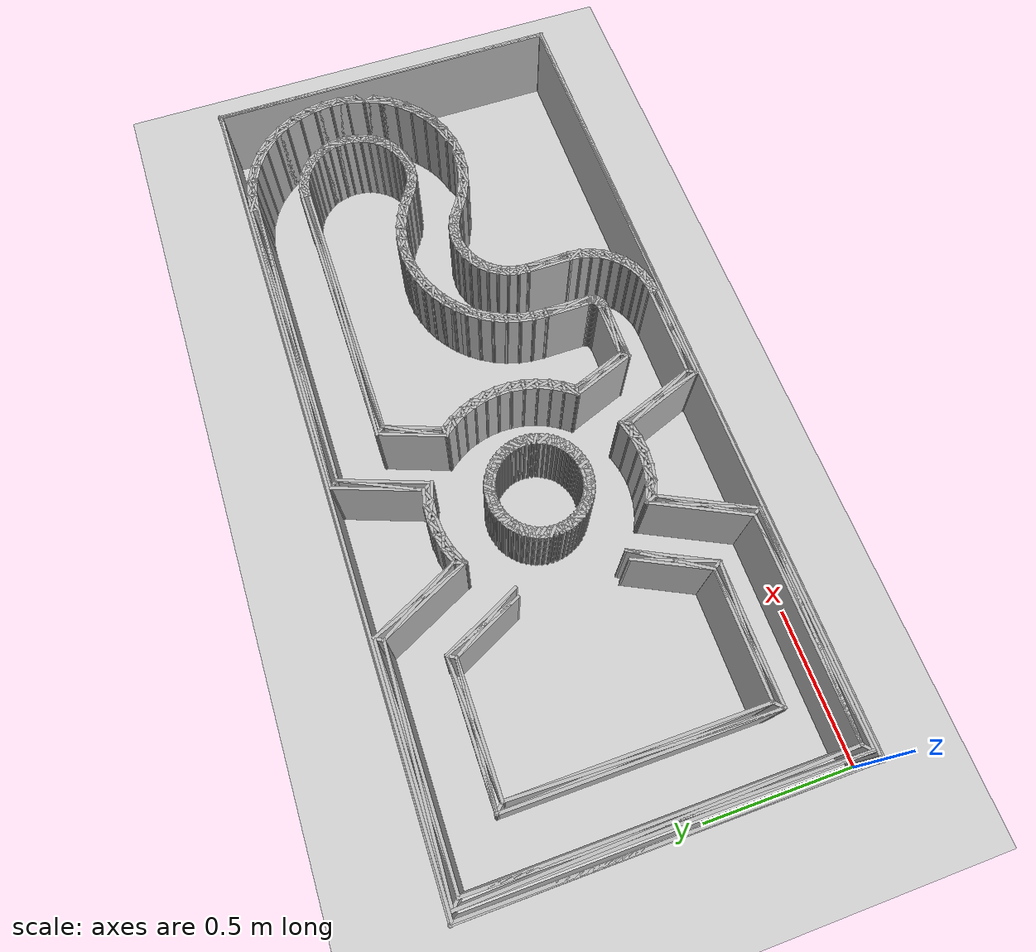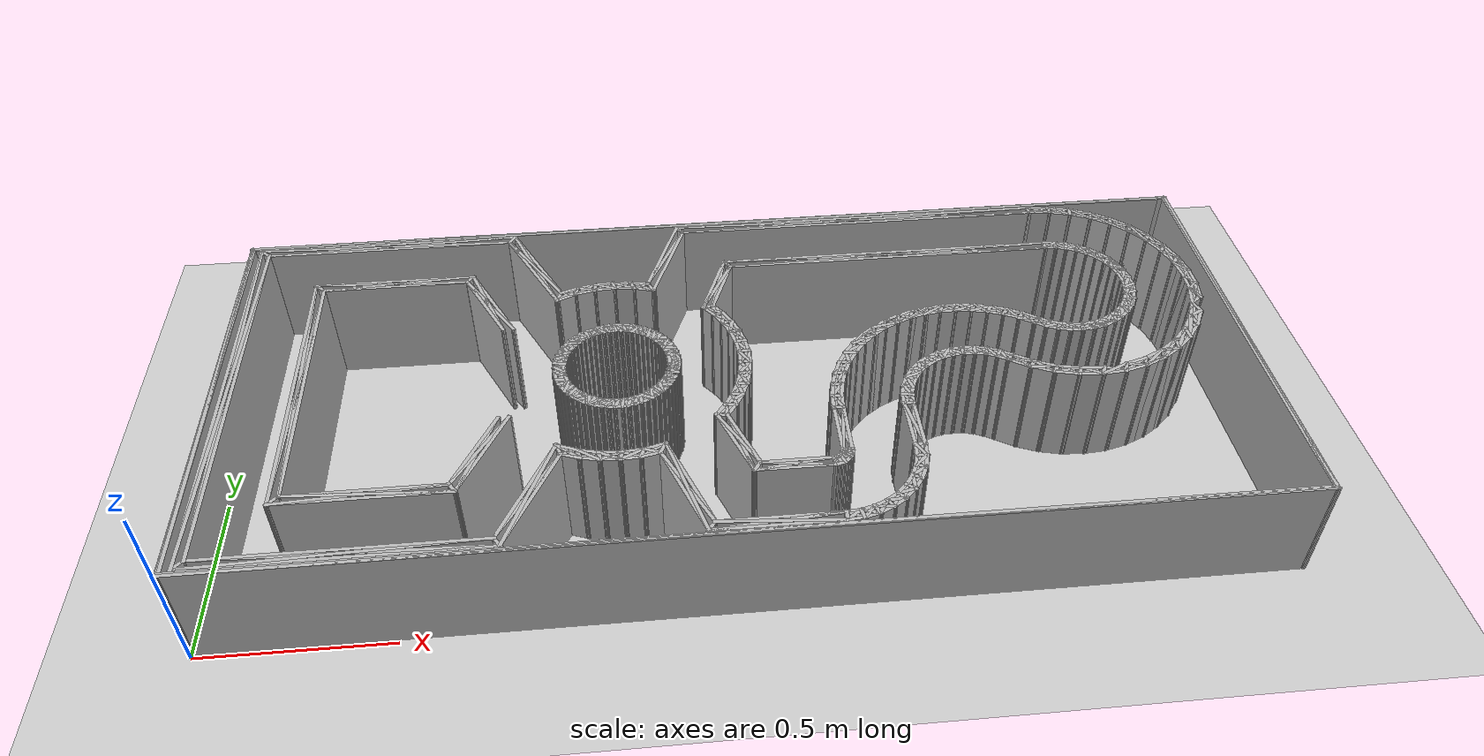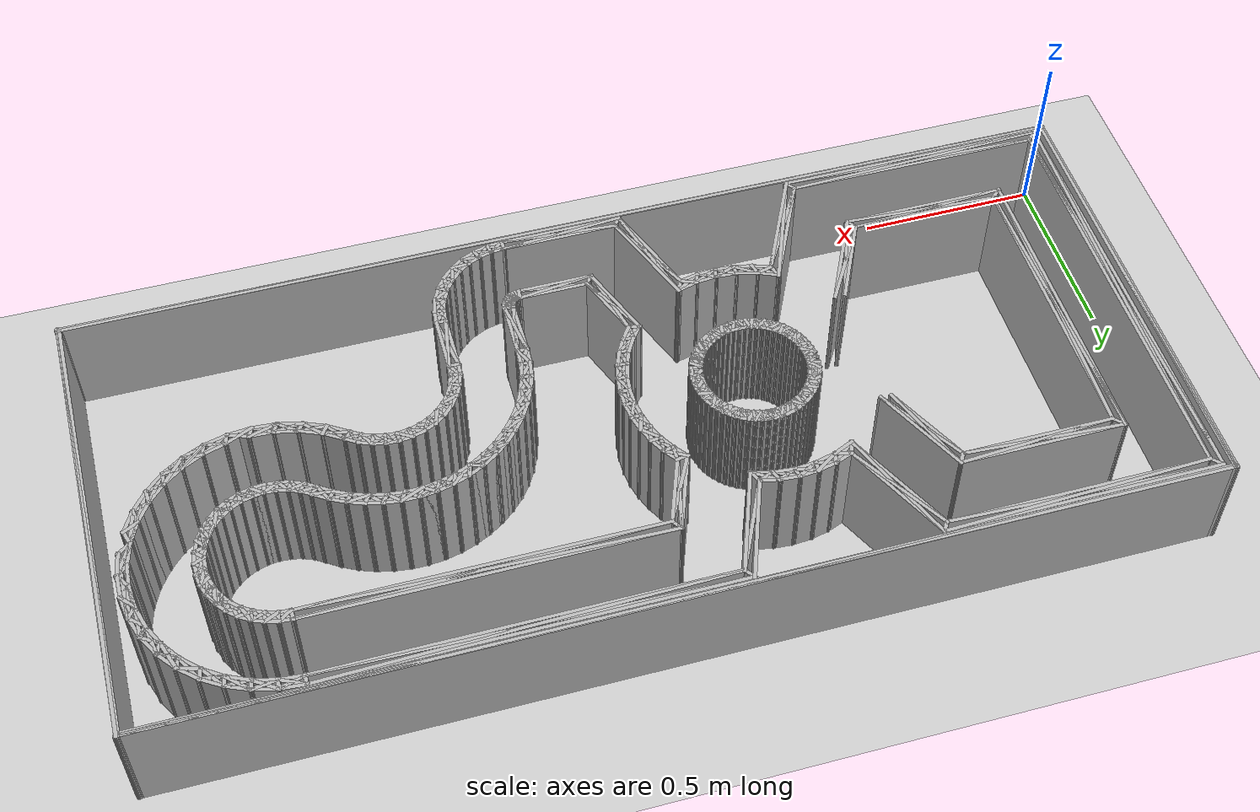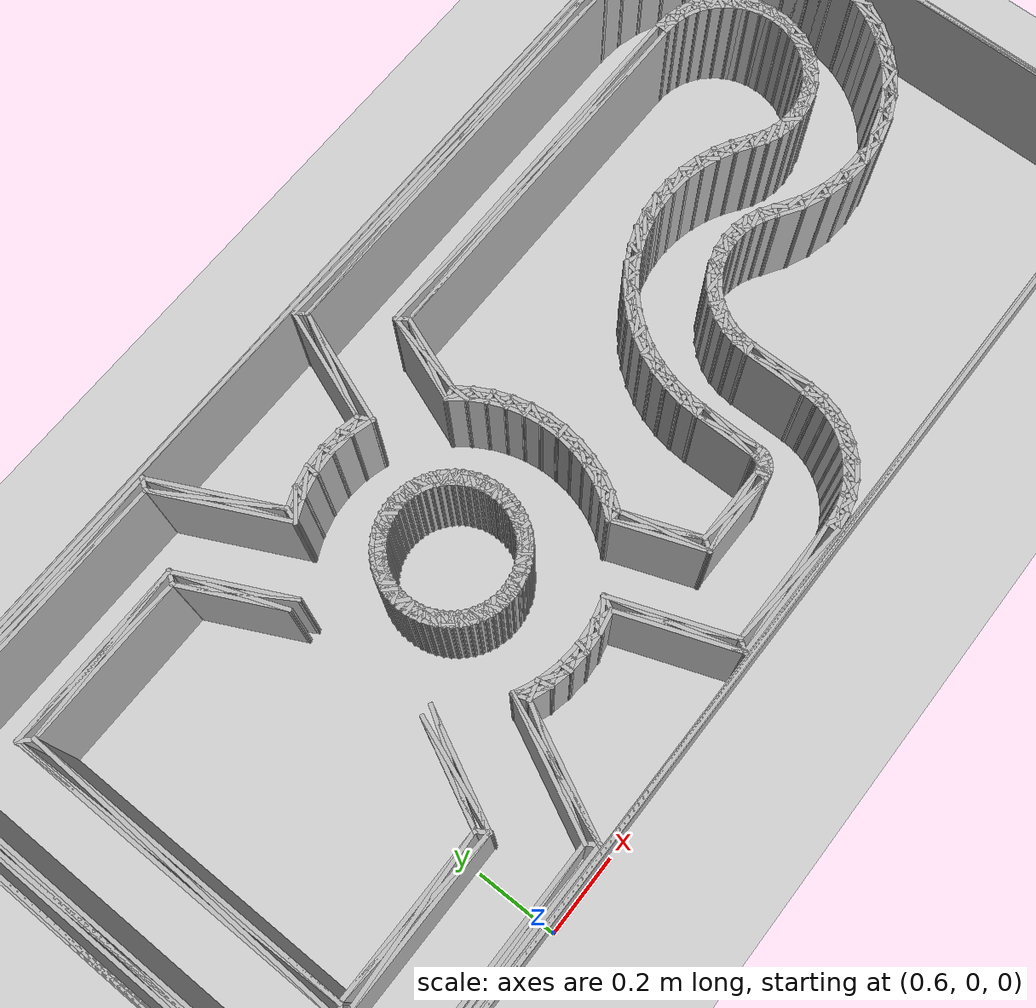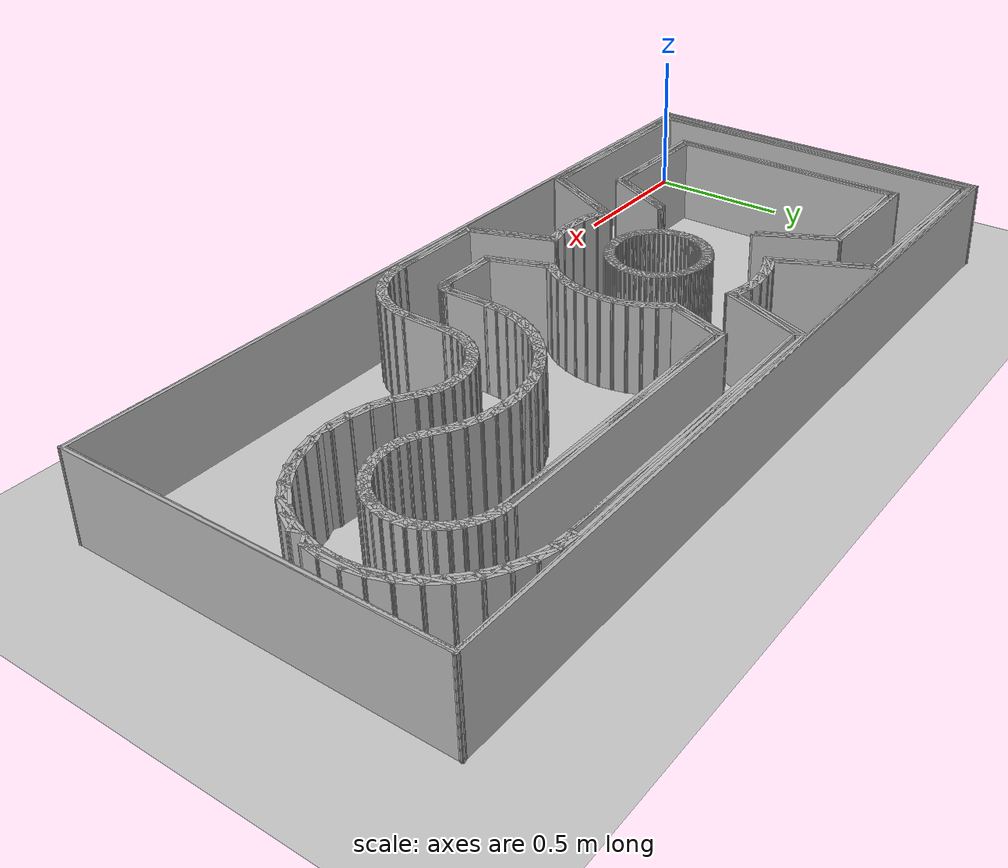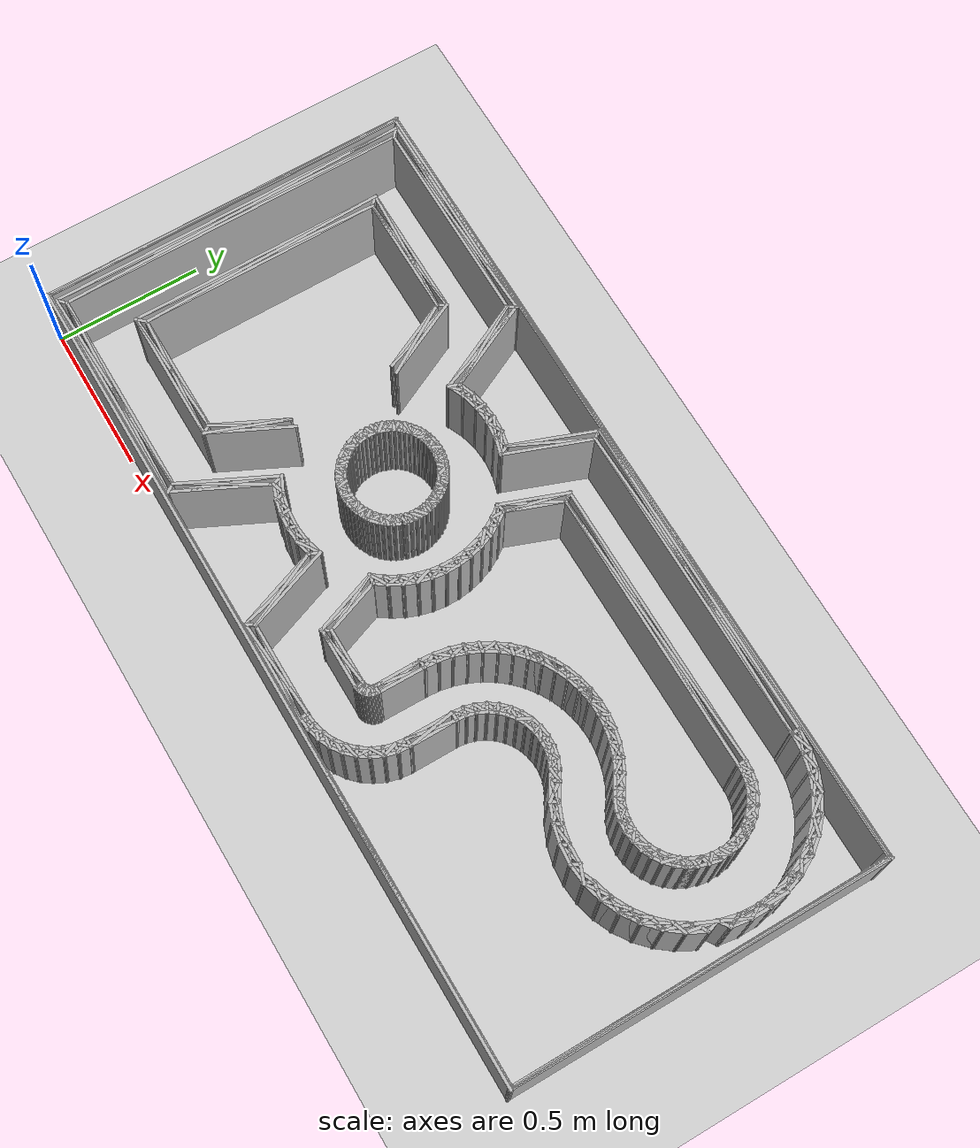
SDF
<?xml version="1.0" ?>
<sdf version="1.8">
  <world name="rosy_road">
    <physics name="1ms" type="ignored">
      <max_step_size>0.001</max_step_size>
      <real_time_factor>1.0</real_time_factor>
    </physics>
    <plugin filename="gz-sim-physics-system" name="gz::sim::systems::Physics" />
    <plugin filename="gz-sim-user-commands-system" name="gz::sim::systems::UserCommands" />
    <plugin filename="gz-sim-scene-broadcaster-system" name="gz::sim::systems::SceneBroadcaster" />
    <plugin filename="gz-sim-sensors-system" name="gz::sim::systems::Sensors">
      <render_engine>ogre2</render_engine>
    </plugin>
    <plugin filename="gz-sim-imu-system" name="gz::sim::systems::Imu" />
    <model name="ground_plane">
      <link name="l">
        <visual name="v">
          <geometry>
            <plane>
              <normal>0 0 1</normal>
              <size>4 2</size>
            </plane>
          </geometry>
        </visual>
        <collision name="v">
          <geometry>
            <plane>
              <normal>0 0 1</normal>
              <size>4 2</size>
            </plane>
          </geometry>
        </collision>
      </link>
    </model>
    <model name="walls">
      <static>true</static>
      <link name="wall_000">
        <pose>0.0000 0.6425 0.150 0 0 1.5708</pose>
        <visual name="v">
          <geometry>
            <box>
              <size>1.2721 0.0100 0.300</size>
            </box>
          </geometry>
        </visual>
        <collision name="c">
          <geometry>
            <box>
              <size>1.2721 0.0100 0.300</size>
            </box>
          </geometry>
        </collision>
      </link>
      <link name="wall_001">
        <pose>0.0025 0.6450 0.150 0 0 -1.5668</pose>
        <visual name="v">
          <geometry>
            <box>
              <size>1.2671 0.0100 0.300</size>
            </box>
          </geometry>
        </visual>
        <collision name="c">
          <geometry>
            <box>
              <size>1.2671 0.0100 0.300</size>
            </box>
          </geometry>
        </collision>
      </link>
      <link name="wall_002">
        <pose>0.0025 0.0150 0.150 0 0 -2.3562</pose>
        <visual name="v">
          <geometry>
            <box>
              <size>0.0200 0.0100 0.300</size>
            </box>
          </geometry>
        </visual>
        <collision name="c">
          <geometry>
            <box>
              <size>0.0200 0.0100 0.300</size>
            </box>
          </geometry>
        </collision>
      </link>
      <link name="wall_003">
        <pose>0.0025 0.6401 0.150 0 0 1.5668</pose>
        <visual name="v">
          <geometry>
            <box>
              <size>1.2671 0.0100 0.300</size>
            </box>
          </geometry>
        </visual>
        <collision name="c">
          <geometry>
            <box>
              <size>1.2671 0.0100 0.300</size>
            </box>
          </geometry>
        </collision>
      </link>
      <link name="wall_004">
        <pose>0.0025 1.2701 0.150 0 0 2.3562</pose>
        <visual name="v">
          <geometry>
            <box>
              <size>0.0200 0.0100 0.300</size>
            </box>
          </geometry>
        </visual>
        <collision name="c">
          <geometry>
            <box>
              <size>0.0200 0.0100 0.300</size>
            </box>
          </geometry>
        </collision>
      </link>
      <link name="wall_005">
        <pose>1.4025 1.2701 0.150 0 0 -0.0018</pose>
        <visual name="v">
          <geometry>
            <box>
              <size>2.8171 0.0100 0.300</size>
            </box>
          </geometry>
        </visual>
        <collision name="c">
          <geometry>
            <box>
              <size>2.8171 0.0100 0.300</size>
            </box>
          </geometry>
        </collision>
      </link>
      <link name="wall_006">
        <pose>1.4050 1.2676 0.150 0 0 3.1416</pose>
        <visual name="v">
          <geometry>
            <box>
              <size>2.8121 0.0100 0.300</size>
            </box>
          </geometry>
        </visual>
        <collision name="c">
          <geometry>
            <box>
              <size>2.8121 0.0100 0.300</size>
            </box>
          </geometry>
        </collision>
      </link>
      <link name="wall_007">
        <pose>0.0050 0.6425 0.150 0 0 -1.5708</pose>
        <visual name="v">
          <geometry>
            <box>
              <size>1.2621 0.0100 0.300</size>
            </box>
          </geometry>
        </visual>
        <collision name="c">
          <geometry>
            <box>
              <size>1.2621 0.0100 0.300</size>
            </box>
          </geometry>
        </collision>
      </link>
      <link name="wall_008">
        <pose>1.4050 0.0175 0.150 0 0 0.0000</pose>
        <visual name="v">
          <geometry>
            <box>
              <size>2.8121 0.0100 0.300</size>
            </box>
          </geometry>
        </visual>
        <collision name="c">
          <geometry>
            <box>
              <size>2.8121 0.0100 0.300</size>
            </box>
          </geometry>
        </collision>
      </link>
      <link name="wall_009">
        <pose>1.4025 0.0150 0.150 0 0 -3.1398</pose>
        <visual name="v">
          <geometry>
            <box>
              <size>2.8171 0.0100 0.300</size>
            </box>
          </geometry>
        </visual>
        <collision name="c">
          <geometry>
            <box>
              <size>2.8171 0.0100 0.300</size>
            </box>
          </geometry>
        </collision>
      </link>
      <link name="wall_010">
        <pose>1.4050 0.0125 0.150 0 0 0.0000</pose>
        <visual name="v">
          <geometry>
            <box>
              <size>2.8221 0.0100 0.300</size>
            </box>
          </geometry>
        </visual>
        <collision name="c">
          <geometry>
            <box>
              <size>2.8221 0.0100 0.300</size>
            </box>
          </geometry>
        </collision>
      </link>
      <link name="wall_011">
        <pose>1.4075 0.0150 0.150 0 0 3.1398</pose>
        <visual name="v">
          <geometry>
            <box>
              <size>2.8171 0.0100 0.300</size>
            </box>
          </geometry>
        </visual>
        <collision name="c">
          <geometry>
            <box>
              <size>2.8171 0.0100 0.300</size>
            </box>
          </geometry>
        </collision>
      </link>
      <link name="wall_012">
        <pose>1.4050 1.2726 0.150 0 0 0.0000</pose>
        <visual name="v">
          <geometry>
            <box>
              <size>2.8221 0.0100 0.300</size>
            </box>
          </geometry>
        </visual>
        <collision name="c">
          <geometry>
            <box>
              <size>2.8221 0.0100 0.300</size>
            </box>
          </geometry>
        </collision>
      </link>
      <link name="wall_013">
        <pose>1.4075 1.2701 0.150 0 0 -3.1398</pose>
        <visual name="v">
          <geometry>
            <box>
              <size>2.8171 0.0100 0.300</size>
            </box>
          </geometry>
        </visual>
        <collision name="c">
          <geometry>
            <box>
              <size>2.8171 0.0100 0.300</size>
            </box>
          </geometry>
        </collision>
      </link>
      <link name="wall_014">
        <pose>2.8051 0.6425 0.150 0 0 1.5708</pose>
        <visual name="v">
          <geometry>
            <box>
              <size>1.2621 0.0100 0.300</size>
            </box>
          </geometry>
        </visual>
        <collision name="c">
          <geometry>
            <box>
              <size>1.2621 0.0100 0.300</size>
            </box>
          </geometry>
        </collision>
      </link>
      <link name="wall_015">
        <pose>2.8076 0.6401 0.150 0 0 -1.5668</pose>
        <visual name="v">
          <geometry>
            <box>
              <size>1.2671 0.0100 0.300</size>
            </box>
          </geometry>
        </visual>
        <collision name="c">
          <geometry>
            <box>
              <size>1.2671 0.0100 0.300</size>
            </box>
          </geometry>
        </collision>
      </link>
      <link name="wall_016">
        <pose>2.8076 0.0150 0.150 0 0 2.3562</pose>
        <visual name="v">
          <geometry>
            <box>
              <size>0.0200 0.0100 0.300</size>
            </box>
          </geometry>
        </visual>
        <collision name="c">
          <geometry>
            <box>
              <size>0.0200 0.0100 0.300</size>
            </box>
          </geometry>
        </collision>
      </link>
      <link name="wall_017">
        <pose>2.8076 0.6450 0.150 0 0 1.5668</pose>
        <visual name="v">
          <geometry>
            <box>
              <size>1.2671 0.0100 0.300</size>
            </box>
          </geometry>
        </visual>
        <collision name="c">
          <geometry>
            <box>
              <size>1.2671 0.0100 0.300</size>
            </box>
          </geometry>
        </collision>
      </link>
      <link name="wall_018">
        <pose>2.8101 0.6425 0.150 0 0 -1.5708</pose>
        <visual name="v">
          <geometry>
            <box>
              <size>1.2721 0.0100 0.300</size>
            </box>
          </geometry>
        </visual>
        <collision name="c">
          <geometry>
            <box>
              <size>1.2721 0.0100 0.300</size>
            </box>
          </geometry>
        </collision>
      </link>
      <link name="wall_019">
        <pose>2.8076 1.2701 0.150 0 0 0.7854</pose>
        <visual name="v">
          <geometry>
            <box>
              <size>0.0200 0.0100 0.300</size>
            </box>
          </geometry>
        </visual>
        <collision name="c">
          <geometry>
            <box>
              <size>0.0200 0.0100 0.300</size>
            </box>
          </geometry>
        </collision>
      </link>
      <link name="wall_020">
        <pose>0.0301 0.6425 0.150 0 0 1.5708</pose>
        <visual name="v">
          <geometry>
            <box>
              <size>1.2419 0.0100 0.300</size>
            </box>
          </geometry>
        </visual>
        <collision name="c">
          <geometry>
            <box>
              <size>1.2419 0.0100 0.300</size>
            </box>
          </geometry>
        </collision>
      </link>
      <link name="wall_021">
        <pose>0.0425 0.6550 0.150 0 0 -1.5501</pose>
        <visual name="v">
          <geometry>
            <box>
              <size>1.2173 0.0100 0.300</size>
            </box>
          </geometry>
        </visual>
        <collision name="c">
          <geometry>
            <box>
              <size>1.2173 0.0100 0.300</size>
            </box>
          </geometry>
        </collision>
      </link>
      <link name="wall_022">
        <pose>0.0425 0.0400 0.150 0 0 -2.3562</pose>
        <visual name="v">
          <geometry>
            <box>
              <size>0.0472 0.0100 0.300</size>
            </box>
          </geometry>
        </visual>
        <collision name="c">
          <geometry>
            <box>
              <size>0.0472 0.0100 0.300</size>
            </box>
          </geometry>
        </collision>
      </link>
      <link name="wall_023">
        <pose>0.0425 0.6301 0.150 0 0 1.5501</pose>
        <visual name="v">
          <geometry>
            <box>
              <size>1.2173 0.0100 0.300</size>
            </box>
          </geometry>
        </visual>
        <collision name="c">
          <geometry>
            <box>
              <size>1.2173 0.0100 0.300</size>
            </box>
          </geometry>
        </collision>
      </link>
      <link name="wall_024">
        <pose>0.0425 1.2450 0.150 0 0 2.3562</pose>
        <visual name="v">
          <geometry>
            <box>
              <size>0.0472 0.0100 0.300</size>
            </box>
          </geometry>
        </visual>
        <collision name="c">
          <geometry>
            <box>
              <size>0.0472 0.0100 0.300</size>
            </box>
          </geometry>
        </collision>
      </link>
      <link name="wall_025">
        <pose>0.3972 1.2450 0.150 0 0 -0.0339</pose>
        <visual name="v">
          <geometry>
            <box>
              <size>0.7467 0.0100 0.300</size>
            </box>
          </geometry>
        </visual>
        <collision name="c">
          <geometry>
            <box>
              <size>0.7467 0.0100 0.300</size>
            </box>
          </geometry>
        </collision>
      </link>
      <link name="wall_026">
        <pose>0.4097 1.2326 0.150 0 0 3.1416</pose>
        <visual name="v">
          <geometry>
            <box>
              <size>0.7214 0.0100 0.300</size>
            </box>
          </geometry>
        </visual>
        <collision name="c">
          <geometry>
            <box>
              <size>0.7214 0.0100 0.300</size>
            </box>
          </geometry>
        </collision>
      </link>
      <link name="wall_027">
        <pose>0.0550 0.6425 0.150 0 0 -1.5708</pose>
        <visual name="v">
          <geometry>
            <box>
              <size>1.1921 0.0100 0.300</size>
            </box>
          </geometry>
        </visual>
        <collision name="c">
          <geometry>
            <box>
              <size>1.1921 0.0100 0.300</size>
            </box>
          </geometry>
        </collision>
      </link>
      <link name="wall_028">
        <pose>0.4097 0.0525 0.150 0 0 0.0000</pose>
        <visual name="v">
          <geometry>
            <box>
              <size>0.7214 0.0100 0.300</size>
            </box>
          </geometry>
        </visual>
        <collision name="c">
          <geometry>
            <box>
              <size>0.7214 0.0100 0.300</size>
            </box>
          </geometry>
        </collision>
      </link>
      <link name="wall_029">
        <pose>0.3972 0.0400 0.150 0 0 -3.1077</pose>
        <visual name="v">
          <geometry>
            <box>
              <size>0.7467 0.0100 0.300</size>
            </box>
          </geometry>
        </visual>
        <collision name="c">
          <geometry>
            <box>
              <size>0.7467 0.0100 0.300</size>
            </box>
          </geometry>
        </collision>
      </link>
      <link name="wall_030">
        <pose>0.4051 0.0276 0.150 0 0 0.0000</pose>
        <visual name="v">
          <geometry>
            <box>
              <size>0.7620 0.0100 0.300</size>
            </box>
          </geometry>
        </visual>
        <collision name="c">
          <geometry>
            <box>
              <size>0.7620 0.0100 0.300</size>
            </box>
          </geometry>
        </collision>
      </link>
      <link name="wall_031">
        <pose>0.4176 0.0400 0.150 0 0 3.1073</pose>
        <visual name="v">
          <geometry>
            <box>
              <size>0.7375 0.0100 0.300</size>
            </box>
          </geometry>
        </visual>
        <collision name="c">
          <geometry>
            <box>
              <size>0.7375 0.0100 0.300</size>
            </box>
          </geometry>
        </collision>
      </link>
      <link name="wall_032">
        <pose>0.0425 0.0400 0.150 0 0 -2.3562</pose>
        <visual name="v">
          <geometry>
            <box>
              <size>0.0472 0.0100 0.300</size>
            </box>
          </geometry>
        </visual>
        <collision name="c">
          <geometry>
            <box>
              <size>0.0472 0.0100 0.300</size>
            </box>
          </geometry>
        </collision>
      </link>
      <link name="wall_033">
        <pose>0.4051 1.2575 0.150 0 0 0.0000</pose>
        <visual name="v">
          <geometry>
            <box>
              <size>0.7620 0.0100 0.300</size>
            </box>
          </geometry>
        </visual>
        <collision name="c">
          <geometry>
            <box>
              <size>0.7620 0.0100 0.300</size>
            </box>
          </geometry>
        </collision>
      </link>
      <link name="wall_034">
        <pose>0.4176 1.2450 0.150 0 0 -3.1073</pose>
        <visual name="v">
          <geometry>
            <box>
              <size>0.7375 0.0100 0.300</size>
            </box>
          </geometry>
        </visual>
        <collision name="c">
          <geometry>
            <box>
              <size>0.7375 0.0100 0.300</size>
            </box>
          </geometry>
        </collision>
      </link>
      <link name="wall_035">
        <pose>0.0425 1.2450 0.150 0 0 2.3562</pose>
        <visual name="v">
          <geometry>
            <box>
              <size>0.0472 0.0100 0.300</size>
            </box>
          </geometry>
        </visual>
        <collision name="c">
          <geometry>
            <box>
              <size>0.0472 0.0100 0.300</size>
            </box>
          </geometry>
        </collision>
      </link>
      <link name="wall_036">
        <pose>0.7722 0.0400 0.150 0 0 -1.0082</pose>
        <visual name="v">
          <geometry>
            <box>
              <size>0.0414 0.0100 0.300</size>
            </box>
          </geometry>
        </visual>
        <collision name="c">
          <geometry>
            <box>
              <size>0.0414 0.0100 0.300</size>
            </box>
          </geometry>
        </collision>
      </link>
      <link name="wall_037">
        <pose>0.8444 0.1883 0.150 0 0 1.1905</pose>
        <visual name="v">
          <geometry>
            <box>
              <size>0.3581 0.0100 0.300</size>
            </box>
          </geometry>
        </visual>
        <collision name="c">
          <geometry>
            <box>
              <size>0.3581 0.0100 0.300</size>
            </box>
          </geometry>
        </collision>
      </link>
      <link name="wall_038">
        <pose>0.8365 0.2008 0.150 0 0 -2.0235</pose>
        <visual name="v">
          <geometry>
            <box>
              <size>0.3417 0.0100 0.300</size>
            </box>
          </geometry>
        </visual>
        <collision name="c">
          <geometry>
            <box>
              <size>0.3417 0.0100 0.300</size>
            </box>
          </geometry>
        </collision>
      </link>
      <link name="wall_039">
        <pose>0.8423 0.1839 0.150 0 0 1.0359</pose>
        <visual name="v">
          <geometry>
            <box>
              <size>0.3175 0.0100 0.300</size>
            </box>
          </geometry>
        </visual>
        <collision name="c">
          <geometry>
            <box>
              <size>0.3175 0.0100 0.300</size>
            </box>
          </geometry>
        </collision>
      </link>
      <link name="wall_040">
        <pose>0.8501 0.1715 0.150 0 0 -2.0237</pose>
        <visual name="v">
          <geometry>
            <box>
              <size>0.3320 0.0100 0.300</size>
            </box>
          </geometry>
        </visual>
        <collision name="c">
          <geometry>
            <box>
              <size>0.3320 0.0100 0.300</size>
            </box>
          </geometry>
        </collision>
      </link>
      <link name="wall_041">
        <pose>0.7722 1.2450 0.150 0 0 1.0082</pose>
        <visual name="v">
          <geometry>
            <box>
              <size>0.0414 0.0100 0.300</size>
            </box>
          </geometry>
        </visual>
        <collision name="c">
          <geometry>
            <box>
              <size>0.0414 0.0100 0.300</size>
            </box>
          </geometry>
        </collision>
      </link>
      <link name="wall_042">
        <pose>0.8444 1.0968 0.150 0 0 -1.1905</pose>
        <visual name="v">
          <geometry>
            <box>
              <size>0.3581 0.0100 0.300</size>
            </box>
          </geometry>
        </visual>
        <collision name="c">
          <geometry>
            <box>
              <size>0.3581 0.0100 0.300</size>
            </box>
          </geometry>
        </collision>
      </link>
      <link name="wall_043">
        <pose>0.8365 1.0843 0.150 0 0 2.0235</pose>
        <visual name="v">
          <geometry>
            <box>
              <size>0.3417 0.0100 0.300</size>
            </box>
          </geometry>
        </visual>
        <collision name="c">
          <geometry>
            <box>
              <size>0.3417 0.0100 0.300</size>
            </box>
          </geometry>
        </collision>
      </link>
      <link name="wall_044">
        <pose>0.8423 1.1012 0.150 0 0 -1.0359</pose>
        <visual name="v">
          <geometry>
            <box>
              <size>0.3175 0.0100 0.300</size>
            </box>
          </geometry>
        </visual>
        <collision name="c">
          <geometry>
            <box>
              <size>0.3175 0.0100 0.300</size>
            </box>
          </geometry>
        </collision>
      </link>
      <link name="wall_045">
        <pose>0.8501 1.1137 0.150 0 0 2.0237</pose>
        <visual name="v">
          <geometry>
            <box>
              <size>0.3320 0.0100 0.300</size>
            </box>
          </geometry>
        </visual>
        <collision name="c">
          <geometry>
            <box>
              <size>0.3320 0.0100 0.300</size>
            </box>
          </geometry>
        </collision>
      </link>
      <link name="wall_046">
        <pose>0.9143 0.3322 0.150 0 0 -1.2419</pose>
        <visual name="v">
          <geometry>
            <box>
              <size>0.0476 0.0100 0.300</size>
            </box>
          </geometry>
        </visual>
        <collision name="c">
          <geometry>
            <box>
              <size>0.0476 0.0100 0.300</size>
            </box>
          </geometry>
        </collision>
      </link>
      <link name="wall_047">
        <pose>0.9405 0.3206 0.150 0 0 0.2519</pose>
        <visual name="v">
          <geometry>
            <box>
              <size>0.0541 0.0100 0.300</size>
            </box>
          </geometry>
        </visual>
        <collision name="c">
          <geometry>
            <box>
              <size>0.0541 0.0100 0.300</size>
            </box>
          </geometry>
        </collision>
      </link>
      <link name="wall_048">
        <pose>0.9347 0.3374 0.150 0 0 2.7241</pose>
        <visual name="v">
          <geometry>
            <box>
              <size>0.0692 0.0100 0.300</size>
            </box>
          </geometry>
        </visual>
        <collision name="c">
          <geometry>
            <box>
              <size>0.0692 0.0100 0.300</size>
            </box>
          </geometry>
        </collision>
      </link>
      <link name="wall_049">
        <pose>0.9383 0.3231 0.150 0 0 -0.7162</pose>
        <visual name="v">
          <geometry>
            <box>
              <size>0.0907 0.0100 0.300</size>
            </box>
          </geometry>
        </visual>
        <collision name="c">
          <geometry>
            <box>
              <size>0.0907 0.0100 0.300</size>
            </box>
          </geometry>
        </collision>
      </link>
      <link name="wall_050">
        <pose>0.9440 0.3063 0.150 0 0 2.7821</pose>
        <visual name="v">
          <geometry>
            <box>
              <size>0.0632 0.0100 0.300</size>
            </box>
          </geometry>
        </visual>
        <collision name="c">
          <geometry>
            <box>
              <size>0.0632 0.0100 0.300</size>
            </box>
          </geometry>
        </collision>
      </link>
      <link name="wall_051">
        <pose>0.9143 0.9530 0.150 0 0 1.2419</pose>
        <visual name="v">
          <geometry>
            <box>
              <size>0.0476 0.0100 0.300</size>
            </box>
          </geometry>
        </visual>
        <collision name="c">
          <geometry>
            <box>
              <size>0.0476 0.0100 0.300</size>
            </box>
          </geometry>
        </collision>
      </link>
      <link name="wall_052">
        <pose>0.9405 0.9645 0.150 0 0 -0.2519</pose>
        <visual name="v">
          <geometry>
            <box>
              <size>0.0541 0.0100 0.300</size>
            </box>
          </geometry>
        </visual>
        <collision name="c">
          <geometry>
            <box>
              <size>0.0541 0.0100 0.300</size>
            </box>
          </geometry>
        </collision>
      </link>
      <link name="wall_053">
        <pose>0.9347 0.9477 0.150 0 0 -2.7241</pose>
        <visual name="v">
          <geometry>
            <box>
              <size>0.0692 0.0100 0.300</size>
            </box>
          </geometry>
        </visual>
        <collision name="c">
          <geometry>
            <box>
              <size>0.0692 0.0100 0.300</size>
            </box>
          </geometry>
        </collision>
      </link>
      <link name="wall_054">
        <pose>0.9383 0.9620 0.150 0 0 0.7162</pose>
        <visual name="v">
          <geometry>
            <box>
              <size>0.0907 0.0100 0.300</size>
            </box>
          </geometry>
        </visual>
        <collision name="c">
          <geometry>
            <box>
              <size>0.0907 0.0100 0.300</size>
            </box>
          </geometry>
        </collision>
      </link>
      <link name="wall_055">
        <pose>0.9440 0.9788 0.150 0 0 -2.7821</pose>
        <visual name="v">
          <geometry>
            <box>
              <size>0.0632 0.0100 0.300</size>
            </box>
          </geometry>
        </visual>
        <collision name="c">
          <geometry>
            <box>
              <size>0.0632 0.0100 0.300</size>
            </box>
          </geometry>
        </collision>
      </link>
      <link name="wall_056">
        <pose>0.9645 0.3115 0.150 0 0 -1.3266</pose>
        <visual name="v">
          <geometry>
            <box>
              <size>0.0414 0.0100 0.300</size>
            </box>
          </geometry>
        </visual>
        <collision name="c">
          <geometry>
            <box>
              <size>0.0414 0.0100 0.300</size>
            </box>
          </geometry>
        </collision>
      </link>
      <link name="wall_057">
        <pose>0.9921 0.3046 0.150 0 0 0.2941</pose>
        <visual name="v">
          <geometry>
            <box>
              <size>0.0624 0.0100 0.300</size>
            </box>
          </geometry>
        </visual>
        <collision name="c">
          <geometry>
            <box>
              <size>0.0624 0.0100 0.300</size>
            </box>
          </geometry>
        </collision>
      </link>
      <link name="wall_058">
        <pose>0.9885 0.3189 0.150 0 0 2.8953</pose>
        <visual name="v">
          <geometry>
            <box>
              <size>0.0690 0.0100 0.300</size>
            </box>
          </geometry>
        </visual>
        <collision name="c">
          <geometry>
            <box>
              <size>0.0690 0.0100 0.300</size>
            </box>
          </geometry>
        </collision>
      </link>
      <link name="wall_059">
        <pose>0.9894 0.3060 0.150 0 0 -0.6060</pose>
        <visual name="v">
          <geometry>
            <box>
              <size>0.0813 0.0100 0.300</size>
            </box>
          </geometry>
        </visual>
        <collision name="c">
          <geometry>
            <box>
              <size>0.0813 0.0100 0.300</size>
            </box>
          </geometry>
        </collision>
      </link>
      <link name="wall_060">
        <pose>0.9929 0.2918 0.150 0 0 2.9246</pose>
        <visual name="v">
          <geometry>
            <box>
              <size>0.0631 0.0100 0.300</size>
            </box>
          </geometry>
        </visual>
        <collision name="c">
          <geometry>
            <box>
              <size>0.0631 0.0100 0.300</size>
            </box>
          </geometry>
        </collision>
      </link>
      <link name="wall_061">
        <pose>0.9645 0.9735 0.150 0 0 1.3266</pose>
        <visual name="v">
          <geometry>
            <box>
              <size>0.0414 0.0100 0.300</size>
            </box>
          </geometry>
        </visual>
        <collision name="c">
          <geometry>
            <box>
              <size>0.0414 0.0100 0.300</size>
            </box>
          </geometry>
        </collision>
      </link>
      <link name="wall_062">
        <pose>0.9921 0.9805 0.150 0 0 -0.2941</pose>
        <visual name="v">
          <geometry>
            <box>
              <size>0.0624 0.0100 0.300</size>
            </box>
          </geometry>
        </visual>
        <collision name="c">
          <geometry>
            <box>
              <size>0.0624 0.0100 0.300</size>
            </box>
          </geometry>
        </collision>
      </link>
      <link name="wall_063">
        <pose>0.9885 0.9663 0.150 0 0 -2.8953</pose>
        <visual name="v">
          <geometry>
            <box>
              <size>0.0690 0.0100 0.300</size>
            </box>
          </geometry>
        </visual>
        <collision name="c">
          <geometry>
            <box>
              <size>0.0690 0.0100 0.300</size>
            </box>
          </geometry>
        </collision>
      </link>
      <link name="wall_064">
        <pose>0.9894 0.9790 0.150 0 0 0.6060</pose>
        <visual name="v">
          <geometry>
            <box>
              <size>0.0813 0.0100 0.300</size>
            </box>
          </geometry>
        </visual>
        <collision name="c">
          <geometry>
            <box>
              <size>0.0813 0.0100 0.300</size>
            </box>
          </geometry>
        </collision>
      </link>
      <link name="wall_065">
        <pose>0.9929 0.9933 0.150 0 0 -2.9246</pose>
        <visual name="v">
          <geometry>
            <box>
              <size>0.0631 0.0100 0.300</size>
            </box>
          </geometry>
        </visual>
        <collision name="c">
          <geometry>
            <box>
              <size>0.0631 0.0100 0.300</size>
            </box>
          </geometry>
        </collision>
      </link>
      <link name="wall_066">
        <pose>1.0171 0.2991 0.150 0 0 -1.5045</pose>
        <visual name="v">
          <geometry>
            <box>
              <size>0.0377 0.0100 0.300</size>
            </box>
          </geometry>
        </visual>
        <collision name="c">
          <geometry>
            <box>
              <size>0.0377 0.0100 0.300</size>
            </box>
          </geometry>
        </collision>
      </link>
      <link name="wall_067">
        <pose>1.0434 0.2845 0.150 0 0 -0.0723</pose>
        <visual name="v">
          <geometry>
            <box>
              <size>0.0632 0.0100 0.300</size>
            </box>
          </geometry>
        </visual>
        <collision name="c">
          <geometry>
            <box>
              <size>0.0632 0.0100 0.300</size>
            </box>
          </geometry>
        </collision>
      </link>
      <link name="wall_068">
        <pose>1.0426 0.2973 0.150 0 0 2.6350</pose>
        <visual name="v">
          <geometry>
            <box>
              <size>0.0724 0.0100 0.300</size>
            </box>
          </geometry>
        </visual>
        <collision name="c">
          <geometry>
            <box>
              <size>0.0724 0.0100 0.300</size>
            </box>
          </geometry>
        </collision>
      </link>
      <link name="wall_069">
        <pose>1.0447 0.3098 0.150 0 0 -0.0753</pose>
        <visual name="v">
          <geometry>
            <box>
              <size>0.0692 0.0100 0.300</size>
            </box>
          </geometry>
        </visual>
        <collision name="c">
          <geometry>
            <box>
              <size>0.0692 0.0100 0.300</size>
            </box>
          </geometry>
        </collision>
      </link>
      <link name="wall_070">
        <pose>1.0455 0.2970 0.150 0 0 -2.7739</pose>
        <visual name="v">
          <geometry>
            <box>
              <size>0.0713 0.0100 0.300</size>
            </box>
          </geometry>
        </visual>
        <collision name="c">
          <geometry>
            <box>
              <size>0.0713 0.0100 0.300</size>
            </box>
          </geometry>
        </collision>
      </link>
      <link name="wall_071">
        <pose>1.0171 0.9860 0.150 0 0 1.5045</pose>
        <visual name="v">
          <geometry>
            <box>
              <size>0.0377 0.0100 0.300</size>
            </box>
          </geometry>
        </visual>
        <collision name="c">
          <geometry>
            <box>
              <size>0.0377 0.0100 0.300</size>
            </box>
          </geometry>
        </collision>
      </link>
      <link name="wall_072">
        <pose>1.0434 1.0007 0.150 0 0 0.0723</pose>
        <visual name="v">
          <geometry>
            <box>
              <size>0.0632 0.0100 0.300</size>
            </box>
          </geometry>
        </visual>
        <collision name="c">
          <geometry>
            <box>
              <size>0.0632 0.0100 0.300</size>
            </box>
          </geometry>
        </collision>
      </link>
      <link name="wall_073">
        <pose>1.0426 0.9879 0.150 0 0 -2.6350</pose>
        <visual name="v">
          <geometry>
            <box>
              <size>0.0724 0.0100 0.300</size>
            </box>
          </geometry>
        </visual>
        <collision name="c">
          <geometry>
            <box>
              <size>0.0724 0.0100 0.300</size>
            </box>
          </geometry>
        </collision>
      </link>
      <link name="wall_074">
        <pose>1.0447 0.9754 0.150 0 0 0.0753</pose>
        <visual name="v">
          <geometry>
            <box>
              <size>0.0692 0.0100 0.300</size>
            </box>
          </geometry>
        </visual>
        <collision name="c">
          <geometry>
            <box>
              <size>0.0692 0.0100 0.300</size>
            </box>
          </geometry>
        </collision>
      </link>
      <link name="wall_075">
        <pose>1.0455 0.9881 0.150 0 0 2.7739</pose>
        <visual name="v">
          <geometry>
            <box>
              <size>0.0713 0.0100 0.300</size>
            </box>
          </geometry>
        </visual>
        <collision name="c">
          <geometry>
            <box>
              <size>0.0713 0.0100 0.300</size>
            </box>
          </geometry>
        </collision>
      </link>
      <link name="wall_076">
        <pose>1.0711 0.2951 0.150 0 0 1.4044</pose>
        <visual name="v">
          <geometry>
            <box>
              <size>0.0374 0.0100 0.300</size>
            </box>
          </geometry>
        </visual>
        <collision name="c">
          <geometry>
            <box>
              <size>0.0374 0.0100 0.300</size>
            </box>
          </geometry>
        </collision>
      </link>
      <link name="wall_077">
        <pose>1.0966 0.2968 0.150 0 0 -0.4324</pose>
        <visual name="v">
          <geometry>
            <box>
              <size>0.0635 0.0100 0.300</size>
            </box>
          </geometry>
        </visual>
        <collision name="c">
          <geometry>
            <box>
              <size>0.0635 0.0100 0.300</size>
            </box>
          </geometry>
        </collision>
      </link>
      <link name="wall_078">
        <pose>1.0945 0.2843 0.150 0 0 -3.0750</pose>
        <visual name="v">
          <geometry>
            <box>
              <size>0.0631 0.0100 0.300</size>
            </box>
          </geometry>
        </visual>
        <collision name="c">
          <geometry>
            <box>
              <size>0.0631 0.0100 0.300</size>
            </box>
          </geometry>
        </collision>
      </link>
      <link name="wall_079">
        <pose>1.0995 0.2978 0.150 0 0 0.4623</pose>
        <visual name="v">
          <geometry>
            <box>
              <size>0.0802 0.0100 0.300</size>
            </box>
          </geometry>
        </visual>
        <collision name="c">
          <geometry>
            <box>
              <size>0.0802 0.0100 0.300</size>
            </box>
          </geometry>
        </collision>
      </link>
      <link name="wall_080">
        <pose>1.1016 0.3103 0.150 0 0 -3.0468</pose>
        <visual name="v">
          <geometry>
            <box>
              <size>0.0691 0.0100 0.300</size>
            </box>
          </geometry>
        </visual>
        <collision name="c">
          <geometry>
            <box>
              <size>0.0691 0.0100 0.300</size>
            </box>
          </geometry>
        </collision>
      </link>
      <link name="wall_081">
        <pose>1.0711 0.9900 0.150 0 0 -1.4044</pose>
        <visual name="v">
          <geometry>
            <box>
              <size>0.0374 0.0100 0.300</size>
            </box>
          </geometry>
        </visual>
        <collision name="c">
          <geometry>
            <box>
              <size>0.0374 0.0100 0.300</size>
            </box>
          </geometry>
        </collision>
      </link>
      <link name="wall_082">
        <pose>1.0966 0.9883 0.150 0 0 0.4324</pose>
        <visual name="v">
          <geometry>
            <box>
              <size>0.0635 0.0100 0.300</size>
            </box>
          </geometry>
        </visual>
        <collision name="c">
          <geometry>
            <box>
              <size>0.0635 0.0100 0.300</size>
            </box>
          </geometry>
        </collision>
      </link>
      <link name="wall_083">
        <pose>1.0945 1.0008 0.150 0 0 3.0750</pose>
        <visual name="v">
          <geometry>
            <box>
              <size>0.0631 0.0100 0.300</size>
            </box>
          </geometry>
        </visual>
        <collision name="c">
          <geometry>
            <box>
              <size>0.0631 0.0100 0.300</size>
            </box>
          </geometry>
        </collision>
      </link>
      <link name="wall_084">
        <pose>1.0995 0.9873 0.150 0 0 -0.4623</pose>
        <visual name="v">
          <geometry>
            <box>
              <size>0.0802 0.0100 0.300</size>
            </box>
          </geometry>
        </visual>
        <collision name="c">
          <geometry>
            <box>
              <size>0.0802 0.0100 0.300</size>
            </box>
          </geometry>
        </collision>
      </link>
      <link name="wall_085">
        <pose>1.1016 0.9748 0.150 0 0 3.0468</pose>
        <visual name="v">
          <geometry>
            <box>
              <size>0.0691 0.0100 0.300</size>
            </box>
          </geometry>
        </visual>
        <collision name="c">
          <geometry>
            <box>
              <size>0.0691 0.0100 0.300</size>
            </box>
          </geometry>
        </collision>
      </link>
      <link name="wall_086">
        <pose>1.1250 0.2995 0.150 0 0 1.2161</pose>
        <visual name="v">
          <geometry>
            <box>
              <size>0.0408 0.0100 0.300</size>
            </box>
          </geometry>
        </visual>
        <collision name="c">
          <geometry>
            <box>
              <size>0.0408 0.0100 0.300</size>
            </box>
          </geometry>
        </collision>
      </link>
      <link name="wall_087">
        <pose>1.1501 0.3049 0.150 0 0 -0.3861</pose>
        <visual name="v">
          <geometry>
            <box>
              <size>0.0553 0.0100 0.300</size>
            </box>
          </geometry>
        </visual>
        <collision name="c">
          <geometry>
            <box>
              <size>0.0553 0.0100 0.300</size>
            </box>
          </geometry>
        </collision>
      </link>
      <link name="wall_088">
        <pose>1.1450 0.2913 0.150 0 0 -2.9312</pose>
        <visual name="v">
          <geometry>
            <box>
              <size>0.0632 0.0100 0.300</size>
            </box>
          </geometry>
        </visual>
        <collision name="c">
          <geometry>
            <box>
              <size>0.0632 0.0100 0.300</size>
            </box>
          </geometry>
        </collision>
      </link>
      <link name="wall_089">
        <pose>1.1525 0.3070 0.150 0 0 0.5719</pose>
        <visual name="v">
          <geometry>
            <box>
              <size>0.0894 0.0100 0.300</size>
            </box>
          </geometry>
        </visual>
        <collision name="c">
          <geometry>
            <box>
              <size>0.0894 0.0100 0.300</size>
            </box>
          </geometry>
        </collision>
      </link>
      <link name="wall_090">
        <pose>1.1575 0.3205 0.150 0 0 -2.8775</pose>
        <visual name="v">
          <geometry>
            <box>
              <size>0.0691 0.0100 0.300</size>
            </box>
          </geometry>
        </visual>
        <collision name="c">
          <geometry>
            <box>
              <size>0.0691 0.0100 0.300</size>
            </box>
          </geometry>
        </collision>
      </link>
      <link name="wall_091">
        <pose>1.1250 0.9856 0.150 0 0 -1.2161</pose>
        <visual name="v">
          <geometry>
            <box>
              <size>0.0408 0.0100 0.300</size>
            </box>
          </geometry>
        </visual>
        <collision name="c">
          <geometry>
            <box>
              <size>0.0408 0.0100 0.300</size>
            </box>
          </geometry>
        </collision>
      </link>
      <link name="wall_092">
        <pose>1.1501 0.9802 0.150 0 0 0.3861</pose>
        <visual name="v">
          <geometry>
            <box>
              <size>0.0553 0.0100 0.300</size>
            </box>
          </geometry>
        </visual>
        <collision name="c">
          <geometry>
            <box>
              <size>0.0553 0.0100 0.300</size>
            </box>
          </geometry>
        </collision>
      </link>
      <link name="wall_093">
        <pose>1.1450 0.9938 0.150 0 0 2.9312</pose>
        <visual name="v">
          <geometry>
            <box>
              <size>0.0632 0.0100 0.300</size>
            </box>
          </geometry>
        </visual>
        <collision name="c">
          <geometry>
            <box>
              <size>0.0632 0.0100 0.300</size>
            </box>
          </geometry>
        </collision>
      </link>
      <link name="wall_094">
        <pose>1.1525 0.9782 0.150 0 0 -0.5719</pose>
        <visual name="v">
          <geometry>
            <box>
              <size>0.0894 0.0100 0.300</size>
            </box>
          </geometry>
        </visual>
        <collision name="c">
          <geometry>
            <box>
              <size>0.0894 0.0100 0.300</size>
            </box>
          </geometry>
        </collision>
      </link>
      <link name="wall_095">
        <pose>1.1575 0.9647 0.150 0 0 2.8775</pose>
        <visual name="v">
          <geometry>
            <box>
              <size>0.0691 0.0100 0.300</size>
            </box>
          </geometry>
        </visual>
        <collision name="c">
          <geometry>
            <box>
              <size>0.0691 0.0100 0.300</size>
            </box>
          </geometry>
        </collision>
      </link>
      <link name="wall_096">
        <pose>1.1776 0.3123 0.150 0 0 1.1227</pose>
        <visual name="v">
          <geometry>
            <box>
              <size>0.0466 0.0100 0.300</size>
            </box>
          </geometry>
        </visual>
        <collision name="c">
          <geometry>
            <box>
              <size>0.0466 0.0100 0.300</size>
            </box>
          </geometry>
        </collision>
      </link>
      <link name="wall_097">
        <pose>1.2275 0.1777 0.150 0 0 -1.2953</pose>
        <visual name="v">
          <geometry>
            <box>
              <size>0.3241 0.0100 0.300</size>
            </box>
          </geometry>
        </visual>
        <collision name="c">
          <geometry>
            <box>
              <size>0.3241 0.0100 0.300</size>
            </box>
          </geometry>
        </collision>
      </link>
      <link name="wall_098">
        <pose>1.2200 0.1622 0.150 0 0 1.9263</pose>
        <visual name="v">
          <geometry>
            <box>
              <size>0.2990 0.0100 0.300</size>
            </box>
          </geometry>
        </visual>
        <collision name="c">
          <geometry>
            <box>
              <size>0.2990 0.0100 0.300</size>
            </box>
          </geometry>
        </collision>
      </link>
      <link name="wall_099">
        <pose>1.2288 0.1746 0.150 0 0 -1.1230</pose>
        <visual name="v">
          <geometry>
            <box>
              <size>0.2829 0.0100 0.300</size>
            </box>
          </geometry>
        </visual>
        <collision name="c">
          <geometry>
            <box>
              <size>0.2829 0.0100 0.300</size>
            </box>
          </geometry>
        </collision>
      </link>
      <link name="wall_100">
        <pose>1.2363 0.1902 0.150 0 0 1.9265</pose>
        <visual name="v">
          <geometry>
            <box>
              <size>0.3058 0.0100 0.300</size>
            </box>
          </geometry>
        </visual>
        <collision name="c">
          <geometry>
            <box>
              <size>0.3058 0.0100 0.300</size>
            </box>
          </geometry>
        </collision>
      </link>
      <link name="wall_101">
        <pose>1.1776 0.9728 0.150 0 0 -1.1227</pose>
        <visual name="v">
          <geometry>
            <box>
              <size>0.0466 0.0100 0.300</size>
            </box>
          </geometry>
        </visual>
        <collision name="c">
          <geometry>
            <box>
              <size>0.0466 0.0100 0.300</size>
            </box>
          </geometry>
        </collision>
      </link>
      <link name="wall_102">
        <pose>1.2363 1.0949 0.150 0 0 1.2151</pose>
        <visual name="v">
          <geometry>
            <box>
              <size>0.3058 0.0100 0.300</size>
            </box>
          </geometry>
        </visual>
        <collision name="c">
          <geometry>
            <box>
              <size>0.3058 0.0100 0.300</size>
            </box>
          </geometry>
        </collision>
      </link>
      <link name="wall_103">
        <pose>1.2288 1.1105 0.150 0 0 -2.0186</pose>
        <visual name="v">
          <geometry>
            <box>
              <size>0.2829 0.0100 0.300</size>
            </box>
          </geometry>
        </visual>
        <collision name="c">
          <geometry>
            <box>
              <size>0.2829 0.0100 0.300</size>
            </box>
          </geometry>
        </collision>
      </link>
      <link name="wall_104">
        <pose>1.2200 1.1230 0.150 0 0 1.2153</pose>
        <visual name="v">
          <geometry>
            <box>
              <size>0.2990 0.0100 0.300</size>
            </box>
          </geometry>
        </visual>
        <collision name="c">
          <geometry>
            <box>
              <size>0.2990 0.0100 0.300</size>
            </box>
          </geometry>
        </collision>
      </link>
      <link name="wall_105">
        <pose>1.2787 1.2450 0.150 0 0 -0.9609</pose>
        <visual name="v">
          <geometry>
            <box>
              <size>0.0424 0.0100 0.300</size>
            </box>
          </geometry>
        </visual>
        <collision name="c">
          <geometry>
            <box>
              <size>0.0424 0.0100 0.300</size>
            </box>
          </geometry>
        </collision>
      </link>
      <link name="wall_106">
        <pose>1.8262 1.2326 0.150 0 0 0.0000</pose>
        <visual name="v">
          <geometry>
            <box>
              <size>1.0896 0.0100 0.300</size>
            </box>
          </geometry>
        </visual>
        <collision name="c">
          <geometry>
            <box>
              <size>1.0896 0.0100 0.300</size>
            </box>
          </geometry>
        </collision>
      </link>
      <link name="wall_107">
        <pose>1.8175 1.2450 0.150 0 0 3.1189</pose>
        <visual name="v">
          <geometry>
            <box>
              <size>1.1073 0.0100 0.300</size>
            </box>
          </geometry>
        </visual>
        <collision name="c">
          <geometry>
            <box>
              <size>1.1073 0.0100 0.300</size>
            </box>
          </geometry>
        </collision>
      </link>
      <link name="wall_108">
        <pose>1.8175 1.2575 0.150 0 0 0.0000</pose>
        <visual name="v">
          <geometry>
            <box>
              <size>1.1070 0.0100 0.300</size>
            </box>
          </geometry>
        </visual>
        <collision name="c">
          <geometry>
            <box>
              <size>1.1070 0.0100 0.300</size>
            </box>
          </geometry>
        </collision>
      </link>
      <link name="wall_109">
        <pose>1.8262 1.2450 0.150 0 0 -3.1185</pose>
        <visual name="v">
          <geometry>
            <box>
              <size>1.0899 0.0100 0.300</size>
            </box>
          </geometry>
        </visual>
        <collision name="c">
          <geometry>
            <box>
              <size>1.0899 0.0100 0.300</size>
            </box>
          </geometry>
        </collision>
      </link>
      <link name="wall_110">
        <pose>1.2787 1.2450 0.150 0 0 2.1807</pose>
        <visual name="v">
          <geometry>
            <box>
              <size>0.0424 0.0100 0.300</size>
            </box>
          </geometry>
        </visual>
        <collision name="c">
          <geometry>
            <box>
              <size>0.0424 0.0100 0.300</size>
            </box>
          </geometry>
        </collision>
      </link>
      <link name="wall_111">
        <pose>1.2787 0.0400 0.150 0 0 0.9609</pose>
        <visual name="v">
          <geometry>
            <box>
              <size>0.0424 0.0100 0.300</size>
            </box>
          </geometry>
        </visual>
        <collision name="c">
          <geometry>
            <box>
              <size>0.0424 0.0100 0.300</size>
            </box>
          </geometry>
        </collision>
      </link>
      <link name="wall_112">
        <pose>1.4449 0.0400 0.150 0 0 -0.0789</pose>
        <visual name="v">
          <geometry>
            <box>
              <size>0.3280 0.0100 0.300</size>
            </box>
          </geometry>
        </visual>
        <collision name="c">
          <geometry>
            <box>
              <size>0.3280 0.0100 0.300</size>
            </box>
          </geometry>
        </collision>
      </link>
      <link name="wall_113">
        <pose>1.4362 0.0276 0.150 0 0 3.1416</pose>
        <visual name="v">
          <geometry>
            <box>
              <size>0.3444 0.0100 0.300</size>
            </box>
          </geometry>
        </visual>
        <collision name="c">
          <geometry>
            <box>
              <size>0.3444 0.0100 0.300</size>
            </box>
          </geometry>
        </collision>
      </link>
      <link name="wall_114">
        <pose>1.4362 0.0400 0.150 0 0 0.0748</pose>
        <visual name="v">
          <geometry>
            <box>
              <size>0.3453 0.0100 0.300</size>
            </box>
          </geometry>
        </visual>
        <collision name="c">
          <geometry>
            <box>
              <size>0.3453 0.0100 0.300</size>
            </box>
          </geometry>
        </collision>
      </link>
      <link name="wall_115">
        <pose>1.4449 0.0525 0.150 0 0 3.1416</pose>
        <visual name="v">
          <geometry>
            <box>
              <size>0.3270 0.0100 0.300</size>
            </box>
          </geometry>
        </visual>
        <collision name="c">
          <geometry>
            <box>
              <size>0.3270 0.0100 0.300</size>
            </box>
          </geometry>
        </collision>
      </link>
      <link name="wall_116">
        <pose>1.2787 0.0400 0.150 0 0 -2.1807</pose>
        <visual name="v">
          <geometry>
            <box>
              <size>0.0424 0.0100 0.300</size>
            </box>
          </geometry>
        </visual>
        <collision name="c">
          <geometry>
            <box>
              <size>0.0424 0.0100 0.300</size>
            </box>
          </geometry>
        </collision>
      </link>
      <link name="wall_117">
        <pose>1.6024 0.0400 0.150 0 0 1.5708</pose>
        <visual name="v">
          <geometry>
            <box>
              <size>0.0369 0.0100 0.300</size>
            </box>
          </geometry>
        </visual>
        <collision name="c">
          <geometry>
            <box>
              <size>0.0369 0.0100 0.300</size>
            </box>
          </geometry>
        </collision>
      </link>
      <link name="wall_118">
        <pose>1.6207 0.0541 0.150 0 0 0.0874</pose>
        <visual name="v">
          <geometry>
            <box>
              <size>0.0486 0.0100 0.300</size>
            </box>
          </geometry>
        </visual>
        <collision name="c">
          <geometry>
            <box>
              <size>0.0486 0.0100 0.300</size>
            </box>
          </geometry>
        </collision>
      </link>
      <link name="wall_119">
        <pose>1.6207 0.0417 0.150 0 0 -2.4855</pose>
        <visual name="v">
          <geometry>
            <box>
              <size>0.0581 0.0100 0.300</size>
            </box>
          </geometry>
        </visual>
        <collision name="c">
          <geometry>
            <box>
              <size>0.0581 0.0100 0.300</size>
            </box>
          </geometry>
        </collision>
      </link>
      <link name="wall_120">
        <pose>1.6228 0.0294 0.150 0 0 0.0856</pose>
        <visual name="v">
          <geometry>
            <box>
              <size>0.0529 0.0100 0.300</size>
            </box>
          </geometry>
        </visual>
        <collision name="c">
          <geometry>
            <box>
              <size>0.0529 0.0100 0.300</size>
            </box>
          </geometry>
        </collision>
      </link>
      <link name="wall_121">
        <pose>1.6228 0.0418 0.150 0 0 2.6585</pose>
        <visual name="v">
          <geometry>
            <box>
              <size>0.0581 0.0100 0.300</size>
            </box>
          </geometry>
        </visual>
        <collision name="c">
          <geometry>
            <box>
              <size>0.0581 0.0100 0.300</size>
            </box>
          </geometry>
        </collision>
      </link>
      <link name="wall_122">
        <pose>2.3650 1.2450 0.150 0 0 1.5708</pose>
        <visual name="v">
          <geometry>
            <box>
              <size>0.0369 0.0100 0.300</size>
            </box>
          </geometry>
        </visual>
        <collision name="c">
          <geometry>
            <box>
              <size>0.0369 0.0100 0.300</size>
            </box>
          </geometry>
        </collision>
      </link>
      <link name="wall_123">
        <pose>2.3963 1.2423 0.150 0 0 -0.4515</pose>
        <visual name="v">
          <geometry>
            <box>
              <size>0.0817 0.0100 0.300</size>
            </box>
          </geometry>
        </visual>
        <collision name="c">
          <geometry>
            <box>
              <size>0.0817 0.0100 0.300</size>
            </box>
          </geometry>
        </collision>
      </link>
      <link name="wall_124">
        <pose>2.3963 1.2298 0.150 0 0 3.0541</pose>
        <visual name="v">
          <geometry>
            <box>
              <size>0.0749 0.0100 0.300</size>
            </box>
          </geometry>
        </visual>
        <collision name="c">
          <geometry>
            <box>
              <size>0.0749 0.0100 0.300</size>
            </box>
          </geometry>
        </collision>
      </link>
      <link name="wall_125">
        <pose>2.3971 1.2424 0.150 0 0 0.2963</pose>
        <visual name="v">
          <geometry>
            <box>
              <size>0.0791 0.0100 0.300</size>
            </box>
          </geometry>
        </visual>
        <collision name="c">
          <geometry>
            <box>
              <size>0.0791 0.0100 0.300</size>
            </box>
          </geometry>
        </collision>
      </link>
      <link name="wall_126">
        <pose>2.3971 1.2548 0.150 0 0 3.0592</pose>
        <visual name="v">
          <geometry>
            <box>
              <size>0.0764 0.0100 0.300</size>
            </box>
          </geometry>
        </visual>
        <collision name="c">
          <geometry>
            <box>
              <size>0.0764 0.0100 0.300</size>
            </box>
          </geometry>
        </collision>
      </link>
      <link name="wall_127">
        <pose>1.6411 0.0434 0.150 0 0 -1.3977</pose>
        <visual name="v">
          <geometry>
            <box>
              <size>0.0370 0.0100 0.300</size>
            </box>
          </geometry>
        </visual>
        <collision name="c">
          <geometry>
            <box>
              <size>0.0370 0.0100 0.300</size>
            </box>
          </geometry>
        </collision>
      </link>
      <link name="wall_128">
        <pose>1.6587 0.0482 0.150 0 0 0.8330</pose>
        <visual name="v">
          <geometry>
            <box>
              <size>0.0581 0.0100 0.300</size>
            </box>
          </geometry>
        </visual>
        <collision name="c">
          <geometry>
            <box>
              <size>0.0581 0.0100 0.300</size>
            </box>
          </geometry>
        </collision>
      </link>
      <link name="wall_129">
        <pose>1.6566 0.0605 0.150 0 0 -2.8787</pose>
        <visual name="v">
          <geometry>
            <box>
              <size>0.0486 0.0100 0.300</size>
            </box>
          </geometry>
        </visual>
        <collision name="c">
          <geometry>
            <box>
              <size>0.0486 0.0100 0.300</size>
            </box>
          </geometry>
        </collision>
      </link>
      <link name="wall_130">
        <pose>1.6608 0.0487 0.150 0 0 -0.3087</pose>
        <visual name="v">
          <geometry>
            <box>
              <size>0.0581 0.0100 0.300</size>
            </box>
          </geometry>
        </visual>
        <collision name="c">
          <geometry>
            <box>
              <size>0.0581 0.0100 0.300</size>
            </box>
          </geometry>
        </collision>
      </link>
      <link name="wall_131">
        <pose>1.6630 0.0364 0.150 0 0 -2.8800</pose>
        <visual name="v">
          <geometry>
            <box>
              <size>0.0530 0.0100 0.300</size>
            </box>
          </geometry>
        </visual>
        <collision name="c">
          <geometry>
            <box>
              <size>0.0530 0.0100 0.300</size>
            </box>
          </geometry>
        </collision>
      </link>
      <link name="wall_132">
        <pose>2.4284 1.2397 0.150 0 0 1.5111</pose>
        <visual name="v">
          <geometry>
            <box>
              <size>0.0371 0.0100 0.300</size>
            </box>
          </geometry>
        </visual>
        <collision name="c">
          <geometry>
            <box>
              <size>0.0371 0.0100 0.300</size>
            </box>
          </geometry>
        </collision>
      </link>
      <link name="wall_133">
        <pose>2.4589 1.2316 0.150 0 0 -0.6064</pose>
        <visual name="v">
          <geometry>
            <box>
              <size>0.0843 0.0100 0.300</size>
            </box>
          </geometry>
        </visual>
        <collision name="c">
          <geometry>
            <box>
              <size>0.0843 0.0100 0.300</size>
            </box>
          </geometry>
        </collision>
      </link>
      <link name="wall_134">
        <pose>2.4581 1.2190 0.150 0 0 2.8831</pose>
        <visual name="v">
          <geometry>
            <box>
              <size>0.0750 0.0100 0.300</size>
            </box>
          </geometry>
        </visual>
        <collision name="c">
          <geometry>
            <box>
              <size>0.0750 0.0100 0.300</size>
            </box>
          </geometry>
        </collision>
      </link>
      <link name="wall_135">
        <pose>2.4596 1.2318 0.150 0 0 0.1463</pose>
        <visual name="v">
          <geometry>
            <box>
              <size>0.0765 0.0100 0.300</size>
            </box>
          </geometry>
        </visual>
        <collision name="c">
          <geometry>
            <box>
              <size>0.0765 0.0100 0.300</size>
            </box>
          </geometry>
        </collision>
      </link>
      <link name="wall_136">
        <pose>2.4604 1.2443 0.150 0 0 2.8947</pose>
        <visual name="v">
          <geometry>
            <box>
              <size>0.0762 0.0100 0.300</size>
            </box>
          </geometry>
        </visual>
        <collision name="c">
          <geometry>
            <box>
              <size>0.0762 0.0100 0.300</size>
            </box>
          </geometry>
        </collision>
      </link>
      <link name="wall_137">
        <pose>1.6785 0.0535 0.150 0 0 -1.2200</pose>
        <visual name="v">
          <geometry>
            <box>
              <size>0.0370 0.0100 0.300</size>
            </box>
          </geometry>
        </visual>
        <collision name="c">
          <geometry>
            <box>
              <size>0.0370 0.0100 0.300</size>
            </box>
          </geometry>
        </collision>
      </link>
      <link name="wall_138">
        <pose>1.6951 0.0612 0.150 0 0 1.0081</pose>
        <visual name="v">
          <geometry>
            <box>
              <size>0.0581 0.0100 0.300</size>
            </box>
          </geometry>
        </visual>
        <collision name="c">
          <geometry>
            <box>
              <size>0.0581 0.0100 0.300</size>
            </box>
          </geometry>
        </collision>
      </link>
      <link name="wall_139">
        <pose>1.6908 0.0730 0.150 0 0 -2.7048</pose>
        <visual name="v">
          <geometry>
            <box>
              <size>0.0486 0.0100 0.300</size>
            </box>
          </geometry>
        </visual>
        <collision name="c">
          <geometry>
            <box>
              <size>0.0486 0.0100 0.300</size>
            </box>
          </geometry>
        </collision>
      </link>
      <link name="wall_140">
        <pose>1.6971 0.0621 0.150 0 0 -0.1348</pose>
        <visual name="v">
          <geometry>
            <box>
              <size>0.0581 0.0100 0.300</size>
            </box>
          </geometry>
        </visual>
        <collision name="c">
          <geometry>
            <box>
              <size>0.0581 0.0100 0.300</size>
            </box>
          </geometry>
        </collision>
      </link>
      <link name="wall_141">
        <pose>1.7013 0.0503 0.150 0 0 -2.7053</pose>
        <visual name="v">
          <geometry>
            <box>
              <size>0.0529 0.0100 0.300</size>
            </box>
          </geometry>
        </visual>
        <collision name="c">
          <geometry>
            <box>
              <size>0.0529 0.0100 0.300</size>
            </box>
          </geometry>
        </collision>
      </link>
      <link name="wall_142">
        <pose>2.4901 1.2237 0.150 0 0 1.4576</pose>
        <visual name="v">
          <geometry>
            <box>
              <size>0.0377 0.0100 0.300</size>
            </box>
          </geometry>
        </visual>
        <collision name="c">
          <geometry>
            <box>
              <size>0.0377 0.0100 0.300</size>
            </box>
          </geometry>
        </collision>
      </link>
      <link name="wall_143">
        <pose>2.5186 1.2106 0.150 0 0 -0.7628</pose>
        <visual name="v">
          <geometry>
            <box>
              <size>0.0870 0.0100 0.300</size>
            </box>
          </geometry>
        </visual>
        <collision name="c">
          <geometry>
            <box>
              <size>0.0870 0.0100 0.300</size>
            </box>
          </geometry>
        </collision>
      </link>
      <link name="wall_144">
        <pose>2.5171 1.1978 0.150 0 0 2.7100</pose>
        <visual name="v">
          <geometry>
            <box>
              <size>0.0749 0.0100 0.300</size>
            </box>
          </geometry>
        </visual>
        <collision name="c">
          <geometry>
            <box>
              <size>0.0749 0.0100 0.300</size>
            </box>
          </geometry>
        </collision>
      </link>
      <link name="wall_145">
        <pose>2.5195 1.2108 0.150 0 0 -0.0049</pose>
        <visual name="v">
          <geometry>
            <box>
              <size>0.0738 0.0100 0.300</size>
            </box>
          </geometry>
        </visual>
        <collision name="c">
          <geometry>
            <box>
              <size>0.0738 0.0100 0.300</size>
            </box>
          </geometry>
        </collision>
      </link>
      <link name="wall_146">
        <pose>2.5210 1.2236 0.150 0 0 2.7287</pose>
        <visual name="v">
          <geometry>
            <box>
              <size>0.0763 0.0100 0.300</size>
            </box>
          </geometry>
        </visual>
        <collision name="c">
          <geometry>
            <box>
              <size>0.0763 0.0100 0.300</size>
            </box>
          </geometry>
        </collision>
      </link>
      <link name="wall_147">
        <pose>1.7137 0.0698 0.150 0 0 -1.0482</pose>
        <visual name="v">
          <geometry>
            <box>
              <size>0.0370 0.0100 0.300</size>
            </box>
          </geometry>
        </visual>
        <collision name="c">
          <geometry>
            <box>
              <size>0.0370 0.0100 0.300</size>
            </box>
          </geometry>
        </collision>
      </link>
      <link name="wall_148">
        <pose>1.7287 0.0803 0.150 0 0 1.1818</pose>
        <visual name="v">
          <geometry>
            <box>
              <size>0.0581 0.0100 0.300</size>
            </box>
          </geometry>
        </visual>
        <collision name="c">
          <geometry>
            <box>
              <size>0.0581 0.0100 0.300</size>
            </box>
          </geometry>
        </collision>
      </link>
      <link name="wall_149">
        <pose>1.7224 0.0912 0.150 0 0 -2.5309</pose>
        <visual name="v">
          <geometry>
            <box>
              <size>0.0486 0.0100 0.300</size>
            </box>
          </geometry>
        </visual>
        <collision name="c">
          <geometry>
            <box>
              <size>0.0486 0.0100 0.300</size>
            </box>
          </geometry>
        </collision>
      </link>
      <link name="wall_150">
        <pose>1.7304 0.0816 0.150 0 0 0.0391</pose>
        <visual name="v">
          <geometry>
            <box>
              <size>0.0580 0.0100 0.300</size>
            </box>
          </geometry>
        </visual>
        <collision name="c">
          <geometry>
            <box>
              <size>0.0580 0.0100 0.300</size>
            </box>
          </geometry>
        </collision>
      </link>
      <link name="wall_151">
        <pose>1.7367 0.0707 0.150 0 0 -2.5299</pose>
        <visual name="v">
          <geometry>
            <box>
              <size>0.0529 0.0100 0.300</size>
            </box>
          </geometry>
        </visual>
        <collision name="c">
          <geometry>
            <box>
              <size>0.0529 0.0100 0.300</size>
            </box>
          </geometry>
        </collision>
      </link>
      <link name="wall_152">
        <pose>2.5481 1.1977 0.150 0 0 1.3920</pose>
        <visual name="v">
          <geometry>
            <box>
              <size>0.0384 0.0100 0.300</size>
            </box>
          </geometry>
        </visual>
        <collision name="c">
          <geometry>
            <box>
              <size>0.0384 0.0100 0.300</size>
            </box>
          </geometry>
        </collision>
      </link>
      <link name="wall_153">
        <pose>2.5739 1.1798 0.150 0 0 -0.9196</pose>
        <visual name="v">
          <geometry>
            <box>
              <size>0.0897 0.0100 0.300</size>
            </box>
          </geometry>
        </visual>
        <collision name="c">
          <geometry>
            <box>
              <size>0.0897 0.0100 0.300</size>
            </box>
          </geometry>
        </collision>
      </link>
      <link name="wall_154">
        <pose>2.5716 1.1668 0.150 0 0 2.5369</pose>
        <visual name="v">
          <geometry>
            <box>
              <size>0.0750 0.0100 0.300</size>
            </box>
          </geometry>
        </visual>
        <collision name="c">
          <geometry>
            <box>
              <size>0.0750 0.0100 0.300</size>
            </box>
          </geometry>
        </collision>
      </link>
      <link name="wall_155">
        <pose>2.5750 1.1801 0.150 0 0 -0.1557</pose>
        <visual name="v">
          <geometry>
            <box>
              <size>0.0713 0.0100 0.300</size>
            </box>
          </geometry>
        </visual>
        <collision name="c">
          <geometry>
            <box>
              <size>0.0713 0.0100 0.300</size>
            </box>
          </geometry>
        </collision>
      </link>
      <link name="wall_156">
        <pose>2.5774 1.1931 0.150 0 0 2.5631</pose>
        <visual name="v">
          <geometry>
            <box>
              <size>0.0764 0.0100 0.300</size>
            </box>
          </geometry>
        </visual>
        <collision name="c">
          <geometry>
            <box>
              <size>0.0764 0.0100 0.300</size>
            </box>
          </geometry>
        </collision>
      </link>
      <link name="wall_157">
        <pose>1.7454 0.0921 0.150 0 0 -0.8761</pose>
        <visual name="v">
          <geometry>
            <box>
              <size>0.0370 0.0100 0.300</size>
            </box>
          </geometry>
        </visual>
        <collision name="c">
          <geometry>
            <box>
              <size>0.0370 0.0100 0.300</size>
            </box>
          </geometry>
        </collision>
      </link>
      <link name="wall_158">
        <pose>1.7583 0.1050 0.150 0 0 1.3547</pose>
        <visual name="v">
          <geometry>
            <box>
              <size>0.0582 0.0100 0.300</size>
            </box>
          </geometry>
        </visual>
        <collision name="c">
          <geometry>
            <box>
              <size>0.0582 0.0100 0.300</size>
            </box>
          </geometry>
        </collision>
      </link>
      <link name="wall_159">
        <pose>1.7503 0.1147 0.150 0 0 -2.3562</pose>
        <visual name="v">
          <geometry>
            <box>
              <size>0.0486 0.0100 0.300</size>
            </box>
          </geometry>
        </visual>
        <collision name="c">
          <geometry>
            <box>
              <size>0.0486 0.0100 0.300</size>
            </box>
          </geometry>
        </collision>
      </link>
      <link name="wall_160">
        <pose>1.7599 0.1066 0.150 0 0 0.2144</pose>
        <visual name="v">
          <geometry>
            <box>
              <size>0.0581 0.0100 0.300</size>
            </box>
          </geometry>
        </visual>
        <collision name="c">
          <geometry>
            <box>
              <size>0.0581 0.0100 0.300</size>
            </box>
          </geometry>
        </collision>
      </link>
      <link name="wall_161">
        <pose>1.7679 0.0970 0.150 0 0 -2.3562</pose>
        <visual name="v">
          <geometry>
            <box>
              <size>0.0530 0.0100 0.300</size>
            </box>
          </geometry>
        </visual>
        <collision name="c">
          <geometry>
            <box>
              <size>0.0530 0.0100 0.300</size>
            </box>
          </geometry>
        </collision>
      </link>
      <link name="wall_162">
        <pose>2.6009 1.1622 0.150 0 0 1.3205</pose>
        <visual name="v">
          <geometry>
            <box>
              <size>0.0395 0.0100 0.300</size>
            </box>
          </geometry>
        </visual>
        <collision name="c">
          <geometry>
            <box>
              <size>0.0395 0.0100 0.300</size>
            </box>
          </geometry>
        </collision>
      </link>
      <link name="wall_163">
        <pose>2.6234 1.1401 0.150 0 0 -1.0765</pose>
        <visual name="v">
          <geometry>
            <box>
              <size>0.0923 0.0100 0.300</size>
            </box>
          </geometry>
        </visual>
        <collision name="c">
          <geometry>
            <box>
              <size>0.0923 0.0100 0.300</size>
            </box>
          </geometry>
        </collision>
      </link>
      <link name="wall_164">
        <pose>2.6199 1.1268 0.150 0 0 2.3652</pose>
        <visual name="v">
          <geometry>
            <box>
              <size>0.0749 0.0100 0.300</size>
            </box>
          </geometry>
        </visual>
        <collision name="c">
          <geometry>
            <box>
              <size>0.0749 0.0100 0.300</size>
            </box>
          </geometry>
        </collision>
      </link>
      <link name="wall_165">
        <pose>2.6246 1.1404 0.150 0 0 -0.3023</pose>
        <visual name="v">
          <geometry>
            <box>
              <size>0.0688 0.0100 0.300</size>
            </box>
          </geometry>
        </visual>
        <collision name="c">
          <geometry>
            <box>
              <size>0.0688 0.0100 0.300</size>
            </box>
          </geometry>
        </collision>
      </link>
      <link name="wall_166">
        <pose>2.6280 1.1538 0.150 0 0 2.3991</pose>
        <visual name="v">
          <geometry>
            <box>
              <size>0.0763 0.0100 0.300</size>
            </box>
          </geometry>
        </visual>
        <collision name="c">
          <geometry>
            <box>
              <size>0.0763 0.0100 0.300</size>
            </box>
          </geometry>
        </collision>
      </link>
      <link name="wall_167">
        <pose>1.7728 0.1196 0.150 0 0 -0.7004</pose>
        <visual name="v">
          <geometry>
            <box>
              <size>0.0370 0.0100 0.300</size>
            </box>
          </geometry>
        </visual>
        <collision name="c">
          <geometry>
            <box>
              <size>0.0370 0.0100 0.300</size>
            </box>
          </geometry>
        </collision>
      </link>
      <link name="wall_168">
        <pose>1.7833 0.1346 0.150 0 0 1.5296</pose>
        <visual name="v">
          <geometry>
            <box>
              <size>0.0581 0.0100 0.300</size>
            </box>
          </geometry>
        </visual>
        <collision name="c">
          <geometry>
            <box>
              <size>0.0581 0.0100 0.300</size>
            </box>
          </geometry>
        </collision>
      </link>
      <link name="wall_169">
        <pose>1.7738 0.1426 0.150 0 0 -2.1815</pose>
        <visual name="v">
          <geometry>
            <box>
              <size>0.0486 0.0100 0.300</size>
            </box>
          </geometry>
        </visual>
        <collision name="c">
          <geometry>
            <box>
              <size>0.0486 0.0100 0.300</size>
            </box>
          </geometry>
        </collision>
      </link>
      <link name="wall_170">
        <pose>1.7846 0.1363 0.150 0 0 0.3878</pose>
        <visual name="v">
          <geometry>
            <box>
              <size>0.0580 0.0100 0.300</size>
            </box>
          </geometry>
        </visual>
        <collision name="c">
          <geometry>
            <box>
              <size>0.0580 0.0100 0.300</size>
            </box>
          </geometry>
        </collision>
      </link>
      <link name="wall_171">
        <pose>1.7942 0.1283 0.150 0 0 -2.1825</pose>
        <visual name="v">
          <geometry>
            <box>
              <size>0.0529 0.0100 0.300</size>
            </box>
          </geometry>
        </visual>
        <collision name="c">
          <geometry>
            <box>
              <size>0.0529 0.0100 0.300</size>
            </box>
          </geometry>
        </collision>
      </link>
      <link name="wall_172">
        <pose>2.6471 1.1184 0.150 0 0 1.2413</pose>
        <visual name="v">
          <geometry>
            <box>
              <size>0.0407 0.0100 0.300</size>
            </box>
          </geometry>
        </visual>
        <collision name="c">
          <geometry>
            <box>
              <size>0.0407 0.0100 0.300</size>
            </box>
          </geometry>
        </collision>
      </link>
      <link name="wall_173">
        <pose>2.6654 1.0928 0.150 0 0 -1.2353</pose>
        <visual name="v">
          <geometry>
            <box>
              <size>0.0949 0.0100 0.300</size>
            </box>
          </geometry>
        </visual>
        <collision name="c">
          <geometry>
            <box>
              <size>0.0949 0.0100 0.300</size>
            </box>
          </geometry>
        </collision>
      </link>
      <link name="wall_174">
        <pose>2.6607 1.0793 0.150 0 0 2.1923</pose>
        <visual name="v">
          <geometry>
            <box>
              <size>0.0749 0.0100 0.300</size>
            </box>
          </geometry>
        </visual>
        <collision name="c">
          <geometry>
            <box>
              <size>0.0749 0.0100 0.300</size>
            </box>
          </geometry>
        </collision>
      </link>
      <link name="wall_175">
        <pose>2.6668 1.0930 0.150 0 0 -0.4488</pose>
        <visual name="v">
          <geometry>
            <box>
              <size>0.0662 0.0100 0.300</size>
            </box>
          </geometry>
        </visual>
        <collision name="c">
          <geometry>
            <box>
              <size>0.0662 0.0100 0.300</size>
            </box>
          </geometry>
        </collision>
      </link>
      <link name="wall_176">
        <pose>2.6714 1.1067 0.150 0 0 2.2327</pose>
        <visual name="v">
          <geometry>
            <box>
              <size>0.0763 0.0100 0.300</size>
            </box>
          </geometry>
        </visual>
        <collision name="c">
          <geometry>
            <box>
              <size>0.0763 0.0100 0.300</size>
            </box>
          </geometry>
        </collision>
      </link>
      <link name="wall_177">
        <pose>2.6654 1.0928 0.150 0 0 -1.2353</pose>
        <visual name="v">
          <geometry>
            <box>
              <size>0.0949 0.0100 0.300</size>
            </box>
          </geometry>
        </visual>
        <collision name="c">
          <geometry>
            <box>
              <size>0.0949 0.0100 0.300</size>
            </box>
          </geometry>
        </collision>
      </link>
      <link name="wall_178">
        <pose>2.6851 1.0675 0.150 0 0 1.1546</pose>
        <visual name="v">
          <geometry>
            <box>
              <size>0.0422 0.0100 0.300</size>
            </box>
          </geometry>
        </visual>
        <collision name="c">
          <geometry>
            <box>
              <size>0.0422 0.0100 0.300</size>
            </box>
          </geometry>
        </collision>
      </link>
      <link name="wall_179">
        <pose>2.6987 1.0392 0.150 0 0 -1.3936</pose>
        <visual name="v">
          <geometry>
            <box>
              <size>0.0976 0.0100 0.300</size>
            </box>
          </geometry>
        </visual>
        <collision name="c">
          <geometry>
            <box>
              <size>0.0976 0.0100 0.300</size>
            </box>
          </geometry>
        </collision>
      </link>
      <link name="wall_180">
        <pose>2.6926 1.0253 0.150 0 0 2.0195</pose>
        <visual name="v">
          <geometry>
            <box>
              <size>0.0749 0.0100 0.300</size>
            </box>
          </geometry>
        </visual>
        <collision name="c">
          <geometry>
            <box>
              <size>0.0749 0.0100 0.300</size>
            </box>
          </geometry>
        </collision>
      </link>
      <link name="wall_181">
        <pose>2.7005 1.0393 0.150 0 0 -0.5928</pose>
        <visual name="v">
          <geometry>
            <box>
              <size>0.0637 0.0100 0.300</size>
            </box>
          </geometry>
        </visual>
        <collision name="c">
          <geometry>
            <box>
              <size>0.0637 0.0100 0.300</size>
            </box>
          </geometry>
        </collision>
      </link>
      <link name="wall_182">
        <pose>2.7066 1.0531 0.150 0 0 2.0685</pose>
        <visual name="v">
          <geometry>
            <box>
              <size>0.0763 0.0100 0.300</size>
            </box>
          </geometry>
        </visual>
        <collision name="c">
          <geometry>
            <box>
              <size>0.0763 0.0100 0.300</size>
            </box>
          </geometry>
        </collision>
      </link>
      <link name="wall_183">
        <pose>2.6668 1.0930 0.150 0 0 2.6928</pose>
        <visual name="v">
          <geometry>
            <box>
              <size>0.0662 0.0100 0.300</size>
            </box>
          </geometry>
        </visual>
        <collision name="c">
          <geometry>
            <box>
              <size>0.0662 0.0100 0.300</size>
            </box>
          </geometry>
        </collision>
      </link>
      <link name="wall_184">
        <pose>2.6607 1.0793 0.150 0 0 -0.9493</pose>
        <visual name="v">
          <geometry>
            <box>
              <size>0.0749 0.0100 0.300</size>
            </box>
          </geometry>
        </visual>
        <collision name="c">
          <geometry>
            <box>
              <size>0.0749 0.0100 0.300</size>
            </box>
          </geometry>
        </collision>
      </link>
      <link name="wall_185">
        <pose>2.6851 1.0675 0.150 0 0 1.1546</pose>
        <visual name="v">
          <geometry>
            <box>
              <size>0.0422 0.0100 0.300</size>
            </box>
          </geometry>
        </visual>
        <collision name="c">
          <geometry>
            <box>
              <size>0.0422 0.0100 0.300</size>
            </box>
          </geometry>
        </collision>
      </link>
      <link name="wall_186">
        <pose>2.6714 1.1067 0.150 0 0 2.2327</pose>
        <visual name="v">
          <geometry>
            <box>
              <size>0.0763 0.0100 0.300</size>
            </box>
          </geometry>
        </visual>
        <collision name="c">
          <geometry>
            <box>
              <size>0.0763 0.0100 0.300</size>
            </box>
          </geometry>
        </collision>
      </link>
      <link name="wall_187">
        <pose>1.7920 0.1741 0.150 0 0 1.1353</pose>
        <visual name="v">
          <geometry>
            <box>
              <size>0.0485 0.0100 0.300</size>
            </box>
          </geometry>
        </visual>
        <collision name="c">
          <geometry>
            <box>
              <size>0.0485 0.0100 0.300</size>
            </box>
          </geometry>
        </collision>
      </link>
      <link name="wall_188">
        <pose>1.8028 0.1678 0.150 0 0 -1.4360</pose>
        <visual name="v">
          <geometry>
            <box>
              <size>0.0581 0.0100 0.300</size>
            </box>
          </geometry>
        </visual>
        <collision name="c">
          <geometry>
            <box>
              <size>0.0581 0.0100 0.300</size>
            </box>
          </geometry>
        </collision>
      </link>
      <link name="wall_189">
        <pose>1.7951 0.1513 0.150 0 0 2.6135</pose>
        <visual name="v">
          <geometry>
            <box>
              <size>0.0370 0.0100 0.300</size>
            </box>
          </geometry>
        </visual>
        <collision name="c">
          <geometry>
            <box>
              <size>0.0370 0.0100 0.300</size>
            </box>
          </geometry>
        </collision>
      </link>
      <link name="wall_190">
        <pose>1.8037 0.1699 0.150 0 0 0.5639</pose>
        <visual name="v">
          <geometry>
            <box>
              <size>0.0580 0.0100 0.300</size>
            </box>
          </geometry>
        </visual>
        <collision name="c">
          <geometry>
            <box>
              <size>0.0580 0.0100 0.300</size>
            </box>
          </geometry>
        </collision>
      </link>
      <link name="wall_191">
        <pose>1.8146 0.1636 0.150 0 0 -2.0061</pose>
        <visual name="v">
          <geometry>
            <box>
              <size>0.0530 0.0100 0.300</size>
            </box>
          </geometry>
        </visual>
        <collision name="c">
          <geometry>
            <box>
              <size>0.0530 0.0100 0.300</size>
            </box>
          </geometry>
        </collision>
      </link>
      <link name="wall_192">
        <pose>1.8045 0.2084 0.150 0 0 1.3086</pose>
        <visual name="v">
          <geometry>
            <box>
              <size>0.0487 0.0100 0.300</size>
            </box>
          </geometry>
        </visual>
        <collision name="c">
          <geometry>
            <box>
              <size>0.0487 0.0100 0.300</size>
            </box>
          </geometry>
        </collision>
      </link>
      <link name="wall_193">
        <pose>1.8162 0.2041 0.150 0 0 -1.2621</pose>
        <visual name="v">
          <geometry>
            <box>
              <size>0.0581 0.0100 0.300</size>
            </box>
          </geometry>
        </visual>
        <collision name="c">
          <geometry>
            <box>
              <size>0.0581 0.0100 0.300</size>
            </box>
          </geometry>
        </collision>
      </link>
      <link name="wall_194">
        <pose>1.8115 0.1864 0.150 0 0 2.7945</pose>
        <visual name="v">
          <geometry>
            <box>
              <size>0.0370 0.0100 0.300</size>
            </box>
          </geometry>
        </visual>
        <collision name="c">
          <geometry>
            <box>
              <size>0.0370 0.0100 0.300</size>
            </box>
          </geometry>
        </collision>
      </link>
      <link name="wall_195">
        <pose>1.8168 0.2062 0.150 0 0 0.7378</pose>
        <visual name="v">
          <geometry>
            <box>
              <size>0.0581 0.0100 0.300</size>
            </box>
          </geometry>
        </visual>
        <collision name="c">
          <geometry>
            <box>
              <size>0.0581 0.0100 0.300</size>
            </box>
          </geometry>
        </collision>
      </link>
      <link name="wall_196">
        <pose>1.8285 0.2019 0.150 0 0 -1.8330</pose>
        <visual name="v">
          <geometry>
            <box>
              <size>0.0529 0.0100 0.300</size>
            </box>
          </geometry>
        </visual>
        <collision name="c">
          <geometry>
            <box>
              <size>0.0529 0.0100 0.300</size>
            </box>
          </geometry>
        </collision>
      </link>
      <link name="wall_197">
        <pose>2.7141 1.0109 0.150 0 0 1.0594</pose>
        <visual name="v">
          <geometry>
            <box>
              <size>0.0439 0.0100 0.300</size>
            </box>
          </geometry>
        </visual>
        <collision name="c">
          <geometry>
            <box>
              <size>0.0439 0.0100 0.300</size>
            </box>
          </geometry>
        </collision>
      </link>
      <link name="wall_198">
        <pose>2.7227 0.9806 0.150 0 0 -1.5527</pose>
        <visual name="v">
          <geometry>
            <box>
              <size>0.1004 0.0100 0.300</size>
            </box>
          </geometry>
        </visual>
        <collision name="c">
          <geometry>
            <box>
              <size>0.1004 0.0100 0.300</size>
            </box>
          </geometry>
        </collision>
      </link>
      <link name="wall_199">
        <pose>2.7149 0.9667 0.150 0 0 1.8474</pose>
        <visual name="v">
          <geometry>
            <box>
              <size>0.0750 0.0100 0.300</size>
            </box>
          </geometry>
        </visual>
        <collision name="c">
          <geometry>
            <box>
              <size>0.0750 0.0100 0.300</size>
            </box>
          </geometry>
        </collision>
      </link>
      <link name="wall_200">
        <pose>2.7246 0.9805 0.150 0 0 -0.7337</pose>
        <visual name="v">
          <geometry>
            <box>
              <size>0.0613 0.0100 0.300</size>
            </box>
          </geometry>
        </visual>
        <collision name="c">
          <geometry>
            <box>
              <size>0.0613 0.0100 0.300</size>
            </box>
          </geometry>
        </collision>
      </link>
      <link name="wall_201">
        <pose>2.7066 1.0531 0.150 0 0 2.0685</pose>
        <visual name="v">
          <geometry>
            <box>
              <size>0.0763 0.0100 0.300</size>
            </box>
          </geometry>
        </visual>
        <collision name="c">
          <geometry>
            <box>
              <size>0.0763 0.0100 0.300</size>
            </box>
          </geometry>
        </collision>
      </link>
      <link name="wall_202">
        <pose>2.6987 1.0392 0.150 0 0 -1.3936</pose>
        <visual name="v">
          <geometry>
            <box>
              <size>0.0976 0.0100 0.300</size>
            </box>
          </geometry>
        </visual>
        <collision name="c">
          <geometry>
            <box>
              <size>0.0976 0.0100 0.300</size>
            </box>
          </geometry>
        </collision>
      </link>
      <link name="wall_203">
        <pose>2.6926 1.0253 0.150 0 0 2.0195</pose>
        <visual name="v">
          <geometry>
            <box>
              <size>0.0749 0.0100 0.300</size>
            </box>
          </geometry>
        </visual>
        <collision name="c">
          <geometry>
            <box>
              <size>0.0749 0.0100 0.300</size>
            </box>
          </geometry>
        </collision>
      </link>
      <link name="wall_204">
        <pose>2.7005 1.0393 0.150 0 0 -0.5928</pose>
        <visual name="v">
          <geometry>
            <box>
              <size>0.0637 0.0100 0.300</size>
            </box>
          </geometry>
        </visual>
        <collision name="c">
          <geometry>
            <box>
              <size>0.0637 0.0100 0.300</size>
            </box>
          </geometry>
        </collision>
      </link>
      <link name="wall_205">
        <pose>2.7141 1.0109 0.150 0 0 -2.0822</pose>
        <visual name="v">
          <geometry>
            <box>
              <size>0.0439 0.0100 0.300</size>
            </box>
          </geometry>
        </visual>
        <collision name="c">
          <geometry>
            <box>
              <size>0.0439 0.0100 0.300</size>
            </box>
          </geometry>
        </collision>
      </link>
      <link name="wall_206">
        <pose>2.7246 0.9805 0.150 0 0 -0.7337</pose>
        <visual name="v">
          <geometry>
            <box>
              <size>0.0613 0.0100 0.300</size>
            </box>
          </geometry>
        </visual>
        <collision name="c">
          <geometry>
            <box>
              <size>0.0613 0.0100 0.300</size>
            </box>
          </geometry>
        </collision>
      </link>
      <link name="wall_207">
        <pose>2.7332 0.9502 0.150 0 0 -2.1835</pose>
        <visual name="v">
          <geometry>
            <box>
              <size>0.0457 0.0100 0.300</size>
            </box>
          </geometry>
        </visual>
        <collision name="c">
          <geometry>
            <box>
              <size>0.0457 0.0100 0.300</size>
            </box>
          </geometry>
        </collision>
      </link>
      <link name="wall_208">
        <pose>2.7268 0.9051 0.150 0 0 -1.4673</pose>
        <visual name="v">
          <geometry>
            <box>
              <size>0.0749 0.0100 0.300</size>
            </box>
          </geometry>
        </visual>
        <collision name="c">
          <geometry>
            <box>
              <size>0.0749 0.0100 0.300</size>
            </box>
          </geometry>
        </collision>
      </link>
      <link name="wall_209">
        <pose>2.7364 0.9189 0.150 0 0 1.4287</pose>
        <visual name="v">
          <geometry>
            <box>
              <size>0.1031 0.0100 0.300</size>
            </box>
          </geometry>
        </visual>
        <collision name="c">
          <geometry>
            <box>
              <size>0.1031 0.0100 0.300</size>
            </box>
          </geometry>
        </collision>
      </link>
      <link name="wall_210">
        <pose>2.7483 0.9323 0.150 0 0 -1.4036</pose>
        <visual name="v">
          <geometry>
            <box>
              <size>0.0763 0.0100 0.300</size>
            </box>
          </geometry>
        </visual>
        <collision name="c">
          <geometry>
            <box>
              <size>0.0763 0.0100 0.300</size>
            </box>
          </geometry>
        </collision>
      </link>
      <link name="wall_211">
        <pose>2.7386 0.9185 0.150 0 0 2.2699</pose>
        <visual name="v">
          <geometry>
            <box>
              <size>0.0588 0.0100 0.300</size>
            </box>
          </geometry>
        </visual>
        <collision name="c">
          <geometry>
            <box>
              <size>0.0588 0.0100 0.300</size>
            </box>
          </geometry>
        </collision>
      </link>
      <link name="wall_212">
        <pose>2.7227 0.9806 0.150 0 0 1.5889</pose>
        <visual name="v">
          <geometry>
            <box>
              <size>0.1004 0.0100 0.300</size>
            </box>
          </geometry>
        </visual>
        <collision name="c">
          <geometry>
            <box>
              <size>0.1004 0.0100 0.300</size>
            </box>
          </geometry>
        </collision>
      </link>
      <link name="wall_213">
        <pose>2.7324 0.9944 0.150 0 0 -1.2382</pose>
        <visual name="v">
          <geometry>
            <box>
              <size>0.0763 0.0100 0.300</size>
            </box>
          </geometry>
        </visual>
        <collision name="c">
          <geometry>
            <box>
              <size>0.0763 0.0100 0.300</size>
            </box>
          </geometry>
        </collision>
      </link>
      <link name="wall_214">
        <pose>2.7332 0.9502 0.150 0 0 -2.1835</pose>
        <visual name="v">
          <geometry>
            <box>
              <size>0.0457 0.0100 0.300</size>
            </box>
          </geometry>
        </visual>
        <collision name="c">
          <geometry>
            <box>
              <size>0.0457 0.0100 0.300</size>
            </box>
          </geometry>
        </collision>
      </link>
      <link name="wall_215">
        <pose>2.7149 0.9667 0.150 0 0 1.8474</pose>
        <visual name="v">
          <geometry>
            <box>
              <size>0.0750 0.0100 0.300</size>
            </box>
          </geometry>
        </visual>
        <collision name="c">
          <geometry>
            <box>
              <size>0.0750 0.0100 0.300</size>
            </box>
          </geometry>
        </collision>
      </link>
      <link name="wall_216">
        <pose>1.8108 0.2443 0.150 0 0 1.4831</pose>
        <visual name="v">
          <geometry>
            <box>
              <size>0.0485 0.0100 0.300</size>
            </box>
          </geometry>
        </visual>
        <collision name="c">
          <geometry>
            <box>
              <size>0.0485 0.0100 0.300</size>
            </box>
          </geometry>
        </collision>
      </link>
      <link name="wall_217">
        <pose>1.8231 0.2421 0.150 0 0 -1.0877</pose>
        <visual name="v">
          <geometry>
            <box>
              <size>0.0581 0.0100 0.300</size>
            </box>
          </geometry>
        </visual>
        <collision name="c">
          <geometry>
            <box>
              <size>0.0581 0.0100 0.300</size>
            </box>
          </geometry>
        </collision>
      </link>
      <link name="wall_218">
        <pose>1.8215 0.2239 0.150 0 0 2.9646</pose>
        <visual name="v">
          <geometry>
            <box>
              <size>0.0370 0.0100 0.300</size>
            </box>
          </geometry>
        </visual>
        <collision name="c">
          <geometry>
            <box>
              <size>0.0370 0.0100 0.300</size>
            </box>
          </geometry>
        </collision>
      </link>
      <link name="wall_219">
        <pose>1.8233 0.2443 0.150 0 0 0.9117</pose>
        <visual name="v">
          <geometry>
            <box>
              <size>0.0580 0.0100 0.300</size>
            </box>
          </geometry>
        </visual>
        <collision name="c">
          <geometry>
            <box>
              <size>0.0580 0.0100 0.300</size>
            </box>
          </geometry>
        </collision>
      </link>
      <link name="wall_220">
        <pose>1.8356 0.2421 0.150 0 0 -1.6588</pose>
        <visual name="v">
          <geometry>
            <box>
              <size>0.0530 0.0100 0.300</size>
            </box>
          </geometry>
        </visual>
        <collision name="c">
          <geometry>
            <box>
              <size>0.0530 0.0100 0.300</size>
            </box>
          </geometry>
        </collision>
      </link>
      <link name="wall_221">
        <pose>1.8124 0.3392 0.150 0 0 1.5708</pose>
        <visual name="v">
          <geometry>
            <box>
              <size>0.1654 0.0100 0.300</size>
            </box>
          </geometry>
        </visual>
        <collision name="c">
          <geometry>
            <box>
              <size>0.1654 0.0100 0.300</size>
            </box>
          </geometry>
        </collision>
      </link>
      <link name="wall_222">
        <pose>1.8249 0.3392 0.150 0 0 -1.4092</pose>
        <visual name="v">
          <geometry>
            <box>
              <size>0.1674 0.0100 0.300</size>
            </box>
          </geometry>
        </visual>
        <collision name="c">
          <geometry>
            <box>
              <size>0.1674 0.0100 0.300</size>
            </box>
          </geometry>
        </collision>
      </link>
      <link name="wall_223">
        <pose>1.8249 0.2625 0.150 0 0 3.1416</pose>
        <visual name="v">
          <geometry>
            <box>
              <size>0.0370 0.0100 0.300</size>
            </box>
          </geometry>
        </visual>
        <collision name="c">
          <geometry>
            <box>
              <size>0.0370 0.0100 0.300</size>
            </box>
          </geometry>
        </collision>
      </link>
      <link name="wall_224">
        <pose>1.8249 0.3392 0.150 0 0 1.4092</pose>
        <visual name="v">
          <geometry>
            <box>
              <size>0.1674 0.0100 0.300</size>
            </box>
          </geometry>
        </visual>
        <collision name="c">
          <geometry>
            <box>
              <size>0.1674 0.0100 0.300</size>
            </box>
          </geometry>
        </collision>
      </link>
      <link name="wall_225">
        <pose>1.8374 0.3392 0.150 0 0 -1.5708</pose>
        <visual name="v">
          <geometry>
            <box>
              <size>0.1654 0.0100 0.300</size>
            </box>
          </geometry>
        </visual>
        <collision name="c">
          <geometry>
            <box>
              <size>0.1654 0.0100 0.300</size>
            </box>
          </geometry>
        </collision>
      </link>
      <link name="wall_226">
        <pose>2.7418 0.8872 0.150 0 0 -2.2928</pose>
        <visual name="v">
          <geometry>
            <box>
              <size>0.0477 0.0100 0.300</size>
            </box>
          </geometry>
        </visual>
        <collision name="c">
          <geometry>
            <box>
              <size>0.0477 0.0100 0.300</size>
            </box>
          </geometry>
        </collision>
      </link>
      <link name="wall_227">
        <pose>2.7279 0.8425 0.150 0 0 -1.6393</pose>
        <visual name="v">
          <geometry>
            <box>
              <size>0.0748 0.0100 0.300</size>
            </box>
          </geometry>
        </visual>
        <collision name="c">
          <geometry>
            <box>
              <size>0.0748 0.0100 0.300</size>
            </box>
          </geometry>
        </collision>
      </link>
      <link name="wall_228">
        <pose>2.7279 0.8425 0.150 0 0 1.5023</pose>
        <visual name="v">
          <geometry>
            <box>
              <size>0.0748 0.0100 0.300</size>
            </box>
          </geometry>
        </visual>
        <collision name="c">
          <geometry>
            <box>
              <size>0.0748 0.0100 0.300</size>
            </box>
          </geometry>
        </collision>
      </link>
      <link name="wall_229">
        <pose>2.7418 0.8872 0.150 0 0 0.8488</pose>
        <visual name="v">
          <geometry>
            <box>
              <size>0.0477 0.0100 0.300</size>
            </box>
          </geometry>
        </visual>
        <collision name="c">
          <geometry>
            <box>
              <size>0.0477 0.0100 0.300</size>
            </box>
          </geometry>
        </collision>
      </link>
      <link name="wall_230">
        <pose>2.7181 0.7805 0.150 0 0 -1.8131</pose>
        <visual name="v">
          <geometry>
            <box>
              <size>0.0749 0.0100 0.300</size>
            </box>
          </geometry>
        </visual>
        <collision name="c">
          <geometry>
            <box>
              <size>0.0749 0.0100 0.300</size>
            </box>
          </geometry>
        </collision>
      </link>
      <link name="wall_231">
        <pose>2.7322 0.7932 0.150 0 0 1.1067</pose>
        <visual name="v">
          <geometry>
            <box>
              <size>0.1085 0.0100 0.300</size>
            </box>
          </geometry>
        </visual>
        <collision name="c">
          <geometry>
            <box>
              <size>0.1085 0.0100 0.300</size>
            </box>
          </geometry>
        </collision>
      </link>
      <link name="wall_232">
        <pose>2.7419 0.8550 0.150 0 0 2.1363</pose>
        <visual name="v">
          <geometry>
            <box>
              <size>0.0564 0.0100 0.300</size>
            </box>
          </geometry>
        </visual>
        <collision name="c">
          <geometry>
            <box>
              <size>0.0564 0.0100 0.300</size>
            </box>
          </geometry>
        </collision>
      </link>
      <link name="wall_233">
        <pose>2.7268 0.9051 0.150 0 0 1.6743</pose>
        <visual name="v">
          <geometry>
            <box>
              <size>0.0749 0.0100 0.300</size>
            </box>
          </geometry>
        </visual>
        <collision name="c">
          <geometry>
            <box>
              <size>0.0749 0.0100 0.300</size>
            </box>
          </geometry>
        </collision>
      </link>
      <link name="wall_234">
        <pose>2.7386 0.9185 0.150 0 0 -0.8717</pose>
        <visual name="v">
          <geometry>
            <box>
              <size>0.0588 0.0100 0.300</size>
            </box>
          </geometry>
        </visual>
        <collision name="c">
          <geometry>
            <box>
              <size>0.0588 0.0100 0.300</size>
            </box>
          </geometry>
        </collision>
      </link>
      <link name="wall_235">
        <pose>2.7537 0.8685 0.150 0 0 -1.5677</pose>
        <visual name="v">
          <geometry>
            <box>
              <size>0.0763 0.0100 0.300</size>
            </box>
          </geometry>
        </visual>
        <collision name="c">
          <geometry>
            <box>
              <size>0.0763 0.0100 0.300</size>
            </box>
          </geometry>
        </collision>
      </link>
      <link name="wall_236">
        <pose>2.7397 0.8237 0.150 0 0 -2.4105</pose>
        <visual name="v">
          <geometry>
            <box>
              <size>0.0497 0.0100 0.300</size>
            </box>
          </geometry>
        </visual>
        <collision name="c">
          <geometry>
            <box>
              <size>0.0497 0.0100 0.300</size>
            </box>
          </geometry>
        </collision>
      </link>
      <link name="wall_237">
        <pose>2.7346 0.7920 0.150 0 0 -1.1379</pose>
        <visual name="v">
          <geometry>
            <box>
              <size>0.0542 0.0100 0.300</size>
            </box>
          </geometry>
        </visual>
        <collision name="c">
          <geometry>
            <box>
              <size>0.0542 0.0100 0.300</size>
            </box>
          </geometry>
        </collision>
      </link>
      <link name="wall_238">
        <pose>2.7431 0.8684 0.150 0 0 1.5734</pose>
        <visual name="v">
          <geometry>
            <box>
              <size>0.2032 0.0100 0.300</size>
            </box>
          </geometry>
        </visual>
        <collision name="c">
          <geometry>
            <box>
              <size>0.2032 0.0100 0.300</size>
            </box>
          </geometry>
        </collision>
      </link>
      <link name="wall_239">
        <pose>1.8139 0.4334 0.150 0 0 1.4850</pose>
        <visual name="v">
          <geometry>
            <box>
              <size>0.0470 0.0100 0.300</size>
            </box>
          </geometry>
        </visual>
        <collision name="c">
          <geometry>
            <box>
              <size>0.0470 0.0100 0.300</size>
            </box>
          </geometry>
        </collision>
      </link>
      <link name="wall_240">
        <pose>1.8264 0.4334 0.150 0 0 -1.0083</pose>
        <visual name="v">
          <geometry>
            <box>
              <size>0.0533 0.0100 0.300</size>
            </box>
          </geometry>
        </visual>
        <collision name="c">
          <geometry>
            <box>
              <size>0.0533 0.0100 0.300</size>
            </box>
          </geometry>
        </collision>
      </link>
      <link name="wall_241">
        <pose>1.8249 0.4159 0.150 0 0 3.1416</pose>
        <visual name="v">
          <geometry>
            <box>
              <size>0.0370 0.0100 0.300</size>
            </box>
          </geometry>
        </visual>
        <collision name="c">
          <geometry>
            <box>
              <size>0.0370 0.0100 0.300</size>
            </box>
          </geometry>
        </collision>
      </link>
      <link name="wall_242">
        <pose>1.8262 0.4312 0.150 0 0 0.8369</pose>
        <visual name="v">
          <geometry>
            <box>
              <size>0.0532 0.0100 0.300</size>
            </box>
          </geometry>
        </visual>
        <collision name="c">
          <geometry>
            <box>
              <size>0.0532 0.0100 0.300</size>
            </box>
          </geometry>
        </collision>
      </link>
      <link name="wall_243">
        <pose>1.8387 0.4312 0.150 0 0 -1.6556</pose>
        <visual name="v">
          <geometry>
            <box>
              <size>0.0427 0.0100 0.300</size>
            </box>
          </geometry>
        </visual>
        <collision name="c">
          <geometry>
            <box>
              <size>0.0427 0.0100 0.300</size>
            </box>
          </geometry>
        </collision>
      </link>
      <link name="wall_244">
        <pose>1.8198 0.4677 0.150 0 0 1.3141</pose>
        <visual name="v">
          <geometry>
            <box>
              <size>0.0470 0.0100 0.300</size>
            </box>
          </geometry>
        </visual>
        <collision name="c">
          <geometry>
            <box>
              <size>0.0470 0.0100 0.300</size>
            </box>
          </geometry>
        </collision>
      </link>
      <link name="wall_245">
        <pose>1.8322 0.4656 0.150 0 0 -1.1808</pose>
        <visual name="v">
          <geometry>
            <box>
              <size>0.0533 0.0100 0.300</size>
            </box>
          </geometry>
        </visual>
        <collision name="c">
          <geometry>
            <box>
              <size>0.0533 0.0100 0.300</size>
            </box>
          </geometry>
        </collision>
      </link>
      <link name="wall_246">
        <pose>1.8277 0.4486 0.150 0 0 2.9685</pose>
        <visual name="v">
          <geometry>
            <box>
              <size>0.0370 0.0100 0.300</size>
            </box>
          </geometry>
        </visual>
        <collision name="c">
          <geometry>
            <box>
              <size>0.0370 0.0100 0.300</size>
            </box>
          </geometry>
        </collision>
      </link>
      <link name="wall_247">
        <pose>1.8316 0.4636 0.150 0 0 0.6668</pose>
        <visual name="v">
          <geometry>
            <box>
              <size>0.0532 0.0100 0.300</size>
            </box>
          </geometry>
        </visual>
        <collision name="c">
          <geometry>
            <box>
              <size>0.0532 0.0100 0.300</size>
            </box>
          </geometry>
        </collision>
      </link>
      <link name="wall_248">
        <pose>1.8439 0.4614 0.150 0 0 -1.8268</pose>
        <visual name="v">
          <geometry>
            <box>
              <size>0.0428 0.0100 0.300</size>
            </box>
          </geometry>
        </visual>
        <collision name="c">
          <geometry>
            <box>
              <size>0.0428 0.0100 0.300</size>
            </box>
          </geometry>
        </collision>
      </link>
      <link name="wall_249">
        <pose>2.7397 0.8237 0.150 0 0 -2.4105</pose>
        <visual name="v">
          <geometry>
            <box>
              <size>0.0497 0.0100 0.300</size>
            </box>
          </geometry>
        </visual>
        <collision name="c">
          <geometry>
            <box>
              <size>0.0497 0.0100 0.300</size>
            </box>
          </geometry>
        </collision>
      </link>
      <link name="wall_250">
        <pose>2.6979 0.7212 0.150 0 0 -1.9847</pose>
        <visual name="v">
          <geometry>
            <box>
              <size>0.0749 0.0100 0.300</size>
            </box>
          </geometry>
        </visual>
        <collision name="c">
          <geometry>
            <box>
              <size>0.0749 0.0100 0.300</size>
            </box>
          </geometry>
        </collision>
      </link>
      <link name="wall_251">
        <pose>2.6979 0.7212 0.150 0 0 1.1569</pose>
        <visual name="v">
          <geometry>
            <box>
              <size>0.0749 0.0100 0.300</size>
            </box>
          </geometry>
        </visual>
        <collision name="c">
          <geometry>
            <box>
              <size>0.0749 0.0100 0.300</size>
            </box>
          </geometry>
        </collision>
      </link>
      <link name="wall_252">
        <pose>2.7014 0.7026 0.150 0 0 -1.7625</pose>
        <visual name="v">
          <geometry>
            <box>
              <size>0.1086 0.0100 0.300</size>
            </box>
          </geometry>
        </visual>
        <collision name="c">
          <geometry>
            <box>
              <size>0.1086 0.0100 0.300</size>
            </box>
          </geometry>
        </collision>
      </link>
      <link name="wall_253">
        <pose>2.6888 0.6738 0.150 0 0 1.7542</pose>
        <visual name="v">
          <geometry>
            <box>
              <size>0.0498 0.0100 0.300</size>
            </box>
          </geometry>
        </visual>
        <collision name="c">
          <geometry>
            <box>
              <size>0.0498 0.0100 0.300</size>
            </box>
          </geometry>
        </collision>
      </link>
      <link name="wall_254">
        <pose>2.6679 0.6662 0.150 0 0 -2.1584</pose>
        <visual name="v">
          <geometry>
            <box>
              <size>0.0750 0.0100 0.300</size>
            </box>
          </geometry>
        </visual>
        <collision name="c">
          <geometry>
            <box>
              <size>0.0750 0.0100 0.300</size>
            </box>
          </geometry>
        </collision>
      </link>
      <link name="wall_255">
        <pose>2.6713 0.6476 0.150 0 0 0.3488</pose>
        <visual name="v">
          <geometry>
            <box>
              <size>0.0565 0.0100 0.300</size>
            </box>
          </geometry>
        </visual>
        <collision name="c">
          <geometry>
            <box>
              <size>0.0565 0.0100 0.300</size>
            </box>
          </geometry>
        </collision>
      </link>
      <link name="wall_256">
        <pose>2.6725 0.6298 0.150 0 0 -2.2305</pose>
        <visual name="v">
          <geometry>
            <box>
              <size>0.0763 0.0100 0.300</size>
            </box>
          </geometry>
        </visual>
        <collision name="c">
          <geometry>
            <box>
              <size>0.0763 0.0100 0.300</size>
            </box>
          </geometry>
        </collision>
      </link>
      <link name="wall_257">
        <pose>2.6691 0.6484 0.150 0 0 1.2170</pose>
        <visual name="v">
          <geometry>
            <box>
              <size>0.1058 0.0100 0.300</size>
            </box>
          </geometry>
        </visual>
        <collision name="c">
          <geometry>
            <box>
              <size>0.1058 0.0100 0.300</size>
            </box>
          </geometry>
        </collision>
      </link>
      <link name="wall_258">
        <pose>2.7039 0.7021 0.150 0 0 0.4817</pose>
        <visual name="v">
          <geometry>
            <box>
              <size>0.0541 0.0100 0.300</size>
            </box>
          </geometry>
        </visual>
        <collision name="c">
          <geometry>
            <box>
              <size>0.0541 0.0100 0.300</size>
            </box>
          </geometry>
        </collision>
      </link>
      <link name="wall_259">
        <pose>2.7166 0.7310 0.150 0 0 1.8759</pose>
        <visual name="v">
          <geometry>
            <box>
              <size>0.0519 0.0100 0.300</size>
            </box>
          </geometry>
        </visual>
        <collision name="c">
          <geometry>
            <box>
              <size>0.0519 0.0100 0.300</size>
            </box>
          </geometry>
        </collision>
      </link>
      <link name="wall_260">
        <pose>2.7270 0.7614 0.150 0 0 0.6074</pose>
        <visual name="v">
          <geometry>
            <box>
              <size>0.0519 0.0100 0.300</size>
            </box>
          </geometry>
        </visual>
        <collision name="c">
          <geometry>
            <box>
              <size>0.0519 0.0100 0.300</size>
            </box>
          </geometry>
        </collision>
      </link>
      <link name="wall_261">
        <pose>2.7074 0.6835 0.150 0 0 -2.0629</pose>
        <visual name="v">
          <geometry>
            <box>
              <size>0.0763 0.0100 0.300</size>
            </box>
          </geometry>
        </visual>
        <collision name="c">
          <geometry>
            <box>
              <size>0.0763 0.0100 0.300</size>
            </box>
          </geometry>
        </collision>
      </link>
      <link name="wall_262">
        <pose>2.7486 0.8045 0.150 0 0 1.4085</pose>
        <visual name="v">
          <geometry>
            <box>
              <size>0.0763 0.0100 0.300</size>
            </box>
          </geometry>
        </visual>
        <collision name="c">
          <geometry>
            <box>
              <size>0.0763 0.0100 0.300</size>
            </box>
          </geometry>
        </collision>
      </link>
      <link name="wall_263">
        <pose>2.7419 0.8550 0.150 0 0 2.1363</pose>
        <visual name="v">
          <geometry>
            <box>
              <size>0.0564 0.0100 0.300</size>
            </box>
          </geometry>
        </visual>
        <collision name="c">
          <geometry>
            <box>
              <size>0.0564 0.0100 0.300</size>
            </box>
          </geometry>
        </collision>
      </link>
      <link name="wall_264">
        <pose>1.8316 0.5006 0.150 0 0 1.1416</pose>
        <visual name="v">
          <geometry>
            <box>
              <size>0.0471 0.0100 0.300</size>
            </box>
          </geometry>
        </visual>
        <collision name="c">
          <geometry>
            <box>
              <size>0.0471 0.0100 0.300</size>
            </box>
          </geometry>
        </collision>
      </link>
      <link name="wall_265">
        <pose>1.8433 0.4965 0.150 0 0 -1.3534</pose>
        <visual name="v">
          <geometry>
            <box>
              <size>0.0533 0.0100 0.300</size>
            </box>
          </geometry>
        </visual>
        <collision name="c">
          <geometry>
            <box>
              <size>0.0533 0.0100 0.300</size>
            </box>
          </geometry>
        </collision>
      </link>
      <link name="wall_266">
        <pose>1.8360 0.4805 0.150 0 0 2.7983</pose>
        <visual name="v">
          <geometry>
            <box>
              <size>0.0370 0.0100 0.300</size>
            </box>
          </geometry>
        </visual>
        <collision name="c">
          <geometry>
            <box>
              <size>0.0370 0.0100 0.300</size>
            </box>
          </geometry>
        </collision>
      </link>
      <link name="wall_267">
        <pose>1.8424 0.4945 0.150 0 0 0.4951</pose>
        <visual name="v">
          <geometry>
            <box>
              <size>0.0533 0.0100 0.300</size>
            </box>
          </geometry>
        </visual>
        <collision name="c">
          <geometry>
            <box>
              <size>0.0533 0.0100 0.300</size>
            </box>
          </geometry>
        </collision>
      </link>
      <link name="wall_268">
        <pose>1.8542 0.4903 0.150 0 0 -1.9996</pose>
        <visual name="v">
          <geometry>
            <box>
              <size>0.0428 0.0100 0.300</size>
            </box>
          </geometry>
        </visual>
        <collision name="c">
          <geometry>
            <box>
              <size>0.0428 0.0100 0.300</size>
            </box>
          </geometry>
        </collision>
      </link>
      <link name="wall_269">
        <pose>1.8488 0.5311 0.150 0 0 0.9717</pose>
        <visual name="v">
          <geometry>
            <box>
              <size>0.0471 0.0100 0.300</size>
            </box>
          </geometry>
        </visual>
        <collision name="c">
          <geometry>
            <box>
              <size>0.0471 0.0100 0.300</size>
            </box>
          </geometry>
        </collision>
      </link>
      <link name="wall_270">
        <pose>1.8597 0.5250 0.150 0 0 -1.5248</pose>
        <visual name="v">
          <geometry>
            <box>
              <size>0.0533 0.0100 0.300</size>
            </box>
          </geometry>
        </visual>
        <collision name="c">
          <geometry>
            <box>
              <size>0.0533 0.0100 0.300</size>
            </box>
          </geometry>
        </collision>
      </link>
      <link name="wall_271">
        <pose>1.8498 0.5105 0.150 0 0 2.6259</pose>
        <visual name="v">
          <geometry>
            <box>
              <size>0.0369 0.0100 0.300</size>
            </box>
          </geometry>
        </visual>
        <collision name="c">
          <geometry>
            <box>
              <size>0.0369 0.0100 0.300</size>
            </box>
          </geometry>
        </collision>
      </link>
      <link name="wall_272">
        <pose>1.8584 0.5232 0.150 0 0 0.3256</pose>
        <visual name="v">
          <geometry>
            <box>
              <size>0.0533 0.0100 0.300</size>
            </box>
          </geometry>
        </visual>
        <collision name="c">
          <geometry>
            <box>
              <size>0.0533 0.0100 0.300</size>
            </box>
          </geometry>
        </collision>
      </link>
      <link name="wall_273">
        <pose>1.8693 0.5171 0.150 0 0 -2.1696</pose>
        <visual name="v">
          <geometry>
            <box>
              <size>0.0429 0.0100 0.300</size>
            </box>
          </geometry>
        </visual>
        <collision name="c">
          <geometry>
            <box>
              <size>0.0429 0.0100 0.300</size>
            </box>
          </geometry>
        </collision>
      </link>
      <link name="wall_274">
        <pose>2.6888 0.6738 0.150 0 0 -1.3874</pose>
        <visual name="v">
          <geometry>
            <box>
              <size>0.0498 0.0100 0.300</size>
            </box>
          </geometry>
        </visual>
        <collision name="c">
          <geometry>
            <box>
              <size>0.0498 0.0100 0.300</size>
            </box>
          </geometry>
        </collision>
      </link>
      <link name="wall_275">
        <pose>2.6292 0.5825 0.150 0 0 -2.3925</pose>
        <visual name="v">
          <geometry>
            <box>
              <size>0.0763 0.0100 0.300</size>
            </box>
          </geometry>
        </visual>
        <collision name="c">
          <geometry>
            <box>
              <size>0.0763 0.0100 0.300</size>
            </box>
          </geometry>
        </collision>
      </link>
      <link name="wall_276">
        <pose>2.6280 0.6003 0.150 0 0 1.0580</pose>
        <visual name="v">
          <geometry>
            <box>
              <size>0.1031 0.0100 0.300</size>
            </box>
          </geometry>
        </visual>
        <collision name="c">
          <geometry>
            <box>
              <size>0.1031 0.0100 0.300</size>
            </box>
          </geometry>
        </collision>
      </link>
      <link name="wall_277">
        <pose>2.6288 0.6171 0.150 0 0 -2.3292</pose>
        <visual name="v">
          <geometry>
            <box>
              <size>0.0750 0.0100 0.300</size>
            </box>
          </geometry>
        </visual>
        <collision name="c">
          <geometry>
            <box>
              <size>0.0750 0.0100 0.300</size>
            </box>
          </geometry>
        </collision>
      </link>
      <link name="wall_278">
        <pose>2.6300 0.5993 0.150 0 0 0.2175</pose>
        <visual name="v">
          <geometry>
            <box>
              <size>0.0588 0.0100 0.300</size>
            </box>
          </geometry>
        </visual>
        <collision name="c">
          <geometry>
            <box>
              <size>0.0588 0.0100 0.300</size>
            </box>
          </geometry>
        </collision>
      </link>
      <link name="wall_279">
        <pose>2.6516 0.6222 0.150 0 0 1.6381</pose>
        <visual name="v">
          <geometry>
            <box>
              <size>0.0477 0.0100 0.300</size>
            </box>
          </geometry>
        </visual>
        <collision name="c">
          <geometry>
            <box>
              <size>0.0477 0.0100 0.300</size>
            </box>
          </geometry>
        </collision>
      </link>
      <link name="wall_280">
        <pose>2.6679 0.6662 0.150 0 0 0.9832</pose>
        <visual name="v">
          <geometry>
            <box>
              <size>0.0750 0.0100 0.300</size>
            </box>
          </geometry>
        </visual>
        <collision name="c">
          <geometry>
            <box>
              <size>0.0750 0.0100 0.300</size>
            </box>
          </geometry>
        </collision>
      </link>
      <link name="wall_281">
        <pose>2.7039 0.7021 0.150 0 0 0.4817</pose>
        <visual name="v">
          <geometry>
            <box>
              <size>0.0541 0.0100 0.300</size>
            </box>
          </geometry>
        </visual>
        <collision name="c">
          <geometry>
            <box>
              <size>0.0541 0.0100 0.300</size>
            </box>
          </geometry>
        </collision>
      </link>
      <link name="wall_282">
        <pose>2.7166 0.7310 0.150 0 0 1.8759</pose>
        <visual name="v">
          <geometry>
            <box>
              <size>0.0519 0.0100 0.300</size>
            </box>
          </geometry>
        </visual>
        <collision name="c">
          <geometry>
            <box>
              <size>0.0519 0.0100 0.300</size>
            </box>
          </geometry>
        </collision>
      </link>
      <link name="wall_283">
        <pose>2.7270 0.7614 0.150 0 0 0.6074</pose>
        <visual name="v">
          <geometry>
            <box>
              <size>0.0519 0.0100 0.300</size>
            </box>
          </geometry>
        </visual>
        <collision name="c">
          <geometry>
            <box>
              <size>0.0519 0.0100 0.300</size>
            </box>
          </geometry>
        </collision>
      </link>
      <link name="wall_284">
        <pose>2.7346 0.7920 0.150 0 0 2.0037</pose>
        <visual name="v">
          <geometry>
            <box>
              <size>0.0542 0.0100 0.300</size>
            </box>
          </geometry>
        </visual>
        <collision name="c">
          <geometry>
            <box>
              <size>0.0542 0.0100 0.300</size>
            </box>
          </geometry>
        </collision>
      </link>
      <link name="wall_285">
        <pose>1.8683 0.5377 0.150 0 0 -0.6860</pose>
        <visual name="v">
          <geometry>
            <box>
              <size>0.0369 0.0100 0.300</size>
            </box>
          </geometry>
        </visual>
        <collision name="c">
          <geometry>
            <box>
              <size>0.0369 0.0100 0.300</size>
            </box>
          </geometry>
        </collision>
      </link>
      <link name="wall_286">
        <pose>1.8805 0.5503 0.150 0 0 1.4467</pose>
        <visual name="v">
          <geometry>
            <box>
              <size>0.0532 0.0100 0.300</size>
            </box>
          </geometry>
        </visual>
        <collision name="c">
          <geometry>
            <box>
              <size>0.0532 0.0100 0.300</size>
            </box>
          </geometry>
        </collision>
      </link>
      <link name="wall_287">
        <pose>1.8709 0.5582 0.150 0 0 -2.3421</pose>
        <visual name="v">
          <geometry>
            <box>
              <size>0.0470 0.0100 0.300</size>
            </box>
          </geometry>
        </visual>
        <collision name="c">
          <geometry>
            <box>
              <size>0.0470 0.0100 0.300</size>
            </box>
          </geometry>
        </collision>
      </link>
      <link name="wall_288">
        <pose>1.8791 0.5487 0.150 0 0 0.1508</pose>
        <visual name="v">
          <geometry>
            <box>
              <size>0.0533 0.0100 0.300</size>
            </box>
          </geometry>
        </visual>
        <collision name="c">
          <geometry>
            <box>
              <size>0.0533 0.0100 0.300</size>
            </box>
          </geometry>
        </collision>
      </link>
      <link name="wall_289">
        <pose>1.8887 0.5408 0.150 0 0 -2.3447</pose>
        <visual name="v">
          <geometry>
            <box>
              <size>0.0428 0.0100 0.300</size>
            </box>
          </geometry>
        </visual>
        <collision name="c">
          <geometry>
            <box>
              <size>0.0428 0.0100 0.300</size>
            </box>
          </geometry>
        </collision>
      </link>
      <link name="wall_290">
        <pose>2.5796 0.5598 0.150 0 0 -2.2447</pose>
        <visual name="v">
          <geometry>
            <box>
              <size>0.1003 0.0100 0.300</size>
            </box>
          </geometry>
        </visual>
        <collision name="c">
          <geometry>
            <box>
              <size>0.1003 0.0100 0.300</size>
            </box>
          </geometry>
        </collision>
      </link>
      <link name="wall_291">
        <pose>2.5789 0.5430 0.150 0 0 0.5815</pose>
        <visual name="v">
          <geometry>
            <box>
              <size>0.0763 0.0100 0.300</size>
            </box>
          </geometry>
        </visual>
        <collision name="c">
          <geometry>
            <box>
              <size>0.0763 0.0100 0.300</size>
            </box>
          </geometry>
        </collision>
      </link>
      <link name="wall_292">
        <pose>2.5811 0.5587 0.150 0 0 -3.0644</pose>
        <visual name="v">
          <geometry>
            <box>
              <size>0.0612 0.0100 0.300</size>
            </box>
          </geometry>
        </visual>
        <collision name="c">
          <geometry>
            <box>
              <size>0.0612 0.0100 0.300</size>
            </box>
          </geometry>
        </collision>
      </link>
      <link name="wall_293">
        <pose>2.5818 0.5756 0.150 0 0 0.6387</pose>
        <visual name="v">
          <geometry>
            <box>
              <size>0.0749 0.0100 0.300</size>
            </box>
          </geometry>
        </visual>
        <collision name="c">
          <geometry>
            <box>
              <size>0.0749 0.0100 0.300</size>
            </box>
          </geometry>
        </collision>
      </link>
      <link name="wall_294">
        <pose>2.6064 0.5775 0.150 0 0 -1.6123</pose>
        <visual name="v">
          <geometry>
            <box>
              <size>0.0457 0.0100 0.300</size>
            </box>
          </geometry>
        </visual>
        <collision name="c">
          <geometry>
            <box>
              <size>0.0457 0.0100 0.300</size>
            </box>
          </geometry>
        </collision>
      </link>
      <link name="wall_295">
        <pose>2.6292 0.5825 0.150 0 0 0.7491</pose>
        <visual name="v">
          <geometry>
            <box>
              <size>0.0763 0.0100 0.300</size>
            </box>
          </geometry>
        </visual>
        <collision name="c">
          <geometry>
            <box>
              <size>0.0763 0.0100 0.300</size>
            </box>
          </geometry>
        </collision>
      </link>
      <link name="wall_296">
        <pose>2.6516 0.6222 0.150 0 0 1.6381</pose>
        <visual name="v">
          <geometry>
            <box>
              <size>0.0477 0.0100 0.300</size>
            </box>
          </geometry>
        </visual>
        <collision name="c">
          <geometry>
            <box>
              <size>0.0477 0.0100 0.300</size>
            </box>
          </geometry>
        </collision>
      </link>
      <link name="wall_297">
        <pose>2.6713 0.6476 0.150 0 0 0.3488</pose>
        <visual name="v">
          <geometry>
            <box>
              <size>0.0565 0.0100 0.300</size>
            </box>
          </geometry>
        </visual>
        <collision name="c">
          <geometry>
            <box>
              <size>0.0565 0.0100 0.300</size>
            </box>
          </geometry>
        </collision>
      </link>
      <link name="wall_298">
        <pose>1.8913 0.5613 0.150 0 0 -0.8561</pose>
        <visual name="v">
          <geometry>
            <box>
              <size>0.0370 0.0100 0.300</size>
            </box>
          </geometry>
        </visual>
        <collision name="c">
          <geometry>
            <box>
              <size>0.0370 0.0100 0.300</size>
            </box>
          </geometry>
        </collision>
      </link>
      <link name="wall_299">
        <pose>1.9055 0.5716 0.150 0 0 1.2766</pose>
        <visual name="v">
          <geometry>
            <box>
              <size>0.0534 0.0100 0.300</size>
            </box>
          </geometry>
        </visual>
        <collision name="c">
          <geometry>
            <box>
              <size>0.0534 0.0100 0.300</size>
            </box>
          </geometry>
        </collision>
      </link>
      <link name="wall_300">
        <pose>1.8973 0.5810 0.150 0 0 -2.5118</pose>
        <visual name="v">
          <geometry>
            <box>
              <size>0.0471 0.0100 0.300</size>
            </box>
          </geometry>
        </visual>
        <collision name="c">
          <geometry>
            <box>
              <size>0.0471 0.0100 0.300</size>
            </box>
          </geometry>
        </collision>
      </link>
      <link name="wall_301">
        <pose>1.9038 0.5704 0.150 0 0 -0.0169</pose>
        <visual name="v">
          <geometry>
            <box>
              <size>0.0533 0.0100 0.300</size>
            </box>
          </geometry>
        </visual>
        <collision name="c">
          <geometry>
            <box>
              <size>0.0533 0.0100 0.300</size>
            </box>
          </geometry>
        </collision>
      </link>
      <link name="wall_302">
        <pose>1.9120 0.5609 0.150 0 0 -2.5104</pose>
        <visual name="v">
          <geometry>
            <box>
              <size>0.0428 0.0100 0.300</size>
            </box>
          </geometry>
        </visual>
        <collision name="c">
          <geometry>
            <box>
              <size>0.0428 0.0100 0.300</size>
            </box>
          </geometry>
        </collision>
      </link>
      <link name="wall_303">
        <pose>2.5789 0.5430 0.150 0 0 -2.5601</pose>
        <visual name="v">
          <geometry>
            <box>
              <size>0.0763 0.0100 0.300</size>
            </box>
          </geometry>
        </visual>
        <collision name="c">
          <geometry>
            <box>
              <size>0.0763 0.0100 0.300</size>
            </box>
          </geometry>
        </collision>
      </link>
      <link name="wall_304">
        <pose>2.5543 0.5410 0.150 0 0 1.4258</pose>
        <visual name="v">
          <geometry>
            <box>
              <size>0.0438 0.0100 0.300</size>
            </box>
          </geometry>
        </visual>
        <collision name="c">
          <geometry>
            <box>
              <size>0.0438 0.0100 0.300</size>
            </box>
          </geometry>
        </collision>
      </link>
      <link name="wall_305">
        <pose>2.5811 0.5587 0.150 0 0 0.0772</pose>
        <visual name="v">
          <geometry>
            <box>
              <size>0.0612 0.0100 0.300</size>
            </box>
          </geometry>
        </visual>
        <collision name="c">
          <geometry>
            <box>
              <size>0.0612 0.0100 0.300</size>
            </box>
          </geometry>
        </collision>
      </link>
      <link name="wall_306">
        <pose>2.6064 0.5775 0.150 0 0 1.5293</pose>
        <visual name="v">
          <geometry>
            <box>
              <size>0.0457 0.0100 0.300</size>
            </box>
          </geometry>
        </visual>
        <collision name="c">
          <geometry>
            <box>
              <size>0.0457 0.0100 0.300</size>
            </box>
          </geometry>
        </collision>
      </link>
      <link name="wall_307">
        <pose>2.5249 0.5280 0.150 0 0 -2.4041</pose>
        <visual name="v">
          <geometry>
            <box>
              <size>0.0977 0.0100 0.300</size>
            </box>
          </geometry>
        </visual>
        <collision name="c">
          <geometry>
            <box>
              <size>0.0977 0.0100 0.300</size>
            </box>
          </geometry>
        </collision>
      </link>
      <link name="wall_308">
        <pose>2.5226 0.5122 0.150 0 0 0.4178</pose>
        <visual name="v">
          <geometry>
            <box>
              <size>0.0763 0.0100 0.300</size>
            </box>
          </geometry>
        </visual>
        <collision name="c">
          <geometry>
            <box>
              <size>0.0763 0.0100 0.300</size>
            </box>
          </geometry>
        </collision>
      </link>
      <link name="wall_309">
        <pose>2.5261 0.5269 0.150 0 0 3.0798</pose>
        <visual name="v">
          <geometry>
            <box>
              <size>0.0638 0.0100 0.300</size>
            </box>
          </geometry>
        </visual>
        <collision name="c">
          <geometry>
            <box>
              <size>0.0638 0.0100 0.300</size>
            </box>
          </geometry>
        </collision>
      </link>
      <link name="wall_310">
        <pose>2.5284 0.5426 0.150 0 0 0.4658</pose>
        <visual name="v">
          <geometry>
            <box>
              <size>0.0750 0.0100 0.300</size>
            </box>
          </geometry>
        </visual>
        <collision name="c">
          <geometry>
            <box>
              <size>0.0750 0.0100 0.300</size>
            </box>
          </geometry>
        </collision>
      </link>
      <link name="wall_311">
        <pose>2.5543 0.5410 0.150 0 0 -1.7158</pose>
        <visual name="v">
          <geometry>
            <box>
              <size>0.0438 0.0100 0.300</size>
            </box>
          </geometry>
        </visual>
        <collision name="c">
          <geometry>
            <box>
              <size>0.0438 0.0100 0.300</size>
            </box>
          </geometry>
        </collision>
      </link>
      <link name="wall_312">
        <pose>2.5796 0.5598 0.150 0 0 0.8969</pose>
        <visual name="v">
          <geometry>
            <box>
              <size>0.1003 0.0100 0.300</size>
            </box>
          </geometry>
        </visual>
        <collision name="c">
          <geometry>
            <box>
              <size>0.1003 0.0100 0.300</size>
            </box>
          </geometry>
        </collision>
      </link>
      <link name="wall_313">
        <pose>2.6300 0.5993 0.150 0 0 0.2175</pose>
        <visual name="v">
          <geometry>
            <box>
              <size>0.0588 0.0100 0.300</size>
            </box>
          </geometry>
        </visual>
        <collision name="c">
          <geometry>
            <box>
              <size>0.0588 0.0100 0.300</size>
            </box>
          </geometry>
        </collision>
      </link>
      <link name="wall_314">
        <pose>1.9180 0.5807 0.150 0 0 -1.0283</pose>
        <visual name="v">
          <geometry>
            <box>
              <size>0.0370 0.0100 0.300</size>
            </box>
          </geometry>
        </visual>
        <collision name="c">
          <geometry>
            <box>
              <size>0.0370 0.0100 0.300</size>
            </box>
          </geometry>
        </collision>
      </link>
      <link name="wall_315">
        <pose>1.9337 0.5885 0.150 0 0 1.1061</pose>
        <visual name="v">
          <geometry>
            <box>
              <size>0.0533 0.0100 0.300</size>
            </box>
          </geometry>
        </visual>
        <collision name="c">
          <geometry>
            <box>
              <size>0.0533 0.0100 0.300</size>
            </box>
          </geometry>
        </collision>
      </link>
      <link name="wall_316">
        <pose>1.9272 0.5991 0.150 0 0 -2.6831</pose>
        <visual name="v">
          <geometry>
            <box>
              <size>0.0470 0.0100 0.300</size>
            </box>
          </geometry>
        </visual>
        <collision name="c">
          <geometry>
            <box>
              <size>0.0470 0.0100 0.300</size>
            </box>
          </geometry>
        </collision>
      </link>
      <link name="wall_317">
        <pose>1.9318 0.5875 0.150 0 0 -0.1903</pose>
        <visual name="v">
          <geometry>
            <box>
              <size>0.0532 0.0100 0.300</size>
            </box>
          </geometry>
        </visual>
        <collision name="c">
          <geometry>
            <box>
              <size>0.0532 0.0100 0.300</size>
            </box>
          </geometry>
        </collision>
      </link>
      <link name="wall_318">
        <pose>1.9382 0.5768 0.150 0 0 -2.6838</pose>
        <visual name="v">
          <geometry>
            <box>
              <size>0.0428 0.0100 0.300</size>
            </box>
          </geometry>
        </visual>
        <collision name="c">
          <geometry>
            <box>
              <size>0.0428 0.0100 0.300</size>
            </box>
          </geometry>
        </collision>
      </link>
      <link name="wall_319">
        <pose>2.4621 0.4911 0.150 0 0 0.2529</pose>
        <visual name="v">
          <geometry>
            <box>
              <size>0.0763 0.0100 0.300</size>
            </box>
          </geometry>
        </visual>
        <collision name="c">
          <geometry>
            <box>
              <size>0.0763 0.0100 0.300</size>
            </box>
          </geometry>
        </collision>
      </link>
      <link name="wall_320">
        <pose>2.4666 0.5048 0.150 0 0 2.9355</pose>
        <visual name="v">
          <geometry>
            <box>
              <size>0.0662 0.0100 0.300</size>
            </box>
          </geometry>
        </visual>
        <collision name="c">
          <geometry>
            <box>
              <size>0.0662 0.0100 0.300</size>
            </box>
          </geometry>
        </collision>
      </link>
      <link name="wall_321">
        <pose>2.4702 0.5194 0.150 0 0 0.2936</pose>
        <visual name="v">
          <geometry>
            <box>
              <size>0.0749 0.0100 0.300</size>
            </box>
          </geometry>
        </visual>
        <collision name="c">
          <geometry>
            <box>
              <size>0.0749 0.0100 0.300</size>
            </box>
          </geometry>
        </collision>
      </link>
      <link name="wall_322">
        <pose>2.4968 0.5139 0.150 0 0 -1.8085</pose>
        <visual name="v">
          <geometry>
            <box>
              <size>0.0421 0.0100 0.300</size>
            </box>
          </geometry>
        </visual>
        <collision name="c">
          <geometry>
            <box>
              <size>0.0421 0.0100 0.300</size>
            </box>
          </geometry>
        </collision>
      </link>
      <link name="wall_323">
        <pose>2.5249 0.5280 0.150 0 0 0.7375</pose>
        <visual name="v">
          <geometry>
            <box>
              <size>0.0977 0.0100 0.300</size>
            </box>
          </geometry>
        </visual>
        <collision name="c">
          <geometry>
            <box>
              <size>0.0977 0.0100 0.300</size>
            </box>
          </geometry>
        </collision>
      </link>
      <link name="wall_324">
        <pose>2.4656 0.5058 0.150 0 0 -2.5623</pose>
        <visual name="v">
          <geometry>
            <box>
              <size>0.0949 0.0100 0.300</size>
            </box>
          </geometry>
        </visual>
        <collision name="c">
          <geometry>
            <box>
              <size>0.0949 0.0100 0.300</size>
            </box>
          </geometry>
        </collision>
      </link>
      <link name="wall_325">
        <pose>2.3989 0.4803 0.150 0 0 -3.0560</pose>
        <visual name="v">
          <geometry>
            <box>
              <size>0.0763 0.0100 0.300</size>
            </box>
          </geometry>
        </visual>
        <collision name="c">
          <geometry>
            <box>
              <size>0.0763 0.0100 0.300</size>
            </box>
          </geometry>
        </collision>
      </link>
      <link name="wall_326">
        <pose>2.4034 0.4940 0.150 0 0 0.4196</pose>
        <visual name="v">
          <geometry>
            <box>
              <size>0.0923 0.0100 0.300</size>
            </box>
          </geometry>
        </visual>
        <collision name="c">
          <geometry>
            <box>
              <size>0.0923 0.0100 0.300</size>
            </box>
          </geometry>
        </collision>
      </link>
      <link name="wall_327">
        <pose>2.4355 0.4967 0.150 0 0 -1.8970</pose>
        <visual name="v">
          <geometry>
            <box>
              <size>0.0407 0.0100 0.300</size>
            </box>
          </geometry>
        </visual>
        <collision name="c">
          <geometry>
            <box>
              <size>0.0407 0.0100 0.300</size>
            </box>
          </geometry>
        </collision>
      </link>
      <link name="wall_328">
        <pose>2.4043 0.4930 0.150 0 0 2.7876</pose>
        <visual name="v">
          <geometry>
            <box>
              <size>0.0688 0.0100 0.300</size>
            </box>
          </geometry>
        </visual>
        <collision name="c">
          <geometry>
            <box>
              <size>0.0688 0.0100 0.300</size>
            </box>
          </geometry>
        </collision>
      </link>
      <link name="wall_329">
        <pose>2.4702 0.5194 0.150 0 0 0.2936</pose>
        <visual name="v">
          <geometry>
            <box>
              <size>0.0749 0.0100 0.300</size>
            </box>
          </geometry>
        </visual>
        <collision name="c">
          <geometry>
            <box>
              <size>0.0749 0.0100 0.300</size>
            </box>
          </geometry>
        </collision>
      </link>
      <link name="wall_330">
        <pose>2.5261 0.5269 0.150 0 0 -0.0618</pose>
        <visual name="v">
          <geometry>
            <box>
              <size>0.0638 0.0100 0.300</size>
            </box>
          </geometry>
        </visual>
        <collision name="c">
          <geometry>
            <box>
              <size>0.0638 0.0100 0.300</size>
            </box>
          </geometry>
        </collision>
      </link>
      <link name="wall_331">
        <pose>2.5226 0.5122 0.150 0 0 -2.7238</pose>
        <visual name="v">
          <geometry>
            <box>
              <size>0.0763 0.0100 0.300</size>
            </box>
          </geometry>
        </visual>
        <collision name="c">
          <geometry>
            <box>
              <size>0.0763 0.0100 0.300</size>
            </box>
          </geometry>
        </collision>
      </link>
      <link name="wall_332">
        <pose>2.4968 0.5139 0.150 0 0 1.3331</pose>
        <visual name="v">
          <geometry>
            <box>
              <size>0.0421 0.0100 0.300</size>
            </box>
          </geometry>
        </visual>
        <collision name="c">
          <geometry>
            <box>
              <size>0.0421 0.0100 0.300</size>
            </box>
          </geometry>
        </collision>
      </link>
      <link name="wall_333">
        <pose>2.4656 0.5058 0.150 0 0 -2.5623</pose>
        <visual name="v">
          <geometry>
            <box>
              <size>0.0949 0.0100 0.300</size>
            </box>
          </geometry>
        </visual>
        <collision name="c">
          <geometry>
            <box>
              <size>0.0949 0.0100 0.300</size>
            </box>
          </geometry>
        </collision>
      </link>
      <link name="wall_334">
        <pose>2.4621 0.4911 0.150 0 0 0.2529</pose>
        <visual name="v">
          <geometry>
            <box>
              <size>0.0763 0.0100 0.300</size>
            </box>
          </geometry>
        </visual>
        <collision name="c">
          <geometry>
            <box>
              <size>0.0763 0.0100 0.300</size>
            </box>
          </geometry>
        </collision>
      </link>
      <link name="wall_335">
        <pose>2.4666 0.5048 0.150 0 0 2.9355</pose>
        <visual name="v">
          <geometry>
            <box>
              <size>0.0662 0.0100 0.300</size>
            </box>
          </geometry>
        </visual>
        <collision name="c">
          <geometry>
            <box>
              <size>0.0662 0.0100 0.300</size>
            </box>
          </geometry>
        </collision>
      </link>
      <link name="wall_336">
        <pose>1.9475 0.5952 0.150 0 0 -1.1985</pose>
        <visual name="v">
          <geometry>
            <box>
              <size>0.0370 0.0100 0.300</size>
            </box>
          </geometry>
        </visual>
        <collision name="c">
          <geometry>
            <box>
              <size>0.0370 0.0100 0.300</size>
            </box>
          </geometry>
        </collision>
      </link>
      <link name="wall_337">
        <pose>1.9643 0.6002 0.150 0 0 0.9317</pose>
        <visual name="v">
          <geometry>
            <box>
              <size>0.0532 0.0100 0.300</size>
            </box>
          </geometry>
        </visual>
        <collision name="c">
          <geometry>
            <box>
              <size>0.0532 0.0100 0.300</size>
            </box>
          </geometry>
        </collision>
      </link>
      <link name="wall_338">
        <pose>1.9598 0.6118 0.150 0 0 -2.8586</pose>
        <visual name="v">
          <geometry>
            <box>
              <size>0.0471 0.0100 0.300</size>
            </box>
          </geometry>
        </visual>
        <collision name="c">
          <geometry>
            <box>
              <size>0.0471 0.0100 0.300</size>
            </box>
          </geometry>
        </collision>
      </link>
      <link name="wall_339">
        <pose>1.9622 0.5995 0.150 0 0 -0.3639</pose>
        <visual name="v">
          <geometry>
            <box>
              <size>0.0533 0.0100 0.300</size>
            </box>
          </geometry>
        </visual>
        <collision name="c">
          <geometry>
            <box>
              <size>0.0533 0.0100 0.300</size>
            </box>
          </geometry>
        </collision>
      </link>
      <link name="wall_340">
        <pose>1.9667 0.5879 0.150 0 0 -2.8579</pose>
        <visual name="v">
          <geometry>
            <box>
              <size>0.0427 0.0100 0.300</size>
            </box>
          </geometry>
        </visual>
        <collision name="c">
          <geometry>
            <box>
              <size>0.0427 0.0100 0.300</size>
            </box>
          </geometry>
        </collision>
      </link>
      <link name="wall_341">
        <pose>1.9790 0.6045 0.150 0 0 -1.3734</pose>
        <visual name="v">
          <geometry>
            <box>
              <size>0.0370 0.0100 0.300</size>
            </box>
          </geometry>
        </visual>
        <collision name="c">
          <geometry>
            <box>
              <size>0.0370 0.0100 0.300</size>
            </box>
          </geometry>
        </collision>
      </link>
      <link name="wall_342">
        <pose>1.9965 0.6065 0.150 0 0 0.7632</pose>
        <visual name="v">
          <geometry>
            <box>
              <size>0.0534 0.0100 0.300</size>
            </box>
          </geometry>
        </visual>
        <collision name="c">
          <geometry>
            <box>
              <size>0.0534 0.0100 0.300</size>
            </box>
          </geometry>
        </collision>
      </link>
      <link name="wall_343">
        <pose>1.9940 0.6188 0.150 0 0 -3.0243</pose>
        <visual name="v">
          <geometry>
            <box>
              <size>0.0470 0.0100 0.300</size>
            </box>
          </geometry>
        </visual>
        <collision name="c">
          <geometry>
            <box>
              <size>0.0470 0.0100 0.300</size>
            </box>
          </geometry>
        </collision>
      </link>
      <link name="wall_344">
        <pose>1.9943 0.6062 0.150 0 0 -0.5321</pose>
        <visual name="v">
          <geometry>
            <box>
              <size>0.0532 0.0100 0.300</size>
            </box>
          </geometry>
        </visual>
        <collision name="c">
          <geometry>
            <box>
              <size>0.0532 0.0100 0.300</size>
            </box>
          </geometry>
        </collision>
      </link>
      <link name="wall_345">
        <pose>1.9968 0.5940 0.150 0 0 -3.0245</pose>
        <visual name="v">
          <geometry>
            <box>
              <size>0.0428 0.0100 0.300</size>
            </box>
          </geometry>
        </visual>
        <collision name="c">
          <geometry>
            <box>
              <size>0.0428 0.0100 0.300</size>
            </box>
          </geometry>
        </collision>
      </link>
      <link name="wall_346">
        <pose>2.3401 0.4927 0.150 0 0 -2.8782</pose>
        <visual name="v">
          <geometry>
            <box>
              <size>0.0896 0.0100 0.300</size>
            </box>
          </geometry>
        </visual>
        <collision name="c">
          <geometry>
            <box>
              <size>0.0896 0.0100 0.300</size>
            </box>
          </geometry>
        </collision>
      </link>
      <link name="wall_347">
        <pose>2.3348 0.4801 0.150 0 0 -0.0778</pose>
        <visual name="v">
          <geometry>
            <box>
              <size>0.0763 0.0100 0.300</size>
            </box>
          </geometry>
        </visual>
        <collision name="c">
          <geometry>
            <box>
              <size>0.0763 0.0100 0.300</size>
            </box>
          </geometry>
        </collision>
      </link>
      <link name="wall_348">
        <pose>2.3408 0.4918 0.150 0 0 2.6417</pose>
        <visual name="v">
          <geometry>
            <box>
              <size>0.0712 0.0100 0.300</size>
            </box>
          </geometry>
        </visual>
        <collision name="c">
          <geometry>
            <box>
              <size>0.0712 0.0100 0.300</size>
            </box>
          </geometry>
        </collision>
      </link>
      <link name="wall_349">
        <pose>2.3462 0.5044 0.150 0 0 -0.0509</pose>
        <visual name="v">
          <geometry>
            <box>
              <size>0.0749 0.0100 0.300</size>
            </box>
          </geometry>
        </visual>
        <collision name="c">
          <geometry>
            <box>
              <size>0.0749 0.0100 0.300</size>
            </box>
          </geometry>
        </collision>
      </link>
      <link name="wall_350">
        <pose>2.3722 0.4902 0.150 0 0 -1.9757</pose>
        <visual name="v">
          <geometry>
            <box>
              <size>0.0394 0.0100 0.300</size>
            </box>
          </geometry>
        </visual>
        <collision name="c">
          <geometry>
            <box>
              <size>0.0394 0.0100 0.300</size>
            </box>
          </geometry>
        </collision>
      </link>
      <link name="wall_351">
        <pose>2.0118 0.6083 0.150 0 0 -1.5428</pose>
        <visual name="v">
          <geometry>
            <box>
              <size>0.0370 0.0100 0.300</size>
            </box>
          </geometry>
        </visual>
        <collision name="c">
          <geometry>
            <box>
              <size>0.0370 0.0100 0.300</size>
            </box>
          </geometry>
        </collision>
      </link>
      <link name="wall_352">
        <pose>2.0275 0.5949 0.150 0 0 -0.0584</pose>
        <visual name="v">
          <geometry>
            <box>
              <size>0.0429 0.0100 0.300</size>
            </box>
          </geometry>
        </visual>
        <collision name="c">
          <geometry>
            <box>
              <size>0.0429 0.0100 0.300</size>
            </box>
          </geometry>
        </collision>
      </link>
      <link name="wall_353">
        <pose>2.0272 0.6074 0.150 0 0 2.4366</pose>
        <visual name="v">
          <geometry>
            <box>
              <size>0.0534 0.0100 0.300</size>
            </box>
          </geometry>
        </visual>
        <collision name="c">
          <geometry>
            <box>
              <size>0.0534 0.0100 0.300</size>
            </box>
          </geometry>
        </collision>
      </link>
      <link name="wall_354">
        <pose>2.0289 0.6198 0.150 0 0 -0.0571</pose>
        <visual name="v">
          <geometry>
            <box>
              <size>0.0471 0.0100 0.300</size>
            </box>
          </geometry>
        </visual>
        <collision name="c">
          <geometry>
            <box>
              <size>0.0471 0.0100 0.300</size>
            </box>
          </geometry>
        </collision>
      </link>
      <link name="wall_355">
        <pose>2.0293 0.6073 0.150 0 0 -2.5509</pose>
        <visual name="v">
          <geometry>
            <box>
              <size>0.0533 0.0100 0.300</size>
            </box>
          </geometry>
        </visual>
        <collision name="c">
          <geometry>
            <box>
              <size>0.0533 0.0100 0.300</size>
            </box>
          </geometry>
        </collision>
      </link>
      <link name="wall_356">
        <pose>2.2775 0.5020 0.150 0 0 -3.0361</pose>
        <visual name="v">
          <geometry>
            <box>
              <size>0.0870 0.0100 0.300</size>
            </box>
          </geometry>
        </visual>
        <collision name="c">
          <geometry>
            <box>
              <size>0.0870 0.0100 0.300</size>
            </box>
          </geometry>
        </collision>
      </link>
      <link name="wall_357">
        <pose>2.2714 0.4904 0.150 0 0 -0.2431</pose>
        <visual name="v">
          <geometry>
            <box>
              <size>0.0764 0.0100 0.300</size>
            </box>
          </geometry>
        </visual>
        <collision name="c">
          <geometry>
            <box>
              <size>0.0764 0.0100 0.300</size>
            </box>
          </geometry>
        </collision>
      </link>
      <link name="wall_358">
        <pose>2.2781 0.5013 0.150 0 0 2.4926</pose>
        <visual name="v">
          <geometry>
            <box>
              <size>0.0739 0.0100 0.300</size>
            </box>
          </geometry>
        </visual>
        <collision name="c">
          <geometry>
            <box>
              <size>0.0739 0.0100 0.300</size>
            </box>
          </geometry>
        </collision>
      </link>
      <link name="wall_359">
        <pose>2.2841 0.5130 0.150 0 0 -0.2242</pose>
        <visual name="v">
          <geometry>
            <box>
              <size>0.0750 0.0100 0.300</size>
            </box>
          </geometry>
        </visual>
        <collision name="c">
          <geometry>
            <box>
              <size>0.0750 0.0100 0.300</size>
            </box>
          </geometry>
        </collision>
      </link>
      <link name="wall_360">
        <pose>2.3087 0.4943 0.150 0 0 -2.0480</pose>
        <visual name="v">
          <geometry>
            <box>
              <size>0.0383 0.0100 0.300</size>
            </box>
          </geometry>
        </visual>
        <collision name="c">
          <geometry>
            <box>
              <size>0.0383 0.0100 0.300</size>
            </box>
          </geometry>
        </collision>
      </link>
      <link name="wall_361">
        <pose>2.0447 0.6064 0.150 0 0 1.4306</pose>
        <visual name="v">
          <geometry>
            <box>
              <size>0.0370 0.0100 0.300</size>
            </box>
          </geometry>
        </visual>
        <collision name="c">
          <geometry>
            <box>
              <size>0.0370 0.0100 0.300</size>
            </box>
          </geometry>
        </collision>
      </link>
      <link name="wall_362">
        <pose>2.0596 0.6030 0.150 0 0 -0.8745</pose>
        <visual name="v">
          <geometry>
            <box>
              <size>0.0533 0.0100 0.300</size>
            </box>
          </geometry>
        </visual>
        <collision name="c">
          <geometry>
            <box>
              <size>0.0533 0.0100 0.300</size>
            </box>
          </geometry>
        </collision>
      </link>
      <link name="wall_363">
        <pose>2.0579 0.5905 0.150 0 0 2.9155</pose>
        <visual name="v">
          <geometry>
            <box>
              <size>0.0428 0.0100 0.300</size>
            </box>
          </geometry>
        </visual>
        <collision name="c">
          <geometry>
            <box>
              <size>0.0428 0.0100 0.300</size>
            </box>
          </geometry>
        </collision>
      </link>
      <link name="wall_364">
        <pose>2.0617 0.6025 0.150 0 0 0.4214</pose>
        <visual name="v">
          <geometry>
            <box>
              <size>0.0533 0.0100 0.300</size>
            </box>
          </geometry>
        </visual>
        <collision name="c">
          <geometry>
            <box>
              <size>0.0533 0.0100 0.300</size>
            </box>
          </geometry>
        </collision>
      </link>
      <link name="wall_365">
        <pose>2.0635 0.6148 0.150 0 0 2.9146</pose>
        <visual name="v">
          <geometry>
            <box>
              <size>0.0471 0.0100 0.300</size>
            </box>
          </geometry>
        </visual>
        <collision name="c">
          <geometry>
            <box>
              <size>0.0471 0.0100 0.300</size>
            </box>
          </geometry>
        </collision>
      </link>
      <link name="wall_366">
        <pose>2.2173 0.5218 0.150 0 0 3.0918</pose>
        <visual name="v">
          <geometry>
            <box>
              <size>0.0843 0.0100 0.300</size>
            </box>
          </geometry>
        </visual>
        <collision name="c">
          <geometry>
            <box>
              <size>0.0843 0.0100 0.300</size>
            </box>
          </geometry>
        </collision>
      </link>
      <link name="wall_367">
        <pose>2.2107 0.5109 0.150 0 0 -0.4080</pose>
        <visual name="v">
          <geometry>
            <box>
              <size>0.0763 0.0100 0.300</size>
            </box>
          </geometry>
        </visual>
        <collision name="c">
          <geometry>
            <box>
              <size>0.0763 0.0100 0.300</size>
            </box>
          </geometry>
        </collision>
      </link>
      <link name="wall_368">
        <pose>2.2178 0.5212 0.150 0 0 2.3397</pose>
        <visual name="v">
          <geometry>
            <box>
              <size>0.0764 0.0100 0.300</size>
            </box>
          </geometry>
        </visual>
        <collision name="c">
          <geometry>
            <box>
              <size>0.0764 0.0100 0.300</size>
            </box>
          </geometry>
        </collision>
      </link>
      <link name="wall_369">
        <pose>2.2244 0.5322 0.150 0 0 -0.3982</pose>
        <visual name="v">
          <geometry>
            <box>
              <size>0.0749 0.0100 0.300</size>
            </box>
          </geometry>
        </visual>
        <collision name="c">
          <geometry>
            <box>
              <size>0.0749 0.0100 0.300</size>
            </box>
          </geometry>
        </collision>
      </link>
      <link name="wall_370">
        <pose>2.2468 0.5091 0.150 0 0 -2.1132</pose>
        <visual name="v">
          <geometry>
            <box>
              <size>0.0376 0.0100 0.300</size>
            </box>
          </geometry>
        </visual>
        <collision name="c">
          <geometry>
            <box>
              <size>0.0376 0.0100 0.300</size>
            </box>
          </geometry>
        </collision>
      </link>
      <link name="wall_371">
        <pose>2.0768 0.5990 0.150 0 0 1.2579</pose>
        <visual name="v">
          <geometry>
            <box>
              <size>0.0370 0.0100 0.300</size>
            </box>
          </geometry>
        </visual>
        <collision name="c">
          <geometry>
            <box>
              <size>0.0370 0.0100 0.300</size>
            </box>
          </geometry>
        </collision>
      </link>
      <link name="wall_372">
        <pose>2.0909 0.5930 0.150 0 0 -1.0466</pose>
        <visual name="v">
          <geometry>
            <box>
              <size>0.0534 0.0100 0.300</size>
            </box>
          </geometry>
        </visual>
        <collision name="c">
          <geometry>
            <box>
              <size>0.0534 0.0100 0.300</size>
            </box>
          </geometry>
        </collision>
      </link>
      <link name="wall_373">
        <pose>2.0871 0.5811 0.150 0 0 2.7418</pose>
        <visual name="v">
          <geometry>
            <box>
              <size>0.0428 0.0100 0.300</size>
            </box>
          </geometry>
        </visual>
        <collision name="c">
          <geometry>
            <box>
              <size>0.0428 0.0100 0.300</size>
            </box>
          </geometry>
        </collision>
      </link>
      <link name="wall_374">
        <pose>2.0929 0.5922 0.150 0 0 0.2473</pose>
        <visual name="v">
          <geometry>
            <box>
              <size>0.0533 0.0100 0.300</size>
            </box>
          </geometry>
        </visual>
        <collision name="c">
          <geometry>
            <box>
              <size>0.0533 0.0100 0.300</size>
            </box>
          </geometry>
        </collision>
      </link>
      <link name="wall_375">
        <pose>2.0968 0.6040 0.150 0 0 2.7404</pose>
        <visual name="v">
          <geometry>
            <box>
              <size>0.0471 0.0100 0.300</size>
            </box>
          </geometry>
        </visual>
        <collision name="c">
          <geometry>
            <box>
              <size>0.0471 0.0100 0.300</size>
            </box>
          </geometry>
        </collision>
      </link>
      <link name="wall_376">
        <pose>2.1613 0.5514 0.150 0 0 2.9377</pose>
        <visual name="v">
          <geometry>
            <box>
              <size>0.0816 0.0100 0.300</size>
            </box>
          </geometry>
        </visual>
        <collision name="c">
          <geometry>
            <box>
              <size>0.0816 0.0100 0.300</size>
            </box>
          </geometry>
        </collision>
      </link>
      <link name="wall_377">
        <pose>2.1542 0.5410 0.150 0 0 -0.5738</pose>
        <visual name="v">
          <geometry>
            <box>
              <size>0.0763 0.0100 0.300</size>
            </box>
          </geometry>
        </visual>
        <collision name="c">
          <geometry>
            <box>
              <size>0.0763 0.0100 0.300</size>
            </box>
          </geometry>
        </collision>
      </link>
      <link name="wall_378">
        <pose>2.1618 0.5510 0.150 0 0 2.1878</pose>
        <visual name="v">
          <geometry>
            <box>
              <size>0.0791 0.0100 0.300</size>
            </box>
          </geometry>
        </visual>
        <collision name="c">
          <geometry>
            <box>
              <size>0.0791 0.0100 0.300</size>
            </box>
          </geometry>
        </collision>
      </link>
      <link name="wall_379">
        <pose>2.1689 0.5613 0.150 0 0 -0.5690</pose>
        <visual name="v">
          <geometry>
            <box>
              <size>0.0749 0.0100 0.300</size>
            </box>
          </geometry>
        </visual>
        <collision name="c">
          <geometry>
            <box>
              <size>0.0749 0.0100 0.300</size>
            </box>
          </geometry>
        </collision>
      </link>
      <link name="wall_380">
        <pose>2.1883 0.5340 0.150 0 0 -2.1698</pose>
        <visual name="v">
          <geometry>
            <box>
              <size>0.0372 0.0100 0.300</size>
            </box>
          </geometry>
        </visual>
        <collision name="c">
          <geometry>
            <box>
              <size>0.0372 0.0100 0.300</size>
            </box>
          </geometry>
        </collision>
      </link>
      <link name="wall_381">
        <pose>2.1071 0.5862 0.150 0 0 1.0874</pose>
        <visual name="v">
          <geometry>
            <box>
              <size>0.0370 0.0100 0.300</size>
            </box>
          </geometry>
        </visual>
        <collision name="c">
          <geometry>
            <box>
              <size>0.0370 0.0100 0.300</size>
            </box>
          </geometry>
        </collision>
      </link>
      <link name="wall_382">
        <pose>2.1200 0.5778 0.150 0 0 -1.2168</pose>
        <visual name="v">
          <geometry>
            <box>
              <size>0.0533 0.0100 0.300</size>
            </box>
          </geometry>
        </visual>
        <collision name="c">
          <geometry>
            <box>
              <size>0.0533 0.0100 0.300</size>
            </box>
          </geometry>
        </collision>
      </link>
      <link name="wall_383">
        <pose>2.1143 0.5668 0.150 0 0 2.5716</pose>
        <visual name="v">
          <geometry>
            <box>
              <size>0.0428 0.0100 0.300</size>
            </box>
          </geometry>
        </visual>
        <collision name="c">
          <geometry>
            <box>
              <size>0.0428 0.0100 0.300</size>
            </box>
          </geometry>
        </collision>
      </link>
      <link name="wall_384">
        <pose>2.1219 0.5767 0.150 0 0 0.0777</pose>
        <visual name="v">
          <geometry>
            <box>
              <size>0.0532 0.0100 0.300</size>
            </box>
          </geometry>
        </visual>
        <collision name="c">
          <geometry>
            <box>
              <size>0.0532 0.0100 0.300</size>
            </box>
          </geometry>
        </collision>
      </link>
      <link name="wall_385">
        <pose>2.1277 0.5877 0.150 0 0 2.5718</pose>
        <visual name="v">
          <geometry>
            <box>
              <size>0.0470 0.0100 0.300</size>
            </box>
          </geometry>
        </visual>
        <collision name="c">
          <geometry>
            <box>
              <size>0.0470 0.0100 0.300</size>
            </box>
          </geometry>
        </collision>
      </link>
      <link name="wall_386">
        <pose>2.1348 0.5684 0.150 0 0 0.9161</pose>
        <visual name="v">
          <geometry>
            <box>
              <size>0.0370 0.0100 0.300</size>
            </box>
          </geometry>
        </visual>
        <collision name="c">
          <geometry>
            <box>
              <size>0.0370 0.0100 0.300</size>
            </box>
          </geometry>
        </collision>
      </link>
      <link name="wall_387">
        <pose>0.2151 0.6425 0.150 0 0 1.5708</pose>
        <visual name="v">
          <geometry>
            <box>
              <size>0.8721 0.0100 0.300</size>
            </box>
          </geometry>
        </visual>
        <collision name="c">
          <geometry>
            <box>
              <size>0.8721 0.0100 0.300</size>
            </box>
          </geometry>
        </collision>
      </link>
      <link name="wall_388">
        <pose>0.2276 0.6551 0.150 0 0 -1.5410</pose>
        <visual name="v">
          <geometry>
            <box>
              <size>0.8474 0.0100 0.300</size>
            </box>
          </geometry>
        </visual>
        <collision name="c">
          <geometry>
            <box>
              <size>0.8474 0.0100 0.300</size>
            </box>
          </geometry>
        </collision>
      </link>
      <link name="wall_389">
        <pose>0.2276 0.2251 0.150 0 0 -2.3522</pose>
        <visual name="v">
          <geometry>
            <box>
              <size>0.0474 0.0100 0.300</size>
            </box>
          </geometry>
        </visual>
        <collision name="c">
          <geometry>
            <box>
              <size>0.0474 0.0100 0.300</size>
            </box>
          </geometry>
        </collision>
      </link>
      <link name="wall_390">
        <pose>0.2276 0.6300 0.150 0 0 1.5410</pose>
        <visual name="v">
          <geometry>
            <box>
              <size>0.8474 0.0100 0.300</size>
            </box>
          </geometry>
        </visual>
        <collision name="c">
          <geometry>
            <box>
              <size>0.8474 0.0100 0.300</size>
            </box>
          </geometry>
        </collision>
      </link>
      <link name="wall_391">
        <pose>0.2276 1.0600 0.150 0 0 2.3522</pose>
        <visual name="v">
          <geometry>
            <box>
              <size>0.0474 0.0100 0.300</size>
            </box>
          </geometry>
        </visual>
        <collision name="c">
          <geometry>
            <box>
              <size>0.0474 0.0100 0.300</size>
            </box>
          </geometry>
        </collision>
      </link>
      <link name="wall_392">
        <pose>0.4319 1.0600 0.150 0 0 -0.0578</pose>
        <visual name="v">
          <geometry>
            <box>
              <size>0.4463 0.0100 0.300</size>
            </box>
          </geometry>
        </visual>
        <collision name="c">
          <geometry>
            <box>
              <size>0.4463 0.0100 0.300</size>
            </box>
          </geometry>
        </collision>
      </link>
      <link name="wall_393">
        <pose>0.4444 1.0475 0.150 0 0 3.1416</pose>
        <visual name="v">
          <geometry>
            <box>
              <size>0.4207 0.0100 0.300</size>
            </box>
          </geometry>
        </visual>
        <collision name="c">
          <geometry>
            <box>
              <size>0.4207 0.0100 0.300</size>
            </box>
          </geometry>
        </collision>
      </link>
      <link name="wall_394">
        <pose>0.2400 0.6425 0.150 0 0 -1.5708</pose>
        <visual name="v">
          <geometry>
            <box>
              <size>0.8219 0.0100 0.300</size>
            </box>
          </geometry>
        </visual>
        <collision name="c">
          <geometry>
            <box>
              <size>0.8219 0.0100 0.300</size>
            </box>
          </geometry>
        </collision>
      </link>
      <link name="wall_395">
        <pose>0.4444 0.2376 0.150 0 0 0.0000</pose>
        <visual name="v">
          <geometry>
            <box>
              <size>0.4207 0.0100 0.300</size>
            </box>
          </geometry>
        </visual>
        <collision name="c">
          <geometry>
            <box>
              <size>0.4207 0.0100 0.300</size>
            </box>
          </geometry>
        </collision>
      </link>
      <link name="wall_396">
        <pose>0.4319 0.2251 0.150 0 0 -3.0838</pose>
        <visual name="v">
          <geometry>
            <box>
              <size>0.4463 0.0100 0.300</size>
            </box>
          </geometry>
        </visual>
        <collision name="c">
          <geometry>
            <box>
              <size>0.4463 0.0100 0.300</size>
            </box>
          </geometry>
        </collision>
      </link>
      <link name="wall_397">
        <pose>0.4397 0.2125 0.150 0 0 0.0000</pose>
        <visual name="v">
          <geometry>
            <box>
              <size>0.4612 0.0100 0.300</size>
            </box>
          </geometry>
        </visual>
        <collision name="c">
          <geometry>
            <box>
              <size>0.4612 0.0100 0.300</size>
            </box>
          </geometry>
        </collision>
      </link>
      <link name="wall_398">
        <pose>0.4521 0.2251 0.150 0 0 3.0825</pose>
        <visual name="v">
          <geometry>
            <box>
              <size>0.4370 0.0100 0.300</size>
            </box>
          </geometry>
        </visual>
        <collision name="c">
          <geometry>
            <box>
              <size>0.4370 0.0100 0.300</size>
            </box>
          </geometry>
        </collision>
      </link>
      <link name="wall_399">
        <pose>0.2276 0.2251 0.150 0 0 -2.3522</pose>
        <visual name="v">
          <geometry>
            <box>
              <size>0.0474 0.0100 0.300</size>
            </box>
          </geometry>
        </visual>
        <collision name="c">
          <geometry>
            <box>
              <size>0.0474 0.0100 0.300</size>
            </box>
          </geometry>
        </collision>
      </link>
      <link name="wall_400">
        <pose>0.4397 1.0726 0.150 0 0 0.0000</pose>
        <visual name="v">
          <geometry>
            <box>
              <size>0.4612 0.0100 0.300</size>
            </box>
          </geometry>
        </visual>
        <collision name="c">
          <geometry>
            <box>
              <size>0.4612 0.0100 0.300</size>
            </box>
          </geometry>
        </collision>
      </link>
      <link name="wall_401">
        <pose>0.4521 1.0600 0.150 0 0 -3.0825</pose>
        <visual name="v">
          <geometry>
            <box>
              <size>0.4370 0.0100 0.300</size>
            </box>
          </geometry>
        </visual>
        <collision name="c">
          <geometry>
            <box>
              <size>0.4370 0.0100 0.300</size>
            </box>
          </geometry>
        </collision>
      </link>
      <link name="wall_402">
        <pose>0.2276 1.0600 0.150 0 0 2.3522</pose>
        <visual name="v">
          <geometry>
            <box>
              <size>0.0474 0.0100 0.300</size>
            </box>
          </geometry>
        </visual>
        <collision name="c">
          <geometry>
            <box>
              <size>0.0474 0.0100 0.300</size>
            </box>
          </geometry>
        </collision>
      </link>
      <link name="wall_403">
        <pose>0.6565 0.2251 0.150 0 0 -1.0147</pose>
        <visual name="v">
          <geometry>
            <box>
              <size>0.0416 0.0100 0.300</size>
            </box>
          </geometry>
        </visual>
        <collision name="c">
          <geometry>
            <box>
              <size>0.0416 0.0100 0.300</size>
            </box>
          </geometry>
        </collision>
      </link>
      <link name="wall_404">
        <pose>0.7113 0.3376 0.150 0 0 1.2118</pose>
        <visual name="v">
          <geometry>
            <box>
              <size>0.2792 0.0100 0.300</size>
            </box>
          </geometry>
        </visual>
        <collision name="c">
          <geometry>
            <box>
              <size>0.2792 0.0100 0.300</size>
            </box>
          </geometry>
        </collision>
      </link>
      <link name="wall_405">
        <pose>0.7035 0.3501 0.150 0 0 -2.0235</pose>
        <visual name="v">
          <geometry>
            <box>
              <size>0.2623 0.0100 0.300</size>
            </box>
          </geometry>
        </visual>
        <collision name="c">
          <geometry>
            <box>
              <size>0.2623 0.0100 0.300</size>
            </box>
          </geometry>
        </collision>
      </link>
      <link name="wall_406">
        <pose>0.7177 0.3508 0.150 0 0 1.0235</pose>
        <visual name="v">
          <geometry>
            <box>
              <size>0.2770 0.0100 0.300</size>
            </box>
          </geometry>
        </visual>
        <collision name="c">
          <geometry>
            <box>
              <size>0.2770 0.0100 0.300</size>
            </box>
          </geometry>
        </collision>
      </link>
      <link name="wall_407">
        <pose>0.7255 0.3382 0.150 0 0 -2.0236</pose>
        <visual name="v">
          <geometry>
            <box>
              <size>0.2916 0.0100 0.300</size>
            </box>
          </geometry>
        </visual>
        <collision name="c">
          <geometry>
            <box>
              <size>0.2916 0.0100 0.300</size>
            </box>
          </geometry>
        </collision>
      </link>
      <link name="wall_408">
        <pose>0.6565 1.0600 0.150 0 0 1.0147</pose>
        <visual name="v">
          <geometry>
            <box>
              <size>0.0416 0.0100 0.300</size>
            </box>
          </geometry>
        </visual>
        <collision name="c">
          <geometry>
            <box>
              <size>0.0416 0.0100 0.300</size>
            </box>
          </geometry>
        </collision>
      </link>
      <link name="wall_409">
        <pose>0.7113 0.9475 0.150 0 0 -1.2118</pose>
        <visual name="v">
          <geometry>
            <box>
              <size>0.2792 0.0100 0.300</size>
            </box>
          </geometry>
        </visual>
        <collision name="c">
          <geometry>
            <box>
              <size>0.2792 0.0100 0.300</size>
            </box>
          </geometry>
        </collision>
      </link>
      <link name="wall_410">
        <pose>0.7035 0.9350 0.150 0 0 2.0235</pose>
        <visual name="v">
          <geometry>
            <box>
              <size>0.2623 0.0100 0.300</size>
            </box>
          </geometry>
        </visual>
        <collision name="c">
          <geometry>
            <box>
              <size>0.2623 0.0100 0.300</size>
            </box>
          </geometry>
        </collision>
      </link>
      <link name="wall_411">
        <pose>0.7177 0.9344 0.150 0 0 -1.0235</pose>
        <visual name="v">
          <geometry>
            <box>
              <size>0.2770 0.0100 0.300</size>
            </box>
          </geometry>
        </visual>
        <collision name="c">
          <geometry>
            <box>
              <size>0.2770 0.0100 0.300</size>
            </box>
          </geometry>
        </collision>
      </link>
      <link name="wall_412">
        <pose>0.7255 0.9469 0.150 0 0 2.0236</pose>
        <visual name="v">
          <geometry>
            <box>
              <size>0.2916 0.0100 0.300</size>
            </box>
          </geometry>
        </visual>
        <collision name="c">
          <geometry>
            <box>
              <size>0.2916 0.0100 0.300</size>
            </box>
          </geometry>
        </collision>
      </link>
      <link name="wall_413">
        <pose>0.9042 0.6210 0.150 0 0 -1.4371</pose>
        <visual name="v">
          <geometry>
            <box>
              <size>0.0293 0.0100 0.300</size>
            </box>
          </geometry>
        </visual>
        <collision name="c">
          <geometry>
            <box>
              <size>0.0293 0.0100 0.300</size>
            </box>
          </geometry>
        </collision>
      </link>
      <link name="wall_414">
        <pose>0.9168 0.6195 0.150 0 0 0.5480</pose>
        <visual name="v">
          <geometry>
            <box>
              <size>0.0391 0.0100 0.300</size>
            </box>
          </geometry>
        </visual>
        <collision name="c">
          <geometry>
            <box>
              <size>0.0391 0.0100 0.300</size>
            </box>
          </geometry>
        </collision>
      </link>
      <link name="wall_415">
        <pose>0.9155 0.6368 0.150 0 0 2.4749</pose>
        <visual name="v">
          <geometry>
            <box>
              <size>0.0448 0.0100 0.300</size>
            </box>
          </geometry>
        </visual>
        <collision name="c">
          <geometry>
            <box>
              <size>0.0448 0.0100 0.300</size>
            </box>
          </geometry>
        </collision>
      </link>
      <link name="wall_416">
        <pose>0.9055 0.6725 0.150 0 0 1.3894</pose>
        <visual name="v">
          <geometry>
            <box>
              <size>0.0292 0.0100 0.300</size>
            </box>
          </geometry>
        </visual>
        <collision name="c">
          <geometry>
            <box>
              <size>0.0292 0.0100 0.300</size>
            </box>
          </geometry>
        </collision>
      </link>
      <link name="wall_417">
        <pose>0.9177 0.6697 0.150 0 0 -0.8104</pose>
        <visual name="v">
          <geometry>
            <box>
              <size>0.0431 0.0100 0.300</size>
            </box>
          </geometry>
        </visual>
        <collision name="c">
          <geometry>
            <box>
              <size>0.0431 0.0100 0.300</size>
            </box>
          </geometry>
        </collision>
      </link>
      <link name="wall_418">
        <pose>0.9155 0.6527 0.150 0 0 -2.7191</pose>
        <visual name="v">
          <geometry>
            <box>
              <size>0.0403 0.0100 0.300</size>
            </box>
          </geometry>
        </visual>
        <collision name="c">
          <geometry>
            <box>
              <size>0.0403 0.0100 0.300</size>
            </box>
          </geometry>
        </collision>
      </link>
      <link name="wall_419">
        <pose>0.9150 0.6447 0.150 0 0 -0.1749</pose>
        <visual name="v">
          <geometry>
            <box>
              <size>0.0373 0.0100 0.300</size>
            </box>
          </geometry>
        </visual>
        <collision name="c">
          <geometry>
            <box>
              <size>0.0373 0.0100 0.300</size>
            </box>
          </geometry>
        </collision>
      </link>
      <link name="wall_420">
        <pose>0.9153 0.6361 0.150 0 0 -2.6569</pose>
        <visual name="v">
          <geometry>
            <box>
              <size>0.0397 0.0100 0.300</size>
            </box>
          </geometry>
        </visual>
        <collision name="c">
          <geometry>
            <box>
              <size>0.0397 0.0100 0.300</size>
            </box>
          </geometry>
        </collision>
      </link>
      <link name="wall_421">
        <pose>0.9157 0.6281 0.150 0 0 -0.1176</pose>
        <visual name="v">
          <geometry>
            <box>
              <size>0.0376 0.0100 0.300</size>
            </box>
          </geometry>
        </visual>
        <collision name="c">
          <geometry>
            <box>
              <size>0.0376 0.0100 0.300</size>
            </box>
          </geometry>
        </collision>
      </link>
      <link name="wall_422">
        <pose>0.9280 0.6345 0.150 0 0 1.6273</pose>
        <visual name="v">
          <geometry>
            <box>
              <size>0.0279 0.0100 0.300</size>
            </box>
          </geometry>
        </visual>
        <collision name="c">
          <geometry>
            <box>
              <size>0.0279 0.0100 0.300</size>
            </box>
          </geometry>
        </collision>
      </link>
      <link name="wall_423">
        <pose>0.9157 0.6533 0.150 0 0 2.4004</pose>
        <visual name="v">
          <geometry>
            <box>
              <size>0.0440 0.0100 0.300</size>
            </box>
          </geometry>
        </visual>
        <collision name="c">
          <geometry>
            <box>
              <size>0.0440 0.0100 0.300</size>
            </box>
          </geometry>
        </collision>
      </link>
      <link name="wall_424">
        <pose>0.9162 0.6613 0.150 0 0 -0.2247</pose>
        <visual name="v">
          <geometry>
            <box>
              <size>0.0371 0.0100 0.300</size>
            </box>
          </geometry>
        </visual>
        <collision name="c">
          <geometry>
            <box>
              <size>0.0371 0.0100 0.300</size>
            </box>
          </geometry>
        </collision>
      </link>
      <link name="wall_425">
        <pose>0.9280 0.6505 0.150 0 0 -1.6270</pose>
        <visual name="v">
          <geometry>
            <box>
              <size>0.0280 0.0100 0.300</size>
            </box>
          </geometry>
        </visual>
        <collision name="c">
          <geometry>
            <box>
              <size>0.0280 0.0100 0.300</size>
            </box>
          </geometry>
        </collision>
      </link>
      <link name="wall_426">
        <pose>0.9170 0.6202 0.150 0 0 -0.5896</pose>
        <visual name="v">
          <geometry>
            <box>
              <size>0.0458 0.0100 0.300</size>
            </box>
          </geometry>
        </visual>
        <collision name="c">
          <geometry>
            <box>
              <size>0.0458 0.0100 0.300</size>
            </box>
          </geometry>
        </collision>
      </link>
      <link name="wall_427">
        <pose>0.9297 0.6187 0.150 0 0 1.7400</pose>
        <visual name="v">
          <geometry>
            <box>
              <size>0.0280 0.0100 0.300</size>
            </box>
          </geometry>
        </visual>
        <collision name="c">
          <geometry>
            <box>
              <size>0.0280 0.0100 0.300</size>
            </box>
          </geometry>
        </collision>
      </link>
      <link name="wall_428">
        <pose>0.9175 0.6692 0.150 0 0 0.3588</pose>
        <visual name="v">
          <geometry>
            <box>
              <size>0.0410 0.0100 0.300</size>
            </box>
          </geometry>
        </visual>
        <collision name="c">
          <geometry>
            <box>
              <size>0.0410 0.0100 0.300</size>
            </box>
          </geometry>
        </collision>
      </link>
      <link name="wall_429">
        <pose>0.9297 0.6664 0.150 0 0 -1.7400</pose>
        <visual name="v">
          <geometry>
            <box>
              <size>0.0280 0.0100 0.300</size>
            </box>
          </geometry>
        </visual>
        <collision name="c">
          <geometry>
            <box>
              <size>0.0280 0.0100 0.300</size>
            </box>
          </geometry>
        </collision>
      </link>
      <link name="wall_430">
        <pose>0.9073 0.6041 0.150 0 0 -1.3427</pose>
        <visual name="v">
          <geometry>
            <box>
              <size>0.0292 0.0100 0.300</size>
            </box>
          </geometry>
        </visual>
        <collision name="c">
          <geometry>
            <box>
              <size>0.0292 0.0100 0.300</size>
            </box>
          </geometry>
        </collision>
      </link>
      <link name="wall_431">
        <pose>0.9202 0.6032 0.150 0 0 0.6036</pose>
        <visual name="v">
          <geometry>
            <box>
              <size>0.0386 0.0100 0.300</size>
            </box>
          </geometry>
        </visual>
        <collision name="c">
          <geometry>
            <box>
              <size>0.0386 0.0100 0.300</size>
            </box>
          </geometry>
        </collision>
      </link>
      <link name="wall_432">
        <pose>0.9182 0.6117 0.150 0 0 3.0758</pose>
        <visual name="v">
          <geometry>
            <box>
              <size>0.0379 0.0100 0.300</size>
            </box>
          </geometry>
        </visual>
        <collision name="c">
          <geometry>
            <box>
              <size>0.0379 0.0100 0.300</size>
            </box>
          </geometry>
        </collision>
      </link>
      <link name="wall_433">
        <pose>0.9333 0.6031 0.150 0 0 -1.2908</pose>
        <visual name="v">
          <geometry>
            <box>
              <size>0.0279 0.0100 0.300</size>
            </box>
          </geometry>
        </visual>
        <collision name="c">
          <geometry>
            <box>
              <size>0.0279 0.0100 0.300</size>
            </box>
          </geometry>
        </collision>
      </link>
      <link name="wall_434">
        <pose>0.9224 0.5956 0.150 0 0 3.1340</pose>
        <visual name="v">
          <geometry>
            <box>
              <size>0.0383 0.0100 0.300</size>
            </box>
          </geometry>
        </visual>
        <collision name="c">
          <geometry>
            <box>
              <size>0.0383 0.0100 0.300</size>
            </box>
          </geometry>
        </collision>
      </link>
      <link name="wall_435">
        <pose>0.9120 0.5875 0.150 0 0 -1.2344</pose>
        <visual name="v">
          <geometry>
            <box>
              <size>0.0293 0.0100 0.300</size>
            </box>
          </geometry>
        </visual>
        <collision name="c">
          <geometry>
            <box>
              <size>0.0293 0.0100 0.300</size>
            </box>
          </geometry>
        </collision>
      </link>
      <link name="wall_436">
        <pose>0.9252 0.5875 0.150 0 0 0.6634</pose>
        <visual name="v">
          <geometry>
            <box>
              <size>0.0381 0.0100 0.300</size>
            </box>
          </geometry>
        </visual>
        <collision name="c">
          <geometry>
            <box>
              <size>0.0381 0.0100 0.300</size>
            </box>
          </geometry>
        </collision>
      </link>
      <link name="wall_437">
        <pose>0.9289 0.5796 0.150 0 0 -1.9680</pose>
        <visual name="v">
          <geometry>
            <box>
              <size>0.0464 0.0100 0.300</size>
            </box>
          </geometry>
        </visual>
        <collision name="c">
          <geometry>
            <box>
              <size>0.0464 0.0100 0.300</size>
            </box>
          </geometry>
        </collision>
      </link>
      <link name="wall_438">
        <pose>0.9185 0.5716 0.150 0 0 2.0085</pose>
        <visual name="v">
          <geometry>
            <box>
              <size>0.0292 0.0100 0.300</size>
            </box>
          </geometry>
        </visual>
        <collision name="c">
          <geometry>
            <box>
              <size>0.0292 0.0100 0.300</size>
            </box>
          </geometry>
        </collision>
      </link>
      <link name="wall_439">
        <pose>0.9283 0.5800 0.150 0 0 0.0485</pose>
        <visual name="v">
          <geometry>
            <box>
              <size>0.0388 0.0100 0.300</size>
            </box>
          </geometry>
        </visual>
        <collision name="c">
          <geometry>
            <box>
              <size>0.0388 0.0100 0.300</size>
            </box>
          </geometry>
        </collision>
      </link>
      <link name="wall_440">
        <pose>0.9386 0.5881 0.150 0 0 1.9675</pose>
        <visual name="v">
          <geometry>
            <box>
              <size>0.0280 0.0100 0.300</size>
            </box>
          </geometry>
        </visual>
        <collision name="c">
          <geometry>
            <box>
              <size>0.0280 0.0100 0.300</size>
            </box>
          </geometry>
        </collision>
      </link>
      <link name="wall_441">
        <pose>0.9094 0.6893 0.150 0 0 1.2893</pose>
        <visual name="v">
          <geometry>
            <box>
              <size>0.0293 0.0100 0.300</size>
            </box>
          </geometry>
        </visual>
        <collision name="c">
          <geometry>
            <box>
              <size>0.0293 0.0100 0.300</size>
            </box>
          </geometry>
        </collision>
      </link>
      <link name="wall_442">
        <pose>0.9214 0.6860 0.150 0 0 -0.8790</pose>
        <visual name="v">
          <geometry>
            <box>
              <size>0.0423 0.0100 0.300</size>
            </box>
          </geometry>
        </visual>
        <collision name="c">
          <geometry>
            <box>
              <size>0.0423 0.0100 0.300</size>
            </box>
          </geometry>
        </collision>
      </link>
      <link name="wall_443">
        <pose>0.9190 0.6776 0.150 0 0 2.8704</pose>
        <visual name="v">
          <geometry>
            <box>
              <size>0.0370 0.0100 0.300</size>
            </box>
          </geometry>
        </visual>
        <collision name="c">
          <geometry>
            <box>
              <size>0.0370 0.0100 0.300</size>
            </box>
          </geometry>
        </collision>
      </link>
      <link name="wall_444">
        <pose>0.9213 0.6853 0.150 0 0 0.2931</pose>
        <visual name="v">
          <geometry>
            <box>
              <size>0.0418 0.0100 0.300</size>
            </box>
          </geometry>
        </visual>
        <collision name="c">
          <geometry>
            <box>
              <size>0.0418 0.0100 0.300</size>
            </box>
          </geometry>
        </collision>
      </link>
      <link name="wall_445">
        <pose>0.9333 0.6820 0.150 0 0 -1.8508</pose>
        <visual name="v">
          <geometry>
            <box>
              <size>0.0279 0.0100 0.300</size>
            </box>
          </geometry>
        </visual>
        <collision name="c">
          <geometry>
            <box>
              <size>0.0279 0.0100 0.300</size>
            </box>
          </geometry>
        </collision>
      </link>
      <link name="wall_446">
        <pose>0.9150 0.7056 0.150 0 0 1.1849</pose>
        <visual name="v">
          <geometry>
            <box>
              <size>0.0293 0.0100 0.300</size>
            </box>
          </geometry>
        </visual>
        <collision name="c">
          <geometry>
            <box>
              <size>0.0293 0.0100 0.300</size>
            </box>
          </geometry>
        </collision>
      </link>
      <link name="wall_447">
        <pose>0.9269 0.7016 0.150 0 0 -0.9490</pose>
        <visual name="v">
          <geometry>
            <box>
              <size>0.0415 0.0100 0.300</size>
            </box>
          </geometry>
        </visual>
        <collision name="c">
          <geometry>
            <box>
              <size>0.0415 0.0100 0.300</size>
            </box>
          </geometry>
        </collision>
      </link>
      <link name="wall_448">
        <pose>0.9236 0.6936 0.150 0 0 2.8160</pose>
        <visual name="v">
          <geometry>
            <box>
              <size>0.0370 0.0100 0.300</size>
            </box>
          </geometry>
        </visual>
        <collision name="c">
          <geometry>
            <box>
              <size>0.0370 0.0100 0.300</size>
            </box>
          </geometry>
        </collision>
      </link>
      <link name="wall_449">
        <pose>0.9267 0.7010 0.150 0 0 0.2236</pose>
        <visual name="v">
          <geometry>
            <box>
              <size>0.0427 0.0100 0.300</size>
            </box>
          </geometry>
        </visual>
        <collision name="c">
          <geometry>
            <box>
              <size>0.0427 0.0100 0.300</size>
            </box>
          </geometry>
        </collision>
      </link>
      <link name="wall_450">
        <pose>0.9386 0.6970 0.150 0 0 -1.9675</pose>
        <visual name="v">
          <geometry>
            <box>
              <size>0.0280 0.0100 0.300</size>
            </box>
          </geometry>
        </visual>
        <collision name="c">
          <geometry>
            <box>
              <size>0.0280 0.0100 0.300</size>
            </box>
          </geometry>
        </collision>
      </link>
      <link name="wall_451">
        <pose>0.9267 0.5564 0.150 0 0 -1.0294</pose>
        <visual name="v">
          <geometry>
            <box>
              <size>0.0293 0.0100 0.300</size>
            </box>
          </geometry>
        </visual>
        <collision name="c">
          <geometry>
            <box>
              <size>0.0293 0.0100 0.300</size>
            </box>
          </geometry>
        </collision>
      </link>
      <link name="wall_452">
        <pose>0.9364 0.5649 0.150 0 0 1.2481</pose>
        <visual name="v">
          <geometry>
            <box>
              <size>0.0454 0.0100 0.300</size>
            </box>
          </geometry>
        </visual>
        <collision name="c">
          <geometry>
            <box>
              <size>0.0454 0.0100 0.300</size>
            </box>
          </geometry>
        </collision>
      </link>
      <link name="wall_453">
        <pose>0.9320 0.5723 0.150 0 0 -2.4275</pose>
        <visual name="v">
          <geometry>
            <box>
              <size>0.0378 0.0100 0.300</size>
            </box>
          </geometry>
        </visual>
        <collision name="c">
          <geometry>
            <box>
              <size>0.0378 0.0100 0.300</size>
            </box>
          </geometry>
        </collision>
      </link>
      <link name="wall_454">
        <pose>0.9358 0.5653 0.150 0 0 0.1062</pose>
        <visual name="v">
          <geometry>
            <box>
              <size>0.0394 0.0100 0.300</size>
            </box>
          </geometry>
        </visual>
        <collision name="c">
          <geometry>
            <box>
              <size>0.0394 0.0100 0.300</size>
            </box>
          </geometry>
        </collision>
      </link>
      <link name="wall_455">
        <pose>0.9456 0.5737 0.150 0 0 2.0736</pose>
        <visual name="v">
          <geometry>
            <box>
              <size>0.0280 0.0100 0.300</size>
            </box>
          </geometry>
        </visual>
        <collision name="c">
          <geometry>
            <box>
              <size>0.0280 0.0100 0.300</size>
            </box>
          </geometry>
        </collision>
      </link>
      <link name="wall_456">
        <pose>0.9223 0.7212 0.150 0 0 1.0812</pose>
        <visual name="v">
          <geometry>
            <box>
              <size>0.0292 0.0100 0.300</size>
            </box>
          </geometry>
        </visual>
        <collision name="c">
          <geometry>
            <box>
              <size>0.0292 0.0100 0.300</size>
            </box>
          </geometry>
        </collision>
      </link>
      <link name="wall_457">
        <pose>0.9340 0.7166 0.150 0 0 -1.0107</pose>
        <visual name="v">
          <geometry>
            <box>
              <size>0.0408 0.0100 0.300</size>
            </box>
          </geometry>
        </visual>
        <collision name="c">
          <geometry>
            <box>
              <size>0.0408 0.0100 0.300</size>
            </box>
          </geometry>
        </collision>
      </link>
      <link name="wall_458">
        <pose>0.9300 0.7090 0.150 0 0 2.7670</pose>
        <visual name="v">
          <geometry>
            <box>
              <size>0.0371 0.0100 0.300</size>
            </box>
          </geometry>
        </visual>
        <collision name="c">
          <geometry>
            <box>
              <size>0.0371 0.0100 0.300</size>
            </box>
          </geometry>
        </collision>
      </link>
      <link name="wall_459">
        <pose>0.9338 0.7160 0.150 0 0 0.1531</pose>
        <visual name="v">
          <geometry>
            <box>
              <size>0.0435 0.0100 0.300</size>
            </box>
          </geometry>
        </visual>
        <collision name="c">
          <geometry>
            <box>
              <size>0.0435 0.0100 0.300</size>
            </box>
          </geometry>
        </collision>
      </link>
      <link name="wall_460">
        <pose>0.9456 0.7114 0.150 0 0 -2.0736</pose>
        <visual name="v">
          <geometry>
            <box>
              <size>0.0280 0.0100 0.300</size>
            </box>
          </geometry>
        </visual>
        <collision name="c">
          <geometry>
            <box>
              <size>0.0280 0.0100 0.300</size>
            </box>
          </geometry>
        </collision>
      </link>
      <link name="wall_461">
        <pose>0.9363 0.5422 0.150 0 0 -0.9261</pose>
        <visual name="v">
          <geometry>
            <box>
              <size>0.0291 0.0100 0.300</size>
            </box>
          </geometry>
        </visual>
        <collision name="c">
          <geometry>
            <box>
              <size>0.0291 0.0100 0.300</size>
            </box>
          </geometry>
        </collision>
      </link>
      <link name="wall_462">
        <pose>0.9454 0.5510 0.150 0 0 1.3213</pose>
        <visual name="v">
          <geometry>
            <box>
              <size>0.0444 0.0100 0.300</size>
            </box>
          </geometry>
        </visual>
        <collision name="c">
          <geometry>
            <box>
              <size>0.0444 0.0100 0.300</size>
            </box>
          </geometry>
        </collision>
      </link>
      <link name="wall_463">
        <pose>0.9403 0.5579 0.150 0 0 -2.3729</pose>
        <visual name="v">
          <geometry>
            <box>
              <size>0.0375 0.0100 0.300</size>
            </box>
          </geometry>
        </visual>
        <collision name="c">
          <geometry>
            <box>
              <size>0.0375 0.0100 0.300</size>
            </box>
          </geometry>
        </collision>
      </link>
      <link name="wall_464">
        <pose>0.9448 0.5514 0.150 0 0 0.1693</pose>
        <visual name="v">
          <geometry>
            <box>
              <size>0.0399 0.0100 0.300</size>
            </box>
          </geometry>
        </visual>
        <collision name="c">
          <geometry>
            <box>
              <size>0.0399 0.0100 0.300</size>
            </box>
          </geometry>
        </collision>
      </link>
      <link name="wall_465">
        <pose>0.9540 0.5602 0.150 0 0 2.1867</pose>
        <visual name="v">
          <geometry>
            <box>
              <size>0.0279 0.0100 0.300</size>
            </box>
          </geometry>
        </visual>
        <collision name="c">
          <geometry>
            <box>
              <size>0.0279 0.0100 0.300</size>
            </box>
          </geometry>
        </collision>
      </link>
      <link name="wall_466">
        <pose>0.9313 0.7359 0.150 0 0 0.9748</pose>
        <visual name="v">
          <geometry>
            <box>
              <size>0.0293 0.0100 0.300</size>
            </box>
          </geometry>
        </visual>
        <collision name="c">
          <geometry>
            <box>
              <size>0.0293 0.0100 0.300</size>
            </box>
          </geometry>
        </collision>
      </link>
      <link name="wall_467">
        <pose>0.9427 0.7308 0.150 0 0 -1.0769</pose>
        <visual name="v">
          <geometry>
            <box>
              <size>0.0401 0.0100 0.300</size>
            </box>
          </geometry>
        </visual>
        <collision name="c">
          <geometry>
            <box>
              <size>0.0401 0.0100 0.300</size>
            </box>
          </geometry>
        </collision>
      </link>
      <link name="wall_468">
        <pose>0.9379 0.7236 0.150 0 0 2.7169</pose>
        <visual name="v">
          <geometry>
            <box>
              <size>0.0372 0.0100 0.300</size>
            </box>
          </geometry>
        </visual>
        <collision name="c">
          <geometry>
            <box>
              <size>0.0372 0.0100 0.300</size>
            </box>
          </geometry>
        </collision>
      </link>
      <link name="wall_469">
        <pose>0.9425 0.7301 0.150 0 0 0.0806</pose>
        <visual name="v">
          <geometry>
            <box>
              <size>0.0443 0.0100 0.300</size>
            </box>
          </geometry>
        </visual>
        <collision name="c">
          <geometry>
            <box>
              <size>0.0443 0.0100 0.300</size>
            </box>
          </geometry>
        </collision>
      </link>
      <link name="wall_470">
        <pose>0.9540 0.7249 0.150 0 0 -2.1867</pose>
        <visual name="v">
          <geometry>
            <box>
              <size>0.0279 0.0100 0.300</size>
            </box>
          </geometry>
        </visual>
        <collision name="c">
          <geometry>
            <box>
              <size>0.0279 0.0100 0.300</size>
            </box>
          </geometry>
        </collision>
      </link>
      <link name="wall_471">
        <pose>0.9473 0.5290 0.150 0 0 -0.8264</pose>
        <visual name="v">
          <geometry>
            <box>
              <size>0.0293 0.0100 0.300</size>
            </box>
          </geometry>
        </visual>
        <collision name="c">
          <geometry>
            <box>
              <size>0.0293 0.0100 0.300</size>
            </box>
          </geometry>
        </collision>
      </link>
      <link name="wall_472">
        <pose>0.9558 0.5382 0.150 0 0 1.3958</pose>
        <visual name="v">
          <geometry>
            <box>
              <size>0.0436 0.0100 0.300</size>
            </box>
          </geometry>
        </visual>
        <collision name="c">
          <geometry>
            <box>
              <size>0.0436 0.0100 0.300</size>
            </box>
          </geometry>
        </collision>
      </link>
      <link name="wall_473">
        <pose>0.9500 0.5445 0.150 0 0 -2.3225</pose>
        <visual name="v">
          <geometry>
            <box>
              <size>0.0372 0.0100 0.300</size>
            </box>
          </geometry>
        </visual>
        <collision name="c">
          <geometry>
            <box>
              <size>0.0372 0.0100 0.300</size>
            </box>
          </geometry>
        </collision>
      </link>
      <link name="wall_474">
        <pose>0.9553 0.5385 0.150 0 0 0.2289</pose>
        <visual name="v">
          <geometry>
            <box>
              <size>0.0406 0.0100 0.300</size>
            </box>
          </geometry>
        </visual>
        <collision name="c">
          <geometry>
            <box>
              <size>0.0406 0.0100 0.300</size>
            </box>
          </geometry>
        </collision>
      </link>
      <link name="wall_475">
        <pose>0.9640 0.5477 0.150 0 0 2.3031</pose>
        <visual name="v">
          <geometry>
            <box>
              <size>0.0280 0.0100 0.300</size>
            </box>
          </geometry>
        </visual>
        <collision name="c">
          <geometry>
            <box>
              <size>0.0280 0.0100 0.300</size>
            </box>
          </geometry>
        </collision>
      </link>
      <link name="wall_476">
        <pose>0.9416 0.7497 0.150 0 0 0.8761</pose>
        <visual name="v">
          <geometry>
            <box>
              <size>0.0292 0.0100 0.300</size>
            </box>
          </geometry>
        </visual>
        <collision name="c">
          <geometry>
            <box>
              <size>0.0292 0.0100 0.300</size>
            </box>
          </geometry>
        </collision>
      </link>
      <link name="wall_477">
        <pose>0.9528 0.7438 0.150 0 0 -1.1381</pose>
        <visual name="v">
          <geometry>
            <box>
              <size>0.0394 0.0100 0.300</size>
            </box>
          </geometry>
        </visual>
        <collision name="c">
          <geometry>
            <box>
              <size>0.0394 0.0100 0.300</size>
            </box>
          </geometry>
        </collision>
      </link>
      <link name="wall_478">
        <pose>0.9474 0.7372 0.150 0 0 2.6621</pose>
        <visual name="v">
          <geometry>
            <box>
              <size>0.0374 0.0100 0.300</size>
            </box>
          </geometry>
        </visual>
        <collision name="c">
          <geometry>
            <box>
              <size>0.0374 0.0100 0.300</size>
            </box>
          </geometry>
        </collision>
      </link>
      <link name="wall_479">
        <pose>0.9527 0.7432 0.150 0 0 0.0060</pose>
        <visual name="v">
          <geometry>
            <box>
              <size>0.0452 0.0100 0.300</size>
            </box>
          </geometry>
        </visual>
        <collision name="c">
          <geometry>
            <box>
              <size>0.0452 0.0100 0.300</size>
            </box>
          </geometry>
        </collision>
      </link>
      <link name="wall_480">
        <pose>0.9640 0.7373 0.150 0 0 -2.3031</pose>
        <visual name="v">
          <geometry>
            <box>
              <size>0.0280 0.0100 0.300</size>
            </box>
          </geometry>
        </visual>
        <collision name="c">
          <geometry>
            <box>
              <size>0.0280 0.0100 0.300</size>
            </box>
          </geometry>
        </collision>
      </link>
      <link name="wall_481">
        <pose>0.9596 0.5169 0.150 0 0 -0.7199</pose>
        <visual name="v">
          <geometry>
            <box>
              <size>0.0293 0.0100 0.300</size>
            </box>
          </geometry>
        </visual>
        <collision name="c">
          <geometry>
            <box>
              <size>0.0293 0.0100 0.300</size>
            </box>
          </geometry>
        </collision>
      </link>
      <link name="wall_482">
        <pose>0.9677 0.5265 0.150 0 0 1.4666</pose>
        <visual name="v">
          <geometry>
            <box>
              <size>0.0428 0.0100 0.300</size>
            </box>
          </geometry>
        </visual>
        <collision name="c">
          <geometry>
            <box>
              <size>0.0428 0.0100 0.300</size>
            </box>
          </geometry>
        </collision>
      </link>
      <link name="wall_483">
        <pose>0.9612 0.5322 0.150 0 0 -2.2717</pose>
        <visual name="v">
          <geometry>
            <box>
              <size>0.0371 0.0100 0.300</size>
            </box>
          </geometry>
        </visual>
        <collision name="c">
          <geometry>
            <box>
              <size>0.0371 0.0100 0.300</size>
            </box>
          </geometry>
        </collision>
      </link>
      <link name="wall_484">
        <pose>0.9672 0.5269 0.150 0 0 0.2937</pose>
        <visual name="v">
          <geometry>
            <box>
              <size>0.0414 0.0100 0.300</size>
            </box>
          </geometry>
        </visual>
        <collision name="c">
          <geometry>
            <box>
              <size>0.0414 0.0100 0.300</size>
            </box>
          </geometry>
        </collision>
      </link>
      <link name="wall_485">
        <pose>0.9752 0.5365 0.150 0 0 2.4092</pose>
        <visual name="v">
          <geometry>
            <box>
              <size>0.0280 0.0100 0.300</size>
            </box>
          </geometry>
        </visual>
        <collision name="c">
          <geometry>
            <box>
              <size>0.0280 0.0100 0.300</size>
            </box>
          </geometry>
        </collision>
      </link>
      <link name="wall_486">
        <pose>0.9533 0.7623 0.150 0 0 0.7732</pose>
        <visual name="v">
          <geometry>
            <box>
              <size>0.0293 0.0100 0.300</size>
            </box>
          </geometry>
        </visual>
        <collision name="c">
          <geometry>
            <box>
              <size>0.0293 0.0100 0.300</size>
            </box>
          </geometry>
        </collision>
      </link>
      <link name="wall_487">
        <pose>0.9644 0.7558 0.150 0 0 -1.1986</pose>
        <visual name="v">
          <geometry>
            <box>
              <size>0.0389 0.0100 0.300</size>
            </box>
          </geometry>
        </visual>
        <collision name="c">
          <geometry>
            <box>
              <size>0.0389 0.0100 0.300</size>
            </box>
          </geometry>
        </collision>
      </link>
      <link name="wall_488">
        <pose>0.9582 0.7498 0.150 0 0 2.6118</pose>
        <visual name="v">
          <geometry>
            <box>
              <size>0.0377 0.0100 0.300</size>
            </box>
          </geometry>
        </visual>
        <collision name="c">
          <geometry>
            <box>
              <size>0.0377 0.0100 0.300</size>
            </box>
          </geometry>
        </collision>
      </link>
      <link name="wall_489">
        <pose>0.9642 0.7551 0.150 0 0 -0.0673</pose>
        <visual name="v">
          <geometry>
            <box>
              <size>0.0462 0.0100 0.300</size>
            </box>
          </geometry>
        </visual>
        <collision name="c">
          <geometry>
            <box>
              <size>0.0462 0.0100 0.300</size>
            </box>
          </geometry>
        </collision>
      </link>
      <link name="wall_490">
        <pose>0.9752 0.7486 0.150 0 0 -2.4092</pose>
        <visual name="v">
          <geometry>
            <box>
              <size>0.0280 0.0100 0.300</size>
            </box>
          </geometry>
        </visual>
        <collision name="c">
          <geometry>
            <box>
              <size>0.0280 0.0100 0.300</size>
            </box>
          </geometry>
        </collision>
      </link>
      <link name="wall_491">
        <pose>0.9732 0.5062 0.150 0 0 -0.6169</pose>
        <visual name="v">
          <geometry>
            <box>
              <size>0.0293 0.0100 0.300</size>
            </box>
          </geometry>
        </visual>
        <collision name="c">
          <geometry>
            <box>
              <size>0.0293 0.0100 0.300</size>
            </box>
          </geometry>
        </collision>
      </link>
      <link name="wall_492">
        <pose>0.9807 0.5161 0.150 0 0 1.5374</pose>
        <visual name="v">
          <geometry>
            <box>
              <size>0.0419 0.0100 0.300</size>
            </box>
          </geometry>
        </visual>
        <collision name="c">
          <geometry>
            <box>
              <size>0.0419 0.0100 0.300</size>
            </box>
          </geometry>
        </collision>
      </link>
      <link name="wall_493">
        <pose>0.9737 0.5212 0.150 0 0 -2.2199</pose>
        <visual name="v">
          <geometry>
            <box>
              <size>0.0370 0.0100 0.300</size>
            </box>
          </geometry>
        </visual>
        <collision name="c">
          <geometry>
            <box>
              <size>0.0370 0.0100 0.300</size>
            </box>
          </geometry>
        </collision>
      </link>
      <link name="wall_494">
        <pose>0.9802 0.5165 0.150 0 0 0.3638</pose>
        <visual name="v">
          <geometry>
            <box>
              <size>0.0421 0.0100 0.300</size>
            </box>
          </geometry>
        </visual>
        <collision name="c">
          <geometry>
            <box>
              <size>0.0421 0.0100 0.300</size>
            </box>
          </geometry>
        </collision>
      </link>
      <link name="wall_495">
        <pose>0.9877 0.5265 0.150 0 0 2.5257</pose>
        <visual name="v">
          <geometry>
            <box>
              <size>0.0279 0.0100 0.300</size>
            </box>
          </geometry>
        </visual>
        <collision name="c">
          <geometry>
            <box>
              <size>0.0279 0.0100 0.300</size>
            </box>
          </geometry>
        </collision>
      </link>
      <link name="wall_496">
        <pose>0.9663 0.7738 0.150 0 0 0.6702</pose>
        <visual name="v">
          <geometry>
            <box>
              <size>0.0292 0.0100 0.300</size>
            </box>
          </geometry>
        </visual>
        <collision name="c">
          <geometry>
            <box>
              <size>0.0292 0.0100 0.300</size>
            </box>
          </geometry>
        </collision>
      </link>
      <link name="wall_497">
        <pose>0.9771 0.7665 0.150 0 0 -1.2550</pose>
        <visual name="v">
          <geometry>
            <box>
              <size>0.0384 0.0100 0.300</size>
            </box>
          </geometry>
        </visual>
        <collision name="c">
          <geometry>
            <box>
              <size>0.0384 0.0100 0.300</size>
            </box>
          </geometry>
        </collision>
      </link>
      <link name="wall_498">
        <pose>0.9704 0.7612 0.150 0 0 2.5557</pose>
        <visual name="v">
          <geometry>
            <box>
              <size>0.0380 0.0100 0.300</size>
            </box>
          </geometry>
        </visual>
        <collision name="c">
          <geometry>
            <box>
              <size>0.0380 0.0100 0.300</size>
            </box>
          </geometry>
        </collision>
      </link>
      <link name="wall_499">
        <pose>0.9877 0.7586 0.150 0 0 0.6159</pose>
        <visual name="v">
          <geometry>
            <box>
              <size>0.0279 0.0100 0.300</size>
            </box>
          </geometry>
        </visual>
        <collision name="c">
          <geometry>
            <box>
              <size>0.0279 0.0100 0.300</size>
            </box>
          </geometry>
        </collision>
      </link>
      <link name="wall_500">
        <pose>0.9836 0.7712 0.150 0 0 2.4981</pose>
        <visual name="v">
          <geometry>
            <box>
              <size>0.0385 0.0100 0.300</size>
            </box>
          </geometry>
        </visual>
        <collision name="c">
          <geometry>
            <box>
              <size>0.0385 0.0100 0.300</size>
            </box>
          </geometry>
        </collision>
      </link>
      <link name="wall_501">
        <pose>0.9802 0.7837 0.150 0 0 0.5654</pose>
        <visual name="v">
          <geometry>
            <box>
              <size>0.0292 0.0100 0.300</size>
            </box>
          </geometry>
        </visual>
        <collision name="c">
          <geometry>
            <box>
              <size>0.0292 0.0100 0.300</size>
            </box>
          </geometry>
        </collision>
      </link>
      <link name="wall_502">
        <pose>0.9909 0.7758 0.150 0 0 -1.3099</pose>
        <visual name="v">
          <geometry>
            <box>
              <size>0.0380 0.0100 0.300</size>
            </box>
          </geometry>
        </visual>
        <collision name="c">
          <geometry>
            <box>
              <size>0.0380 0.0100 0.300</size>
            </box>
          </geometry>
        </collision>
      </link>
      <link name="wall_503">
        <pose>0.9986 0.7796 0.150 0 0 1.3087</pose>
        <visual name="v">
          <geometry>
            <box>
              <size>0.0460 0.0100 0.300</size>
            </box>
          </geometry>
        </visual>
        <collision name="c">
          <geometry>
            <box>
              <size>0.0460 0.0100 0.300</size>
            </box>
          </geometry>
        </collision>
      </link>
      <link name="wall_504">
        <pose>0.9952 0.7922 0.150 0 0 -2.6805</pose>
        <visual name="v">
          <geometry>
            <box>
              <size>0.0293 0.0100 0.300</size>
            </box>
          </geometry>
        </visual>
        <collision name="c">
          <geometry>
            <box>
              <size>0.0293 0.0100 0.300</size>
            </box>
          </geometry>
        </collision>
      </link>
      <link name="wall_505">
        <pose>0.9979 0.7796 0.150 0 0 -0.6990</pose>
        <visual name="v">
          <geometry>
            <box>
              <size>0.0390 0.0100 0.300</size>
            </box>
          </geometry>
        </visual>
        <collision name="c">
          <geometry>
            <box>
              <size>0.0390 0.0100 0.300</size>
            </box>
          </geometry>
        </collision>
      </link>
      <link name="wall_506">
        <pose>1.0012 0.7671 0.150 0 0 -2.6387</pose>
        <visual name="v">
          <geometry>
            <box>
              <size>0.0280 0.0100 0.300</size>
            </box>
          </geometry>
        </visual>
        <collision name="c">
          <geometry>
            <box>
              <size>0.0280 0.0100 0.300</size>
            </box>
          </geometry>
        </collision>
      </link>
      <link name="wall_507">
        <pose>0.9872 0.5115 0.150 0 0 0.9761</pose>
        <visual name="v">
          <geometry>
            <box>
              <size>0.0370 0.0100 0.300</size>
            </box>
          </geometry>
        </visual>
        <collision name="c">
          <geometry>
            <box>
              <size>0.0370 0.0100 0.300</size>
            </box>
          </geometry>
        </collision>
      </link>
      <link name="wall_508">
        <pose>0.9947 0.5073 0.150 0 0 -1.5366</pose>
        <visual name="v">
          <geometry>
            <box>
              <size>0.0412 0.0100 0.300</size>
            </box>
          </geometry>
        </visual>
        <collision name="c">
          <geometry>
            <box>
              <size>0.0412 0.0100 0.300</size>
            </box>
          </geometry>
        </collision>
      </link>
      <link name="wall_509">
        <pose>0.9877 0.4970 0.150 0 0 2.6260</pose>
        <visual name="v">
          <geometry>
            <box>
              <size>0.0292 0.0100 0.300</size>
            </box>
          </geometry>
        </visual>
        <collision name="c">
          <geometry>
            <box>
              <size>0.0292 0.0100 0.300</size>
            </box>
          </geometry>
        </collision>
      </link>
      <link name="wall_510">
        <pose>0.9942 0.5077 0.150 0 0 0.4347</pose>
        <visual name="v">
          <geometry>
            <box>
              <size>0.0429 0.0100 0.300</size>
            </box>
          </geometry>
        </visual>
        <collision name="c">
          <geometry>
            <box>
              <size>0.0429 0.0100 0.300</size>
            </box>
          </geometry>
        </collision>
      </link>
      <link name="wall_511">
        <pose>1.0012 0.5180 0.150 0 0 2.6387</pose>
        <visual name="v">
          <geometry>
            <box>
              <size>0.0280 0.0100 0.300</size>
            </box>
          </geometry>
        </visual>
        <collision name="c">
          <geometry>
            <box>
              <size>0.0280 0.0100 0.300</size>
            </box>
          </geometry>
        </collision>
      </link>
      <link name="wall_512">
        <pose>1.0017 0.5035 0.150 0 0 1.0270</pose>
        <visual name="v">
          <geometry>
            <box>
              <size>0.0371 0.0100 0.300</size>
            </box>
          </geometry>
        </visual>
        <collision name="c">
          <geometry>
            <box>
              <size>0.0371 0.0100 0.300</size>
            </box>
          </geometry>
        </collision>
      </link>
      <link name="wall_513">
        <pose>1.0096 0.5000 0.150 0 0 -1.4725</pose>
        <visual name="v">
          <geometry>
            <box>
              <size>0.0405 0.0100 0.300</size>
            </box>
          </geometry>
        </visual>
        <collision name="c">
          <geometry>
            <box>
              <size>0.0405 0.0100 0.300</size>
            </box>
          </geometry>
        </collision>
      </link>
      <link name="wall_514">
        <pose>1.0031 0.4893 0.150 0 0 2.7298</pose>
        <visual name="v">
          <geometry>
            <box>
              <size>0.0292 0.0100 0.300</size>
            </box>
          </geometry>
        </visual>
        <collision name="c">
          <geometry>
            <box>
              <size>0.0292 0.0100 0.300</size>
            </box>
          </geometry>
        </collision>
      </link>
      <link name="wall_515">
        <pose>1.0091 0.5004 0.150 0 0 0.5031</pose>
        <visual name="v">
          <geometry>
            <box>
              <size>0.0437 0.0100 0.300</size>
            </box>
          </geometry>
        </visual>
        <collision name="c">
          <geometry>
            <box>
              <size>0.0437 0.0100 0.300</size>
            </box>
          </geometry>
        </collision>
      </link>
      <link name="wall_516">
        <pose>1.0156 0.5111 0.150 0 0 2.7449</pose>
        <visual name="v">
          <geometry>
            <box>
              <size>0.0280 0.0100 0.300</size>
            </box>
          </geometry>
        </visual>
        <collision name="c">
          <geometry>
            <box>
              <size>0.0280 0.0100 0.300</size>
            </box>
          </geometry>
        </collision>
      </link>
      <link name="wall_517">
        <pose>1.0056 0.7835 0.150 0 0 -1.3665</pose>
        <visual name="v">
          <geometry>
            <box>
              <size>0.0376 0.0100 0.300</size>
            </box>
          </geometry>
        </visual>
        <collision name="c">
          <geometry>
            <box>
              <size>0.0376 0.0100 0.300</size>
            </box>
          </geometry>
        </collision>
      </link>
      <link name="wall_518">
        <pose>1.0137 0.7865 0.150 0 0 1.2347</pose>
        <visual name="v">
          <geometry>
            <box>
              <size>0.0450 0.0100 0.300</size>
            </box>
          </geometry>
        </visual>
        <collision name="c">
          <geometry>
            <box>
              <size>0.0450 0.0100 0.300</size>
            </box>
          </geometry>
        </collision>
      </link>
      <link name="wall_519">
        <pose>1.0111 0.7990 0.150 0 0 -2.7794</pose>
        <visual name="v">
          <geometry>
            <box>
              <size>0.0292 0.0100 0.300</size>
            </box>
          </geometry>
        </visual>
        <collision name="c">
          <geometry>
            <box>
              <size>0.0292 0.0100 0.300</size>
            </box>
          </geometry>
        </collision>
      </link>
      <link name="wall_520">
        <pose>1.0130 0.7865 0.150 0 0 -0.7571</pose>
        <visual name="v">
          <geometry>
            <box>
              <size>0.0395 0.0100 0.300</size>
            </box>
          </geometry>
        </visual>
        <collision name="c">
          <geometry>
            <box>
              <size>0.0395 0.0100 0.300</size>
            </box>
          </geometry>
        </collision>
      </link>
      <link name="wall_521">
        <pose>1.0156 0.7740 0.150 0 0 -2.7449</pose>
        <visual name="v">
          <geometry>
            <box>
              <size>0.0280 0.0100 0.300</size>
            </box>
          </geometry>
        </visual>
        <collision name="c">
          <geometry>
            <box>
              <size>0.0280 0.0100 0.300</size>
            </box>
          </geometry>
        </collision>
      </link>
      <link name="wall_522">
        <pose>1.0170 0.4969 0.150 0 0 1.0752</pose>
        <visual name="v">
          <geometry>
            <box>
              <size>0.0372 0.0100 0.300</size>
            </box>
          </geometry>
        </visual>
        <collision name="c">
          <geometry>
            <box>
              <size>0.0372 0.0100 0.300</size>
            </box>
          </geometry>
        </collision>
      </link>
      <link name="wall_523">
        <pose>1.0252 0.4943 0.150 0 0 -1.4116</pose>
        <visual name="v">
          <geometry>
            <box>
              <size>0.0398 0.0100 0.300</size>
            </box>
          </geometry>
        </visual>
        <collision name="c">
          <geometry>
            <box>
              <size>0.0398 0.0100 0.300</size>
            </box>
          </geometry>
        </collision>
      </link>
      <link name="wall_524">
        <pose>1.0192 0.4832 0.150 0 0 2.8345</pose>
        <visual name="v">
          <geometry>
            <box>
              <size>0.0292 0.0100 0.300</size>
            </box>
          </geometry>
        </visual>
        <collision name="c">
          <geometry>
            <box>
              <size>0.0292 0.0100 0.300</size>
            </box>
          </geometry>
        </collision>
      </link>
      <link name="wall_525">
        <pose>1.0247 0.4947 0.150 0 0 0.5778</pose>
        <visual name="v">
          <geometry>
            <box>
              <size>0.0446 0.0100 0.300</size>
            </box>
          </geometry>
        </visual>
        <collision name="c">
          <geometry>
            <box>
              <size>0.0446 0.0100 0.300</size>
            </box>
          </geometry>
        </collision>
      </link>
      <link name="wall_526">
        <pose>1.0307 0.5058 0.150 0 0 2.8616</pose>
        <visual name="v">
          <geometry>
            <box>
              <size>0.0279 0.0100 0.300</size>
            </box>
          </geometry>
        </visual>
        <collision name="c">
          <geometry>
            <box>
              <size>0.0279 0.0100 0.300</size>
            </box>
          </geometry>
        </collision>
      </link>
      <link name="wall_527">
        <pose>1.0211 0.7896 0.150 0 0 -1.4160</pose>
        <visual name="v">
          <geometry>
            <box>
              <size>0.0373 0.0100 0.300</size>
            </box>
          </geometry>
        </visual>
        <collision name="c">
          <geometry>
            <box>
              <size>0.0373 0.0100 0.300</size>
            </box>
          </geometry>
        </collision>
      </link>
      <link name="wall_528">
        <pose>1.0294 0.7918 0.150 0 0 1.1602</pose>
        <visual name="v">
          <geometry>
            <box>
              <size>0.0441 0.0100 0.300</size>
            </box>
          </geometry>
        </visual>
        <collision name="c">
          <geometry>
            <box>
              <size>0.0441 0.0100 0.300</size>
            </box>
          </geometry>
        </collision>
      </link>
      <link name="wall_529">
        <pose>1.0274 0.8043 0.150 0 0 -2.8840</pose>
        <visual name="v">
          <geometry>
            <box>
              <size>0.0293 0.0100 0.300</size>
            </box>
          </geometry>
        </visual>
        <collision name="c">
          <geometry>
            <box>
              <size>0.0293 0.0100 0.300</size>
            </box>
          </geometry>
        </collision>
      </link>
      <link name="wall_530">
        <pose>1.0287 0.7918 0.150 0 0 -0.8206</pose>
        <visual name="v">
          <geometry>
            <box>
              <size>0.0402 0.0100 0.300</size>
            </box>
          </geometry>
        </visual>
        <collision name="c">
          <geometry>
            <box>
              <size>0.0402 0.0100 0.300</size>
            </box>
          </geometry>
        </collision>
      </link>
      <link name="wall_531">
        <pose>1.0307 0.7793 0.150 0 0 -2.8616</pose>
        <visual name="v">
          <geometry>
            <box>
              <size>0.0279 0.0100 0.300</size>
            </box>
          </geometry>
        </visual>
        <collision name="c">
          <geometry>
            <box>
              <size>0.0279 0.0100 0.300</size>
            </box>
          </geometry>
        </collision>
      </link>
      <link name="wall_532">
        <pose>1.0328 0.4921 0.150 0 0 1.1282</pose>
        <visual name="v">
          <geometry>
            <box>
              <size>0.0375 0.0100 0.300</size>
            </box>
          </geometry>
        </visual>
        <collision name="c">
          <geometry>
            <box>
              <size>0.0375 0.0100 0.300</size>
            </box>
          </geometry>
        </collision>
      </link>
      <link name="wall_533">
        <pose>1.0413 0.4903 0.150 0 0 -1.3489</pose>
        <visual name="v">
          <geometry>
            <box>
              <size>0.0393 0.0100 0.300</size>
            </box>
          </geometry>
        </visual>
        <collision name="c">
          <geometry>
            <box>
              <size>0.0393 0.0100 0.300</size>
            </box>
          </geometry>
        </collision>
      </link>
      <link name="wall_534">
        <pose>1.0358 0.4788 0.150 0 0 2.9317</pose>
        <visual name="v">
          <geometry>
            <box>
              <size>0.0293 0.0100 0.300</size>
            </box>
          </geometry>
        </visual>
        <collision name="c">
          <geometry>
            <box>
              <size>0.0293 0.0100 0.300</size>
            </box>
          </geometry>
        </collision>
      </link>
      <link name="wall_535">
        <pose>1.0408 0.4908 0.150 0 0 0.6501</pose>
        <visual name="v">
          <geometry>
            <box>
              <size>0.0455 0.0100 0.300</size>
            </box>
          </geometry>
        </visual>
        <collision name="c">
          <geometry>
            <box>
              <size>0.0455 0.0100 0.300</size>
            </box>
          </geometry>
        </collision>
      </link>
      <link name="wall_536">
        <pose>1.0462 0.5022 0.150 0 0 2.9723</pose>
        <visual name="v">
          <geometry>
            <box>
              <size>0.0280 0.0100 0.300</size>
            </box>
          </geometry>
        </visual>
        <collision name="c">
          <geometry>
            <box>
              <size>0.0280 0.0100 0.300</size>
            </box>
          </geometry>
        </collision>
      </link>
      <link name="wall_537">
        <pose>1.0371 0.7940 0.150 0 0 -1.4711</pose>
        <visual name="v">
          <geometry>
            <box>
              <size>0.0371 0.0100 0.300</size>
            </box>
          </geometry>
        </visual>
        <collision name="c">
          <geometry>
            <box>
              <size>0.0371 0.0100 0.300</size>
            </box>
          </geometry>
        </collision>
      </link>
      <link name="wall_538">
        <pose>1.0455 0.7954 0.150 0 0 1.0886</pose>
        <visual name="v">
          <geometry>
            <box>
              <size>0.0433 0.0100 0.300</size>
            </box>
          </geometry>
        </visual>
        <collision name="c">
          <geometry>
            <box>
              <size>0.0433 0.0100 0.300</size>
            </box>
          </geometry>
        </collision>
      </link>
      <link name="wall_539">
        <pose>1.0443 0.8079 0.150 0 0 -2.9841</pose>
        <visual name="v">
          <geometry>
            <box>
              <size>0.0292 0.0100 0.300</size>
            </box>
          </geometry>
        </visual>
        <collision name="c">
          <geometry>
            <box>
              <size>0.0292 0.0100 0.300</size>
            </box>
          </geometry>
        </collision>
      </link>
      <link name="wall_540">
        <pose>1.0449 0.7954 0.150 0 0 -0.8836</pose>
        <visual name="v">
          <geometry>
            <box>
              <size>0.0408 0.0100 0.300</size>
            </box>
          </geometry>
        </visual>
        <collision name="c">
          <geometry>
            <box>
              <size>0.0408 0.0100 0.300</size>
            </box>
          </geometry>
        </collision>
      </link>
      <link name="wall_541">
        <pose>1.0462 0.7829 0.150 0 0 -2.9723</pose>
        <visual name="v">
          <geometry>
            <box>
              <size>0.0280 0.0100 0.300</size>
            </box>
          </geometry>
        </visual>
        <collision name="c">
          <geometry>
            <box>
              <size>0.0280 0.0100 0.300</size>
            </box>
          </geometry>
        </collision>
      </link>
      <link name="wall_542">
        <pose>1.0492 0.4889 0.150 0 0 1.1817</pose>
        <visual name="v">
          <geometry>
            <box>
              <size>0.0378 0.0100 0.300</size>
            </box>
          </geometry>
        </visual>
        <collision name="c">
          <geometry>
            <box>
              <size>0.0378 0.0100 0.300</size>
            </box>
          </geometry>
        </collision>
      </link>
      <link name="wall_543">
        <pose>1.0577 0.4881 0.150 0 0 -1.2930</pose>
        <visual name="v">
          <geometry>
            <box>
              <size>0.0386 0.0100 0.300</size>
            </box>
          </geometry>
        </visual>
        <collision name="c">
          <geometry>
            <box>
              <size>0.0386 0.0100 0.300</size>
            </box>
          </geometry>
        </collision>
      </link>
      <link name="wall_544">
        <pose>1.0528 0.4761 0.150 0 0 3.0425</pose>
        <visual name="v">
          <geometry>
            <box>
              <size>0.0292 0.0100 0.300</size>
            </box>
          </geometry>
        </visual>
        <collision name="c">
          <geometry>
            <box>
              <size>0.0292 0.0100 0.300</size>
            </box>
          </geometry>
        </collision>
      </link>
      <link name="wall_545">
        <pose>1.0621 0.5005 0.150 0 0 -0.0500</pose>
        <visual name="v">
          <geometry>
            <box>
              <size>0.0280 0.0100 0.300</size>
            </box>
          </geometry>
        </visual>
        <collision name="c">
          <geometry>
            <box>
              <size>0.0280 0.0100 0.300</size>
            </box>
          </geometry>
        </collision>
      </link>
      <link name="wall_546">
        <pose>1.0657 0.4877 0.150 0 0 -1.9082</pose>
        <visual name="v">
          <geometry>
            <box>
              <size>0.0383 0.0100 0.300</size>
            </box>
          </geometry>
        </visual>
        <collision name="c">
          <geometry>
            <box>
              <size>0.0383 0.0100 0.300</size>
            </box>
          </geometry>
        </collision>
      </link>
      <link name="wall_547">
        <pose>1.0657 0.4752 0.150 0 0 -0.0230</pose>
        <visual name="v">
          <geometry>
            <box>
              <size>0.0207 0.0100 0.300</size>
            </box>
          </geometry>
        </visual>
        <collision name="c">
          <geometry>
            <box>
              <size>0.0207 0.0100 0.300</size>
            </box>
          </geometry>
        </collision>
      </link>
      <link name="wall_548">
        <pose>1.0701 0.4876 0.150 0 0 1.5708</pose>
        <visual name="v">
          <geometry>
            <box>
              <size>0.0370 0.0100 0.300</size>
            </box>
          </geometry>
        </visual>
        <collision name="c">
          <geometry>
            <box>
              <size>0.0370 0.0100 0.300</size>
            </box>
          </geometry>
        </collision>
      </link>
      <link name="wall_549">
        <pose>1.0744 0.4877 0.150 0 0 -1.2370</pose>
        <visual name="v">
          <geometry>
            <box>
              <size>0.0382 0.0100 0.300</size>
            </box>
          </geometry>
        </visual>
        <collision name="c">
          <geometry>
            <box>
              <size>0.0382 0.0100 0.300</size>
            </box>
          </geometry>
        </collision>
      </link>
      <link name="wall_550">
        <pose>1.0744 0.4752 0.150 0 0 -3.1183</pose>
        <visual name="v">
          <geometry>
            <box>
              <size>0.0206 0.0100 0.300</size>
            </box>
          </geometry>
        </visual>
        <collision name="c">
          <geometry>
            <box>
              <size>0.0206 0.0100 0.300</size>
            </box>
          </geometry>
        </collision>
      </link>
      <link name="wall_551">
        <pose>1.0534 0.7967 0.150 0 0 -1.5188</pose>
        <visual name="v">
          <geometry>
            <box>
              <size>0.0370 0.0100 0.300</size>
            </box>
          </geometry>
        </visual>
        <collision name="c">
          <geometry>
            <box>
              <size>0.0370 0.0100 0.300</size>
            </box>
          </geometry>
        </collision>
      </link>
      <link name="wall_552">
        <pose>1.0621 0.7846 0.150 0 0 0.0500</pose>
        <visual name="v">
          <geometry>
            <box>
              <size>0.0280 0.0100 0.300</size>
            </box>
          </geometry>
        </visual>
        <collision name="c">
          <geometry>
            <box>
              <size>0.0280 0.0100 0.300</size>
            </box>
          </geometry>
        </collision>
      </link>
      <link name="wall_553">
        <pose>1.0614 0.7971 0.150 0 0 2.1914</pose>
        <visual name="v">
          <geometry>
            <box>
              <size>0.0417 0.0100 0.300</size>
            </box>
          </geometry>
        </visual>
        <collision name="c">
          <geometry>
            <box>
              <size>0.0417 0.0100 0.300</size>
            </box>
          </geometry>
        </collision>
      </link>
      <link name="wall_554">
        <pose>1.0614 0.8096 0.150 0 0 0.0462</pose>
        <visual name="v">
          <geometry>
            <box>
              <size>0.0293 0.0100 0.300</size>
            </box>
          </geometry>
        </visual>
        <collision name="c">
          <geometry>
            <box>
              <size>0.0293 0.0100 0.300</size>
            </box>
          </geometry>
        </collision>
      </link>
      <link name="wall_555">
        <pose>1.0621 0.7971 0.150 0 0 -2.1259</pose>
        <visual name="v">
          <geometry>
            <box>
              <size>0.0424 0.0100 0.300</size>
            </box>
          </geometry>
        </visual>
        <collision name="c">
          <geometry>
            <box>
              <size>0.0424 0.0100 0.300</size>
            </box>
          </geometry>
        </collision>
      </link>
      <link name="wall_556">
        <pose>1.0780 0.5005 0.150 0 0 0.0503</pose>
        <visual name="v">
          <geometry>
            <box>
              <size>0.0279 0.0100 0.300</size>
            </box>
          </geometry>
        </visual>
        <collision name="c">
          <geometry>
            <box>
              <size>0.0279 0.0100 0.300</size>
            </box>
          </geometry>
        </collision>
      </link>
      <link name="wall_557">
        <pose>1.0823 0.4881 0.150 0 0 -1.8486</pose>
        <visual name="v">
          <geometry>
            <box>
              <size>0.0386 0.0100 0.300</size>
            </box>
          </geometry>
        </visual>
        <collision name="c">
          <geometry>
            <box>
              <size>0.0386 0.0100 0.300</size>
            </box>
          </geometry>
        </collision>
      </link>
      <link name="wall_558">
        <pose>1.0873 0.4761 0.150 0 0 0.0991</pose>
        <visual name="v">
          <geometry>
            <box>
              <size>0.0292 0.0100 0.300</size>
            </box>
          </geometry>
        </visual>
        <collision name="c">
          <geometry>
            <box>
              <size>0.0292 0.0100 0.300</size>
            </box>
          </geometry>
        </collision>
      </link>
      <link name="wall_559">
        <pose>1.0909 0.4889 0.150 0 0 1.9599</pose>
        <visual name="v">
          <geometry>
            <box>
              <size>0.0378 0.0100 0.300</size>
            </box>
          </geometry>
        </visual>
        <collision name="c">
          <geometry>
            <box>
              <size>0.0378 0.0100 0.300</size>
            </box>
          </geometry>
        </collision>
      </link>
      <link name="wall_560">
        <pose>1.0939 0.5022 0.150 0 0 0.1693</pose>
        <visual name="v">
          <geometry>
            <box>
              <size>0.0280 0.0100 0.300</size>
            </box>
          </geometry>
        </visual>
        <collision name="c">
          <geometry>
            <box>
              <size>0.0280 0.0100 0.300</size>
            </box>
          </geometry>
        </collision>
      </link>
      <link name="wall_561">
        <pose>1.0988 0.4903 0.150 0 0 -1.7926</pose>
        <visual name="v">
          <geometry>
            <box>
              <size>0.0393 0.0100 0.300</size>
            </box>
          </geometry>
        </visual>
        <collision name="c">
          <geometry>
            <box>
              <size>0.0393 0.0100 0.300</size>
            </box>
          </geometry>
        </collision>
      </link>
      <link name="wall_562">
        <pose>1.1042 0.4788 0.150 0 0 0.2099</pose>
        <visual name="v">
          <geometry>
            <box>
              <size>0.0293 0.0100 0.300</size>
            </box>
          </geometry>
        </visual>
        <collision name="c">
          <geometry>
            <box>
              <size>0.0293 0.0100 0.300</size>
            </box>
          </geometry>
        </collision>
      </link>
      <link name="wall_563">
        <pose>1.0993 0.4908 0.150 0 0 2.4915</pose>
        <visual name="v">
          <geometry>
            <box>
              <size>0.0455 0.0100 0.300</size>
            </box>
          </geometry>
        </visual>
        <collision name="c">
          <geometry>
            <box>
              <size>0.0455 0.0100 0.300</size>
            </box>
          </geometry>
        </collision>
      </link>
      <link name="wall_564">
        <pose>1.0701 0.7975 0.150 0 0 1.5708</pose>
        <visual name="v">
          <geometry>
            <box>
              <size>0.0370 0.0100 0.300</size>
            </box>
          </geometry>
        </visual>
        <collision name="c">
          <geometry>
            <box>
              <size>0.0370 0.0100 0.300</size>
            </box>
          </geometry>
        </collision>
      </link>
      <link name="wall_565">
        <pose>1.0780 0.7971 0.150 0 0 -1.0185</pose>
        <visual name="v">
          <geometry>
            <box>
              <size>0.0423 0.0100 0.300</size>
            </box>
          </geometry>
        </visual>
        <collision name="c">
          <geometry>
            <box>
              <size>0.0423 0.0100 0.300</size>
            </box>
          </geometry>
        </collision>
      </link>
      <link name="wall_566">
        <pose>1.0780 0.7846 0.150 0 0 3.0913</pose>
        <visual name="v">
          <geometry>
            <box>
              <size>0.0279 0.0100 0.300</size>
            </box>
          </geometry>
        </visual>
        <collision name="c">
          <geometry>
            <box>
              <size>0.0279 0.0100 0.300</size>
            </box>
          </geometry>
        </collision>
      </link>
      <link name="wall_567">
        <pose>1.0787 0.7971 0.150 0 0 0.9529</pose>
        <visual name="v">
          <geometry>
            <box>
              <size>0.0417 0.0100 0.300</size>
            </box>
          </geometry>
        </visual>
        <collision name="c">
          <geometry>
            <box>
              <size>0.0417 0.0100 0.300</size>
            </box>
          </geometry>
        </collision>
      </link>
      <link name="wall_568">
        <pose>1.0787 0.8096 0.150 0 0 3.0951</pose>
        <visual name="v">
          <geometry>
            <box>
              <size>0.0292 0.0100 0.300</size>
            </box>
          </geometry>
        </visual>
        <collision name="c">
          <geometry>
            <box>
              <size>0.0292 0.0100 0.300</size>
            </box>
          </geometry>
        </collision>
      </link>
      <link name="wall_569">
        <pose>1.0867 0.7967 0.150 0 0 1.5188</pose>
        <visual name="v">
          <geometry>
            <box>
              <size>0.0370 0.0100 0.300</size>
            </box>
          </geometry>
        </visual>
        <collision name="c">
          <geometry>
            <box>
              <size>0.0370 0.0100 0.300</size>
            </box>
          </geometry>
        </collision>
      </link>
      <link name="wall_570">
        <pose>1.0945 0.7954 0.150 0 0 -1.0886</pose>
        <visual name="v">
          <geometry>
            <box>
              <size>0.0433 0.0100 0.300</size>
            </box>
          </geometry>
        </visual>
        <collision name="c">
          <geometry>
            <box>
              <size>0.0433 0.0100 0.300</size>
            </box>
          </geometry>
        </collision>
      </link>
      <link name="wall_571">
        <pose>1.0939 0.7829 0.150 0 0 2.9723</pose>
        <visual name="v">
          <geometry>
            <box>
              <size>0.0280 0.0100 0.300</size>
            </box>
          </geometry>
        </visual>
        <collision name="c">
          <geometry>
            <box>
              <size>0.0280 0.0100 0.300</size>
            </box>
          </geometry>
        </collision>
      </link>
      <link name="wall_572">
        <pose>1.0952 0.7954 0.150 0 0 0.8836</pose>
        <visual name="v">
          <geometry>
            <box>
              <size>0.0408 0.0100 0.300</size>
            </box>
          </geometry>
        </visual>
        <collision name="c">
          <geometry>
            <box>
              <size>0.0408 0.0100 0.300</size>
            </box>
          </geometry>
        </collision>
      </link>
      <link name="wall_573">
        <pose>1.0958 0.8079 0.150 0 0 2.9841</pose>
        <visual name="v">
          <geometry>
            <box>
              <size>0.0292 0.0100 0.300</size>
            </box>
          </geometry>
        </visual>
        <collision name="c">
          <geometry>
            <box>
              <size>0.0292 0.0100 0.300</size>
            </box>
          </geometry>
        </collision>
      </link>
      <link name="wall_574">
        <pose>1.1073 0.4921 0.150 0 0 -1.1282</pose>
        <visual name="v">
          <geometry>
            <box>
              <size>0.0375 0.0100 0.300</size>
            </box>
          </geometry>
        </visual>
        <collision name="c">
          <geometry>
            <box>
              <size>0.0375 0.0100 0.300</size>
            </box>
          </geometry>
        </collision>
      </link>
      <link name="wall_575">
        <pose>1.1149 0.4943 0.150 0 0 1.4116</pose>
        <visual name="v">
          <geometry>
            <box>
              <size>0.0398 0.0100 0.300</size>
            </box>
          </geometry>
        </visual>
        <collision name="c">
          <geometry>
            <box>
              <size>0.0398 0.0100 0.300</size>
            </box>
          </geometry>
        </collision>
      </link>
      <link name="wall_576">
        <pose>1.1094 0.5058 0.150 0 0 -2.8616</pose>
        <visual name="v">
          <geometry>
            <box>
              <size>0.0279 0.0100 0.300</size>
            </box>
          </geometry>
        </visual>
        <collision name="c">
          <geometry>
            <box>
              <size>0.0279 0.0100 0.300</size>
            </box>
          </geometry>
        </collision>
      </link>
      <link name="wall_577">
        <pose>1.1154 0.4947 0.150 0 0 -0.5778</pose>
        <visual name="v">
          <geometry>
            <box>
              <size>0.0446 0.0100 0.300</size>
            </box>
          </geometry>
        </visual>
        <collision name="c">
          <geometry>
            <box>
              <size>0.0446 0.0100 0.300</size>
            </box>
          </geometry>
        </collision>
      </link>
      <link name="wall_578">
        <pose>1.1209 0.4832 0.150 0 0 -2.8345</pose>
        <visual name="v">
          <geometry>
            <box>
              <size>0.0292 0.0100 0.300</size>
            </box>
          </geometry>
        </visual>
        <collision name="c">
          <geometry>
            <box>
              <size>0.0292 0.0100 0.300</size>
            </box>
          </geometry>
        </collision>
      </link>
      <link name="wall_579">
        <pose>1.1030 0.7940 0.150 0 0 1.4711</pose>
        <visual name="v">
          <geometry>
            <box>
              <size>0.0371 0.0100 0.300</size>
            </box>
          </geometry>
        </visual>
        <collision name="c">
          <geometry>
            <box>
              <size>0.0371 0.0100 0.300</size>
            </box>
          </geometry>
        </collision>
      </link>
      <link name="wall_580">
        <pose>1.1107 0.7918 0.150 0 0 -1.1602</pose>
        <visual name="v">
          <geometry>
            <box>
              <size>0.0441 0.0100 0.300</size>
            </box>
          </geometry>
        </visual>
        <collision name="c">
          <geometry>
            <box>
              <size>0.0441 0.0100 0.300</size>
            </box>
          </geometry>
        </collision>
      </link>
      <link name="wall_581">
        <pose>1.1094 0.7793 0.150 0 0 2.8616</pose>
        <visual name="v">
          <geometry>
            <box>
              <size>0.0279 0.0100 0.300</size>
            </box>
          </geometry>
        </visual>
        <collision name="c">
          <geometry>
            <box>
              <size>0.0279 0.0100 0.300</size>
            </box>
          </geometry>
        </collision>
      </link>
      <link name="wall_582">
        <pose>1.1114 0.7918 0.150 0 0 0.8206</pose>
        <visual name="v">
          <geometry>
            <box>
              <size>0.0402 0.0100 0.300</size>
            </box>
          </geometry>
        </visual>
        <collision name="c">
          <geometry>
            <box>
              <size>0.0402 0.0100 0.300</size>
            </box>
          </geometry>
        </collision>
      </link>
      <link name="wall_583">
        <pose>1.1127 0.8043 0.150 0 0 2.8840</pose>
        <visual name="v">
          <geometry>
            <box>
              <size>0.0293 0.0100 0.300</size>
            </box>
          </geometry>
        </visual>
        <collision name="c">
          <geometry>
            <box>
              <size>0.0293 0.0100 0.300</size>
            </box>
          </geometry>
        </collision>
      </link>
      <link name="wall_584">
        <pose>1.1231 0.4969 0.150 0 0 -1.0752</pose>
        <visual name="v">
          <geometry>
            <box>
              <size>0.0372 0.0100 0.300</size>
            </box>
          </geometry>
        </visual>
        <collision name="c">
          <geometry>
            <box>
              <size>0.0372 0.0100 0.300</size>
            </box>
          </geometry>
        </collision>
      </link>
      <link name="wall_585">
        <pose>1.1305 0.5000 0.150 0 0 1.4725</pose>
        <visual name="v">
          <geometry>
            <box>
              <size>0.0405 0.0100 0.300</size>
            </box>
          </geometry>
        </visual>
        <collision name="c">
          <geometry>
            <box>
              <size>0.0405 0.0100 0.300</size>
            </box>
          </geometry>
        </collision>
      </link>
      <link name="wall_586">
        <pose>1.1245 0.5111 0.150 0 0 -2.7449</pose>
        <visual name="v">
          <geometry>
            <box>
              <size>0.0280 0.0100 0.300</size>
            </box>
          </geometry>
        </visual>
        <collision name="c">
          <geometry>
            <box>
              <size>0.0280 0.0100 0.300</size>
            </box>
          </geometry>
        </collision>
      </link>
      <link name="wall_587">
        <pose>1.1310 0.5004 0.150 0 0 -0.5031</pose>
        <visual name="v">
          <geometry>
            <box>
              <size>0.0437 0.0100 0.300</size>
            </box>
          </geometry>
        </visual>
        <collision name="c">
          <geometry>
            <box>
              <size>0.0437 0.0100 0.300</size>
            </box>
          </geometry>
        </collision>
      </link>
      <link name="wall_588">
        <pose>1.1370 0.4893 0.150 0 0 -2.7298</pose>
        <visual name="v">
          <geometry>
            <box>
              <size>0.0292 0.0100 0.300</size>
            </box>
          </geometry>
        </visual>
        <collision name="c">
          <geometry>
            <box>
              <size>0.0292 0.0100 0.300</size>
            </box>
          </geometry>
        </collision>
      </link>
      <link name="wall_589">
        <pose>1.1190 0.7896 0.150 0 0 1.4160</pose>
        <visual name="v">
          <geometry>
            <box>
              <size>0.0373 0.0100 0.300</size>
            </box>
          </geometry>
        </visual>
        <collision name="c">
          <geometry>
            <box>
              <size>0.0373 0.0100 0.300</size>
            </box>
          </geometry>
        </collision>
      </link>
      <link name="wall_590">
        <pose>1.1264 0.7865 0.150 0 0 -1.2347</pose>
        <visual name="v">
          <geometry>
            <box>
              <size>0.0450 0.0100 0.300</size>
            </box>
          </geometry>
        </visual>
        <collision name="c">
          <geometry>
            <box>
              <size>0.0450 0.0100 0.300</size>
            </box>
          </geometry>
        </collision>
      </link>
      <link name="wall_591">
        <pose>1.1245 0.7740 0.150 0 0 2.7449</pose>
        <visual name="v">
          <geometry>
            <box>
              <size>0.0280 0.0100 0.300</size>
            </box>
          </geometry>
        </visual>
        <collision name="c">
          <geometry>
            <box>
              <size>0.0280 0.0100 0.300</size>
            </box>
          </geometry>
        </collision>
      </link>
      <link name="wall_592">
        <pose>1.1271 0.7865 0.150 0 0 0.7571</pose>
        <visual name="v">
          <geometry>
            <box>
              <size>0.0395 0.0100 0.300</size>
            </box>
          </geometry>
        </visual>
        <collision name="c">
          <geometry>
            <box>
              <size>0.0395 0.0100 0.300</size>
            </box>
          </geometry>
        </collision>
      </link>
      <link name="wall_593">
        <pose>1.1290 0.7990 0.150 0 0 2.7794</pose>
        <visual name="v">
          <geometry>
            <box>
              <size>0.0292 0.0100 0.300</size>
            </box>
          </geometry>
        </visual>
        <collision name="c">
          <geometry>
            <box>
              <size>0.0292 0.0100 0.300</size>
            </box>
          </geometry>
        </collision>
      </link>
      <link name="wall_594">
        <pose>1.1384 0.5035 0.150 0 0 -1.0270</pose>
        <visual name="v">
          <geometry>
            <box>
              <size>0.0371 0.0100 0.300</size>
            </box>
          </geometry>
        </visual>
        <collision name="c">
          <geometry>
            <box>
              <size>0.0371 0.0100 0.300</size>
            </box>
          </geometry>
        </collision>
      </link>
      <link name="wall_595">
        <pose>1.1454 0.5073 0.150 0 0 1.5366</pose>
        <visual name="v">
          <geometry>
            <box>
              <size>0.0412 0.0100 0.300</size>
            </box>
          </geometry>
        </visual>
        <collision name="c">
          <geometry>
            <box>
              <size>0.0412 0.0100 0.300</size>
            </box>
          </geometry>
        </collision>
      </link>
      <link name="wall_596">
        <pose>1.1389 0.5180 0.150 0 0 -2.6387</pose>
        <visual name="v">
          <geometry>
            <box>
              <size>0.0280 0.0100 0.300</size>
            </box>
          </geometry>
        </visual>
        <collision name="c">
          <geometry>
            <box>
              <size>0.0280 0.0100 0.300</size>
            </box>
          </geometry>
        </collision>
      </link>
      <link name="wall_597">
        <pose>1.1459 0.5077 0.150 0 0 -0.4347</pose>
        <visual name="v">
          <geometry>
            <box>
              <size>0.0429 0.0100 0.300</size>
            </box>
          </geometry>
        </visual>
        <collision name="c">
          <geometry>
            <box>
              <size>0.0429 0.0100 0.300</size>
            </box>
          </geometry>
        </collision>
      </link>
      <link name="wall_598">
        <pose>1.1524 0.4970 0.150 0 0 -2.6260</pose>
        <visual name="v">
          <geometry>
            <box>
              <size>0.0292 0.0100 0.300</size>
            </box>
          </geometry>
        </visual>
        <collision name="c">
          <geometry>
            <box>
              <size>0.0292 0.0100 0.300</size>
            </box>
          </geometry>
        </collision>
      </link>
      <link name="wall_599">
        <pose>1.1345 0.7835 0.150 0 0 1.3665</pose>
        <visual name="v">
          <geometry>
            <box>
              <size>0.0376 0.0100 0.300</size>
            </box>
          </geometry>
        </visual>
        <collision name="c">
          <geometry>
            <box>
              <size>0.0376 0.0100 0.300</size>
            </box>
          </geometry>
        </collision>
      </link>
      <link name="wall_600">
        <pose>1.1415 0.7796 0.150 0 0 -1.3087</pose>
        <visual name="v">
          <geometry>
            <box>
              <size>0.0460 0.0100 0.300</size>
            </box>
          </geometry>
        </visual>
        <collision name="c">
          <geometry>
            <box>
              <size>0.0460 0.0100 0.300</size>
            </box>
          </geometry>
        </collision>
      </link>
      <link name="wall_601">
        <pose>1.1389 0.7671 0.150 0 0 2.6387</pose>
        <visual name="v">
          <geometry>
            <box>
              <size>0.0280 0.0100 0.300</size>
            </box>
          </geometry>
        </visual>
        <collision name="c">
          <geometry>
            <box>
              <size>0.0280 0.0100 0.300</size>
            </box>
          </geometry>
        </collision>
      </link>
      <link name="wall_602">
        <pose>1.1422 0.7796 0.150 0 0 0.6990</pose>
        <visual name="v">
          <geometry>
            <box>
              <size>0.0390 0.0100 0.300</size>
            </box>
          </geometry>
        </visual>
        <collision name="c">
          <geometry>
            <box>
              <size>0.0390 0.0100 0.300</size>
            </box>
          </geometry>
        </collision>
      </link>
      <link name="wall_603">
        <pose>1.1448 0.7922 0.150 0 0 2.6805</pose>
        <visual name="v">
          <geometry>
            <box>
              <size>0.0293 0.0100 0.300</size>
            </box>
          </geometry>
        </visual>
        <collision name="c">
          <geometry>
            <box>
              <size>0.0293 0.0100 0.300</size>
            </box>
          </geometry>
        </collision>
      </link>
      <link name="wall_604">
        <pose>1.1524 0.5265 0.150 0 0 0.6159</pose>
        <visual name="v">
          <geometry>
            <box>
              <size>0.0279 0.0100 0.300</size>
            </box>
          </geometry>
        </visual>
        <collision name="c">
          <geometry>
            <box>
              <size>0.0279 0.0100 0.300</size>
            </box>
          </geometry>
        </collision>
      </link>
      <link name="wall_605">
        <pose>1.1594 0.5161 0.150 0 0 -1.5374</pose>
        <visual name="v">
          <geometry>
            <box>
              <size>0.0419 0.0100 0.300</size>
            </box>
          </geometry>
        </visual>
        <collision name="c">
          <geometry>
            <box>
              <size>0.0419 0.0100 0.300</size>
            </box>
          </geometry>
        </collision>
      </link>
      <link name="wall_606">
        <pose>1.1529 0.5115 0.150 0 0 2.1655</pose>
        <visual name="v">
          <geometry>
            <box>
              <size>0.0370 0.0100 0.300</size>
            </box>
          </geometry>
        </visual>
        <collision name="c">
          <geometry>
            <box>
              <size>0.0370 0.0100 0.300</size>
            </box>
          </geometry>
        </collision>
      </link>
      <link name="wall_607">
        <pose>1.1600 0.5165 0.150 0 0 -0.3638</pose>
        <visual name="v">
          <geometry>
            <box>
              <size>0.0421 0.0100 0.300</size>
            </box>
          </geometry>
        </visual>
        <collision name="c">
          <geometry>
            <box>
              <size>0.0421 0.0100 0.300</size>
            </box>
          </geometry>
        </collision>
      </link>
      <link name="wall_608">
        <pose>1.1670 0.5062 0.150 0 0 -2.5247</pose>
        <visual name="v">
          <geometry>
            <box>
              <size>0.0293 0.0100 0.300</size>
            </box>
          </geometry>
        </visual>
        <collision name="c">
          <geometry>
            <box>
              <size>0.0293 0.0100 0.300</size>
            </box>
          </geometry>
        </collision>
      </link>
      <link name="wall_609">
        <pose>1.1493 0.7758 0.150 0 0 1.3099</pose>
        <visual name="v">
          <geometry>
            <box>
              <size>0.0380 0.0100 0.300</size>
            </box>
          </geometry>
        </visual>
        <collision name="c">
          <geometry>
            <box>
              <size>0.0380 0.0100 0.300</size>
            </box>
          </geometry>
        </collision>
      </link>
      <link name="wall_610">
        <pose>1.1598 0.7837 0.150 0 0 -0.5654</pose>
        <visual name="v">
          <geometry>
            <box>
              <size>0.0292 0.0100 0.300</size>
            </box>
          </geometry>
        </visual>
        <collision name="c">
          <geometry>
            <box>
              <size>0.0292 0.0100 0.300</size>
            </box>
          </geometry>
        </collision>
      </link>
      <link name="wall_611">
        <pose>1.1565 0.7712 0.150 0 0 -2.4981</pose>
        <visual name="v">
          <geometry>
            <box>
              <size>0.0385 0.0100 0.300</size>
            </box>
          </geometry>
        </visual>
        <collision name="c">
          <geometry>
            <box>
              <size>0.0385 0.0100 0.300</size>
            </box>
          </geometry>
        </collision>
      </link>
      <link name="wall_612">
        <pose>1.1524 0.7586 0.150 0 0 -0.6159</pose>
        <visual name="v">
          <geometry>
            <box>
              <size>0.0279 0.0100 0.300</size>
            </box>
          </geometry>
        </visual>
        <collision name="c">
          <geometry>
            <box>
              <size>0.0279 0.0100 0.300</size>
            </box>
          </geometry>
        </collision>
      </link>
      <link name="wall_613">
        <pose>1.1630 0.7665 0.150 0 0 1.2550</pose>
        <visual name="v">
          <geometry>
            <box>
              <size>0.0384 0.0100 0.300</size>
            </box>
          </geometry>
        </visual>
        <collision name="c">
          <geometry>
            <box>
              <size>0.0384 0.0100 0.300</size>
            </box>
          </geometry>
        </collision>
      </link>
      <link name="wall_614">
        <pose>1.1738 0.7738 0.150 0 0 -0.6702</pose>
        <visual name="v">
          <geometry>
            <box>
              <size>0.0292 0.0100 0.300</size>
            </box>
          </geometry>
        </visual>
        <collision name="c">
          <geometry>
            <box>
              <size>0.0292 0.0100 0.300</size>
            </box>
          </geometry>
        </collision>
      </link>
      <link name="wall_615">
        <pose>1.1698 0.7612 0.150 0 0 -2.5557</pose>
        <visual name="v">
          <geometry>
            <box>
              <size>0.0380 0.0100 0.300</size>
            </box>
          </geometry>
        </visual>
        <collision name="c">
          <geometry>
            <box>
              <size>0.0380 0.0100 0.300</size>
            </box>
          </geometry>
        </collision>
      </link>
      <link name="wall_616">
        <pose>1.1648 0.7486 0.150 0 0 -0.7324</pose>
        <visual name="v">
          <geometry>
            <box>
              <size>0.0280 0.0100 0.300</size>
            </box>
          </geometry>
        </visual>
        <collision name="c">
          <geometry>
            <box>
              <size>0.0280 0.0100 0.300</size>
            </box>
          </geometry>
        </collision>
      </link>
      <link name="wall_617">
        <pose>1.1757 0.7558 0.150 0 0 1.1986</pose>
        <visual name="v">
          <geometry>
            <box>
              <size>0.0389 0.0100 0.300</size>
            </box>
          </geometry>
        </visual>
        <collision name="c">
          <geometry>
            <box>
              <size>0.0389 0.0100 0.300</size>
            </box>
          </geometry>
        </collision>
      </link>
      <link name="wall_618">
        <pose>1.1868 0.7623 0.150 0 0 -0.7732</pose>
        <visual name="v">
          <geometry>
            <box>
              <size>0.0293 0.0100 0.300</size>
            </box>
          </geometry>
        </visual>
        <collision name="c">
          <geometry>
            <box>
              <size>0.0293 0.0100 0.300</size>
            </box>
          </geometry>
        </collision>
      </link>
      <link name="wall_619">
        <pose>1.1760 0.7551 0.150 0 0 -3.0742</pose>
        <visual name="v">
          <geometry>
            <box>
              <size>0.0462 0.0100 0.300</size>
            </box>
          </geometry>
        </visual>
        <collision name="c">
          <geometry>
            <box>
              <size>0.0462 0.0100 0.300</size>
            </box>
          </geometry>
        </collision>
      </link>
      <link name="wall_620">
        <pose>1.1648 0.5365 0.150 0 0 0.7324</pose>
        <visual name="v">
          <geometry>
            <box>
              <size>0.0280 0.0100 0.300</size>
            </box>
          </geometry>
        </visual>
        <collision name="c">
          <geometry>
            <box>
              <size>0.0280 0.0100 0.300</size>
            </box>
          </geometry>
        </collision>
      </link>
      <link name="wall_621">
        <pose>1.1724 0.5265 0.150 0 0 -1.4666</pose>
        <visual name="v">
          <geometry>
            <box>
              <size>0.0428 0.0100 0.300</size>
            </box>
          </geometry>
        </visual>
        <collision name="c">
          <geometry>
            <box>
              <size>0.0428 0.0100 0.300</size>
            </box>
          </geometry>
        </collision>
      </link>
      <link name="wall_622">
        <pose>1.1664 0.5212 0.150 0 0 2.2199</pose>
        <visual name="v">
          <geometry>
            <box>
              <size>0.0370 0.0100 0.300</size>
            </box>
          </geometry>
        </visual>
        <collision name="c">
          <geometry>
            <box>
              <size>0.0370 0.0100 0.300</size>
            </box>
          </geometry>
        </collision>
      </link>
      <link name="wall_623">
        <pose>1.1729 0.5269 0.150 0 0 -0.2937</pose>
        <visual name="v">
          <geometry>
            <box>
              <size>0.0414 0.0100 0.300</size>
            </box>
          </geometry>
        </visual>
        <collision name="c">
          <geometry>
            <box>
              <size>0.0414 0.0100 0.300</size>
            </box>
          </geometry>
        </collision>
      </link>
      <link name="wall_624">
        <pose>1.1805 0.5169 0.150 0 0 -2.4217</pose>
        <visual name="v">
          <geometry>
            <box>
              <size>0.0293 0.0100 0.300</size>
            </box>
          </geometry>
        </visual>
        <collision name="c">
          <geometry>
            <box>
              <size>0.0293 0.0100 0.300</size>
            </box>
          </geometry>
        </collision>
      </link>
      <link name="wall_625">
        <pose>1.1762 0.5477 0.150 0 0 0.8384</pose>
        <visual name="v">
          <geometry>
            <box>
              <size>0.0280 0.0100 0.300</size>
            </box>
          </geometry>
        </visual>
        <collision name="c">
          <geometry>
            <box>
              <size>0.0280 0.0100 0.300</size>
            </box>
          </geometry>
        </collision>
      </link>
      <link name="wall_626">
        <pose>1.1843 0.5382 0.150 0 0 -1.3958</pose>
        <visual name="v">
          <geometry>
            <box>
              <size>0.0436 0.0100 0.300</size>
            </box>
          </geometry>
        </visual>
        <collision name="c">
          <geometry>
            <box>
              <size>0.0436 0.0100 0.300</size>
            </box>
          </geometry>
        </collision>
      </link>
      <link name="wall_627">
        <pose>1.1789 0.5322 0.150 0 0 2.2717</pose>
        <visual name="v">
          <geometry>
            <box>
              <size>0.0371 0.0100 0.300</size>
            </box>
          </geometry>
        </visual>
        <collision name="c">
          <geometry>
            <box>
              <size>0.0371 0.0100 0.300</size>
            </box>
          </geometry>
        </collision>
      </link>
      <link name="wall_628">
        <pose>1.1847 0.5385 0.150 0 0 -0.2289</pose>
        <visual name="v">
          <geometry>
            <box>
              <size>0.0406 0.0100 0.300</size>
            </box>
          </geometry>
        </visual>
        <collision name="c">
          <geometry>
            <box>
              <size>0.0406 0.0100 0.300</size>
            </box>
          </geometry>
        </collision>
      </link>
      <link name="wall_629">
        <pose>1.1928 0.5290 0.150 0 0 -2.3152</pose>
        <visual name="v">
          <geometry>
            <box>
              <size>0.0293 0.0100 0.300</size>
            </box>
          </geometry>
        </visual>
        <collision name="c">
          <geometry>
            <box>
              <size>0.0293 0.0100 0.300</size>
            </box>
          </geometry>
        </collision>
      </link>
      <link name="wall_630">
        <pose>1.1762 0.7373 0.150 0 0 -0.8384</pose>
        <visual name="v">
          <geometry>
            <box>
              <size>0.0280 0.0100 0.300</size>
            </box>
          </geometry>
        </visual>
        <collision name="c">
          <geometry>
            <box>
              <size>0.0280 0.0100 0.300</size>
            </box>
          </geometry>
        </collision>
      </link>
      <link name="wall_631">
        <pose>1.1872 0.7438 0.150 0 0 1.1381</pose>
        <visual name="v">
          <geometry>
            <box>
              <size>0.0394 0.0100 0.300</size>
            </box>
          </geometry>
        </visual>
        <collision name="c">
          <geometry>
            <box>
              <size>0.0394 0.0100 0.300</size>
            </box>
          </geometry>
        </collision>
      </link>
      <link name="wall_632">
        <pose>1.1819 0.7498 0.150 0 0 -2.6118</pose>
        <visual name="v">
          <geometry>
            <box>
              <size>0.0377 0.0100 0.300</size>
            </box>
          </geometry>
        </visual>
        <collision name="c">
          <geometry>
            <box>
              <size>0.0377 0.0100 0.300</size>
            </box>
          </geometry>
        </collision>
      </link>
      <link name="wall_633">
        <pose>1.1874 0.7432 0.150 0 0 -0.0060</pose>
        <visual name="v">
          <geometry>
            <box>
              <size>0.0452 0.0100 0.300</size>
            </box>
          </geometry>
        </visual>
        <collision name="c">
          <geometry>
            <box>
              <size>0.0452 0.0100 0.300</size>
            </box>
          </geometry>
        </collision>
      </link>
      <link name="wall_634">
        <pose>1.1985 0.7497 0.150 0 0 2.2655</pose>
        <visual name="v">
          <geometry>
            <box>
              <size>0.0292 0.0100 0.300</size>
            </box>
          </geometry>
        </visual>
        <collision name="c">
          <geometry>
            <box>
              <size>0.0292 0.0100 0.300</size>
            </box>
          </geometry>
        </collision>
      </link>
      <link name="wall_635">
        <pose>1.1861 0.5602 0.150 0 0 0.9549</pose>
        <visual name="v">
          <geometry>
            <box>
              <size>0.0279 0.0100 0.300</size>
            </box>
          </geometry>
        </visual>
        <collision name="c">
          <geometry>
            <box>
              <size>0.0279 0.0100 0.300</size>
            </box>
          </geometry>
        </collision>
      </link>
      <link name="wall_636">
        <pose>1.1947 0.5510 0.150 0 0 -1.3213</pose>
        <visual name="v">
          <geometry>
            <box>
              <size>0.0444 0.0100 0.300</size>
            </box>
          </geometry>
        </visual>
        <collision name="c">
          <geometry>
            <box>
              <size>0.0444 0.0100 0.300</size>
            </box>
          </geometry>
        </collision>
      </link>
      <link name="wall_637">
        <pose>1.1901 0.5445 0.150 0 0 2.3225</pose>
        <visual name="v">
          <geometry>
            <box>
              <size>0.0372 0.0100 0.300</size>
            </box>
          </geometry>
        </visual>
        <collision name="c">
          <geometry>
            <box>
              <size>0.0372 0.0100 0.300</size>
            </box>
          </geometry>
        </collision>
      </link>
      <link name="wall_638">
        <pose>1.1952 0.5514 0.150 0 0 -0.1693</pose>
        <visual name="v">
          <geometry>
            <box>
              <size>0.0399 0.0100 0.300</size>
            </box>
          </geometry>
        </visual>
        <collision name="c">
          <geometry>
            <box>
              <size>0.0399 0.0100 0.300</size>
            </box>
          </geometry>
        </collision>
      </link>
      <link name="wall_639">
        <pose>1.2038 0.5422 0.150 0 0 -2.2155</pose>
        <visual name="v">
          <geometry>
            <box>
              <size>0.0291 0.0100 0.300</size>
            </box>
          </geometry>
        </visual>
        <collision name="c">
          <geometry>
            <box>
              <size>0.0291 0.0100 0.300</size>
            </box>
          </geometry>
        </collision>
      </link>
      <link name="wall_640">
        <pose>1.1861 0.7249 0.150 0 0 -0.9549</pose>
        <visual name="v">
          <geometry>
            <box>
              <size>0.0279 0.0100 0.300</size>
            </box>
          </geometry>
        </visual>
        <collision name="c">
          <geometry>
            <box>
              <size>0.0279 0.0100 0.300</size>
            </box>
          </geometry>
        </collision>
      </link>
      <link name="wall_641">
        <pose>1.1973 0.7308 0.150 0 0 1.0769</pose>
        <visual name="v">
          <geometry>
            <box>
              <size>0.0401 0.0100 0.300</size>
            </box>
          </geometry>
        </visual>
        <collision name="c">
          <geometry>
            <box>
              <size>0.0401 0.0100 0.300</size>
            </box>
          </geometry>
        </collision>
      </link>
      <link name="wall_642">
        <pose>1.1927 0.7372 0.150 0 0 -2.6621</pose>
        <visual name="v">
          <geometry>
            <box>
              <size>0.0374 0.0100 0.300</size>
            </box>
          </geometry>
        </visual>
        <collision name="c">
          <geometry>
            <box>
              <size>0.0374 0.0100 0.300</size>
            </box>
          </geometry>
        </collision>
      </link>
      <link name="wall_643">
        <pose>1.1976 0.7301 0.150 0 0 -0.0806</pose>
        <visual name="v">
          <geometry>
            <box>
              <size>0.0443 0.0100 0.300</size>
            </box>
          </geometry>
        </visual>
        <collision name="c">
          <geometry>
            <box>
              <size>0.0443 0.0100 0.300</size>
            </box>
          </geometry>
        </collision>
      </link>
      <link name="wall_644">
        <pose>1.2088 0.7359 0.150 0 0 2.1668</pose>
        <visual name="v">
          <geometry>
            <box>
              <size>0.0293 0.0100 0.300</size>
            </box>
          </geometry>
        </visual>
        <collision name="c">
          <geometry>
            <box>
              <size>0.0293 0.0100 0.300</size>
            </box>
          </geometry>
        </collision>
      </link>
      <link name="wall_645">
        <pose>1.1946 0.5737 0.150 0 0 1.0680</pose>
        <visual name="v">
          <geometry>
            <box>
              <size>0.0280 0.0100 0.300</size>
            </box>
          </geometry>
        </visual>
        <collision name="c">
          <geometry>
            <box>
              <size>0.0280 0.0100 0.300</size>
            </box>
          </geometry>
        </collision>
      </link>
      <link name="wall_646">
        <pose>1.2037 0.5649 0.150 0 0 -1.2481</pose>
        <visual name="v">
          <geometry>
            <box>
              <size>0.0454 0.0100 0.300</size>
            </box>
          </geometry>
        </visual>
        <collision name="c">
          <geometry>
            <box>
              <size>0.0454 0.0100 0.300</size>
            </box>
          </geometry>
        </collision>
      </link>
      <link name="wall_647">
        <pose>1.1998 0.5579 0.150 0 0 2.3729</pose>
        <visual name="v">
          <geometry>
            <box>
              <size>0.0375 0.0100 0.300</size>
            </box>
          </geometry>
        </visual>
        <collision name="c">
          <geometry>
            <box>
              <size>0.0375 0.0100 0.300</size>
            </box>
          </geometry>
        </collision>
      </link>
      <link name="wall_648">
        <pose>1.2043 0.5653 0.150 0 0 -0.1062</pose>
        <visual name="v">
          <geometry>
            <box>
              <size>0.0394 0.0100 0.300</size>
            </box>
          </geometry>
        </visual>
        <collision name="c">
          <geometry>
            <box>
              <size>0.0394 0.0100 0.300</size>
            </box>
          </geometry>
        </collision>
      </link>
      <link name="wall_649">
        <pose>1.2135 0.5564 0.150 0 0 -2.1122</pose>
        <visual name="v">
          <geometry>
            <box>
              <size>0.0293 0.0100 0.300</size>
            </box>
          </geometry>
        </visual>
        <collision name="c">
          <geometry>
            <box>
              <size>0.0293 0.0100 0.300</size>
            </box>
          </geometry>
        </collision>
      </link>
      <link name="wall_650">
        <pose>1.1946 0.7114 0.150 0 0 -1.0680</pose>
        <visual name="v">
          <geometry>
            <box>
              <size>0.0280 0.0100 0.300</size>
            </box>
          </geometry>
        </visual>
        <collision name="c">
          <geometry>
            <box>
              <size>0.0280 0.0100 0.300</size>
            </box>
          </geometry>
        </collision>
      </link>
      <link name="wall_651">
        <pose>1.2061 0.7166 0.150 0 0 1.0107</pose>
        <visual name="v">
          <geometry>
            <box>
              <size>0.0408 0.0100 0.300</size>
            </box>
          </geometry>
        </visual>
        <collision name="c">
          <geometry>
            <box>
              <size>0.0408 0.0100 0.300</size>
            </box>
          </geometry>
        </collision>
      </link>
      <link name="wall_652">
        <pose>1.2022 0.7236 0.150 0 0 -2.7169</pose>
        <visual name="v">
          <geometry>
            <box>
              <size>0.0372 0.0100 0.300</size>
            </box>
          </geometry>
        </visual>
        <collision name="c">
          <geometry>
            <box>
              <size>0.0372 0.0100 0.300</size>
            </box>
          </geometry>
        </collision>
      </link>
      <link name="wall_653">
        <pose>1.2063 0.7160 0.150 0 0 -0.1531</pose>
        <visual name="v">
          <geometry>
            <box>
              <size>0.0435 0.0100 0.300</size>
            </box>
          </geometry>
        </visual>
        <collision name="c">
          <geometry>
            <box>
              <size>0.0435 0.0100 0.300</size>
            </box>
          </geometry>
        </collision>
      </link>
      <link name="wall_654">
        <pose>1.2178 0.7212 0.150 0 0 2.0604</pose>
        <visual name="v">
          <geometry>
            <box>
              <size>0.0292 0.0100 0.300</size>
            </box>
          </geometry>
        </visual>
        <collision name="c">
          <geometry>
            <box>
              <size>0.0292 0.0100 0.300</size>
            </box>
          </geometry>
        </collision>
      </link>
      <link name="wall_655">
        <pose>1.2015 0.5881 0.150 0 0 1.1741</pose>
        <visual name="v">
          <geometry>
            <box>
              <size>0.0280 0.0100 0.300</size>
            </box>
          </geometry>
        </visual>
        <collision name="c">
          <geometry>
            <box>
              <size>0.0280 0.0100 0.300</size>
            </box>
          </geometry>
        </collision>
      </link>
      <link name="wall_656">
        <pose>1.2112 0.5796 0.150 0 0 -1.1735</pose>
        <visual name="v">
          <geometry>
            <box>
              <size>0.0464 0.0100 0.300</size>
            </box>
          </geometry>
        </visual>
        <collision name="c">
          <geometry>
            <box>
              <size>0.0464 0.0100 0.300</size>
            </box>
          </geometry>
        </collision>
      </link>
      <link name="wall_657">
        <pose>1.2082 0.5723 0.150 0 0 2.4275</pose>
        <visual name="v">
          <geometry>
            <box>
              <size>0.0378 0.0100 0.300</size>
            </box>
          </geometry>
        </visual>
        <collision name="c">
          <geometry>
            <box>
              <size>0.0378 0.0100 0.300</size>
            </box>
          </geometry>
        </collision>
      </link>
      <link name="wall_658">
        <pose>1.2118 0.5800 0.150 0 0 -0.0485</pose>
        <visual name="v">
          <geometry>
            <box>
              <size>0.0388 0.0100 0.300</size>
            </box>
          </geometry>
        </visual>
        <collision name="c">
          <geometry>
            <box>
              <size>0.0388 0.0100 0.300</size>
            </box>
          </geometry>
        </collision>
      </link>
      <link name="wall_659">
        <pose>1.2216 0.5716 0.150 0 0 -2.0085</pose>
        <visual name="v">
          <geometry>
            <box>
              <size>0.0292 0.0100 0.300</size>
            </box>
          </geometry>
        </visual>
        <collision name="c">
          <geometry>
            <box>
              <size>0.0292 0.0100 0.300</size>
            </box>
          </geometry>
        </collision>
      </link>
      <link name="wall_660">
        <pose>1.2015 0.6970 0.150 0 0 -1.1741</pose>
        <visual name="v">
          <geometry>
            <box>
              <size>0.0280 0.0100 0.300</size>
            </box>
          </geometry>
        </visual>
        <collision name="c">
          <geometry>
            <box>
              <size>0.0280 0.0100 0.300</size>
            </box>
          </geometry>
        </collision>
      </link>
      <link name="wall_661">
        <pose>1.2132 0.7016 0.150 0 0 0.9490</pose>
        <visual name="v">
          <geometry>
            <box>
              <size>0.0415 0.0100 0.300</size>
            </box>
          </geometry>
        </visual>
        <collision name="c">
          <geometry>
            <box>
              <size>0.0415 0.0100 0.300</size>
            </box>
          </geometry>
        </collision>
      </link>
      <link name="wall_662">
        <pose>1.2101 0.7090 0.150 0 0 -2.7670</pose>
        <visual name="v">
          <geometry>
            <box>
              <size>0.0371 0.0100 0.300</size>
            </box>
          </geometry>
        </visual>
        <collision name="c">
          <geometry>
            <box>
              <size>0.0371 0.0100 0.300</size>
            </box>
          </geometry>
        </collision>
      </link>
      <link name="wall_663">
        <pose>1.2133 0.7010 0.150 0 0 -0.2236</pose>
        <visual name="v">
          <geometry>
            <box>
              <size>0.0427 0.0100 0.300</size>
            </box>
          </geometry>
        </visual>
        <collision name="c">
          <geometry>
            <box>
              <size>0.0427 0.0100 0.300</size>
            </box>
          </geometry>
        </collision>
      </link>
      <link name="wall_664">
        <pose>1.2250 0.7056 0.150 0 0 1.9567</pose>
        <visual name="v">
          <geometry>
            <box>
              <size>0.0293 0.0100 0.300</size>
            </box>
          </geometry>
        </visual>
        <collision name="c">
          <geometry>
            <box>
              <size>0.0293 0.0100 0.300</size>
            </box>
          </geometry>
        </collision>
      </link>
      <link name="wall_665">
        <pose>1.2122 0.6345 0.150 0 0 1.5143</pose>
        <visual name="v">
          <geometry>
            <box>
              <size>0.0279 0.0100 0.300</size>
            </box>
          </geometry>
        </visual>
        <collision name="c">
          <geometry>
            <box>
              <size>0.0279 0.0100 0.300</size>
            </box>
          </geometry>
        </collision>
      </link>
      <link name="wall_666">
        <pose>1.2248 0.6361 0.150 0 0 -0.4846</pose>
        <visual name="v">
          <geometry>
            <box>
              <size>0.0397 0.0100 0.300</size>
            </box>
          </geometry>
        </visual>
        <collision name="c">
          <geometry>
            <box>
              <size>0.0397 0.0100 0.300</size>
            </box>
          </geometry>
        </collision>
      </link>
      <link name="wall_667">
        <pose>1.2230 0.6202 0.150 0 0 -2.5519</pose>
        <visual name="v">
          <geometry>
            <box>
              <size>0.0458 0.0100 0.300</size>
            </box>
          </geometry>
        </visual>
        <collision name="c">
          <geometry>
            <box>
              <size>0.0458 0.0100 0.300</size>
            </box>
          </geometry>
        </collision>
      </link>
      <link name="wall_668">
        <pose>1.2200 0.6032 0.150 0 0 -0.6036</pose>
        <visual name="v">
          <geometry>
            <box>
              <size>0.0386 0.0100 0.300</size>
            </box>
          </geometry>
        </visual>
        <collision name="c">
          <geometry>
            <box>
              <size>0.0386 0.0100 0.300</size>
            </box>
          </geometry>
        </collision>
      </link>
      <link name="wall_669">
        <pose>1.2178 0.5956 0.150 0 0 -3.1340</pose>
        <visual name="v">
          <geometry>
            <box>
              <size>0.0383 0.0100 0.300</size>
            </box>
          </geometry>
        </visual>
        <collision name="c">
          <geometry>
            <box>
              <size>0.0383 0.0100 0.300</size>
            </box>
          </geometry>
        </collision>
      </link>
      <link name="wall_670">
        <pose>1.2149 0.5875 0.150 0 0 -0.6634</pose>
        <visual name="v">
          <geometry>
            <box>
              <size>0.0381 0.0100 0.300</size>
            </box>
          </geometry>
        </visual>
        <collision name="c">
          <geometry>
            <box>
              <size>0.0381 0.0100 0.300</size>
            </box>
          </geometry>
        </collision>
      </link>
      <link name="wall_671">
        <pose>1.2329 0.6041 0.150 0 0 1.3427</pose>
        <visual name="v">
          <geometry>
            <box>
              <size>0.0292 0.0100 0.300</size>
            </box>
          </geometry>
        </visual>
        <collision name="c">
          <geometry>
            <box>
              <size>0.0292 0.0100 0.300</size>
            </box>
          </geometry>
        </collision>
      </link>
      <link name="wall_672">
        <pose>1.2219 0.6117 0.150 0 0 -3.0758</pose>
        <visual name="v">
          <geometry>
            <box>
              <size>0.0379 0.0100 0.300</size>
            </box>
          </geometry>
        </visual>
        <collision name="c">
          <geometry>
            <box>
              <size>0.0379 0.0100 0.300</size>
            </box>
          </geometry>
        </collision>
      </link>
      <link name="wall_673">
        <pose>1.2068 0.6820 0.150 0 0 -1.2908</pose>
        <visual name="v">
          <geometry>
            <box>
              <size>0.0279 0.0100 0.300</size>
            </box>
          </geometry>
        </visual>
        <collision name="c">
          <geometry>
            <box>
              <size>0.0279 0.0100 0.300</size>
            </box>
          </geometry>
        </collision>
      </link>
      <link name="wall_674">
        <pose>1.2187 0.6860 0.150 0 0 0.8790</pose>
        <visual name="v">
          <geometry>
            <box>
              <size>0.0423 0.0100 0.300</size>
            </box>
          </geometry>
        </visual>
        <collision name="c">
          <geometry>
            <box>
              <size>0.0423 0.0100 0.300</size>
            </box>
          </geometry>
        </collision>
      </link>
      <link name="wall_675">
        <pose>1.2164 0.6936 0.150 0 0 -2.8160</pose>
        <visual name="v">
          <geometry>
            <box>
              <size>0.0370 0.0100 0.300</size>
            </box>
          </geometry>
        </visual>
        <collision name="c">
          <geometry>
            <box>
              <size>0.0370 0.0100 0.300</size>
            </box>
          </geometry>
        </collision>
      </link>
      <link name="wall_676">
        <pose>1.2188 0.6853 0.150 0 0 -0.2931</pose>
        <visual name="v">
          <geometry>
            <box>
              <size>0.0418 0.0100 0.300</size>
            </box>
          </geometry>
        </visual>
        <collision name="c">
          <geometry>
            <box>
              <size>0.0418 0.0100 0.300</size>
            </box>
          </geometry>
        </collision>
      </link>
      <link name="wall_677">
        <pose>1.2307 0.6893 0.150 0 0 1.8523</pose>
        <visual name="v">
          <geometry>
            <box>
              <size>0.0293 0.0100 0.300</size>
            </box>
          </geometry>
        </visual>
        <collision name="c">
          <geometry>
            <box>
              <size>0.0293 0.0100 0.300</size>
            </box>
          </geometry>
        </collision>
      </link>
      <link name="wall_678">
        <pose>1.2103 0.6664 0.150 0 0 -1.4015</pose>
        <visual name="v">
          <geometry>
            <box>
              <size>0.0280 0.0100 0.300</size>
            </box>
          </geometry>
        </visual>
        <collision name="c">
          <geometry>
            <box>
              <size>0.0280 0.0100 0.300</size>
            </box>
          </geometry>
        </collision>
      </link>
      <link name="wall_679">
        <pose>1.2224 0.6697 0.150 0 0 0.8104</pose>
        <visual name="v">
          <geometry>
            <box>
              <size>0.0431 0.0100 0.300</size>
            </box>
          </geometry>
        </visual>
        <collision name="c">
          <geometry>
            <box>
              <size>0.0431 0.0100 0.300</size>
            </box>
          </geometry>
        </collision>
      </link>
      <link name="wall_680">
        <pose>1.2210 0.6776 0.150 0 0 -2.8704</pose>
        <visual name="v">
          <geometry>
            <box>
              <size>0.0370 0.0100 0.300</size>
            </box>
          </geometry>
        </visual>
        <collision name="c">
          <geometry>
            <box>
              <size>0.0370 0.0100 0.300</size>
            </box>
          </geometry>
        </collision>
      </link>
      <link name="wall_681">
        <pose>1.2226 0.6692 0.150 0 0 -0.3588</pose>
        <visual name="v">
          <geometry>
            <box>
              <size>0.0410 0.0100 0.300</size>
            </box>
          </geometry>
        </visual>
        <collision name="c">
          <geometry>
            <box>
              <size>0.0410 0.0100 0.300</size>
            </box>
          </geometry>
        </collision>
      </link>
      <link name="wall_682">
        <pose>1.2347 0.6725 0.150 0 0 1.7522</pose>
        <visual name="v">
          <geometry>
            <box>
              <size>0.0292 0.0100 0.300</size>
            </box>
          </geometry>
        </visual>
        <collision name="c">
          <geometry>
            <box>
              <size>0.0292 0.0100 0.300</size>
            </box>
          </geometry>
        </collision>
      </link>
      <link name="wall_683">
        <pose>1.2232 0.6195 0.150 0 0 -0.5480</pose>
        <visual name="v">
          <geometry>
            <box>
              <size>0.0391 0.0100 0.300</size>
            </box>
          </geometry>
        </visual>
        <collision name="c">
          <geometry>
            <box>
              <size>0.0391 0.0100 0.300</size>
            </box>
          </geometry>
        </collision>
      </link>
      <link name="wall_684">
        <pose>1.2359 0.6210 0.150 0 0 1.4371</pose>
        <visual name="v">
          <geometry>
            <box>
              <size>0.0293 0.0100 0.300</size>
            </box>
          </geometry>
        </visual>
        <collision name="c">
          <geometry>
            <box>
              <size>0.0293 0.0100 0.300</size>
            </box>
          </geometry>
        </collision>
      </link>
      <link name="wall_685">
        <pose>1.2244 0.6281 0.150 0 0 -3.0240</pose>
        <visual name="v">
          <geometry>
            <box>
              <size>0.0376 0.0100 0.300</size>
            </box>
          </geometry>
        </visual>
        <collision name="c">
          <geometry>
            <box>
              <size>0.0376 0.0100 0.300</size>
            </box>
          </geometry>
        </collision>
      </link>
      <link name="wall_686">
        <pose>1.2246 0.6368 0.150 0 0 0.6667</pose>
        <visual name="v">
          <geometry>
            <box>
              <size>0.0448 0.0100 0.300</size>
            </box>
          </geometry>
        </visual>
        <collision name="c">
          <geometry>
            <box>
              <size>0.0448 0.0100 0.300</size>
            </box>
          </geometry>
        </collision>
      </link>
      <link name="wall_687">
        <pose>1.2373 0.6382 0.150 0 0 -1.5939</pose>
        <visual name="v">
          <geometry>
            <box>
              <size>0.0293 0.0100 0.300</size>
            </box>
          </geometry>
        </visual>
        <collision name="c">
          <geometry>
            <box>
              <size>0.0293 0.0100 0.300</size>
            </box>
          </geometry>
        </collision>
      </link>
      <link name="wall_688">
        <pose>1.2122 0.6505 0.150 0 0 -1.5146</pose>
        <visual name="v">
          <geometry>
            <box>
              <size>0.0280 0.0100 0.300</size>
            </box>
          </geometry>
        </visual>
        <collision name="c">
          <geometry>
            <box>
              <size>0.0280 0.0100 0.300</size>
            </box>
          </geometry>
        </collision>
      </link>
      <link name="wall_689">
        <pose>1.2244 0.6533 0.150 0 0 0.7412</pose>
        <visual name="v">
          <geometry>
            <box>
              <size>0.0440 0.0100 0.300</size>
            </box>
          </geometry>
        </visual>
        <collision name="c">
          <geometry>
            <box>
              <size>0.0440 0.0100 0.300</size>
            </box>
          </geometry>
        </collision>
      </link>
      <link name="wall_690">
        <pose>1.2240 0.6613 0.150 0 0 -2.9169</pose>
        <visual name="v">
          <geometry>
            <box>
              <size>0.0371 0.0100 0.300</size>
            </box>
          </geometry>
        </visual>
        <collision name="c">
          <geometry>
            <box>
              <size>0.0371 0.0100 0.300</size>
            </box>
          </geometry>
        </collision>
      </link>
      <link name="wall_691">
        <pose>1.2246 0.6527 0.150 0 0 -0.4225</pose>
        <visual name="v">
          <geometry>
            <box>
              <size>0.0403 0.0100 0.300</size>
            </box>
          </geometry>
        </visual>
        <collision name="c">
          <geometry>
            <box>
              <size>0.0403 0.0100 0.300</size>
            </box>
          </geometry>
        </collision>
      </link>
      <link name="wall_692">
        <pose>1.2369 0.6555 0.150 0 0 1.6462</pose>
        <visual name="v">
          <geometry>
            <box>
              <size>0.0292 0.0100 0.300</size>
            </box>
          </geometry>
        </visual>
        <collision name="c">
          <geometry>
            <box>
              <size>0.0292 0.0100 0.300</size>
            </box>
          </geometry>
        </collision>
      </link>
      <link name="wall_693">
        <pose>1.2250 0.6447 0.150 0 0 0.1749</pose>
        <visual name="v">
          <geometry>
            <box>
              <size>0.0373 0.0100 0.300</size>
            </box>
          </geometry>
        </visual>
        <collision name="c">
          <geometry>
            <box>
              <size>0.0373 0.0100 0.300</size>
            </box>
          </geometry>
        </collision>
      </link>
      <link name="wall_694">
        <pose>1.3347 0.4384 0.150 0 0 0.9159</pose>
        <visual name="v">
          <geometry>
            <box>
              <size>0.0560 0.0100 0.300</size>
            </box>
          </geometry>
        </visual>
        <collision name="c">
          <geometry>
            <box>
              <size>0.0560 0.0100 0.300</size>
            </box>
          </geometry>
        </collision>
      </link>
      <link name="wall_695">
        <pose>1.3489 0.4359 0.150 0 0 -1.5282</pose>
        <visual name="v">
          <geometry>
            <box>
              <size>0.0519 0.0100 0.300</size>
            </box>
          </geometry>
        </visual>
        <collision name="c">
          <geometry>
            <box>
              <size>0.0519 0.0100 0.300</size>
            </box>
          </geometry>
        </collision>
      </link>
      <link name="wall_696">
        <pose>1.3356 0.4184 0.150 0 0 2.9679</pose>
        <visual name="v">
          <geometry>
            <box>
              <size>0.0409 0.0100 0.300</size>
            </box>
          </geometry>
        </visual>
        <collision name="c">
          <geometry>
            <box>
              <size>0.0409 0.0100 0.300</size>
            </box>
          </geometry>
        </collision>
      </link>
      <link name="wall_697">
        <pose>1.3484 0.4365 0.150 0 0 0.5229</pose>
        <visual name="v">
          <geometry>
            <box>
              <size>0.0747 0.0100 0.300</size>
            </box>
          </geometry>
        </visual>
        <collision name="c">
          <geometry>
            <box>
              <size>0.0747 0.0100 0.300</size>
            </box>
          </geometry>
        </collision>
      </link>
      <link name="wall_698">
        <pose>1.3619 0.4540 0.150 0 0 3.0114</pose>
        <visual name="v">
          <geometry>
            <box>
              <size>0.0397 0.0100 0.300</size>
            </box>
          </geometry>
        </visual>
        <collision name="c">
          <geometry>
            <box>
              <size>0.0397 0.0100 0.300</size>
            </box>
          </geometry>
        </collision>
      </link>
      <link name="wall_699">
        <pose>1.3592 0.4748 0.150 0 0 1.0440</pose>
        <visual name="v">
          <geometry>
            <box>
              <size>0.0560 0.0100 0.300</size>
            </box>
          </geometry>
        </visual>
        <collision name="c">
          <geometry>
            <box>
              <size>0.0560 0.0100 0.300</size>
            </box>
          </geometry>
        </collision>
      </link>
      <link name="wall_700">
        <pose>1.3729 0.4730 0.150 0 0 -1.4417</pose>
        <visual name="v">
          <geometry>
            <box>
              <size>0.0539 0.0100 0.300</size>
            </box>
          </geometry>
        </visual>
        <collision name="c">
          <geometry>
            <box>
              <size>0.0539 0.0100 0.300</size>
            </box>
          </geometry>
        </collision>
      </link>
      <link name="wall_701">
        <pose>1.3627 0.4340 0.150 0 0 -2.1887</pose>
        <visual name="v">
          <geometry>
            <box>
              <size>0.0565 0.0100 0.300</size>
            </box>
          </geometry>
        </visual>
        <collision name="c">
          <geometry>
            <box>
              <size>0.0565 0.0100 0.300</size>
            </box>
          </geometry>
        </collision>
      </link>
      <link name="wall_702">
        <pose>1.3742 0.3142 0.150 0 0 -1.3349</pose>
        <visual name="v">
          <geometry>
            <box>
              <size>0.2212 0.0100 0.300</size>
            </box>
          </geometry>
        </visual>
        <collision name="c">
          <geometry>
            <box>
              <size>0.2212 0.0100 0.300</size>
            </box>
          </geometry>
        </collision>
      </link>
      <link name="wall_703">
        <pose>1.3600 0.3167 0.150 0 0 1.9264</pose>
        <visual name="v">
          <geometry>
            <box>
              <size>0.2343 0.0100 0.300</size>
            </box>
          </geometry>
        </visual>
        <collision name="c">
          <geometry>
            <box>
              <size>0.2343 0.0100 0.300</size>
            </box>
          </geometry>
        </collision>
      </link>
      <link name="wall_704">
        <pose>1.3687 0.3292 0.150 0 0 -1.0935</pose>
        <visual name="v">
          <geometry>
            <box>
              <size>0.2184 0.0100 0.300</size>
            </box>
          </geometry>
        </visual>
        <collision name="c">
          <geometry>
            <box>
              <size>0.2184 0.0100 0.300</size>
            </box>
          </geometry>
        </collision>
      </link>
      <link name="wall_705">
        <pose>1.3829 0.3267 0.150 0 0 1.9268</pose>
        <visual name="v">
          <geometry>
            <box>
              <size>0.2022 0.0100 0.300</size>
            </box>
          </geometry>
        </visual>
        <collision name="c">
          <geometry>
            <box>
              <size>0.2022 0.0100 0.300</size>
            </box>
          </geometry>
        </collision>
      </link>
      <link name="wall_706">
        <pose>1.3724 0.4736 0.150 0 0 0.6312</pose>
        <visual name="v">
          <geometry>
            <box>
              <size>0.0723 0.0100 0.300</size>
            </box>
          </geometry>
        </visual>
        <collision name="c">
          <geometry>
            <box>
              <size>0.0723 0.0100 0.300</size>
            </box>
          </geometry>
        </collision>
      </link>
      <link name="wall_707">
        <pose>1.3862 0.4718 0.150 0 0 -2.0666</pose>
        <visual name="v">
          <geometry>
            <box>
              <size>0.0566 0.0100 0.300</size>
            </box>
          </geometry>
        </visual>
        <collision name="c">
          <geometry>
            <box>
              <size>0.0566 0.0100 0.300</size>
            </box>
          </geometry>
        </collision>
      </link>
      <link name="wall_708">
        <pose>1.4074 0.2251 0.150 0 0 0.9646</pose>
        <visual name="v">
          <geometry>
            <box>
              <size>0.0425 0.0100 0.300</size>
            </box>
          </geometry>
        </visual>
        <collision name="c">
          <geometry>
            <box>
              <size>0.0425 0.0100 0.300</size>
            </box>
          </geometry>
        </collision>
      </link>
      <link name="wall_709">
        <pose>1.5083 0.2251 0.150 0 0 -0.1352</pose>
        <visual name="v">
          <geometry>
            <box>
              <size>0.1982 0.0100 0.300</size>
            </box>
          </geometry>
        </visual>
        <collision name="c">
          <geometry>
            <box>
              <size>0.1982 0.0100 0.300</size>
            </box>
          </geometry>
        </collision>
      </link>
      <link name="wall_710">
        <pose>1.4997 0.2125 0.150 0 0 3.1416</pose>
        <visual name="v">
          <geometry>
            <box>
              <size>0.2139 0.0100 0.300</size>
            </box>
          </geometry>
        </visual>
        <collision name="c">
          <geometry>
            <box>
              <size>0.2139 0.0100 0.300</size>
            </box>
          </geometry>
        </collision>
      </link>
      <link name="wall_711">
        <pose>1.5006 0.2251 0.150 0 0 0.1226</pose>
        <visual name="v">
          <geometry>
            <box>
              <size>0.2172 0.0100 0.300</size>
            </box>
          </geometry>
        </visual>
        <collision name="c">
          <geometry>
            <box>
              <size>0.2172 0.0100 0.300</size>
            </box>
          </geometry>
        </collision>
      </link>
      <link name="wall_712">
        <pose>1.5092 0.2376 0.150 0 0 3.1416</pose>
        <visual name="v">
          <geometry>
            <box>
              <size>0.1983 0.0100 0.300</size>
            </box>
          </geometry>
        </visual>
        <collision name="c">
          <geometry>
            <box>
              <size>0.1983 0.0100 0.300</size>
            </box>
          </geometry>
        </collision>
      </link>
      <link name="wall_713">
        <pose>1.4074 0.2251 0.150 0 0 -2.1770</pose>
        <visual name="v">
          <geometry>
            <box>
              <size>0.0425 0.0100 0.300</size>
            </box>
          </geometry>
        </visual>
        <collision name="c">
          <geometry>
            <box>
              <size>0.0425 0.0100 0.300</size>
            </box>
          </geometry>
        </collision>
      </link>
      <link name="wall_714">
        <pose>1.3787 0.5141 0.150 0 0 1.1764</pose>
        <visual name="v">
          <geometry>
            <box>
              <size>0.0560 0.0100 0.300</size>
            </box>
          </geometry>
        </visual>
        <collision name="c">
          <geometry>
            <box>
              <size>0.0560 0.0100 0.300</size>
            </box>
          </geometry>
        </collision>
      </link>
      <link name="wall_715">
        <pose>1.3919 0.5129 0.150 0 0 -1.3489</pose>
        <visual name="v">
          <geometry>
            <box>
              <size>0.0561 0.0100 0.300</size>
            </box>
          </geometry>
        </visual>
        <collision name="c">
          <geometry>
            <box>
              <size>0.0561 0.0100 0.300</size>
            </box>
          </geometry>
        </collision>
      </link>
      <link name="wall_716">
        <pose>1.3835 0.4926 0.150 0 0 3.0516</pose>
        <visual name="v">
          <geometry>
            <box>
              <size>0.0387 0.0100 0.300</size>
            </box>
          </geometry>
        </visual>
        <collision name="c">
          <geometry>
            <box>
              <size>0.0387 0.0100 0.300</size>
            </box>
          </geometry>
        </collision>
      </link>
      <link name="wall_717">
        <pose>1.3916 0.5133 0.150 0 0 0.7414</pose>
        <visual name="v">
          <geometry>
            <box>
              <size>0.0699 0.0100 0.300</size>
            </box>
          </geometry>
        </visual>
        <collision name="c">
          <geometry>
            <box>
              <size>0.0699 0.0100 0.300</size>
            </box>
          </geometry>
        </collision>
      </link>
      <link name="wall_718">
        <pose>1.4048 0.5121 0.150 0 0 -1.9409</pose>
        <visual name="v">
          <geometry>
            <box>
              <size>0.0565 0.0100 0.300</size>
            </box>
          </geometry>
        </visual>
        <collision name="c">
          <geometry>
            <box>
              <size>0.0565 0.0100 0.300</size>
            </box>
          </geometry>
        </collision>
      </link>
      <link name="wall_719">
        <pose>1.6015 0.2251 0.150 0 0 1.4992</pose>
        <visual name="v">
          <geometry>
            <box>
              <size>0.0372 0.0100 0.300</size>
            </box>
          </geometry>
        </visual>
        <collision name="c">
          <geometry>
            <box>
              <size>0.0372 0.0100 0.300</size>
            </box>
          </geometry>
        </collision>
      </link>
      <link name="wall_720">
        <pose>1.6046 0.2377 0.150 0 0 0.0697</pose>
        <visual name="v">
          <geometry>
            <box>
              <size>0.0200 0.0100 0.300</size>
            </box>
          </geometry>
        </visual>
        <collision name="c">
          <geometry>
            <box>
              <size>0.0200 0.0100 0.300</size>
            </box>
          </geometry>
        </collision>
      </link>
      <link name="wall_721">
        <pose>1.6037 0.2252 0.150 0 0 -1.8065</pose>
        <visual name="v">
          <geometry>
            <box>
              <size>0.0381 0.0100 0.300</size>
            </box>
          </geometry>
        </visual>
        <collision name="c">
          <geometry>
            <box>
              <size>0.0381 0.0100 0.300</size>
            </box>
          </geometry>
        </collision>
      </link>
      <link name="wall_722">
        <pose>1.6049 0.2129 0.150 0 0 0.0928</pose>
        <visual name="v">
          <geometry>
            <box>
              <size>0.0206 0.0100 0.300</size>
            </box>
          </geometry>
        </visual>
        <collision name="c">
          <geometry>
            <box>
              <size>0.0206 0.0100 0.300</size>
            </box>
          </geometry>
        </collision>
      </link>
      <link name="wall_723">
        <pose>1.6058 0.2254 0.150 0 0 1.8437</pose>
        <visual name="v">
          <geometry>
            <box>
              <size>0.0372 0.0100 0.300</size>
            </box>
          </geometry>
        </visual>
        <collision name="c">
          <geometry>
            <box>
              <size>0.0372 0.0100 0.300</size>
            </box>
          </geometry>
        </collision>
      </link>
      <link name="wall_724">
        <pose>1.3928 0.5556 0.150 0 0 1.3065</pose>
        <visual name="v">
          <geometry>
            <box>
              <size>0.0560 0.0100 0.300</size>
            </box>
          </geometry>
        </visual>
        <collision name="c">
          <geometry>
            <box>
              <size>0.0560 0.0100 0.300</size>
            </box>
          </geometry>
        </collision>
      </link>
      <link name="wall_725">
        <pose>1.4058 0.5549 0.150 0 0 -1.2566</pose>
        <visual name="v">
          <geometry>
            <box>
              <size>0.0583 0.0100 0.300</size>
            </box>
          </geometry>
        </visual>
        <collision name="c">
          <geometry>
            <box>
              <size>0.0583 0.0100 0.300</size>
            </box>
          </geometry>
        </collision>
      </link>
      <link name="wall_726">
        <pose>1.4000 0.5336 0.150 0 0 3.0835</pose>
        <visual name="v">
          <geometry>
            <box>
              <size>0.0378 0.0100 0.300</size>
            </box>
          </geometry>
        </visual>
        <collision name="c">
          <geometry>
            <box>
              <size>0.0378 0.0100 0.300</size>
            </box>
          </geometry>
        </collision>
      </link>
      <link name="wall_727">
        <pose>1.4055 0.5553 0.150 0 0 0.8477</pose>
        <visual name="v">
          <geometry>
            <box>
              <size>0.0676 0.0100 0.300</size>
            </box>
          </geometry>
        </visual>
        <collision name="c">
          <geometry>
            <box>
              <size>0.0676 0.0100 0.300</size>
            </box>
          </geometry>
        </collision>
      </link>
      <link name="wall_728">
        <pose>1.4184 0.5545 0.150 0 0 -1.8201</pose>
        <visual name="v">
          <geometry>
            <box>
              <size>0.0566 0.0100 0.300</size>
            </box>
          </geometry>
        </visual>
        <collision name="c">
          <geometry>
            <box>
              <size>0.0566 0.0100 0.300</size>
            </box>
          </geometry>
        </collision>
      </link>
      <link name="wall_729">
        <pose>1.6079 0.2256 0.150 0 0 -1.4695</pose>
        <visual name="v">
          <geometry>
            <box>
              <size>0.0367 0.0100 0.300</size>
            </box>
          </geometry>
        </visual>
        <collision name="c">
          <geometry>
            <box>
              <size>0.0367 0.0100 0.300</size>
            </box>
          </geometry>
        </collision>
      </link>
      <link name="wall_730">
        <pose>1.6101 0.2262 0.150 0 0 1.5050</pose>
        <visual name="v">
          <geometry>
            <box>
              <size>0.0379 0.0100 0.300</size>
            </box>
          </geometry>
        </visual>
        <collision name="c">
          <geometry>
            <box>
              <size>0.0379 0.0100 0.300</size>
            </box>
          </geometry>
        </collision>
      </link>
      <link name="wall_731">
        <pose>1.6088 0.2385 0.150 0 0 -2.8633</pose>
        <visual name="v">
          <geometry>
            <box>
              <size>0.0200 0.0100 0.300</size>
            </box>
          </geometry>
        </visual>
        <collision name="c">
          <geometry>
            <box>
              <size>0.0200 0.0100 0.300</size>
            </box>
          </geometry>
        </collision>
      </link>
      <link name="wall_732">
        <pose>1.6122 0.2267 0.150 0 0 -1.1179</pose>
        <visual name="v">
          <geometry>
            <box>
              <size>0.0369 0.0100 0.300</size>
            </box>
          </geometry>
        </visual>
        <collision name="c">
          <geometry>
            <box>
              <size>0.0369 0.0100 0.300</size>
            </box>
          </geometry>
        </collision>
      </link>
      <link name="wall_733">
        <pose>1.6134 0.2144 0.150 0 0 -2.8854</pose>
        <visual name="v">
          <geometry>
            <box>
              <size>0.0207 0.0100 0.300</size>
            </box>
          </geometry>
        </visual>
        <collision name="c">
          <geometry>
            <box>
              <size>0.0207 0.0100 0.300</size>
            </box>
          </geometry>
        </collision>
      </link>
      <link name="wall_734">
        <pose>1.4014 0.5987 0.150 0 0 1.4408</pose>
        <visual name="v">
          <geometry>
            <box>
              <size>0.0560 0.0100 0.300</size>
            </box>
          </geometry>
        </visual>
        <collision name="c">
          <geometry>
            <box>
              <size>0.0560 0.0100 0.300</size>
            </box>
          </geometry>
        </collision>
      </link>
      <link name="wall_735">
        <pose>1.4141 0.5983 0.150 0 0 -1.1551</pose>
        <visual name="v">
          <geometry>
            <box>
              <size>0.0605 0.0100 0.300</size>
            </box>
          </geometry>
        </visual>
        <collision name="c">
          <geometry>
            <box>
              <size>0.0605 0.0100 0.300</size>
            </box>
          </geometry>
        </collision>
      </link>
      <link name="wall_736">
        <pose>1.4112 0.5765 0.150 0 0 3.1100</pose>
        <visual name="v">
          <geometry>
            <box>
              <size>0.0373 0.0100 0.300</size>
            </box>
          </geometry>
        </visual>
        <collision name="c">
          <geometry>
            <box>
              <size>0.0373 0.0100 0.300</size>
            </box>
          </geometry>
        </collision>
      </link>
      <link name="wall_737">
        <pose>1.4140 0.5986 0.150 0 0 0.9536</pose>
        <visual name="v">
          <geometry>
            <box>
              <size>0.0652 0.0100 0.300</size>
            </box>
          </geometry>
        </visual>
        <collision name="c">
          <geometry>
            <box>
              <size>0.0652 0.0100 0.300</size>
            </box>
          </geometry>
        </collision>
      </link>
      <link name="wall_738">
        <pose>1.4267 0.5982 0.150 0 0 -1.6946</pose>
        <visual name="v">
          <geometry>
            <box>
              <size>0.0565 0.0100 0.300</size>
            </box>
          </geometry>
        </visual>
        <collision name="c">
          <geometry>
            <box>
              <size>0.0565 0.0100 0.300</size>
            </box>
          </geometry>
        </collision>
      </link>
      <link name="wall_739">
        <pose>1.6129 0.2400 0.150 0 0 0.4229</pose>
        <visual name="v">
          <geometry>
            <box>
              <size>0.0200 0.0100 0.300</size>
            </box>
          </geometry>
        </visual>
        <collision name="c">
          <geometry>
            <box>
              <size>0.0200 0.0100 0.300</size>
            </box>
          </geometry>
        </collision>
      </link>
      <link name="wall_740">
        <pose>1.6162 0.2282 0.150 0 0 -1.4649</pose>
        <visual name="v">
          <geometry>
            <box>
              <size>0.0375 0.0100 0.300</size>
            </box>
          </geometry>
        </visual>
        <collision name="c">
          <geometry>
            <box>
              <size>0.0375 0.0100 0.300</size>
            </box>
          </geometry>
        </collision>
      </link>
      <link name="wall_741">
        <pose>1.6142 0.2273 0.150 0 0 1.8474</pose>
        <visual name="v">
          <geometry>
            <box>
              <size>0.0365 0.0100 0.300</size>
            </box>
          </geometry>
        </visual>
        <collision name="c">
          <geometry>
            <box>
              <size>0.0365 0.0100 0.300</size>
            </box>
          </geometry>
        </collision>
      </link>
      <link name="wall_742">
        <pose>1.6182 0.2291 0.150 0 0 -0.9378</pose>
        <visual name="v">
          <geometry>
            <box>
              <size>0.0367 0.0100 0.300</size>
            </box>
          </geometry>
        </visual>
        <collision name="c">
          <geometry>
            <box>
              <size>0.0367 0.0100 0.300</size>
            </box>
          </geometry>
        </collision>
      </link>
      <link name="wall_743">
        <pose>1.6216 0.2173 0.150 0 0 -2.7036</pose>
        <visual name="v">
          <geometry>
            <box>
              <size>0.0207 0.0100 0.300</size>
            </box>
          </geometry>
        </visual>
        <collision name="c">
          <geometry>
            <box>
              <size>0.0207 0.0100 0.300</size>
            </box>
          </geometry>
        </collision>
      </link>
      <link name="wall_744">
        <pose>1.4043 0.6425 0.150 0 0 1.5708</pose>
        <visual name="v">
          <geometry>
            <box>
              <size>0.0561 0.0100 0.300</size>
            </box>
          </geometry>
        </visual>
        <collision name="c">
          <geometry>
            <box>
              <size>0.0561 0.0100 0.300</size>
            </box>
          </geometry>
        </collision>
      </link>
      <link name="wall_745">
        <pose>1.4168 0.6425 0.150 0 0 -1.0553</pose>
        <visual name="v">
          <geometry>
            <box>
              <size>0.0629 0.0100 0.300</size>
            </box>
          </geometry>
        </visual>
        <collision name="c">
          <geometry>
            <box>
              <size>0.0629 0.0100 0.300</size>
            </box>
          </geometry>
        </collision>
      </link>
      <link name="wall_746">
        <pose>1.4168 0.6204 0.150 0 0 3.1336</pose>
        <visual name="v">
          <geometry>
            <box>
              <size>0.0371 0.0100 0.300</size>
            </box>
          </geometry>
        </visual>
        <collision name="c">
          <geometry>
            <box>
              <size>0.0371 0.0100 0.300</size>
            </box>
          </geometry>
        </collision>
      </link>
      <link name="wall_747">
        <pose>1.4168 0.6426 0.150 0 0 1.0553</pose>
        <visual name="v">
          <geometry>
            <box>
              <size>0.0629 0.0100 0.300</size>
            </box>
          </geometry>
        </visual>
        <collision name="c">
          <geometry>
            <box>
              <size>0.0629 0.0100 0.300</size>
            </box>
          </geometry>
        </collision>
      </link>
      <link name="wall_748">
        <pose>1.4294 0.6425 0.150 0 0 -1.5708</pose>
        <visual name="v">
          <geometry>
            <box>
              <size>0.0565 0.0100 0.300</size>
            </box>
          </geometry>
        </visual>
        <collision name="c">
          <geometry>
            <box>
              <size>0.0565 0.0100 0.300</size>
            </box>
          </geometry>
        </collision>
      </link>
      <link name="wall_749">
        <pose>1.6167 0.2422 0.150 0 0 0.6070</pose>
        <visual name="v">
          <geometry>
            <box>
              <size>0.0200 0.0100 0.300</size>
            </box>
          </geometry>
        </visual>
        <collision name="c">
          <geometry>
            <box>
              <size>0.0200 0.0100 0.300</size>
            </box>
          </geometry>
        </collision>
      </link>
      <link name="wall_750">
        <pose>1.6220 0.2313 0.150 0 0 -1.2892</pose>
        <visual name="v">
          <geometry>
            <box>
              <size>0.0372 0.0100 0.300</size>
            </box>
          </geometry>
        </visual>
        <collision name="c">
          <geometry>
            <box>
              <size>0.0372 0.0100 0.300</size>
            </box>
          </geometry>
        </collision>
      </link>
      <link name="wall_751">
        <pose>1.6202 0.2301 0.150 0 0 2.0252</pose>
        <visual name="v">
          <geometry>
            <box>
              <size>0.0362 0.0100 0.300</size>
            </box>
          </geometry>
        </visual>
        <collision name="c">
          <geometry>
            <box>
              <size>0.0362 0.0100 0.300</size>
            </box>
          </geometry>
        </collision>
      </link>
      <link name="wall_752">
        <pose>1.6238 0.2325 0.150 0 0 -0.7593</pose>
        <visual name="v">
          <geometry>
            <box>
              <size>0.0364 0.0100 0.300</size>
            </box>
          </geometry>
        </visual>
        <collision name="c">
          <geometry>
            <box>
              <size>0.0364 0.0100 0.300</size>
            </box>
          </geometry>
        </collision>
      </link>
      <link name="wall_753">
        <pose>1.6290 0.2216 0.150 0 0 -2.5375</pose>
        <visual name="v">
          <geometry>
            <box>
              <size>0.0206 0.0100 0.300</size>
            </box>
          </geometry>
        </visual>
        <collision name="c">
          <geometry>
            <box>
              <size>0.0206 0.0100 0.300</size>
            </box>
          </geometry>
        </collision>
      </link>
      <link name="wall_754">
        <pose>1.4140 0.6865 0.150 0 0 2.1880</pose>
        <visual name="v">
          <geometry>
            <box>
              <size>0.0652 0.0100 0.300</size>
            </box>
          </geometry>
        </visual>
        <collision name="c">
          <geometry>
            <box>
              <size>0.0652 0.0100 0.300</size>
            </box>
          </geometry>
        </collision>
      </link>
      <link name="wall_755">
        <pose>1.4014 0.6864 0.150 0 0 -1.4408</pose>
        <visual name="v">
          <geometry>
            <box>
              <size>0.0560 0.0100 0.300</size>
            </box>
          </geometry>
        </visual>
        <collision name="c">
          <geometry>
            <box>
              <size>0.0560 0.0100 0.300</size>
            </box>
          </geometry>
        </collision>
      </link>
      <link name="wall_756">
        <pose>1.4141 0.6868 0.150 0 0 1.1551</pose>
        <visual name="v">
          <geometry>
            <box>
              <size>0.0605 0.0100 0.300</size>
            </box>
          </geometry>
        </visual>
        <collision name="c">
          <geometry>
            <box>
              <size>0.0605 0.0100 0.300</size>
            </box>
          </geometry>
        </collision>
      </link>
      <link name="wall_757">
        <pose>1.4267 0.6869 0.150 0 0 -1.4470</pose>
        <visual name="v">
          <geometry>
            <box>
              <size>0.0565 0.0100 0.300</size>
            </box>
          </geometry>
        </visual>
        <collision name="c">
          <geometry>
            <box>
              <size>0.0565 0.0100 0.300</size>
            </box>
          </geometry>
        </collision>
      </link>
      <link name="wall_758">
        <pose>1.4168 0.6647 0.150 0 0 -3.1336</pose>
        <visual name="v">
          <geometry>
            <box>
              <size>0.0371 0.0100 0.300</size>
            </box>
          </geometry>
        </visual>
        <collision name="c">
          <geometry>
            <box>
              <size>0.0371 0.0100 0.300</size>
            </box>
          </geometry>
        </collision>
      </link>
      <link name="wall_759">
        <pose>1.6200 0.2450 0.150 0 0 0.8018</pose>
        <visual name="v">
          <geometry>
            <box>
              <size>0.0200 0.0100 0.300</size>
            </box>
          </geometry>
        </visual>
        <collision name="c">
          <geometry>
            <box>
              <size>0.0200 0.0100 0.300</size>
            </box>
          </geometry>
        </collision>
      </link>
      <link name="wall_760">
        <pose>1.6270 0.2353 0.150 0 0 -1.1107</pose>
        <visual name="v">
          <geometry>
            <box>
              <size>0.0370 0.0100 0.300</size>
            </box>
          </geometry>
        </visual>
        <collision name="c">
          <geometry>
            <box>
              <size>0.0370 0.0100 0.300</size>
            </box>
          </geometry>
        </collision>
      </link>
      <link name="wall_761">
        <pose>1.6256 0.2338 0.150 0 0 2.2017</pose>
        <visual name="v">
          <geometry>
            <box>
              <size>0.0359 0.0100 0.300</size>
            </box>
          </geometry>
        </visual>
        <collision name="c">
          <geometry>
            <box>
              <size>0.0359 0.0100 0.300</size>
            </box>
          </geometry>
        </collision>
      </link>
      <link name="wall_762">
        <pose>1.6286 0.2368 0.150 0 0 -0.5788</pose>
        <visual name="v">
          <geometry>
            <box>
              <size>0.0361 0.0100 0.300</size>
            </box>
          </geometry>
        </visual>
        <collision name="c">
          <geometry>
            <box>
              <size>0.0361 0.0100 0.300</size>
            </box>
          </geometry>
        </collision>
      </link>
      <link name="wall_763">
        <pose>1.6357 0.2271 0.150 0 0 -2.3562</pose>
        <visual name="v">
          <geometry>
            <box>
              <size>0.0206 0.0100 0.300</size>
            </box>
          </geometry>
        </visual>
        <collision name="c">
          <geometry>
            <box>
              <size>0.0206 0.0100 0.300</size>
            </box>
          </geometry>
        </collision>
      </link>
      <link name="wall_764">
        <pose>1.4055 0.7298 0.150 0 0 2.2939</pose>
        <visual name="v">
          <geometry>
            <box>
              <size>0.0676 0.0100 0.300</size>
            </box>
          </geometry>
        </visual>
        <collision name="c">
          <geometry>
            <box>
              <size>0.0676 0.0100 0.300</size>
            </box>
          </geometry>
        </collision>
      </link>
      <link name="wall_765">
        <pose>1.3928 0.7295 0.150 0 0 -1.3065</pose>
        <visual name="v">
          <geometry>
            <box>
              <size>0.0560 0.0100 0.300</size>
            </box>
          </geometry>
        </visual>
        <collision name="c">
          <geometry>
            <box>
              <size>0.0560 0.0100 0.300</size>
            </box>
          </geometry>
        </collision>
      </link>
      <link name="wall_766">
        <pose>1.4058 0.7302 0.150 0 0 1.2566</pose>
        <visual name="v">
          <geometry>
            <box>
              <size>0.0583 0.0100 0.300</size>
            </box>
          </geometry>
        </visual>
        <collision name="c">
          <geometry>
            <box>
              <size>0.0583 0.0100 0.300</size>
            </box>
          </geometry>
        </collision>
      </link>
      <link name="wall_767">
        <pose>1.4184 0.7306 0.150 0 0 -1.3215</pose>
        <visual name="v">
          <geometry>
            <box>
              <size>0.0566 0.0100 0.300</size>
            </box>
          </geometry>
        </visual>
        <collision name="c">
          <geometry>
            <box>
              <size>0.0566 0.0100 0.300</size>
            </box>
          </geometry>
        </collision>
      </link>
      <link name="wall_768">
        <pose>1.4112 0.7086 0.150 0 0 -3.1100</pose>
        <visual name="v">
          <geometry>
            <box>
              <size>0.0373 0.0100 0.300</size>
            </box>
          </geometry>
        </visual>
        <collision name="c">
          <geometry>
            <box>
              <size>0.0373 0.0100 0.300</size>
            </box>
          </geometry>
        </collision>
      </link>
      <link name="wall_769">
        <pose>1.6227 0.2483 0.150 0 0 0.9638</pose>
        <visual name="v">
          <geometry>
            <box>
              <size>0.0200 0.0100 0.300</size>
            </box>
          </geometry>
        </visual>
        <collision name="c">
          <geometry>
            <box>
              <size>0.0200 0.0100 0.300</size>
            </box>
          </geometry>
        </collision>
      </link>
      <link name="wall_770">
        <pose>1.6313 0.2401 0.150 0 0 -0.9346</pose>
        <visual name="v">
          <geometry>
            <box>
              <size>0.0367 0.0100 0.300</size>
            </box>
          </geometry>
        </visual>
        <collision name="c">
          <geometry>
            <box>
              <size>0.0367 0.0100 0.300</size>
            </box>
          </geometry>
        </collision>
      </link>
      <link name="wall_771">
        <pose>1.6301 0.2384 0.150 0 0 2.3831</pose>
        <visual name="v">
          <geometry>
            <box>
              <size>0.0357 0.0100 0.300</size>
            </box>
          </geometry>
        </visual>
        <collision name="c">
          <geometry>
            <box>
              <size>0.0357 0.0100 0.300</size>
            </box>
          </geometry>
        </collision>
      </link>
      <link name="wall_772">
        <pose>1.6326 0.2418 0.150 0 0 -0.3967</pose>
        <visual name="v">
          <geometry>
            <box>
              <size>0.0361 0.0100 0.300</size>
            </box>
          </geometry>
        </visual>
        <collision name="c">
          <geometry>
            <box>
              <size>0.0361 0.0100 0.300</size>
            </box>
          </geometry>
        </collision>
      </link>
      <link name="wall_773">
        <pose>1.6412 0.2337 0.150 0 0 -2.1910</pose>
        <visual name="v">
          <geometry>
            <box>
              <size>0.0206 0.0100 0.300</size>
            </box>
          </geometry>
        </visual>
        <collision name="c">
          <geometry>
            <box>
              <size>0.0206 0.0100 0.300</size>
            </box>
          </geometry>
        </collision>
      </link>
      <link name="wall_774">
        <pose>1.3916 0.7718 0.150 0 0 2.4002</pose>
        <visual name="v">
          <geometry>
            <box>
              <size>0.0699 0.0100 0.300</size>
            </box>
          </geometry>
        </visual>
        <collision name="c">
          <geometry>
            <box>
              <size>0.0699 0.0100 0.300</size>
            </box>
          </geometry>
        </collision>
      </link>
      <link name="wall_775">
        <pose>1.3787 0.7710 0.150 0 0 -1.1764</pose>
        <visual name="v">
          <geometry>
            <box>
              <size>0.0560 0.0100 0.300</size>
            </box>
          </geometry>
        </visual>
        <collision name="c">
          <geometry>
            <box>
              <size>0.0560 0.0100 0.300</size>
            </box>
          </geometry>
        </collision>
      </link>
      <link name="wall_776">
        <pose>1.3919 0.7722 0.150 0 0 1.3489</pose>
        <visual name="v">
          <geometry>
            <box>
              <size>0.0561 0.0100 0.300</size>
            </box>
          </geometry>
        </visual>
        <collision name="c">
          <geometry>
            <box>
              <size>0.0561 0.0100 0.300</size>
            </box>
          </geometry>
        </collision>
      </link>
      <link name="wall_777">
        <pose>1.4048 0.7730 0.150 0 0 -1.2007</pose>
        <visual name="v">
          <geometry>
            <box>
              <size>0.0565 0.0100 0.300</size>
            </box>
          </geometry>
        </visual>
        <collision name="c">
          <geometry>
            <box>
              <size>0.0565 0.0100 0.300</size>
            </box>
          </geometry>
        </collision>
      </link>
      <link name="wall_778">
        <pose>1.4000 0.7515 0.150 0 0 -3.0835</pose>
        <visual name="v">
          <geometry>
            <box>
              <size>0.0378 0.0100 0.300</size>
            </box>
          </geometry>
        </visual>
        <collision name="c">
          <geometry>
            <box>
              <size>0.0378 0.0100 0.300</size>
            </box>
          </geometry>
        </collision>
      </link>
      <link name="wall_779">
        <pose>1.6250 0.2520 0.150 0 0 1.1175</pose>
        <visual name="v">
          <geometry>
            <box>
              <size>0.0200 0.0100 0.300</size>
            </box>
          </geometry>
        </visual>
        <collision name="c">
          <geometry>
            <box>
              <size>0.0200 0.0100 0.300</size>
            </box>
          </geometry>
        </collision>
      </link>
      <link name="wall_780">
        <pose>1.6348 0.2456 0.150 0 0 -0.7565</pose>
        <visual name="v">
          <geometry>
            <box>
              <size>0.0365 0.0100 0.300</size>
            </box>
          </geometry>
        </visual>
        <collision name="c">
          <geometry>
            <box>
              <size>0.0365 0.0100 0.300</size>
            </box>
          </geometry>
        </collision>
      </link>
      <link name="wall_781">
        <pose>1.6338 0.2436 0.150 0 0 2.5618</pose>
        <visual name="v">
          <geometry>
            <box>
              <size>0.0355 0.0100 0.300</size>
            </box>
          </geometry>
        </visual>
        <collision name="c">
          <geometry>
            <box>
              <size>0.0355 0.0100 0.300</size>
            </box>
          </geometry>
        </collision>
      </link>
      <link name="wall_782">
        <pose>1.6358 0.2476 0.150 0 0 -0.2137</pose>
        <visual name="v">
          <geometry>
            <box>
              <size>0.0360 0.0100 0.300</size>
            </box>
          </geometry>
        </visual>
        <collision name="c">
          <geometry>
            <box>
              <size>0.0360 0.0100 0.300</size>
            </box>
          </geometry>
        </collision>
      </link>
      <link name="wall_783">
        <pose>1.6456 0.2411 0.150 0 0 -2.0241</pose>
        <visual name="v">
          <geometry>
            <box>
              <size>0.0207 0.0100 0.300</size>
            </box>
          </geometry>
        </visual>
        <collision name="c">
          <geometry>
            <box>
              <size>0.0207 0.0100 0.300</size>
            </box>
          </geometry>
        </collision>
      </link>
      <link name="wall_784">
        <pose>1.3724 0.8115 0.150 0 0 2.5104</pose>
        <visual name="v">
          <geometry>
            <box>
              <size>0.0723 0.0100 0.300</size>
            </box>
          </geometry>
        </visual>
        <collision name="c">
          <geometry>
            <box>
              <size>0.0723 0.0100 0.300</size>
            </box>
          </geometry>
        </collision>
      </link>
      <link name="wall_785">
        <pose>1.3592 0.8103 0.150 0 0 -1.0440</pose>
        <visual name="v">
          <geometry>
            <box>
              <size>0.0560 0.0100 0.300</size>
            </box>
          </geometry>
        </visual>
        <collision name="c">
          <geometry>
            <box>
              <size>0.0560 0.0100 0.300</size>
            </box>
          </geometry>
        </collision>
      </link>
      <link name="wall_786">
        <pose>1.3729 0.8121 0.150 0 0 1.4417</pose>
        <visual name="v">
          <geometry>
            <box>
              <size>0.0539 0.0100 0.300</size>
            </box>
          </geometry>
        </visual>
        <collision name="c">
          <geometry>
            <box>
              <size>0.0539 0.0100 0.300</size>
            </box>
          </geometry>
        </collision>
      </link>
      <link name="wall_787">
        <pose>1.3862 0.8133 0.150 0 0 -1.0750</pose>
        <visual name="v">
          <geometry>
            <box>
              <size>0.0566 0.0100 0.300</size>
            </box>
          </geometry>
        </visual>
        <collision name="c">
          <geometry>
            <box>
              <size>0.0566 0.0100 0.300</size>
            </box>
          </geometry>
        </collision>
      </link>
      <link name="wall_788">
        <pose>1.3835 0.7925 0.150 0 0 -3.0516</pose>
        <visual name="v">
          <geometry>
            <box>
              <size>0.0387 0.0100 0.300</size>
            </box>
          </geometry>
        </visual>
        <collision name="c">
          <geometry>
            <box>
              <size>0.0387 0.0100 0.300</size>
            </box>
          </geometry>
        </collision>
      </link>
      <link name="wall_789">
        <pose>1.6264 0.2561 0.150 0 0 1.3146</pose>
        <visual name="v">
          <geometry>
            <box>
              <size>0.0200 0.0100 0.300</size>
            </box>
          </geometry>
        </visual>
        <collision name="c">
          <geometry>
            <box>
              <size>0.0200 0.0100 0.300</size>
            </box>
          </geometry>
        </collision>
      </link>
      <link name="wall_790">
        <pose>1.6373 0.2516 0.150 0 0 -0.5721</pose>
        <visual name="v">
          <geometry>
            <box>
              <size>0.0364 0.0100 0.300</size>
            </box>
          </geometry>
        </visual>
        <collision name="c">
          <geometry>
            <box>
              <size>0.0364 0.0100 0.300</size>
            </box>
          </geometry>
        </collision>
      </link>
      <link name="wall_791">
        <pose>1.6367 0.2495 0.150 0 0 2.7468</pose>
        <visual name="v">
          <geometry>
            <box>
              <size>0.0354 0.0100 0.300</size>
            </box>
          </geometry>
        </visual>
        <collision name="c">
          <geometry>
            <box>
              <size>0.0354 0.0100 0.300</size>
            </box>
          </geometry>
        </collision>
      </link>
      <link name="wall_792">
        <pose>1.6378 0.2537 0.150 0 0 -0.0251</pose>
        <visual name="v">
          <geometry>
            <box>
              <size>0.0359 0.0100 0.300</size>
            </box>
          </geometry>
        </visual>
        <collision name="c">
          <geometry>
            <box>
              <size>0.0359 0.0100 0.300</size>
            </box>
          </geometry>
        </collision>
      </link>
      <link name="wall_793">
        <pose>1.6487 0.2492 0.150 0 0 -1.8381</pose>
        <visual name="v">
          <geometry>
            <box>
              <size>0.0207 0.0100 0.300</size>
            </box>
          </geometry>
        </visual>
        <collision name="c">
          <geometry>
            <box>
              <size>0.0207 0.0100 0.300</size>
            </box>
          </geometry>
        </collision>
      </link>
      <link name="wall_794">
        <pose>1.3484 0.8485 0.150 0 0 2.6187</pose>
        <visual name="v">
          <geometry>
            <box>
              <size>0.0747 0.0100 0.300</size>
            </box>
          </geometry>
        </visual>
        <collision name="c">
          <geometry>
            <box>
              <size>0.0747 0.0100 0.300</size>
            </box>
          </geometry>
        </collision>
      </link>
      <link name="wall_795">
        <pose>1.3347 0.8468 0.150 0 0 -0.9159</pose>
        <visual name="v">
          <geometry>
            <box>
              <size>0.0560 0.0100 0.300</size>
            </box>
          </geometry>
        </visual>
        <collision name="c">
          <geometry>
            <box>
              <size>0.0560 0.0100 0.300</size>
            </box>
          </geometry>
        </collision>
      </link>
      <link name="wall_796">
        <pose>1.3489 0.8492 0.150 0 0 1.5282</pose>
        <visual name="v">
          <geometry>
            <box>
              <size>0.0519 0.0100 0.300</size>
            </box>
          </geometry>
        </visual>
        <collision name="c">
          <geometry>
            <box>
              <size>0.0519 0.0100 0.300</size>
            </box>
          </geometry>
        </collision>
      </link>
      <link name="wall_797">
        <pose>1.3627 0.8510 0.150 0 0 -0.9529</pose>
        <visual name="v">
          <geometry>
            <box>
              <size>0.0565 0.0100 0.300</size>
            </box>
          </geometry>
        </visual>
        <collision name="c">
          <geometry>
            <box>
              <size>0.0565 0.0100 0.300</size>
            </box>
          </geometry>
        </collision>
      </link>
      <link name="wall_798">
        <pose>1.3619 0.8311 0.150 0 0 -3.0114</pose>
        <visual name="v">
          <geometry>
            <box>
              <size>0.0397 0.0100 0.300</size>
            </box>
          </geometry>
        </visual>
        <collision name="c">
          <geometry>
            <box>
              <size>0.0397 0.0100 0.300</size>
            </box>
          </geometry>
        </collision>
      </link>
      <link name="wall_799">
        <pose>1.6272 0.2604 0.150 0 0 1.4780</pose>
        <visual name="v">
          <geometry>
            <box>
              <size>0.0200 0.0100 0.300</size>
            </box>
          </geometry>
        </visual>
        <collision name="c">
          <geometry>
            <box>
              <size>0.0200 0.0100 0.300</size>
            </box>
          </geometry>
        </collision>
      </link>
      <link name="wall_800">
        <pose>1.6386 0.2580 0.150 0 0 -0.3859</pose>
        <visual name="v">
          <geometry>
            <box>
              <size>0.0362 0.0100 0.300</size>
            </box>
          </geometry>
        </visual>
        <collision name="c">
          <geometry>
            <box>
              <size>0.0362 0.0100 0.300</size>
            </box>
          </geometry>
        </collision>
      </link>
      <link name="wall_801">
        <pose>1.6384 0.2558 0.150 0 0 2.9341</pose>
        <visual name="v">
          <geometry>
            <box>
              <size>0.0353 0.0100 0.300</size>
            </box>
          </geometry>
        </visual>
        <collision name="c">
          <geometry>
            <box>
              <size>0.0353 0.0100 0.300</size>
            </box>
          </geometry>
        </collision>
      </link>
      <link name="wall_802">
        <pose>1.6388 0.2601 0.150 0 0 0.1596</pose>
        <visual name="v">
          <geometry>
            <box>
              <size>0.0359 0.0100 0.300</size>
            </box>
          </geometry>
        </visual>
        <collision name="c">
          <geometry>
            <box>
              <size>0.0359 0.0100 0.300</size>
            </box>
          </geometry>
        </collision>
      </link>
      <link name="wall_803">
        <pose>1.6502 0.2577 0.150 0 0 -1.6636</pose>
        <visual name="v">
          <geometry>
            <box>
              <size>0.0206 0.0100 0.300</size>
            </box>
          </geometry>
        </visual>
        <collision name="c">
          <geometry>
            <box>
              <size>0.0206 0.0100 0.300</size>
            </box>
          </geometry>
        </collision>
      </link>
      <link name="wall_804">
        <pose>1.3356 0.8667 0.150 0 0 0.1737</pose>
        <visual name="v">
          <geometry>
            <box>
              <size>0.0409 0.0100 0.300</size>
            </box>
          </geometry>
        </visual>
        <collision name="c">
          <geometry>
            <box>
              <size>0.0409 0.0100 0.300</size>
            </box>
          </geometry>
        </collision>
      </link>
      <link name="wall_805">
        <pose>1.3742 0.9709 0.150 0 0 1.3349</pose>
        <visual name="v">
          <geometry>
            <box>
              <size>0.2212 0.0100 0.300</size>
            </box>
          </geometry>
        </visual>
        <collision name="c">
          <geometry>
            <box>
              <size>0.2212 0.0100 0.300</size>
            </box>
          </geometry>
        </collision>
      </link>
      <link name="wall_806">
        <pose>1.3600 0.9684 0.150 0 0 -1.9264</pose>
        <visual name="v">
          <geometry>
            <box>
              <size>0.2343 0.0100 0.300</size>
            </box>
          </geometry>
        </visual>
        <collision name="c">
          <geometry>
            <box>
              <size>0.2343 0.0100 0.300</size>
            </box>
          </geometry>
        </collision>
      </link>
      <link name="wall_807">
        <pose>1.3687 0.9558 0.150 0 0 1.0935</pose>
        <visual name="v">
          <geometry>
            <box>
              <size>0.2184 0.0100 0.300</size>
            </box>
          </geometry>
        </visual>
        <collision name="c">
          <geometry>
            <box>
              <size>0.2184 0.0100 0.300</size>
            </box>
          </geometry>
        </collision>
      </link>
      <link name="wall_808">
        <pose>1.3829 0.9584 0.150 0 0 -1.9268</pose>
        <visual name="v">
          <geometry>
            <box>
              <size>0.2022 0.0100 0.300</size>
            </box>
          </geometry>
        </visual>
        <collision name="c">
          <geometry>
            <box>
              <size>0.2022 0.0100 0.300</size>
            </box>
          </geometry>
        </collision>
      </link>
      <link name="wall_809">
        <pose>1.6274 0.3392 0.150 0 0 1.5708</pose>
        <visual name="v">
          <geometry>
            <box>
              <size>0.1654 0.0100 0.300</size>
            </box>
          </geometry>
        </visual>
        <collision name="c">
          <geometry>
            <box>
              <size>0.1654 0.0100 0.300</size>
            </box>
          </geometry>
        </collision>
      </link>
      <link name="wall_810">
        <pose>1.6390 0.3389 0.150 0 0 -1.4212</pose>
        <visual name="v">
          <geometry>
            <box>
              <size>0.1676 0.0100 0.300</size>
            </box>
          </geometry>
        </visual>
        <collision name="c">
          <geometry>
            <box>
              <size>0.1676 0.0100 0.300</size>
            </box>
          </geometry>
        </collision>
      </link>
      <link name="wall_811">
        <pose>1.6390 0.2622 0.150 0 0 3.1200</pose>
        <visual name="v">
          <geometry>
            <box>
              <size>0.0352 0.0100 0.300</size>
            </box>
          </geometry>
        </visual>
        <collision name="c">
          <geometry>
            <box>
              <size>0.0352 0.0100 0.300</size>
            </box>
          </geometry>
        </collision>
      </link>
      <link name="wall_812">
        <pose>1.6399 0.3392 0.150 0 0 1.4092</pose>
        <visual name="v">
          <geometry>
            <box>
              <size>0.1674 0.0100 0.300</size>
            </box>
          </geometry>
        </visual>
        <collision name="c">
          <geometry>
            <box>
              <size>0.1674 0.0100 0.300</size>
            </box>
          </geometry>
        </collision>
      </link>
      <link name="wall_813">
        <pose>1.6515 0.3389 0.150 0 0 -1.5825</pose>
        <visual name="v">
          <geometry>
            <box>
              <size>0.1659 0.0100 0.300</size>
            </box>
          </geometry>
        </visual>
        <collision name="c">
          <geometry>
            <box>
              <size>0.1659 0.0100 0.300</size>
            </box>
          </geometry>
        </collision>
      </link>
      <link name="wall_814">
        <pose>1.4074 1.0600 0.150 0 0 -0.9646</pose>
        <visual name="v">
          <geometry>
            <box>
              <size>0.0425 0.0100 0.300</size>
            </box>
          </geometry>
        </visual>
        <collision name="c">
          <geometry>
            <box>
              <size>0.0425 0.0100 0.300</size>
            </box>
          </geometry>
        </collision>
      </link>
      <link name="wall_815">
        <pose>1.8905 1.0475 0.150 0 0 0.0000</pose>
        <visual name="v">
          <geometry>
            <box>
              <size>0.9609 0.0100 0.300</size>
            </box>
          </geometry>
        </visual>
        <collision name="c">
          <geometry>
            <box>
              <size>0.9609 0.0100 0.300</size>
            </box>
          </geometry>
        </collision>
      </link>
      <link name="wall_816">
        <pose>1.8818 1.0600 0.150 0 0 3.1156</pose>
        <visual name="v">
          <geometry>
            <box>
              <size>0.9786 0.0100 0.300</size>
            </box>
          </geometry>
        </visual>
        <collision name="c">
          <geometry>
            <box>
              <size>0.9786 0.0100 0.300</size>
            </box>
          </geometry>
        </collision>
      </link>
      <link name="wall_817">
        <pose>1.8818 1.0726 0.150 0 0 0.0000</pose>
        <visual name="v">
          <geometry>
            <box>
              <size>0.9783 0.0100 0.300</size>
            </box>
          </geometry>
        </visual>
        <collision name="c">
          <geometry>
            <box>
              <size>0.9783 0.0100 0.300</size>
            </box>
          </geometry>
        </collision>
      </link>
      <link name="wall_818">
        <pose>1.8905 1.0600 0.150 0 0 -3.1151</pose>
        <visual name="v">
          <geometry>
            <box>
              <size>0.9612 0.0100 0.300</size>
            </box>
          </geometry>
        </visual>
        <collision name="c">
          <geometry>
            <box>
              <size>0.9612 0.0100 0.300</size>
            </box>
          </geometry>
        </collision>
      </link>
      <link name="wall_819">
        <pose>1.4074 1.0600 0.150 0 0 2.1770</pose>
        <visual name="v">
          <geometry>
            <box>
              <size>0.0425 0.0100 0.300</size>
            </box>
          </geometry>
        </visual>
        <collision name="c">
          <geometry>
            <box>
              <size>0.0425 0.0100 0.300</size>
            </box>
          </geometry>
        </collision>
      </link>
      <link name="wall_820">
        <pose>1.6287 0.4387 0.150 0 0 1.5117</pose>
        <visual name="v">
          <geometry>
            <box>
              <size>0.0577 0.0100 0.300</size>
            </box>
          </geometry>
        </visual>
        <collision name="c">
          <geometry>
            <box>
              <size>0.0577 0.0100 0.300</size>
            </box>
          </geometry>
        </collision>
      </link>
      <link name="wall_821">
        <pose>1.6413 0.4387 0.150 0 0 -1.1160</pose>
        <visual name="v">
          <geometry>
            <box>
              <size>0.0628 0.0100 0.300</size>
            </box>
          </geometry>
        </visual>
        <collision name="c">
          <geometry>
            <box>
              <size>0.0628 0.0100 0.300</size>
            </box>
          </geometry>
        </collision>
      </link>
      <link name="wall_822">
        <pose>1.6399 0.4159 0.150 0 0 3.1416</pose>
        <visual name="v">
          <geometry>
            <box>
              <size>0.0370 0.0100 0.300</size>
            </box>
          </geometry>
        </visual>
        <collision name="c">
          <geometry>
            <box>
              <size>0.0370 0.0100 0.300</size>
            </box>
          </geometry>
        </collision>
      </link>
      <link name="wall_823">
        <pose>1.6413 0.4384 0.150 0 0 1.0174</pose>
        <visual name="v">
          <geometry>
            <box>
              <size>0.0649 0.0100 0.300</size>
            </box>
          </geometry>
        </visual>
        <collision name="c">
          <geometry>
            <box>
              <size>0.0649 0.0100 0.300</size>
            </box>
          </geometry>
        </collision>
      </link>
      <link name="wall_824">
        <pose>1.6538 0.4384 0.150 0 0 -1.6329</pose>
        <visual name="v">
          <geometry>
            <box>
              <size>0.0571 0.0100 0.300</size>
            </box>
          </geometry>
        </visual>
        <collision name="c">
          <geometry>
            <box>
              <size>0.0571 0.0100 0.300</size>
            </box>
          </geometry>
        </collision>
      </link>
      <link name="wall_825">
        <pose>2.3650 1.0600 0.150 0 0 1.5708</pose>
        <visual name="v">
          <geometry>
            <box>
              <size>0.0371 0.0100 0.300</size>
            </box>
          </geometry>
        </visual>
        <collision name="c">
          <geometry>
            <box>
              <size>0.0371 0.0100 0.300</size>
            </box>
          </geometry>
        </collision>
      </link>
      <link name="wall_826">
        <pose>2.3805 1.0588 0.150 0 0 -0.7292</pose>
        <visual name="v">
          <geometry>
            <box>
              <size>0.0536 0.0100 0.300</size>
            </box>
          </geometry>
        </visual>
        <collision name="c">
          <geometry>
            <box>
              <size>0.0536 0.0100 0.300</size>
            </box>
          </geometry>
        </collision>
      </link>
      <link name="wall_827">
        <pose>2.3805 1.0462 0.150 0 0 3.0579</pose>
        <visual name="v">
          <geometry>
            <box>
              <size>0.0431 0.0100 0.300</size>
            </box>
          </geometry>
        </visual>
        <collision name="c">
          <geometry>
            <box>
              <size>0.0431 0.0100 0.300</size>
            </box>
          </geometry>
        </collision>
      </link>
      <link name="wall_828">
        <pose>2.3819 1.0587 0.150 0 0 0.5846</pose>
        <visual name="v">
          <geometry>
            <box>
              <size>0.0524 0.0100 0.300</size>
            </box>
          </geometry>
        </visual>
        <collision name="c">
          <geometry>
            <box>
              <size>0.0524 0.0100 0.300</size>
            </box>
          </geometry>
        </collision>
      </link>
      <link name="wall_829">
        <pose>2.3819 1.0712 0.150 0 0 3.0587</pose>
        <visual name="v">
          <geometry>
            <box>
              <size>0.0458 0.0100 0.300</size>
            </box>
          </geometry>
        </visual>
        <collision name="c">
          <geometry>
            <box>
              <size>0.0458 0.0100 0.300</size>
            </box>
          </geometry>
        </collision>
      </link>
      <link name="wall_830">
        <pose>1.6341 0.4839 0.150 0 0 1.3945</pose>
        <visual name="v">
          <geometry>
            <box>
              <size>0.0576 0.0100 0.300</size>
            </box>
          </geometry>
        </visual>
        <collision name="c">
          <geometry>
            <box>
              <size>0.0576 0.0100 0.300</size>
            </box>
          </geometry>
        </collision>
      </link>
      <link name="wall_831">
        <pose>1.6467 0.4836 0.150 0 0 -1.2113</pose>
        <visual name="v">
          <geometry>
            <box>
              <size>0.0606 0.0100 0.300</size>
            </box>
          </geometry>
        </visual>
        <collision name="c">
          <geometry>
            <box>
              <size>0.0606 0.0100 0.300</size>
            </box>
          </geometry>
        </collision>
      </link>
      <link name="wall_832">
        <pose>1.6427 0.4612 0.150 0 0 3.1177</pose>
        <visual name="v">
          <geometry>
            <box>
              <size>0.0371 0.0100 0.300</size>
            </box>
          </geometry>
        </visual>
        <collision name="c">
          <geometry>
            <box>
              <size>0.0371 0.0100 0.300</size>
            </box>
          </geometry>
        </collision>
      </link>
      <link name="wall_833">
        <pose>1.6468 0.4834 0.150 0 0 0.9182</pose>
        <visual name="v">
          <geometry>
            <box>
              <size>0.0670 0.0100 0.300</size>
            </box>
          </geometry>
        </visual>
        <collision name="c">
          <geometry>
            <box>
              <size>0.0670 0.0100 0.300</size>
            </box>
          </geometry>
        </collision>
      </link>
      <link name="wall_834">
        <pose>1.6593 0.4830 0.150 0 0 -1.7560</pose>
        <visual name="v">
          <geometry>
            <box>
              <size>0.0571 0.0100 0.300</size>
            </box>
          </geometry>
        </visual>
        <collision name="c">
          <geometry>
            <box>
              <size>0.0571 0.0100 0.300</size>
            </box>
          </geometry>
        </collision>
      </link>
      <link name="wall_835">
        <pose>2.3973 1.0574 0.150 0 0 1.4628</pose>
        <visual name="v">
          <geometry>
            <box>
              <size>0.0370 0.0100 0.300</size>
            </box>
          </geometry>
        </visual>
        <collision name="c">
          <geometry>
            <box>
              <size>0.0370 0.0100 0.300</size>
            </box>
          </geometry>
        </collision>
      </link>
      <link name="wall_836">
        <pose>2.4123 1.0534 0.150 0 0 -0.8782</pose>
        <visual name="v">
          <geometry>
            <box>
              <size>0.0548 0.0100 0.300</size>
            </box>
          </geometry>
        </visual>
        <collision name="c">
          <geometry>
            <box>
              <size>0.0548 0.0100 0.300</size>
            </box>
          </geometry>
        </collision>
      </link>
      <link name="wall_837">
        <pose>2.4110 1.0409 0.150 0 0 2.8810</pose>
        <visual name="v">
          <geometry>
            <box>
              <size>0.0430 0.0100 0.300</size>
            </box>
          </geometry>
        </visual>
        <collision name="c">
          <geometry>
            <box>
              <size>0.0430 0.0100 0.300</size>
            </box>
          </geometry>
        </collision>
      </link>
      <link name="wall_838">
        <pose>2.4137 1.0532 0.150 0 0 0.4374</pose>
        <visual name="v">
          <geometry>
            <box>
              <size>0.0512 0.0100 0.300</size>
            </box>
          </geometry>
        </visual>
        <collision name="c">
          <geometry>
            <box>
              <size>0.0512 0.0100 0.300</size>
            </box>
          </geometry>
        </collision>
      </link>
      <link name="wall_839">
        <pose>2.4151 1.0656 0.150 0 0 2.8937</pose>
        <visual name="v">
          <geometry>
            <box>
              <size>0.0458 0.0100 0.300</size>
            </box>
          </geometry>
        </visual>
        <collision name="c">
          <geometry>
            <box>
              <size>0.0458 0.0100 0.300</size>
            </box>
          </geometry>
        </collision>
      </link>
      <link name="wall_840">
        <pose>1.6447 0.5283 0.150 0 0 1.2802</pose>
        <visual name="v">
          <geometry>
            <box>
              <size>0.0577 0.0100 0.300</size>
            </box>
          </geometry>
        </visual>
        <collision name="c">
          <geometry>
            <box>
              <size>0.0577 0.0100 0.300</size>
            </box>
          </geometry>
        </collision>
      </link>
      <link name="wall_841">
        <pose>1.6573 0.5277 0.150 0 0 -1.3040</pose>
        <visual name="v">
          <geometry>
            <box>
              <size>0.0587 0.0100 0.300</size>
            </box>
          </geometry>
        </visual>
        <collision name="c">
          <geometry>
            <box>
              <size>0.0587 0.0100 0.300</size>
            </box>
          </geometry>
        </collision>
      </link>
      <link name="wall_842">
        <pose>1.6508 0.5058 0.150 0 0 3.0944</pose>
        <visual name="v">
          <geometry>
            <box>
              <size>0.0374 0.0100 0.300</size>
            </box>
          </geometry>
        </visual>
        <collision name="c">
          <geometry>
            <box>
              <size>0.0374 0.0100 0.300</size>
            </box>
          </geometry>
        </collision>
      </link>
      <link name="wall_843">
        <pose>1.6577 0.5273 0.150 0 0 0.8188</pose>
        <visual name="v">
          <geometry>
            <box>
              <size>0.0692 0.0100 0.300</size>
            </box>
          </geometry>
        </visual>
        <collision name="c">
          <geometry>
            <box>
              <size>0.0692 0.0100 0.300</size>
            </box>
          </geometry>
        </collision>
      </link>
      <link name="wall_844">
        <pose>1.6704 0.5267 0.150 0 0 -1.8792</pose>
        <visual name="v">
          <geometry>
            <box>
              <size>0.0571 0.0100 0.300</size>
            </box>
          </geometry>
        </visual>
        <collision name="c">
          <geometry>
            <box>
              <size>0.0571 0.0100 0.300</size>
            </box>
          </geometry>
        </collision>
      </link>
      <link name="wall_845">
        <pose>2.4287 1.0492 0.150 0 0 1.3508</pose>
        <visual name="v">
          <geometry>
            <box>
              <size>0.0372 0.0100 0.300</size>
            </box>
          </geometry>
        </visual>
        <collision name="c">
          <geometry>
            <box>
              <size>0.0372 0.0100 0.300</size>
            </box>
          </geometry>
        </collision>
      </link>
      <link name="wall_846">
        <pose>2.4428 1.0427 0.150 0 0 -1.0276</pose>
        <visual name="v">
          <geometry>
            <box>
              <size>0.0559 0.0100 0.300</size>
            </box>
          </geometry>
        </visual>
        <collision name="c">
          <geometry>
            <box>
              <size>0.0559 0.0100 0.300</size>
            </box>
          </geometry>
        </collision>
      </link>
      <link name="wall_847">
        <pose>2.4401 1.0304 0.150 0 0 2.7096</pose>
        <visual name="v">
          <geometry>
            <box>
              <size>0.0431 0.0100 0.300</size>
            </box>
          </geometry>
        </visual>
        <collision name="c">
          <geometry>
            <box>
              <size>0.0431 0.0100 0.300</size>
            </box>
          </geometry>
        </collision>
      </link>
      <link name="wall_848">
        <pose>2.4442 1.0424 0.150 0 0 0.2927</pose>
        <visual name="v">
          <geometry>
            <box>
              <size>0.0501 0.0100 0.300</size>
            </box>
          </geometry>
        </visual>
        <collision name="c">
          <geometry>
            <box>
              <size>0.0501 0.0100 0.300</size>
            </box>
          </geometry>
        </collision>
      </link>
      <link name="wall_849">
        <pose>2.4470 1.0547 0.150 0 0 2.7282</pose>
        <visual name="v">
          <geometry>
            <box>
              <size>0.0459 0.0100 0.300</size>
            </box>
          </geometry>
        </visual>
        <collision name="c">
          <geometry>
            <box>
              <size>0.0459 0.0100 0.300</size>
            </box>
          </geometry>
        </collision>
      </link>
      <link name="wall_850">
        <pose>1.6603 0.5712 0.150 0 0 1.1590</pose>
        <visual name="v">
          <geometry>
            <box>
              <size>0.0577 0.0100 0.300</size>
            </box>
          </geometry>
        </visual>
        <collision name="c">
          <geometry>
            <box>
              <size>0.0577 0.0100 0.300</size>
            </box>
          </geometry>
        </collision>
      </link>
      <link name="wall_851">
        <pose>1.6733 0.5702 0.150 0 0 -1.3972</pose>
        <visual name="v">
          <geometry>
            <box>
              <size>0.0566 0.0100 0.300</size>
            </box>
          </geometry>
        </visual>
        <collision name="c">
          <geometry>
            <box>
              <size>0.0566 0.0100 0.300</size>
            </box>
          </geometry>
        </collision>
      </link>
      <link name="wall_852">
        <pose>1.6642 0.5492 0.150 0 0 3.0648</pose>
        <visual name="v">
          <geometry>
            <box>
              <size>0.0381 0.0100 0.300</size>
            </box>
          </geometry>
        </visual>
        <collision name="c">
          <geometry>
            <box>
              <size>0.0381 0.0100 0.300</size>
            </box>
          </geometry>
        </collision>
      </link>
      <link name="wall_853">
        <pose>1.6737 0.5697 0.150 0 0 0.7141</pose>
        <visual name="v">
          <geometry>
            <box>
              <size>0.0715 0.0100 0.300</size>
            </box>
          </geometry>
        </visual>
        <collision name="c">
          <geometry>
            <box>
              <size>0.0715 0.0100 0.300</size>
            </box>
          </geometry>
        </collision>
      </link>
      <link name="wall_854">
        <pose>1.6867 0.5687 0.150 0 0 -2.0047</pose>
        <visual name="v">
          <geometry>
            <box>
              <size>0.0572 0.0100 0.300</size>
            </box>
          </geometry>
        </visual>
        <collision name="c">
          <geometry>
            <box>
              <size>0.0572 0.0100 0.300</size>
            </box>
          </geometry>
        </collision>
      </link>
      <link name="wall_855">
        <pose>2.4583 1.0359 0.150 0 0 1.2378</pose>
        <visual name="v">
          <geometry>
            <box>
              <size>0.0374 0.0100 0.300</size>
            </box>
          </geometry>
        </visual>
        <collision name="c">
          <geometry>
            <box>
              <size>0.0374 0.0100 0.300</size>
            </box>
          </geometry>
        </collision>
      </link>
      <link name="wall_856">
        <pose>2.4711 1.0271 0.150 0 0 -1.1787</pose>
        <visual name="v">
          <geometry>
            <box>
              <size>0.0570 0.0100 0.300</size>
            </box>
          </geometry>
        </visual>
        <collision name="c">
          <geometry>
            <box>
              <size>0.0570 0.0100 0.300</size>
            </box>
          </geometry>
        </collision>
      </link>
      <link name="wall_857">
        <pose>2.4669 1.0151 0.150 0 0 2.5375</pose>
        <visual name="v">
          <geometry>
            <box>
              <size>0.0430 0.0100 0.300</size>
            </box>
          </geometry>
        </visual>
        <collision name="c">
          <geometry>
            <box>
              <size>0.0430 0.0100 0.300</size>
            </box>
          </geometry>
        </collision>
      </link>
      <link name="wall_858">
        <pose>2.4725 1.0267 0.150 0 0 0.1492</pose>
        <visual name="v">
          <geometry>
            <box>
              <size>0.0490 0.0100 0.300</size>
            </box>
          </geometry>
        </visual>
        <collision name="c">
          <geometry>
            <box>
              <size>0.0490 0.0100 0.300</size>
            </box>
          </geometry>
        </collision>
      </link>
      <link name="wall_859">
        <pose>2.4767 1.0387 0.150 0 0 2.5626</pose>
        <visual name="v">
          <geometry>
            <box>
              <size>0.0458 0.0100 0.300</size>
            </box>
          </geometry>
        </visual>
        <collision name="c">
          <geometry>
            <box>
              <size>0.0458 0.0100 0.300</size>
            </box>
          </geometry>
        </collision>
      </link>
      <link name="wall_860">
        <pose>1.6810 0.6118 0.150 0 0 1.0424</pose>
        <visual name="v">
          <geometry>
            <box>
              <size>0.0576 0.0100 0.300</size>
            </box>
          </geometry>
        </visual>
        <collision name="c">
          <geometry>
            <box>
              <size>0.0576 0.0100 0.300</size>
            </box>
          </geometry>
        </collision>
      </link>
      <link name="wall_861">
        <pose>1.6943 0.6104 0.150 0 0 -1.4835</pose>
        <visual name="v">
          <geometry>
            <box>
              <size>0.0545 0.0100 0.300</size>
            </box>
          </geometry>
        </visual>
        <collision name="c">
          <geometry>
            <box>
              <size>0.0545 0.0100 0.300</size>
            </box>
          </geometry>
        </collision>
      </link>
      <link name="wall_862">
        <pose>1.6828 0.5907 0.150 0 0 3.0334</pose>
        <visual name="v">
          <geometry>
            <box>
              <size>0.0389 0.0100 0.300</size>
            </box>
          </geometry>
        </visual>
        <collision name="c">
          <geometry>
            <box>
              <size>0.0389 0.0100 0.300</size>
            </box>
          </geometry>
        </collision>
      </link>
      <link name="wall_863">
        <pose>1.6947 0.6098 0.150 0 0 0.6114</pose>
        <visual name="v">
          <geometry>
            <box>
              <size>0.0737 0.0100 0.300</size>
            </box>
          </geometry>
        </visual>
        <collision name="c">
          <geometry>
            <box>
              <size>0.0737 0.0100 0.300</size>
            </box>
          </geometry>
        </collision>
      </link>
      <link name="wall_864">
        <pose>1.7081 0.6084 0.150 0 0 -2.1268</pose>
        <visual name="v">
          <geometry>
            <box>
              <size>0.0571 0.0100 0.300</size>
            </box>
          </geometry>
        </visual>
        <collision name="c">
          <geometry>
            <box>
              <size>0.0571 0.0100 0.300</size>
            </box>
          </geometry>
        </collision>
      </link>
      <link name="wall_865">
        <pose>2.4853 1.0178 0.150 0 0 1.1229</pose>
        <visual name="v">
          <geometry>
            <box>
              <size>0.0376 0.0100 0.300</size>
            </box>
          </geometry>
        </visual>
        <collision name="c">
          <geometry>
            <box>
              <size>0.0376 0.0100 0.300</size>
            </box>
          </geometry>
        </collision>
      </link>
      <link name="wall_866">
        <pose>2.4963 1.0070 0.150 0 0 -1.3300</pose>
        <visual name="v">
          <geometry>
            <box>
              <size>0.0581 0.0100 0.300</size>
            </box>
          </geometry>
        </visual>
        <collision name="c">
          <geometry>
            <box>
              <size>0.0581 0.0100 0.300</size>
            </box>
          </geometry>
        </collision>
      </link>
      <link name="wall_867">
        <pose>2.4907 0.9955 0.150 0 0 2.3653</pose>
        <visual name="v">
          <geometry>
            <box>
              <size>0.0430 0.0100 0.300</size>
            </box>
          </geometry>
        </visual>
        <collision name="c">
          <geometry>
            <box>
              <size>0.0430 0.0100 0.300</size>
            </box>
          </geometry>
        </collision>
      </link>
      <link name="wall_868">
        <pose>2.4977 1.0065 0.150 0 0 0.0083</pose>
        <visual name="v">
          <geometry>
            <box>
              <size>0.0480 0.0100 0.300</size>
            </box>
          </geometry>
        </visual>
        <collision name="c">
          <geometry>
            <box>
              <size>0.0480 0.0100 0.300</size>
            </box>
          </geometry>
        </collision>
      </link>
      <link name="wall_869">
        <pose>2.5032 1.0180 0.150 0 0 2.4002</pose>
        <visual name="v">
          <geometry>
            <box>
              <size>0.0458 0.0100 0.300</size>
            </box>
          </geometry>
        </visual>
        <collision name="c">
          <geometry>
            <box>
              <size>0.0458 0.0100 0.300</size>
            </box>
          </geometry>
        </collision>
      </link>
      <link name="wall_870">
        <pose>2.4963 1.0070 0.150 0 0 -1.3300</pose>
        <visual name="v">
          <geometry>
            <box>
              <size>0.0581 0.0100 0.300</size>
            </box>
          </geometry>
        </visual>
        <collision name="c">
          <geometry>
            <box>
              <size>0.0581 0.0100 0.300</size>
            </box>
          </geometry>
        </collision>
      </link>
      <link name="wall_871">
        <pose>2.5088 0.9956 0.150 0 0 1.0073</pose>
        <visual name="v">
          <geometry>
            <box>
              <size>0.0380 0.0100 0.300</size>
            </box>
          </geometry>
        </visual>
        <collision name="c">
          <geometry>
            <box>
              <size>0.0380 0.0100 0.300</size>
            </box>
          </geometry>
        </collision>
      </link>
      <link name="wall_872">
        <pose>2.5178 0.9829 0.150 0 0 -1.4822</pose>
        <visual name="v">
          <geometry>
            <box>
              <size>0.0595 0.0100 0.300</size>
            </box>
          </geometry>
        </visual>
        <collision name="c">
          <geometry>
            <box>
              <size>0.0595 0.0100 0.300</size>
            </box>
          </geometry>
        </collision>
      </link>
      <link name="wall_873">
        <pose>2.5109 0.9720 0.150 0 0 2.1918</pose>
        <visual name="v">
          <geometry>
            <box>
              <size>0.0431 0.0100 0.300</size>
            </box>
          </geometry>
        </visual>
        <collision name="c">
          <geometry>
            <box>
              <size>0.0431 0.0100 0.300</size>
            </box>
          </geometry>
        </collision>
      </link>
      <link name="wall_874">
        <pose>2.5192 0.9822 0.150 0 0 -0.1346</pose>
        <visual name="v">
          <geometry>
            <box>
              <size>0.0470 0.0100 0.300</size>
            </box>
          </geometry>
        </visual>
        <collision name="c">
          <geometry>
            <box>
              <size>0.0470 0.0100 0.300</size>
            </box>
          </geometry>
        </collision>
      </link>
      <link name="wall_875">
        <pose>2.5261 0.9932 0.150 0 0 2.2326</pose>
        <visual name="v">
          <geometry>
            <box>
              <size>0.0458 0.0100 0.300</size>
            </box>
          </geometry>
        </visual>
        <collision name="c">
          <geometry>
            <box>
              <size>0.0458 0.0100 0.300</size>
            </box>
          </geometry>
        </collision>
      </link>
      <link name="wall_876">
        <pose>2.4977 1.0065 0.150 0 0 -3.1333</pose>
        <visual name="v">
          <geometry>
            <box>
              <size>0.0480 0.0100 0.300</size>
            </box>
          </geometry>
        </visual>
        <collision name="c">
          <geometry>
            <box>
              <size>0.0480 0.0100 0.300</size>
            </box>
          </geometry>
        </collision>
      </link>
      <link name="wall_877">
        <pose>2.5267 0.9453 0.150 0 0 -1.1201</pose>
        <visual name="v">
          <geometry>
            <box>
              <size>0.0430 0.0100 0.300</size>
            </box>
          </geometry>
        </visual>
        <collision name="c">
          <geometry>
            <box>
              <size>0.0430 0.0100 0.300</size>
            </box>
          </geometry>
        </collision>
      </link>
      <link name="wall_878">
        <pose>2.5349 0.9556 0.150 0 0 1.5070</pose>
        <visual name="v">
          <geometry>
            <box>
              <size>0.0606 0.0100 0.300</size>
            </box>
          </geometry>
        </visual>
        <collision name="c">
          <geometry>
            <box>
              <size>0.0606 0.0100 0.300</size>
            </box>
          </geometry>
        </collision>
      </link>
      <link name="wall_879">
        <pose>2.5282 0.9696 0.150 0 0 -2.2491</pose>
        <visual name="v">
          <geometry>
            <box>
              <size>0.0385 0.0100 0.300</size>
            </box>
          </geometry>
        </visual>
        <collision name="c">
          <geometry>
            <box>
              <size>0.0385 0.0100 0.300</size>
            </box>
          </geometry>
        </collision>
      </link>
      <link name="wall_880">
        <pose>2.5362 0.9547 0.150 0 0 -0.2714</pose>
        <visual name="v">
          <geometry>
            <box>
              <size>0.0459 0.0100 0.300</size>
            </box>
          </geometry>
        </visual>
        <collision name="c">
          <geometry>
            <box>
              <size>0.0459 0.0100 0.300</size>
            </box>
          </geometry>
        </collision>
      </link>
      <link name="wall_881">
        <pose>2.5446 0.9650 0.150 0 0 2.0675</pose>
        <visual name="v">
          <geometry>
            <box>
              <size>0.0458 0.0100 0.300</size>
            </box>
          </geometry>
        </visual>
        <collision name="c">
          <geometry>
            <box>
              <size>0.0458 0.0100 0.300</size>
            </box>
          </geometry>
        </collision>
      </link>
      <link name="wall_882">
        <pose>2.5192 0.9822 0.150 0 0 3.0070</pose>
        <visual name="v">
          <geometry>
            <box>
              <size>0.0470 0.0100 0.300</size>
            </box>
          </geometry>
        </visual>
        <collision name="c">
          <geometry>
            <box>
              <size>0.0470 0.0100 0.300</size>
            </box>
          </geometry>
        </collision>
      </link>
      <link name="wall_883">
        <pose>1.7062 0.6498 0.150 0 0 0.9282</pose>
        <visual name="v">
          <geometry>
            <box>
              <size>0.0577 0.0100 0.300</size>
            </box>
          </geometry>
        </visual>
        <collision name="c">
          <geometry>
            <box>
              <size>0.0577 0.0100 0.300</size>
            </box>
          </geometry>
        </collision>
      </link>
      <link name="wall_884">
        <pose>1.7200 0.6478 0.150 0 0 -1.5683</pose>
        <visual name="v">
          <geometry>
            <box>
              <size>0.0526 0.0100 0.300</size>
            </box>
          </geometry>
        </visual>
        <collision name="c">
          <geometry>
            <box>
              <size>0.0526 0.0100 0.300</size>
            </box>
          </geometry>
        </collision>
      </link>
      <link name="wall_885">
        <pose>1.7063 0.6295 0.150 0 0 2.9972</pose>
        <visual name="v">
          <geometry>
            <box>
              <size>0.0398 0.0100 0.300</size>
            </box>
          </geometry>
        </visual>
        <collision name="c">
          <geometry>
            <box>
              <size>0.0398 0.0100 0.300</size>
            </box>
          </geometry>
        </collision>
      </link>
      <link name="wall_886">
        <pose>1.7205 0.6470 0.150 0 0 0.5077</pose>
        <visual name="v">
          <geometry>
            <box>
              <size>0.0760 0.0100 0.300</size>
            </box>
          </geometry>
        </visual>
        <collision name="c">
          <geometry>
            <box>
              <size>0.0760 0.0100 0.300</size>
            </box>
          </geometry>
        </collision>
      </link>
      <link name="wall_887">
        <pose>1.7342 0.6450 0.150 0 0 -2.2511</pose>
        <visual name="v">
          <geometry>
            <box>
              <size>0.0572 0.0100 0.300</size>
            </box>
          </geometry>
        </visual>
        <collision name="c">
          <geometry>
            <box>
              <size>0.0572 0.0100 0.300</size>
            </box>
          </geometry>
        </collision>
      </link>
      <link name="wall_888">
        <pose>1.7342 0.6653 0.150 0 0 -0.1906</pose>
        <visual name="v">
          <geometry>
            <box>
              <size>0.0410 0.0100 0.300</size>
            </box>
          </geometry>
        </visual>
        <collision name="c">
          <geometry>
            <box>
              <size>0.0410 0.0100 0.300</size>
            </box>
          </geometry>
        </collision>
      </link>
      <link name="wall_889">
        <pose>1.7499 0.6819 0.150 0 0 1.4930</pose>
        <visual name="v">
          <geometry>
            <box>
              <size>0.0506 0.0100 0.300</size>
            </box>
          </geometry>
        </visual>
        <collision name="c">
          <geometry>
            <box>
              <size>0.0506 0.0100 0.300</size>
            </box>
          </geometry>
        </collision>
      </link>
      <link name="wall_890">
        <pose>1.7357 0.6846 0.150 0 0 -2.3329</pose>
        <visual name="v">
          <geometry>
            <box>
              <size>0.0576 0.0100 0.300</size>
            </box>
          </geometry>
        </visual>
        <collision name="c">
          <geometry>
            <box>
              <size>0.0576 0.0100 0.300</size>
            </box>
          </geometry>
        </collision>
      </link>
      <link name="wall_891">
        <pose>1.7504 0.6810 0.150 0 0 0.4001</pose>
        <visual name="v">
          <geometry>
            <box>
              <size>0.0782 0.0100 0.300</size>
            </box>
          </geometry>
        </visual>
        <collision name="c">
          <geometry>
            <box>
              <size>0.0782 0.0100 0.300</size>
            </box>
          </geometry>
        </collision>
      </link>
      <link name="wall_892">
        <pose>1.7647 0.6783 0.150 0 0 -2.3750</pose>
        <visual name="v">
          <geometry>
            <box>
              <size>0.0571 0.0100 0.300</size>
            </box>
          </geometry>
        </visual>
        <collision name="c">
          <geometry>
            <box>
              <size>0.0571 0.0100 0.300</size>
            </box>
          </geometry>
        </collision>
      </link>
      <link name="wall_893">
        <pose>1.7499 0.6819 0.150 0 0 1.4930</pose>
        <visual name="v">
          <geometry>
            <box>
              <size>0.0506 0.0100 0.300</size>
            </box>
          </geometry>
        </visual>
        <collision name="c">
          <geometry>
            <box>
              <size>0.0506 0.0100 0.300</size>
            </box>
          </geometry>
        </collision>
      </link>
      <link name="wall_894">
        <pose>1.7662 0.6975 0.150 0 0 -0.2394</pose>
        <visual name="v">
          <geometry>
            <box>
              <size>0.0424 0.0100 0.300</size>
            </box>
          </geometry>
        </visual>
        <collision name="c">
          <geometry>
            <box>
              <size>0.0424 0.0100 0.300</size>
            </box>
          </geometry>
        </collision>
      </link>
      <link name="wall_895">
        <pose>1.7837 0.7120 0.150 0 0 1.4150</pose>
        <visual name="v">
          <geometry>
            <box>
              <size>0.0487 0.0100 0.300</size>
            </box>
          </geometry>
        </visual>
        <collision name="c">
          <geometry>
            <box>
              <size>0.0487 0.0100 0.300</size>
            </box>
          </geometry>
        </collision>
      </link>
      <link name="wall_896">
        <pose>1.7690 0.7157 0.150 0 0 -2.4508</pose>
        <visual name="v">
          <geometry>
            <box>
              <size>0.0577 0.0100 0.300</size>
            </box>
          </geometry>
        </visual>
        <collision name="c">
          <geometry>
            <box>
              <size>0.0577 0.0100 0.300</size>
            </box>
          </geometry>
        </collision>
      </link>
      <link name="wall_897">
        <pose>1.7842 0.7110 0.150 0 0 0.2931</pose>
        <visual name="v">
          <geometry>
            <box>
              <size>0.0805 0.0100 0.300</size>
            </box>
          </geometry>
        </visual>
        <collision name="c">
          <geometry>
            <box>
              <size>0.0805 0.0100 0.300</size>
            </box>
          </geometry>
        </collision>
      </link>
      <link name="wall_898">
        <pose>1.7990 0.7074 0.150 0 0 -2.4994</pose>
        <visual name="v">
          <geometry>
            <box>
              <size>0.0571 0.0100 0.300</size>
            </box>
          </geometry>
        </visual>
        <collision name="c">
          <geometry>
            <box>
              <size>0.0571 0.0100 0.300</size>
            </box>
          </geometry>
        </collision>
      </link>
      <link name="wall_899">
        <pose>1.7504 0.6810 0.150 0 0 -2.7415</pose>
        <visual name="v">
          <geometry>
            <box>
              <size>0.0782 0.0100 0.300</size>
            </box>
          </geometry>
        </visual>
        <collision name="c">
          <geometry>
            <box>
              <size>0.0782 0.0100 0.300</size>
            </box>
          </geometry>
        </collision>
      </link>
      <link name="wall_900">
        <pose>1.7357 0.6846 0.150 0 0 0.8086</pose>
        <visual name="v">
          <geometry>
            <box>
              <size>0.0576 0.0100 0.300</size>
            </box>
          </geometry>
        </visual>
        <collision name="c">
          <geometry>
            <box>
              <size>0.0576 0.0100 0.300</size>
            </box>
          </geometry>
        </collision>
      </link>
      <link name="wall_901">
        <pose>1.7662 0.6975 0.150 0 0 -0.2394</pose>
        <visual name="v">
          <geometry>
            <box>
              <size>0.0424 0.0100 0.300</size>
            </box>
          </geometry>
        </visual>
        <collision name="c">
          <geometry>
            <box>
              <size>0.0424 0.0100 0.300</size>
            </box>
          </geometry>
        </collision>
      </link>
      <link name="wall_902">
        <pose>1.7647 0.6783 0.150 0 0 -2.3750</pose>
        <visual name="v">
          <geometry>
            <box>
              <size>0.0571 0.0100 0.300</size>
            </box>
          </geometry>
        </visual>
        <collision name="c">
          <geometry>
            <box>
              <size>0.0571 0.0100 0.300</size>
            </box>
          </geometry>
        </collision>
      </link>
      <link name="wall_903">
        <pose>2.5261 0.9932 0.150 0 0 -0.9090</pose>
        <visual name="v">
          <geometry>
            <box>
              <size>0.0458 0.0100 0.300</size>
            </box>
          </geometry>
        </visual>
        <collision name="c">
          <geometry>
            <box>
              <size>0.0458 0.0100 0.300</size>
            </box>
          </geometry>
        </collision>
      </link>
      <link name="wall_904">
        <pose>2.5349 0.9556 0.150 0 0 -1.6346</pose>
        <visual name="v">
          <geometry>
            <box>
              <size>0.0606 0.0100 0.300</size>
            </box>
          </geometry>
        </visual>
        <collision name="c">
          <geometry>
            <box>
              <size>0.0606 0.0100 0.300</size>
            </box>
          </geometry>
        </collision>
      </link>
      <link name="wall_905">
        <pose>2.5376 0.9165 0.150 0 0 -1.2969</pose>
        <visual name="v">
          <geometry>
            <box>
              <size>0.0431 0.0100 0.300</size>
            </box>
          </geometry>
        </visual>
        <collision name="c">
          <geometry>
            <box>
              <size>0.0431 0.0100 0.300</size>
            </box>
          </geometry>
        </collision>
      </link>
      <link name="wall_906">
        <pose>2.5472 0.9259 0.150 0 0 1.3526</pose>
        <visual name="v">
          <geometry>
            <box>
              <size>0.0619 0.0100 0.300</size>
            </box>
          </geometry>
        </visual>
        <collision name="c">
          <geometry>
            <box>
              <size>0.0619 0.0100 0.300</size>
            </box>
          </geometry>
        </collision>
      </link>
      <link name="wall_907">
        <pose>2.5430 0.9408 0.150 0 0 -2.3667</pose>
        <visual name="v">
          <geometry>
            <box>
              <size>0.0389 0.0100 0.300</size>
            </box>
          </geometry>
        </visual>
        <collision name="c">
          <geometry>
            <box>
              <size>0.0389 0.0100 0.300</size>
            </box>
          </geometry>
        </collision>
      </link>
      <link name="wall_908">
        <pose>2.5486 0.9248 0.150 0 0 -0.4109</pose>
        <visual name="v">
          <geometry>
            <box>
              <size>0.0451 0.0100 0.300</size>
            </box>
          </geometry>
        </visual>
        <collision name="c">
          <geometry>
            <box>
              <size>0.0451 0.0100 0.300</size>
            </box>
          </geometry>
        </collision>
      </link>
      <link name="wall_909">
        <pose>2.5581 0.9342 0.150 0 0 1.9047</pose>
        <visual name="v">
          <geometry>
            <box>
              <size>0.0459 0.0100 0.300</size>
            </box>
          </geometry>
        </visual>
        <collision name="c">
          <geometry>
            <box>
              <size>0.0459 0.0100 0.300</size>
            </box>
          </geometry>
        </collision>
      </link>
      <link name="wall_910">
        <pose>2.5362 0.9547 0.150 0 0 2.8702</pose>
        <visual name="v">
          <geometry>
            <box>
              <size>0.0459 0.0100 0.300</size>
            </box>
          </geometry>
        </visual>
        <collision name="c">
          <geometry>
            <box>
              <size>0.0459 0.0100 0.300</size>
            </box>
          </geometry>
        </collision>
      </link>
      <link name="wall_911">
        <pose>2.5178 0.9829 0.150 0 0 1.6594</pose>
        <visual name="v">
          <geometry>
            <box>
              <size>0.0595 0.0100 0.300</size>
            </box>
          </geometry>
        </visual>
        <collision name="c">
          <geometry>
            <box>
              <size>0.0595 0.0100 0.300</size>
            </box>
          </geometry>
        </collision>
      </link>
      <link name="wall_912">
        <pose>2.5032 1.0180 0.150 0 0 2.4002</pose>
        <visual name="v">
          <geometry>
            <box>
              <size>0.0458 0.0100 0.300</size>
            </box>
          </geometry>
        </visual>
        <collision name="c">
          <geometry>
            <box>
              <size>0.0458 0.0100 0.300</size>
            </box>
          </geometry>
        </collision>
      </link>
      <link name="wall_913">
        <pose>1.8018 0.7255 0.150 0 0 -0.2969</pose>
        <visual name="v">
          <geometry>
            <box>
              <size>0.0438 0.0100 0.300</size>
            </box>
          </geometry>
        </visual>
        <collision name="c">
          <geometry>
            <box>
              <size>0.0438 0.0100 0.300</size>
            </box>
          </geometry>
        </collision>
      </link>
      <link name="wall_914">
        <pose>1.8210 0.7380 0.150 0 0 1.3410</pose>
        <visual name="v">
          <geometry>
            <box>
              <size>0.0471 0.0100 0.300</size>
            </box>
          </geometry>
        </visual>
        <collision name="c">
          <geometry>
            <box>
              <size>0.0471 0.0100 0.300</size>
            </box>
          </geometry>
        </collision>
      </link>
      <link name="wall_915">
        <pose>1.8058 0.7427 0.150 0 0 -2.5663</pose>
        <visual name="v">
          <geometry>
            <box>
              <size>0.0578 0.0100 0.300</size>
            </box>
          </geometry>
        </visual>
        <collision name="c">
          <geometry>
            <box>
              <size>0.0578 0.0100 0.300</size>
            </box>
          </geometry>
        </collision>
      </link>
      <link name="wall_916">
        <pose>1.8214 0.7368 0.150 0 0 0.1860</pose>
        <visual name="v">
          <geometry>
            <box>
              <size>0.0828 0.0100 0.300</size>
            </box>
          </geometry>
        </visual>
        <collision name="c">
          <geometry>
            <box>
              <size>0.0828 0.0100 0.300</size>
            </box>
          </geometry>
        </collision>
      </link>
      <link name="wall_917">
        <pose>1.8366 0.7321 0.150 0 0 -2.6224</pose>
        <visual name="v">
          <geometry>
            <box>
              <size>0.0571 0.0100 0.300</size>
            </box>
          </geometry>
        </visual>
        <collision name="c">
          <geometry>
            <box>
              <size>0.0571 0.0100 0.300</size>
            </box>
          </geometry>
        </collision>
      </link>
      <link name="wall_918">
        <pose>1.7842 0.7110 0.150 0 0 -2.8485</pose>
        <visual name="v">
          <geometry>
            <box>
              <size>0.0805 0.0100 0.300</size>
            </box>
          </geometry>
        </visual>
        <collision name="c">
          <geometry>
            <box>
              <size>0.0805 0.0100 0.300</size>
            </box>
          </geometry>
        </collision>
      </link>
      <link name="wall_919">
        <pose>1.7690 0.7157 0.150 0 0 0.6908</pose>
        <visual name="v">
          <geometry>
            <box>
              <size>0.0577 0.0100 0.300</size>
            </box>
          </geometry>
        </visual>
        <collision name="c">
          <geometry>
            <box>
              <size>0.0577 0.0100 0.300</size>
            </box>
          </geometry>
        </collision>
      </link>
      <link name="wall_920">
        <pose>1.7837 0.7120 0.150 0 0 -1.7265</pose>
        <visual name="v">
          <geometry>
            <box>
              <size>0.0487 0.0100 0.300</size>
            </box>
          </geometry>
        </visual>
        <collision name="c">
          <geometry>
            <box>
              <size>0.0487 0.0100 0.300</size>
            </box>
          </geometry>
        </collision>
      </link>
      <link name="wall_921">
        <pose>1.7990 0.7074 0.150 0 0 0.6422</pose>
        <visual name="v">
          <geometry>
            <box>
              <size>0.0571 0.0100 0.300</size>
            </box>
          </geometry>
        </visual>
        <collision name="c">
          <geometry>
            <box>
              <size>0.0571 0.0100 0.300</size>
            </box>
          </geometry>
        </collision>
      </link>
      <link name="wall_922">
        <pose>1.8018 0.7255 0.150 0 0 2.8447</pose>
        <visual name="v">
          <geometry>
            <box>
              <size>0.0438 0.0100 0.300</size>
            </box>
          </geometry>
        </visual>
        <collision name="c">
          <geometry>
            <box>
              <size>0.0438 0.0100 0.300</size>
            </box>
          </geometry>
        </collision>
      </link>
      <link name="wall_923">
        <pose>1.8058 0.7427 0.150 0 0 0.5753</pose>
        <visual name="v">
          <geometry>
            <box>
              <size>0.0578 0.0100 0.300</size>
            </box>
          </geometry>
        </visual>
        <collision name="c">
          <geometry>
            <box>
              <size>0.0578 0.0100 0.300</size>
            </box>
          </geometry>
        </collision>
      </link>
      <link name="wall_924">
        <pose>1.8406 0.7492 0.150 0 0 -0.3616</pose>
        <visual name="v">
          <geometry>
            <box>
              <size>0.0454 0.0100 0.300</size>
            </box>
          </geometry>
        </visual>
        <collision name="c">
          <geometry>
            <box>
              <size>0.0454 0.0100 0.300</size>
            </box>
          </geometry>
        </collision>
      </link>
      <link name="wall_925">
        <pose>1.8611 0.7592 0.150 0 0 1.2756</pose>
        <visual name="v">
          <geometry>
            <box>
              <size>0.0453 0.0100 0.300</size>
            </box>
          </geometry>
        </visual>
        <collision name="c">
          <geometry>
            <box>
              <size>0.0453 0.0100 0.300</size>
            </box>
          </geometry>
        </collision>
      </link>
      <link name="wall_926">
        <pose>1.8455 0.7652 0.150 0 0 -2.6848</pose>
        <visual name="v">
          <geometry>
            <box>
              <size>0.0576 0.0100 0.300</size>
            </box>
          </geometry>
        </visual>
        <collision name="c">
          <geometry>
            <box>
              <size>0.0576 0.0100 0.300</size>
            </box>
          </geometry>
        </collision>
      </link>
      <link name="wall_927">
        <pose>1.8210 0.7380 0.150 0 0 -1.8006</pose>
        <visual name="v">
          <geometry>
            <box>
              <size>0.0471 0.0100 0.300</size>
            </box>
          </geometry>
        </visual>
        <collision name="c">
          <geometry>
            <box>
              <size>0.0471 0.0100 0.300</size>
            </box>
          </geometry>
        </collision>
      </link>
      <link name="wall_928">
        <pose>1.8770 0.7520 0.150 0 0 0.3962</pose>
        <visual name="v">
          <geometry>
            <box>
              <size>0.0571 0.0100 0.300</size>
            </box>
          </geometry>
        </visual>
        <collision name="c">
          <geometry>
            <box>
              <size>0.0571 0.0100 0.300</size>
            </box>
          </geometry>
        </collision>
      </link>
      <link name="wall_929">
        <pose>1.8818 0.7680 0.150 0 0 2.7150</pose>
        <visual name="v">
          <geometry>
            <box>
              <size>0.0470 0.0100 0.300</size>
            </box>
          </geometry>
        </visual>
        <collision name="c">
          <geometry>
            <box>
              <size>0.0470 0.0100 0.300</size>
            </box>
          </geometry>
        </collision>
      </link>
      <link name="wall_930">
        <pose>1.8875 0.7829 0.150 0 0 0.3411</pose>
        <visual name="v">
          <geometry>
            <box>
              <size>0.0577 0.0100 0.300</size>
            </box>
          </geometry>
        </visual>
        <collision name="c">
          <geometry>
            <box>
              <size>0.0577 0.0100 0.300</size>
            </box>
          </geometry>
        </collision>
      </link>
      <link name="wall_931">
        <pose>1.8826 0.7669 0.150 0 0 -2.4121</pose>
        <visual name="v">
          <geometry>
            <box>
              <size>0.0828 0.0100 0.300</size>
            </box>
          </geometry>
        </visual>
        <collision name="c">
          <geometry>
            <box>
              <size>0.0828 0.0100 0.300</size>
            </box>
          </geometry>
        </collision>
      </link>
      <link name="wall_932">
        <pose>1.8214 0.7368 0.150 0 0 -2.9556</pose>
        <visual name="v">
          <geometry>
            <box>
              <size>0.0828 0.0100 0.300</size>
            </box>
          </geometry>
        </visual>
        <collision name="c">
          <geometry>
            <box>
              <size>0.0828 0.0100 0.300</size>
            </box>
          </geometry>
        </collision>
      </link>
      <link name="wall_933">
        <pose>2.5446 0.9650 0.150 0 0 -1.0740</pose>
        <visual name="v">
          <geometry>
            <box>
              <size>0.0458 0.0100 0.300</size>
            </box>
          </geometry>
        </visual>
        <collision name="c">
          <geometry>
            <box>
              <size>0.0458 0.0100 0.300</size>
            </box>
          </geometry>
        </collision>
      </link>
      <link name="wall_934">
        <pose>2.5472 0.9259 0.150 0 0 -1.7890</pose>
        <visual name="v">
          <geometry>
            <box>
              <size>0.0619 0.0100 0.300</size>
            </box>
          </geometry>
        </visual>
        <collision name="c">
          <geometry>
            <box>
              <size>0.0619 0.0100 0.300</size>
            </box>
          </geometry>
        </collision>
      </link>
      <link name="wall_935">
        <pose>2.5434 0.8861 0.150 0 0 -1.4673</pose>
        <visual name="v">
          <geometry>
            <box>
              <size>0.0430 0.0100 0.300</size>
            </box>
          </geometry>
        </visual>
        <collision name="c">
          <geometry>
            <box>
              <size>0.0430 0.0100 0.300</size>
            </box>
          </geometry>
        </collision>
      </link>
      <link name="wall_936">
        <pose>2.5543 0.8945 0.150 0 0 1.1957</pose>
        <visual name="v">
          <geometry>
            <box>
              <size>0.0630 0.0100 0.300</size>
            </box>
          </geometry>
        </visual>
        <collision name="c">
          <geometry>
            <box>
              <size>0.0630 0.0100 0.300</size>
            </box>
          </geometry>
        </collision>
      </link>
      <link name="wall_937">
        <pose>2.5528 0.9099 0.150 0 0 -2.4901</pose>
        <visual name="v">
          <geometry>
            <box>
              <size>0.0395 0.0100 0.300</size>
            </box>
          </geometry>
        </visual>
        <collision name="c">
          <geometry>
            <box>
              <size>0.0395 0.0100 0.300</size>
            </box>
          </geometry>
        </collision>
      </link>
      <link name="wall_938">
        <pose>2.5556 0.8932 0.150 0 0 -0.5431</pose>
        <visual name="v">
          <geometry>
            <box>
              <size>0.0441 0.0100 0.300</size>
            </box>
          </geometry>
        </visual>
        <collision name="c">
          <geometry>
            <box>
              <size>0.0441 0.0100 0.300</size>
            </box>
          </geometry>
        </collision>
      </link>
      <link name="wall_939">
        <pose>2.5665 0.9015 0.150 0 0 1.7374</pose>
        <visual name="v">
          <geometry>
            <box>
              <size>0.0458 0.0100 0.300</size>
            </box>
          </geometry>
        </visual>
        <collision name="c">
          <geometry>
            <box>
              <size>0.0458 0.0100 0.300</size>
            </box>
          </geometry>
        </collision>
      </link>
      <link name="wall_940">
        <pose>2.5486 0.9248 0.150 0 0 2.7307</pose>
        <visual name="v">
          <geometry>
            <box>
              <size>0.0451 0.0100 0.300</size>
            </box>
          </geometry>
        </visual>
        <collision name="c">
          <geometry>
            <box>
              <size>0.0451 0.0100 0.300</size>
            </box>
          </geometry>
        </collision>
      </link>
      <link name="wall_941">
        <pose>2.5267 0.9453 0.150 0 0 2.0215</pose>
        <visual name="v">
          <geometry>
            <box>
              <size>0.0430 0.0100 0.300</size>
            </box>
          </geometry>
        </visual>
        <collision name="c">
          <geometry>
            <box>
              <size>0.0430 0.0100 0.300</size>
            </box>
          </geometry>
        </collision>
      </link>
      <link name="wall_942">
        <pose>2.5376 0.9165 0.150 0 0 -1.2969</pose>
        <visual name="v">
          <geometry>
            <box>
              <size>0.0431 0.0100 0.300</size>
            </box>
          </geometry>
        </visual>
        <collision name="c">
          <geometry>
            <box>
              <size>0.0431 0.0100 0.300</size>
            </box>
          </geometry>
        </collision>
      </link>
      <link name="wall_943">
        <pose>2.5556 0.8932 0.150 0 0 -0.5431</pose>
        <visual name="v">
          <geometry>
            <box>
              <size>0.0441 0.0100 0.300</size>
            </box>
          </geometry>
        </visual>
        <collision name="c">
          <geometry>
            <box>
              <size>0.0441 0.0100 0.300</size>
            </box>
          </geometry>
        </collision>
      </link>
      <link name="wall_944">
        <pose>2.5667 0.8344 0.150 0 0 -1.7340</pose>
        <visual name="v">
          <geometry>
            <box>
              <size>0.0458 0.0100 0.300</size>
            </box>
          </geometry>
        </visual>
        <collision name="c">
          <geometry>
            <box>
              <size>0.0458 0.0100 0.300</size>
            </box>
          </geometry>
        </collision>
      </link>
      <link name="wall_945">
        <pose>2.5534 0.8287 0.150 0 0 2.3329</pose>
        <visual name="v">
          <geometry>
            <box>
              <size>0.0424 0.0100 0.300</size>
            </box>
          </geometry>
        </visual>
        <collision name="c">
          <geometry>
            <box>
              <size>0.0424 0.0100 0.300</size>
            </box>
          </geometry>
        </collision>
      </link>
      <link name="wall_946">
        <pose>2.5439 0.8552 0.150 0 0 1.5032</pose>
        <visual name="v">
          <geometry>
            <box>
              <size>0.0431 0.0100 0.300</size>
            </box>
          </geometry>
        </visual>
        <collision name="c">
          <geometry>
            <box>
              <size>0.0431 0.0100 0.300</size>
            </box>
          </geometry>
        </collision>
      </link>
      <link name="wall_947">
        <pose>2.5572 0.8778 0.150 0 0 0.5288</pose>
        <visual name="v">
          <geometry>
            <box>
              <size>0.0401 0.0100 0.300</size>
            </box>
          </geometry>
        </visual>
        <collision name="c">
          <geometry>
            <box>
              <size>0.0401 0.0100 0.300</size>
            </box>
          </geometry>
        </collision>
      </link>
      <link name="wall_948">
        <pose>2.5561 0.8623 0.150 0 0 -2.0994</pose>
        <visual name="v">
          <geometry>
            <box>
              <size>0.0643 0.0100 0.300</size>
            </box>
          </geometry>
        </visual>
        <collision name="c">
          <geometry>
            <box>
              <size>0.0643 0.0100 0.300</size>
            </box>
          </geometry>
        </collision>
      </link>
      <link name="wall_949">
        <pose>2.5392 0.8247 0.150 0 0 -1.8119</pose>
        <visual name="v">
          <geometry>
            <box>
              <size>0.0430 0.0100 0.300</size>
            </box>
          </geometry>
        </visual>
        <collision name="c">
          <geometry>
            <box>
              <size>0.0430 0.0100 0.300</size>
            </box>
          </geometry>
        </collision>
      </link>
      <link name="wall_950">
        <pose>2.5524 0.8304 0.150 0 0 0.8859</pose>
        <visual name="v">
          <geometry>
            <box>
              <size>0.0656 0.0100 0.300</size>
            </box>
          </geometry>
        </visual>
        <collision name="c">
          <geometry>
            <box>
              <size>0.0656 0.0100 0.300</size>
            </box>
          </geometry>
        </collision>
      </link>
      <link name="wall_951">
        <pose>2.5572 0.8609 0.150 0 0 2.4649</pose>
        <visual name="v">
          <geometry>
            <box>
              <size>0.0433 0.0100 0.300</size>
            </box>
          </geometry>
        </visual>
        <collision name="c">
          <geometry>
            <box>
              <size>0.0433 0.0100 0.300</size>
            </box>
          </geometry>
        </collision>
      </link>
      <link name="wall_952">
        <pose>2.5543 0.8945 0.150 0 0 1.1957</pose>
        <visual name="v">
          <geometry>
            <box>
              <size>0.0630 0.0100 0.300</size>
            </box>
          </geometry>
        </visual>
        <collision name="c">
          <geometry>
            <box>
              <size>0.0630 0.0100 0.300</size>
            </box>
          </geometry>
        </collision>
      </link>
      <link name="wall_953">
        <pose>2.5581 0.9342 0.150 0 0 1.9047</pose>
        <visual name="v">
          <geometry>
            <box>
              <size>0.0459 0.0100 0.300</size>
            </box>
          </geometry>
        </visual>
        <collision name="c">
          <geometry>
            <box>
              <size>0.0459 0.0100 0.300</size>
            </box>
          </geometry>
        </collision>
      </link>
      <link name="wall_954">
        <pose>1.9034 0.7756 0.150 0 0 1.2113</pose>
        <visual name="v">
          <geometry>
            <box>
              <size>0.0438 0.0100 0.300</size>
            </box>
          </geometry>
        </visual>
        <collision name="c">
          <geometry>
            <box>
              <size>0.0438 0.0100 0.300</size>
            </box>
          </geometry>
        </collision>
      </link>
      <link name="wall_955">
        <pose>1.9252 0.7816 0.150 0 0 -0.5013</pose>
        <visual name="v">
          <geometry>
            <box>
              <size>0.0488 0.0100 0.300</size>
            </box>
          </geometry>
        </visual>
        <collision name="c">
          <geometry>
            <box>
              <size>0.0488 0.0100 0.300</size>
            </box>
          </geometry>
        </collision>
      </link>
      <link name="wall_956">
        <pose>1.9195 0.7668 0.150 0 0 -2.8703</pose>
        <visual name="v">
          <geometry>
            <box>
              <size>0.0572 0.0100 0.300</size>
            </box>
          </geometry>
        </visual>
        <collision name="c">
          <geometry>
            <box>
              <size>0.0572 0.0100 0.300</size>
            </box>
          </geometry>
        </collision>
      </link>
      <link name="wall_957">
        <pose>1.9257 0.7807 0.150 0 0 0.6208</pose>
        <visual name="v">
          <geometry>
            <box>
              <size>0.0806 0.0100 0.300</size>
            </box>
          </geometry>
        </visual>
        <collision name="c">
          <geometry>
            <box>
              <size>0.0806 0.0100 0.300</size>
            </box>
          </geometry>
        </collision>
      </link>
      <link name="wall_958">
        <pose>1.9313 0.7955 0.150 0 0 -2.9189</pose>
        <visual name="v">
          <geometry>
            <box>
              <size>0.0577 0.0100 0.300</size>
            </box>
          </geometry>
        </visual>
        <collision name="c">
          <geometry>
            <box>
              <size>0.0577 0.0100 0.300</size>
            </box>
          </geometry>
        </collision>
      </link>
      <link name="wall_959">
        <pose>1.8826 0.7669 0.150 0 0 -2.4121</pose>
        <visual name="v">
          <geometry>
            <box>
              <size>0.0828 0.0100 0.300</size>
            </box>
          </geometry>
        </visual>
        <collision name="c">
          <geometry>
            <box>
              <size>0.0828 0.0100 0.300</size>
            </box>
          </geometry>
        </collision>
      </link>
      <link name="wall_960">
        <pose>1.8406 0.7492 0.150 0 0 2.7800</pose>
        <visual name="v">
          <geometry>
            <box>
              <size>0.0454 0.0100 0.300</size>
            </box>
          </geometry>
        </visual>
        <collision name="c">
          <geometry>
            <box>
              <size>0.0454 0.0100 0.300</size>
            </box>
          </geometry>
        </collision>
      </link>
      <link name="wall_961">
        <pose>1.8455 0.7652 0.150 0 0 0.4568</pose>
        <visual name="v">
          <geometry>
            <box>
              <size>0.0576 0.0100 0.300</size>
            </box>
          </geometry>
        </visual>
        <collision name="c">
          <geometry>
            <box>
              <size>0.0576 0.0100 0.300</size>
            </box>
          </geometry>
        </collision>
      </link>
      <link name="wall_962">
        <pose>1.8611 0.7592 0.150 0 0 -1.8660</pose>
        <visual name="v">
          <geometry>
            <box>
              <size>0.0453 0.0100 0.300</size>
            </box>
          </geometry>
        </visual>
        <collision name="c">
          <geometry>
            <box>
              <size>0.0453 0.0100 0.300</size>
            </box>
          </geometry>
        </collision>
      </link>
      <link name="wall_963">
        <pose>1.8770 0.7520 0.150 0 0 0.3962</pose>
        <visual name="v">
          <geometry>
            <box>
              <size>0.0571 0.0100 0.300</size>
            </box>
          </geometry>
        </visual>
        <collision name="c">
          <geometry>
            <box>
              <size>0.0571 0.0100 0.300</size>
            </box>
          </geometry>
        </collision>
      </link>
      <link name="wall_964">
        <pose>1.8818 0.7680 0.150 0 0 2.7150</pose>
        <visual name="v">
          <geometry>
            <box>
              <size>0.0470 0.0100 0.300</size>
            </box>
          </geometry>
        </visual>
        <collision name="c">
          <geometry>
            <box>
              <size>0.0470 0.0100 0.300</size>
            </box>
          </geometry>
        </collision>
      </link>
      <link name="wall_965">
        <pose>1.8875 0.7829 0.150 0 0 0.3411</pose>
        <visual name="v">
          <geometry>
            <box>
              <size>0.0577 0.0100 0.300</size>
            </box>
          </geometry>
        </visual>
        <collision name="c">
          <geometry>
            <box>
              <size>0.0577 0.0100 0.300</size>
            </box>
          </geometry>
        </collision>
      </link>
      <link name="wall_966">
        <pose>1.9034 0.7756 0.150 0 0 -1.9303</pose>
        <visual name="v">
          <geometry>
            <box>
              <size>0.0438 0.0100 0.300</size>
            </box>
          </geometry>
        </visual>
        <collision name="c">
          <geometry>
            <box>
              <size>0.0438 0.0100 0.300</size>
            </box>
          </geometry>
        </collision>
      </link>
      <link name="wall_967">
        <pose>1.9195 0.7668 0.150 0 0 0.2713</pose>
        <visual name="v">
          <geometry>
            <box>
              <size>0.0572 0.0100 0.300</size>
            </box>
          </geometry>
        </visual>
        <collision name="c">
          <geometry>
            <box>
              <size>0.0572 0.0100 0.300</size>
            </box>
          </geometry>
        </collision>
      </link>
      <link name="wall_968">
        <pose>1.9474 0.7867 0.150 0 0 1.1542</pose>
        <visual name="v">
          <geometry>
            <box>
              <size>0.0424 0.0100 0.300</size>
            </box>
          </geometry>
        </visual>
        <collision name="c">
          <geometry>
            <box>
              <size>0.0424 0.0100 0.300</size>
            </box>
          </geometry>
        </collision>
      </link>
      <link name="wall_969">
        <pose>1.9697 0.7900 0.150 0 0 -0.5787</pose>
        <visual name="v">
          <geometry>
            <box>
              <size>0.0506 0.0100 0.300</size>
            </box>
          </geometry>
        </visual>
        <collision name="c">
          <geometry>
            <box>
              <size>0.0506 0.0100 0.300</size>
            </box>
          </geometry>
        </collision>
      </link>
      <link name="wall_970">
        <pose>1.9636 0.7762 0.150 0 0 -2.9925</pose>
        <visual name="v">
          <geometry>
            <box>
              <size>0.0571 0.0100 0.300</size>
            </box>
          </geometry>
        </visual>
        <collision name="c">
          <geometry>
            <box>
              <size>0.0571 0.0100 0.300</size>
            </box>
          </geometry>
        </collision>
      </link>
      <link name="wall_971">
        <pose>1.9702 0.7891 0.150 0 0 0.5143</pose>
        <visual name="v">
          <geometry>
            <box>
              <size>0.0783 0.0100 0.300</size>
            </box>
          </geometry>
        </visual>
        <collision name="c">
          <geometry>
            <box>
              <size>0.0783 0.0100 0.300</size>
            </box>
          </geometry>
        </collision>
      </link>
      <link name="wall_972">
        <pose>1.9763 0.8030 0.150 0 0 -3.0363</pose>
        <visual name="v">
          <geometry>
            <box>
              <size>0.0577 0.0100 0.300</size>
            </box>
          </geometry>
        </visual>
        <collision name="c">
          <geometry>
            <box>
              <size>0.0577 0.0100 0.300</size>
            </box>
          </geometry>
        </collision>
      </link>
      <link name="wall_973">
        <pose>1.9257 0.7807 0.150 0 0 -2.5208</pose>
        <visual name="v">
          <geometry>
            <box>
              <size>0.0806 0.0100 0.300</size>
            </box>
          </geometry>
        </visual>
        <collision name="c">
          <geometry>
            <box>
              <size>0.0806 0.0100 0.300</size>
            </box>
          </geometry>
        </collision>
      </link>
      <link name="wall_974">
        <pose>2.5561 0.8623 0.150 0 0 -2.0994</pose>
        <visual name="v">
          <geometry>
            <box>
              <size>0.0643 0.0100 0.300</size>
            </box>
          </geometry>
        </visual>
        <collision name="c">
          <geometry>
            <box>
              <size>0.0643 0.0100 0.300</size>
            </box>
          </geometry>
        </collision>
      </link>
      <link name="wall_975">
        <pose>2.5562 0.8454 0.150 0 0 0.4063</pose>
        <visual name="v">
          <geometry>
            <box>
              <size>0.0408 0.0100 0.300</size>
            </box>
          </geometry>
        </visual>
        <collision name="c">
          <geometry>
            <box>
              <size>0.0408 0.0100 0.300</size>
            </box>
          </geometry>
        </collision>
      </link>
      <link name="wall_976">
        <pose>2.5666 0.8847 0.150 0 0 1.6555</pose>
        <visual name="v">
          <geometry>
            <box>
              <size>0.0793 0.0100 0.300</size>
            </box>
          </geometry>
        </visual>
        <collision name="c">
          <geometry>
            <box>
              <size>0.0793 0.0100 0.300</size>
            </box>
          </geometry>
        </collision>
      </link>
      <link name="wall_977">
        <pose>2.5293 0.7954 0.150 0 0 -1.9854</pose>
        <visual name="v">
          <geometry>
            <box>
              <size>0.0430 0.0100 0.300</size>
            </box>
          </geometry>
        </visual>
        <collision name="c">
          <geometry>
            <box>
              <size>0.0430 0.0100 0.300</size>
            </box>
          </geometry>
        </collision>
      </link>
      <link name="wall_978">
        <pose>2.5293 0.7954 0.150 0 0 1.1562</pose>
        <visual name="v">
          <geometry>
            <box>
              <size>0.0430 0.0100 0.300</size>
            </box>
          </geometry>
        </visual>
        <collision name="c">
          <geometry>
            <box>
              <size>0.0430 0.0100 0.300</size>
            </box>
          </geometry>
        </collision>
      </link>
      <link name="wall_979">
        <pose>2.5362 0.7828 0.150 0 0 -1.5428</pose>
        <visual name="v">
          <geometry>
            <box>
              <size>0.0656 0.0100 0.300</size>
            </box>
          </geometry>
        </visual>
        <collision name="c">
          <geometry>
            <box>
              <size>0.0656 0.0100 0.300</size>
            </box>
          </geometry>
        </collision>
      </link>
      <link name="wall_980">
        <pose>2.5300 0.7686 0.150 0 0 2.0779</pose>
        <visual name="v">
          <geometry>
            <box>
              <size>0.0408 0.0100 0.300</size>
            </box>
          </geometry>
        </visual>
        <collision name="c">
          <geometry>
            <box>
              <size>0.0408 0.0100 0.300</size>
            </box>
          </geometry>
        </collision>
      </link>
      <link name="wall_981">
        <pose>2.5144 0.7682 0.150 0 0 -2.1570</pose>
        <visual name="v">
          <geometry>
            <box>
              <size>0.0431 0.0100 0.300</size>
            </box>
          </geometry>
        </visual>
        <collision name="c">
          <geometry>
            <box>
              <size>0.0431 0.0100 0.300</size>
            </box>
          </geometry>
        </collision>
      </link>
      <link name="wall_982">
        <pose>2.5214 0.7556 0.150 0 0 0.0224</pose>
        <visual name="v">
          <geometry>
            <box>
              <size>0.0432 0.0100 0.300</size>
            </box>
          </geometry>
        </visual>
        <collision name="c">
          <geometry>
            <box>
              <size>0.0432 0.0100 0.300</size>
            </box>
          </geometry>
        </collision>
      </link>
      <link name="wall_983">
        <pose>2.5267 0.7426 0.150 0 0 -2.2285</pose>
        <visual name="v">
          <geometry>
            <box>
              <size>0.0459 0.0100 0.300</size>
            </box>
          </geometry>
        </visual>
        <collision name="c">
          <geometry>
            <box>
              <size>0.0459 0.0100 0.300</size>
            </box>
          </geometry>
        </collision>
      </link>
      <link name="wall_984">
        <pose>2.5196 0.7552 0.150 0 0 1.4427</pose>
        <visual name="v">
          <geometry>
            <box>
              <size>0.0644 0.0100 0.300</size>
            </box>
          </geometry>
        </visual>
        <collision name="c">
          <geometry>
            <box>
              <size>0.0644 0.0100 0.300</size>
            </box>
          </geometry>
        </collision>
      </link>
      <link name="wall_985">
        <pose>2.5380 0.7835 0.150 0 0 0.1489</pose>
        <visual name="v">
          <geometry>
            <box>
              <size>0.0423 0.0100 0.300</size>
            </box>
          </geometry>
        </visual>
        <collision name="c">
          <geometry>
            <box>
              <size>0.0423 0.0100 0.300</size>
            </box>
          </geometry>
        </collision>
      </link>
      <link name="wall_986">
        <pose>2.5442 0.7977 0.150 0 0 2.2028</pose>
        <visual name="v">
          <geometry>
            <box>
              <size>0.0416 0.0100 0.300</size>
            </box>
          </geometry>
        </visual>
        <collision name="c">
          <geometry>
            <box>
              <size>0.0416 0.0100 0.300</size>
            </box>
          </geometry>
        </collision>
      </link>
      <link name="wall_987">
        <pose>2.5497 0.8137 0.150 0 0 0.2778</pose>
        <visual name="v">
          <geometry>
            <box>
              <size>0.0415 0.0100 0.300</size>
            </box>
          </geometry>
        </visual>
        <collision name="c">
          <geometry>
            <box>
              <size>0.0415 0.0100 0.300</size>
            </box>
          </geometry>
        </collision>
      </link>
      <link name="wall_988">
        <pose>2.5450 0.7709 0.150 0 0 -2.0649</pose>
        <visual name="v">
          <geometry>
            <box>
              <size>0.0457 0.0100 0.300</size>
            </box>
          </geometry>
        </visual>
        <collision name="c">
          <geometry>
            <box>
              <size>0.0457 0.0100 0.300</size>
            </box>
          </geometry>
        </collision>
      </link>
      <link name="wall_989">
        <pose>2.5362 0.7828 0.150 0 0 1.5988</pose>
        <visual name="v">
          <geometry>
            <box>
              <size>0.0656 0.0100 0.300</size>
            </box>
          </geometry>
        </visual>
        <collision name="c">
          <geometry>
            <box>
              <size>0.0656 0.0100 0.300</size>
            </box>
          </geometry>
        </collision>
      </link>
      <link name="wall_990">
        <pose>2.5524 0.8304 0.150 0 0 0.8859</pose>
        <visual name="v">
          <geometry>
            <box>
              <size>0.0656 0.0100 0.300</size>
            </box>
          </geometry>
        </visual>
        <collision name="c">
          <geometry>
            <box>
              <size>0.0656 0.0100 0.300</size>
            </box>
          </geometry>
        </collision>
      </link>
      <link name="wall_991">
        <pose>2.5572 0.8609 0.150 0 0 2.4649</pose>
        <visual name="v">
          <geometry>
            <box>
              <size>0.0433 0.0100 0.300</size>
            </box>
          </geometry>
        </visual>
        <collision name="c">
          <geometry>
            <box>
              <size>0.0433 0.0100 0.300</size>
            </box>
          </geometry>
        </collision>
      </link>
      <link name="wall_992">
        <pose>2.5434 0.8861 0.150 0 0 1.6743</pose>
        <visual name="v">
          <geometry>
            <box>
              <size>0.0430 0.0100 0.300</size>
            </box>
          </geometry>
        </visual>
        <collision name="c">
          <geometry>
            <box>
              <size>0.0430 0.0100 0.300</size>
            </box>
          </geometry>
        </collision>
      </link>
      <link name="wall_993">
        <pose>1.9925 0.7925 0.150 0 0 1.1025</pose>
        <visual name="v">
          <geometry>
            <box>
              <size>0.0410 0.0100 0.300</size>
            </box>
          </geometry>
        </visual>
        <collision name="c">
          <geometry>
            <box>
              <size>0.0410 0.0100 0.300</size>
            </box>
          </geometry>
        </collision>
      </link>
      <link name="wall_994">
        <pose>2.0150 0.7930 0.150 0 0 -0.6593</pose>
        <visual name="v">
          <geometry>
            <box>
              <size>0.0525 0.0100 0.300</size>
            </box>
          </geometry>
        </visual>
        <collision name="c">
          <geometry>
            <box>
              <size>0.0525 0.0100 0.300</size>
            </box>
          </geometry>
        </collision>
      </link>
      <link name="wall_995">
        <pose>2.0084 0.7800 0.150 0 0 -3.1172</pose>
        <visual name="v">
          <geometry>
            <box>
              <size>0.0571 0.0100 0.300</size>
            </box>
          </geometry>
        </visual>
        <collision name="c">
          <geometry>
            <box>
              <size>0.0571 0.0100 0.300</size>
            </box>
          </geometry>
        </collision>
      </link>
      <link name="wall_996">
        <pose>2.0153 0.7922 0.150 0 0 0.4078</pose>
        <visual name="v">
          <geometry>
            <box>
              <size>0.0761 0.0100 0.300</size>
            </box>
          </geometry>
        </visual>
        <collision name="c">
          <geometry>
            <box>
              <size>0.0761 0.0100 0.300</size>
            </box>
          </geometry>
        </collision>
      </link>
      <link name="wall_997">
        <pose>2.0218 0.8052 0.150 0 0 3.1307</pose>
        <visual name="v">
          <geometry>
            <box>
              <size>0.0577 0.0100 0.300</size>
            </box>
          </geometry>
        </visual>
        <collision name="c">
          <geometry>
            <box>
              <size>0.0577 0.0100 0.300</size>
            </box>
          </geometry>
        </collision>
      </link>
      <link name="wall_998">
        <pose>1.9702 0.7891 0.150 0 0 -2.6273</pose>
        <visual name="v">
          <geometry>
            <box>
              <size>0.0783 0.0100 0.300</size>
            </box>
          </geometry>
        </visual>
        <collision name="c">
          <geometry>
            <box>
              <size>0.0783 0.0100 0.300</size>
            </box>
          </geometry>
        </collision>
      </link>
      <link name="wall_999">
        <pose>1.9252 0.7816 0.150 0 0 2.6403</pose>
        <visual name="v">
          <geometry>
            <box>
              <size>0.0488 0.0100 0.300</size>
            </box>
          </geometry>
        </visual>
        <collision name="c">
          <geometry>
            <box>
              <size>0.0488 0.0100 0.300</size>
            </box>
          </geometry>
        </collision>
      </link>
      <link name="wall_1000">
        <pose>1.9313 0.7955 0.150 0 0 0.2227</pose>
        <visual name="v">
          <geometry>
            <box>
              <size>0.0577 0.0100 0.300</size>
            </box>
          </geometry>
        </visual>
        <collision name="c">
          <geometry>
            <box>
              <size>0.0577 0.0100 0.300</size>
            </box>
          </geometry>
        </collision>
      </link>
      <link name="wall_1001">
        <pose>1.9474 0.7867 0.150 0 0 -1.9874</pose>
        <visual name="v">
          <geometry>
            <box>
              <size>0.0424 0.0100 0.300</size>
            </box>
          </geometry>
        </visual>
        <collision name="c">
          <geometry>
            <box>
              <size>0.0424 0.0100 0.300</size>
            </box>
          </geometry>
        </collision>
      </link>
      <link name="wall_1002">
        <pose>1.9636 0.7762 0.150 0 0 0.1491</pose>
        <visual name="v">
          <geometry>
            <box>
              <size>0.0571 0.0100 0.300</size>
            </box>
          </geometry>
        </visual>
        <collision name="c">
          <geometry>
            <box>
              <size>0.0571 0.0100 0.300</size>
            </box>
          </geometry>
        </collision>
      </link>
      <link name="wall_1003">
        <pose>1.9697 0.7900 0.150 0 0 2.5629</pose>
        <visual name="v">
          <geometry>
            <box>
              <size>0.0506 0.0100 0.300</size>
            </box>
          </geometry>
        </visual>
        <collision name="c">
          <geometry>
            <box>
              <size>0.0506 0.0100 0.300</size>
            </box>
          </geometry>
        </collision>
      </link>
      <link name="wall_1004">
        <pose>1.9763 0.8030 0.150 0 0 0.1053</pose>
        <visual name="v">
          <geometry>
            <box>
              <size>0.0577 0.0100 0.300</size>
            </box>
          </geometry>
        </visual>
        <collision name="c">
          <geometry>
            <box>
              <size>0.0577 0.0100 0.300</size>
            </box>
          </geometry>
        </collision>
      </link>
      <link name="wall_1005">
        <pose>2.0378 0.7927 0.150 0 0 1.0574</pose>
        <visual name="v">
          <geometry>
            <box>
              <size>0.0399 0.0100 0.300</size>
            </box>
          </geometry>
        </visual>
        <collision name="c">
          <geometry>
            <box>
              <size>0.0399 0.0100 0.300</size>
            </box>
          </geometry>
        </collision>
      </link>
      <link name="wall_1006">
        <pose>2.0603 0.7905 0.150 0 0 -0.7454</pose>
        <visual name="v">
          <geometry>
            <box>
              <size>0.0545 0.0100 0.300</size>
            </box>
          </geometry>
        </visual>
        <collision name="c">
          <geometry>
            <box>
              <size>0.0545 0.0100 0.300</size>
            </box>
          </geometry>
        </collision>
      </link>
      <link name="wall_1007">
        <pose>2.0534 0.7783 0.150 0 0 3.0417</pose>
        <visual name="v">
          <geometry>
            <box>
              <size>0.0571 0.0100 0.300</size>
            </box>
          </geometry>
        </visual>
        <collision name="c">
          <geometry>
            <box>
              <size>0.0571 0.0100 0.300</size>
            </box>
          </geometry>
        </collision>
      </link>
      <link name="wall_1008">
        <pose>2.0605 0.7898 0.150 0 0 0.3023</pose>
        <visual name="v">
          <geometry>
            <box>
              <size>0.0738 0.0100 0.300</size>
            </box>
          </geometry>
        </visual>
        <collision name="c">
          <geometry>
            <box>
              <size>0.0738 0.0100 0.300</size>
            </box>
          </geometry>
        </collision>
      </link>
      <link name="wall_1009">
        <pose>2.0673 0.8020 0.150 0 0 3.0121</pose>
        <visual name="v">
          <geometry>
            <box>
              <size>0.0577 0.0100 0.300</size>
            </box>
          </geometry>
        </visual>
        <collision name="c">
          <geometry>
            <box>
              <size>0.0577 0.0100 0.300</size>
            </box>
          </geometry>
        </collision>
      </link>
      <link name="wall_1010">
        <pose>2.5196 0.7552 0.150 0 0 -1.6989</pose>
        <visual name="v">
          <geometry>
            <box>
              <size>0.0644 0.0100 0.300</size>
            </box>
          </geometry>
        </visual>
        <collision name="c">
          <geometry>
            <box>
              <size>0.0644 0.0100 0.300</size>
            </box>
          </geometry>
        </collision>
      </link>
      <link name="wall_1011">
        <pose>2.5004 0.7310 0.150 0 0 3.0292</pose>
        <visual name="v">
          <geometry>
            <box>
              <size>0.0441 0.0100 0.300</size>
            </box>
          </geometry>
        </visual>
        <collision name="c">
          <geometry>
            <box>
              <size>0.0441 0.0100 0.300</size>
            </box>
          </geometry>
        </collision>
      </link>
      <link name="wall_1012">
        <pose>2.4951 0.7440 0.150 0 0 0.8104</pose>
        <visual name="v">
          <geometry>
            <box>
              <size>0.0431 0.0100 0.300</size>
            </box>
          </geometry>
        </visual>
        <collision name="c">
          <geometry>
            <box>
              <size>0.0431 0.0100 0.300</size>
            </box>
          </geometry>
        </collision>
      </link>
      <link name="wall_1013">
        <pose>2.4987 0.7308 0.150 0 0 -1.8542</pose>
        <visual name="v">
          <geometry>
            <box>
              <size>0.0631 0.0100 0.300</size>
            </box>
          </geometry>
        </visual>
        <collision name="c">
          <geometry>
            <box>
              <size>0.0631 0.0100 0.300</size>
            </box>
          </geometry>
        </collision>
      </link>
      <link name="wall_1014">
        <pose>2.5039 0.7177 0.150 0 0 0.7478</pose>
        <visual name="v">
          <geometry>
            <box>
              <size>0.0458 0.0100 0.300</size>
            </box>
          </geometry>
        </visual>
        <collision name="c">
          <geometry>
            <box>
              <size>0.0458 0.0100 0.300</size>
            </box>
          </geometry>
        </collision>
      </link>
      <link name="wall_1015">
        <pose>2.5111 0.7422 0.150 0 0 1.9533</pose>
        <visual name="v">
          <geometry>
            <box>
              <size>0.0401 0.0100 0.300</size>
            </box>
          </geometry>
        </visual>
        <collision name="c">
          <geometry>
            <box>
              <size>0.0401 0.0100 0.300</size>
            </box>
          </geometry>
        </collision>
      </link>
      <link name="wall_1016">
        <pose>2.5144 0.7682 0.150 0 0 0.9846</pose>
        <visual name="v">
          <geometry>
            <box>
              <size>0.0431 0.0100 0.300</size>
            </box>
          </geometry>
        </visual>
        <collision name="c">
          <geometry>
            <box>
              <size>0.0431 0.0100 0.300</size>
            </box>
          </geometry>
        </collision>
      </link>
      <link name="wall_1017">
        <pose>2.5380 0.7835 0.150 0 0 0.1489</pose>
        <visual name="v">
          <geometry>
            <box>
              <size>0.0423 0.0100 0.300</size>
            </box>
          </geometry>
        </visual>
        <collision name="c">
          <geometry>
            <box>
              <size>0.0423 0.0100 0.300</size>
            </box>
          </geometry>
        </collision>
      </link>
      <link name="wall_1018">
        <pose>2.5612 0.8184 0.150 0 0 1.3251</pose>
        <visual name="v">
          <geometry>
            <box>
              <size>0.0794 0.0100 0.300</size>
            </box>
          </geometry>
        </visual>
        <collision name="c">
          <geometry>
            <box>
              <size>0.0794 0.0100 0.300</size>
            </box>
          </geometry>
        </collision>
      </link>
      <link name="wall_1019">
        <pose>2.0829 0.7875 0.150 0 0 1.0189</pose>
        <visual name="v">
          <geometry>
            <box>
              <size>0.0389 0.0100 0.300</size>
            </box>
          </geometry>
        </visual>
        <collision name="c">
          <geometry>
            <box>
              <size>0.0389 0.0100 0.300</size>
            </box>
          </geometry>
        </collision>
      </link>
      <link name="wall_1020">
        <pose>2.1050 0.7825 0.150 0 0 -0.8315</pose>
        <visual name="v">
          <geometry>
            <box>
              <size>0.0565 0.0100 0.300</size>
            </box>
          </geometry>
        </visual>
        <collision name="c">
          <geometry>
            <box>
              <size>0.0565 0.0100 0.300</size>
            </box>
          </geometry>
        </collision>
      </link>
      <link name="wall_1021">
        <pose>2.0979 0.7711 0.150 0 0 2.9186</pose>
        <visual name="v">
          <geometry>
            <box>
              <size>0.0572 0.0100 0.300</size>
            </box>
          </geometry>
        </visual>
        <collision name="c">
          <geometry>
            <box>
              <size>0.0572 0.0100 0.300</size>
            </box>
          </geometry>
        </collision>
      </link>
      <link name="wall_1022">
        <pose>2.1051 0.7820 0.150 0 0 0.1994</pose>
        <visual name="v">
          <geometry>
            <box>
              <size>0.0716 0.0100 0.300</size>
            </box>
          </geometry>
        </visual>
        <collision name="c">
          <geometry>
            <box>
              <size>0.0716 0.0100 0.300</size>
            </box>
          </geometry>
        </collision>
      </link>
      <link name="wall_1023">
        <pose>2.1122 0.7935 0.150 0 0 2.8961</pose>
        <visual name="v">
          <geometry>
            <box>
              <size>0.0577 0.0100 0.300</size>
            </box>
          </geometry>
        </visual>
        <collision name="c">
          <geometry>
            <box>
              <size>0.0577 0.0100 0.300</size>
            </box>
          </geometry>
        </collision>
      </link>
      <link name="wall_1024">
        <pose>2.4987 0.7308 0.150 0 0 -1.8542</pose>
        <visual name="v">
          <geometry>
            <box>
              <size>0.0631 0.0100 0.300</size>
            </box>
          </geometry>
        </visual>
        <collision name="c">
          <geometry>
            <box>
              <size>0.0631 0.0100 0.300</size>
            </box>
          </geometry>
        </collision>
      </link>
      <link name="wall_1025">
        <pose>2.4755 0.7103 0.150 0 0 2.8937</pose>
        <visual name="v">
          <geometry>
            <box>
              <size>0.0450 0.0100 0.300</size>
            </box>
          </geometry>
        </visual>
        <collision name="c">
          <geometry>
            <box>
              <size>0.0450 0.0100 0.300</size>
            </box>
          </geometry>
        </collision>
      </link>
      <link name="wall_1026">
        <pose>2.4719 0.7235 0.150 0 0 0.6390</pose>
        <visual name="v">
          <geometry>
            <box>
              <size>0.0430 0.0100 0.300</size>
            </box>
          </geometry>
        </visual>
        <collision name="c">
          <geometry>
            <box>
              <size>0.0430 0.0100 0.300</size>
            </box>
          </geometry>
        </collision>
      </link>
      <link name="wall_1027">
        <pose>2.4739 0.7102 0.150 0 0 -2.0075</pose>
        <visual name="v">
          <geometry>
            <box>
              <size>0.0619 0.0100 0.300</size>
            </box>
          </geometry>
        </visual>
        <collision name="c">
          <geometry>
            <box>
              <size>0.0619 0.0100 0.300</size>
            </box>
          </geometry>
        </collision>
      </link>
      <link name="wall_1028">
        <pose>2.4774 0.6969 0.150 0 0 0.5831</pose>
        <visual name="v">
          <geometry>
            <box>
              <size>0.0458 0.0100 0.300</size>
            </box>
          </geometry>
        </visual>
        <collision name="c">
          <geometry>
            <box>
              <size>0.0458 0.0100 0.300</size>
            </box>
          </geometry>
        </collision>
      </link>
      <link name="wall_1029">
        <pose>2.4879 0.7195 0.150 0 0 1.8316</pose>
        <visual name="v">
          <geometry>
            <box>
              <size>0.0395 0.0100 0.300</size>
            </box>
          </geometry>
        </visual>
        <collision name="c">
          <geometry>
            <box>
              <size>0.0395 0.0100 0.300</size>
            </box>
          </geometry>
        </collision>
      </link>
      <link name="wall_1030">
        <pose>2.4951 0.7440 0.150 0 0 0.8104</pose>
        <visual name="v">
          <geometry>
            <box>
              <size>0.0431 0.0100 0.300</size>
            </box>
          </geometry>
        </visual>
        <collision name="c">
          <geometry>
            <box>
              <size>0.0431 0.0100 0.300</size>
            </box>
          </geometry>
        </collision>
      </link>
      <link name="wall_1031">
        <pose>2.5214 0.7556 0.150 0 0 0.0224</pose>
        <visual name="v">
          <geometry>
            <box>
              <size>0.0432 0.0100 0.300</size>
            </box>
          </geometry>
        </visual>
        <collision name="c">
          <geometry>
            <box>
              <size>0.0432 0.0100 0.300</size>
            </box>
          </geometry>
        </collision>
      </link>
      <link name="wall_1032">
        <pose>2.5450 0.7709 0.150 0 0 1.0767</pose>
        <visual name="v">
          <geometry>
            <box>
              <size>0.0457 0.0100 0.300</size>
            </box>
          </geometry>
        </visual>
        <collision name="c">
          <geometry>
            <box>
              <size>0.0457 0.0100 0.300</size>
            </box>
          </geometry>
        </collision>
      </link>
      <link name="wall_1033">
        <pose>2.1271 0.7770 0.150 0 0 0.9902</pose>
        <visual name="v">
          <geometry>
            <box>
              <size>0.0381 0.0100 0.300</size>
            </box>
          </geometry>
        </visual>
        <collision name="c">
          <geometry>
            <box>
              <size>0.0381 0.0100 0.300</size>
            </box>
          </geometry>
        </collision>
      </link>
      <link name="wall_1034">
        <pose>2.1484 0.7693 0.150 0 0 -0.9226</pose>
        <visual name="v">
          <geometry>
            <box>
              <size>0.0585 0.0100 0.300</size>
            </box>
          </geometry>
        </visual>
        <collision name="c">
          <geometry>
            <box>
              <size>0.0585 0.0100 0.300</size>
            </box>
          </geometry>
        </collision>
      </link>
      <link name="wall_1035">
        <pose>2.1412 0.7585 0.150 0 0 2.7953</pose>
        <visual name="v">
          <geometry>
            <box>
              <size>0.0571 0.0100 0.300</size>
            </box>
          </geometry>
        </visual>
        <collision name="c">
          <geometry>
            <box>
              <size>0.0571 0.0100 0.300</size>
            </box>
          </geometry>
        </collision>
      </link>
      <link name="wall_1036">
        <pose>2.1485 0.7689 0.150 0 0 0.0979</pose>
        <visual name="v">
          <geometry>
            <box>
              <size>0.0693 0.0100 0.300</size>
            </box>
          </geometry>
        </visual>
        <collision name="c">
          <geometry>
            <box>
              <size>0.0693 0.0100 0.300</size>
            </box>
          </geometry>
        </collision>
      </link>
      <link name="wall_1037">
        <pose>2.1557 0.7798 0.150 0 0 2.7790</pose>
        <visual name="v">
          <geometry>
            <box>
              <size>0.0577 0.0100 0.300</size>
            </box>
          </geometry>
        </visual>
        <collision name="c">
          <geometry>
            <box>
              <size>0.0577 0.0100 0.300</size>
            </box>
          </geometry>
        </collision>
      </link>
      <link name="wall_1038">
        <pose>2.4739 0.7102 0.150 0 0 -2.0075</pose>
        <visual name="v">
          <geometry>
            <box>
              <size>0.0619 0.0100 0.300</size>
            </box>
          </geometry>
        </visual>
        <collision name="c">
          <geometry>
            <box>
              <size>0.0619 0.0100 0.300</size>
            </box>
          </geometry>
        </collision>
      </link>
      <link name="wall_1039">
        <pose>2.4476 0.6940 0.150 0 0 2.7556</pose>
        <visual name="v">
          <geometry>
            <box>
              <size>0.0460 0.0100 0.300</size>
            </box>
          </geometry>
        </visual>
        <collision name="c">
          <geometry>
            <box>
              <size>0.0460 0.0100 0.300</size>
            </box>
          </geometry>
        </collision>
      </link>
      <link name="wall_1040">
        <pose>2.4457 0.7073 0.150 0 0 0.4651</pose>
        <visual name="v">
          <geometry>
            <box>
              <size>0.0430 0.0100 0.300</size>
            </box>
          </geometry>
        </visual>
        <collision name="c">
          <geometry>
            <box>
              <size>0.0430 0.0100 0.300</size>
            </box>
          </geometry>
        </collision>
      </link>
      <link name="wall_1041">
        <pose>2.4459 0.6941 0.150 0 0 -2.1616</pose>
        <visual name="v">
          <geometry>
            <box>
              <size>0.0606 0.0100 0.300</size>
            </box>
          </geometry>
        </visual>
        <collision name="c">
          <geometry>
            <box>
              <size>0.0606 0.0100 0.300</size>
            </box>
          </geometry>
        </collision>
      </link>
      <link name="wall_1042">
        <pose>2.4479 0.6807 0.150 0 0 0.4173</pose>
        <visual name="v">
          <geometry>
            <box>
              <size>0.0458 0.0100 0.300</size>
            </box>
          </geometry>
        </visual>
        <collision name="c">
          <geometry>
            <box>
              <size>0.0458 0.0100 0.300</size>
            </box>
          </geometry>
        </collision>
      </link>
      <link name="wall_1043">
        <pose>2.4614 0.7010 0.150 0 0 1.7122</pose>
        <visual name="v">
          <geometry>
            <box>
              <size>0.0390 0.0100 0.300</size>
            </box>
          </geometry>
        </visual>
        <collision name="c">
          <geometry>
            <box>
              <size>0.0390 0.0100 0.300</size>
            </box>
          </geometry>
        </collision>
      </link>
      <link name="wall_1044">
        <pose>2.4719 0.7235 0.150 0 0 0.6390</pose>
        <visual name="v">
          <geometry>
            <box>
              <size>0.0430 0.0100 0.300</size>
            </box>
          </geometry>
        </visual>
        <collision name="c">
          <geometry>
            <box>
              <size>0.0430 0.0100 0.300</size>
            </box>
          </geometry>
        </collision>
      </link>
      <link name="wall_1045">
        <pose>2.5004 0.7310 0.150 0 0 -0.1124</pose>
        <visual name="v">
          <geometry>
            <box>
              <size>0.0441 0.0100 0.300</size>
            </box>
          </geometry>
        </visual>
        <collision name="c">
          <geometry>
            <box>
              <size>0.0441 0.0100 0.300</size>
            </box>
          </geometry>
        </collision>
      </link>
      <link name="wall_1046">
        <pose>2.5267 0.7426 0.150 0 0 0.9131</pose>
        <visual name="v">
          <geometry>
            <box>
              <size>0.0459 0.0100 0.300</size>
            </box>
          </geometry>
        </visual>
        <collision name="c">
          <geometry>
            <box>
              <size>0.0459 0.0100 0.300</size>
            </box>
          </geometry>
        </collision>
      </link>
      <link name="wall_1047">
        <pose>2.1697 0.7612 0.150 0 0 0.9610</pose>
        <visual name="v">
          <geometry>
            <box>
              <size>0.0375 0.0100 0.300</size>
            </box>
          </geometry>
        </visual>
        <collision name="c">
          <geometry>
            <box>
              <size>0.0375 0.0100 0.300</size>
            </box>
          </geometry>
        </collision>
      </link>
      <link name="wall_1048">
        <pose>2.1898 0.7510 0.150 0 0 -1.0159</pose>
        <visual name="v">
          <geometry>
            <box>
              <size>0.0606 0.0100 0.300</size>
            </box>
          </geometry>
        </visual>
        <collision name="c">
          <geometry>
            <box>
              <size>0.0606 0.0100 0.300</size>
            </box>
          </geometry>
        </collision>
      </link>
      <link name="wall_1049">
        <pose>2.1825 0.7406 0.150 0 0 2.6720</pose>
        <visual name="v">
          <geometry>
            <box>
              <size>0.0571 0.0100 0.300</size>
            </box>
          </geometry>
        </visual>
        <collision name="c">
          <geometry>
            <box>
              <size>0.0571 0.0100 0.300</size>
            </box>
          </geometry>
        </collision>
      </link>
      <link name="wall_1050">
        <pose>2.1899 0.7507 0.150 0 0 -0.0036</pose>
        <visual name="v">
          <geometry>
            <box>
              <size>0.0671 0.0100 0.300</size>
            </box>
          </geometry>
        </visual>
        <collision name="c">
          <geometry>
            <box>
              <size>0.0671 0.0100 0.300</size>
            </box>
          </geometry>
        </collision>
      </link>
      <link name="wall_1051">
        <pose>2.1972 0.7612 0.150 0 0 2.6613</pose>
        <visual name="v">
          <geometry>
            <box>
              <size>0.0577 0.0100 0.300</size>
            </box>
          </geometry>
        </visual>
        <collision name="c">
          <geometry>
            <box>
              <size>0.0577 0.0100 0.300</size>
            </box>
          </geometry>
        </collision>
      </link>
      <link name="wall_1052">
        <pose>2.4459 0.6941 0.150 0 0 -2.1616</pose>
        <visual name="v">
          <geometry>
            <box>
              <size>0.0606 0.0100 0.300</size>
            </box>
          </geometry>
        </visual>
        <collision name="c">
          <geometry>
            <box>
              <size>0.0606 0.0100 0.300</size>
            </box>
          </geometry>
        </collision>
      </link>
      <link name="wall_1053">
        <pose>2.4160 0.6697 0.150 0 0 -2.8909</pose>
        <visual name="v">
          <geometry>
            <box>
              <size>0.0459 0.0100 0.300</size>
            </box>
          </geometry>
        </visual>
        <collision name="c">
          <geometry>
            <box>
              <size>0.0459 0.0100 0.300</size>
            </box>
          </geometry>
        </collision>
      </link>
      <link name="wall_1054">
        <pose>2.4157 0.6830 0.150 0 0 0.8256</pose>
        <visual name="v">
          <geometry>
            <box>
              <size>0.0595 0.0100 0.300</size>
            </box>
          </geometry>
        </visual>
        <collision name="c">
          <geometry>
            <box>
              <size>0.0595 0.0100 0.300</size>
            </box>
          </geometry>
        </collision>
      </link>
      <link name="wall_1055">
        <pose>2.4169 0.6959 0.150 0 0 -2.8474</pose>
        <visual name="v">
          <geometry>
            <box>
              <size>0.0430 0.0100 0.300</size>
            </box>
          </geometry>
        </visual>
        <collision name="c">
          <geometry>
            <box>
              <size>0.0430 0.0100 0.300</size>
            </box>
          </geometry>
        </collision>
      </link>
      <link name="wall_1056">
        <pose>2.4173 0.6826 0.150 0 0 -0.5238</pose>
        <visual name="v">
          <geometry>
            <box>
              <size>0.0470 0.0100 0.300</size>
            </box>
          </geometry>
        </visual>
        <collision name="c">
          <geometry>
            <box>
              <size>0.0470 0.0100 0.300</size>
            </box>
          </geometry>
        </collision>
      </link>
      <link name="wall_1057">
        <pose>2.4321 0.6871 0.150 0 0 1.5934</pose>
        <visual name="v">
          <geometry>
            <box>
              <size>0.0385 0.0100 0.300</size>
            </box>
          </geometry>
        </visual>
        <collision name="c">
          <geometry>
            <box>
              <size>0.0385 0.0100 0.300</size>
            </box>
          </geometry>
        </collision>
      </link>
      <link name="wall_1058">
        <pose>2.4457 0.7073 0.150 0 0 0.4651</pose>
        <visual name="v">
          <geometry>
            <box>
              <size>0.0430 0.0100 0.300</size>
            </box>
          </geometry>
        </visual>
        <collision name="c">
          <geometry>
            <box>
              <size>0.0430 0.0100 0.300</size>
            </box>
          </geometry>
        </collision>
      </link>
      <link name="wall_1059">
        <pose>2.4755 0.7103 0.150 0 0 -0.2479</pose>
        <visual name="v">
          <geometry>
            <box>
              <size>0.0450 0.0100 0.300</size>
            </box>
          </geometry>
        </visual>
        <collision name="c">
          <geometry>
            <box>
              <size>0.0450 0.0100 0.300</size>
            </box>
          </geometry>
        </collision>
      </link>
      <link name="wall_1060">
        <pose>2.5039 0.7177 0.150 0 0 0.7478</pose>
        <visual name="v">
          <geometry>
            <box>
              <size>0.0458 0.0100 0.300</size>
            </box>
          </geometry>
        </visual>
        <collision name="c">
          <geometry>
            <box>
              <size>0.0458 0.0100 0.300</size>
            </box>
          </geometry>
        </collision>
      </link>
      <link name="wall_1061">
        <pose>2.2101 0.7405 0.150 0 0 0.9353</pose>
        <visual name="v">
          <geometry>
            <box>
              <size>0.0371 0.0100 0.300</size>
            </box>
          </geometry>
        </visual>
        <collision name="c">
          <geometry>
            <box>
              <size>0.0371 0.0100 0.300</size>
            </box>
          </geometry>
        </collision>
      </link>
      <link name="wall_1062">
        <pose>2.2287 0.7278 0.150 0 0 -1.1116</pose>
        <visual name="v">
          <geometry>
            <box>
              <size>0.0628 0.0100 0.300</size>
            </box>
          </geometry>
        </visual>
        <collision name="c">
          <geometry>
            <box>
              <size>0.0628 0.0100 0.300</size>
            </box>
          </geometry>
        </collision>
      </link>
      <link name="wall_1063">
        <pose>2.2213 0.7177 0.150 0 0 2.5468</pose>
        <visual name="v">
          <geometry>
            <box>
              <size>0.0572 0.0100 0.300</size>
            </box>
          </geometry>
        </visual>
        <collision name="c">
          <geometry>
            <box>
              <size>0.0572 0.0100 0.300</size>
            </box>
          </geometry>
        </collision>
      </link>
      <link name="wall_1064">
        <pose>2.2289 0.7277 0.150 0 0 -0.1040</pose>
        <visual name="v">
          <geometry>
            <box>
              <size>0.0650 0.0100 0.300</size>
            </box>
          </geometry>
        </visual>
        <collision name="c">
          <geometry>
            <box>
              <size>0.0650 0.0100 0.300</size>
            </box>
          </geometry>
        </collision>
      </link>
      <link name="wall_1065">
        <pose>2.2364 0.7378 0.150 0 0 2.5445</pose>
        <visual name="v">
          <geometry>
            <box>
              <size>0.0577 0.0100 0.300</size>
            </box>
          </geometry>
        </visual>
        <collision name="c">
          <geometry>
            <box>
              <size>0.0577 0.0100 0.300</size>
            </box>
          </geometry>
        </collision>
      </link>
      <link name="wall_1066">
        <pose>2.4169 0.6959 0.150 0 0 -2.8474</pose>
        <visual name="v">
          <geometry>
            <box>
              <size>0.0430 0.0100 0.300</size>
            </box>
          </geometry>
        </visual>
        <collision name="c">
          <geometry>
            <box>
              <size>0.0430 0.0100 0.300</size>
            </box>
          </geometry>
        </collision>
      </link>
      <link name="wall_1067">
        <pose>2.3841 0.6770 0.150 0 0 -2.4682</pose>
        <visual name="v">
          <geometry>
            <box>
              <size>0.0582 0.0100 0.300</size>
            </box>
          </geometry>
        </visual>
        <collision name="c">
          <geometry>
            <box>
              <size>0.0582 0.0100 0.300</size>
            </box>
          </geometry>
        </collision>
      </link>
      <link name="wall_1068">
        <pose>2.3828 0.6640 0.150 0 0 0.0861</pose>
        <visual name="v">
          <geometry>
            <box>
              <size>0.0457 0.0100 0.300</size>
            </box>
          </geometry>
        </visual>
        <collision name="c">
          <geometry>
            <box>
              <size>0.0457 0.0100 0.300</size>
            </box>
          </geometry>
        </collision>
      </link>
      <link name="wall_1069">
        <pose>2.3854 0.6766 0.150 0 0 2.4764</pose>
        <visual name="v">
          <geometry>
            <box>
              <size>0.0480 0.0100 0.300</size>
            </box>
          </geometry>
        </visual>
        <collision name="c">
          <geometry>
            <box>
              <size>0.0480 0.0100 0.300</size>
            </box>
          </geometry>
        </collision>
      </link>
      <link name="wall_1070">
        <pose>2.3867 0.6895 0.150 0 0 0.1196</pose>
        <visual name="v">
          <geometry>
            <box>
              <size>0.0430 0.0100 0.300</size>
            </box>
          </geometry>
        </visual>
        <collision name="c">
          <geometry>
            <box>
              <size>0.0430 0.0100 0.300</size>
            </box>
          </geometry>
        </collision>
      </link>
      <link name="wall_1071">
        <pose>2.4008 0.6784 0.150 0 0 -1.6670</pose>
        <visual name="v">
          <geometry>
            <box>
              <size>0.0380 0.0100 0.300</size>
            </box>
          </geometry>
        </visual>
        <collision name="c">
          <geometry>
            <box>
              <size>0.0380 0.0100 0.300</size>
            </box>
          </geometry>
        </collision>
      </link>
      <link name="wall_1072">
        <pose>2.4157 0.6830 0.150 0 0 0.8256</pose>
        <visual name="v">
          <geometry>
            <box>
              <size>0.0595 0.0100 0.300</size>
            </box>
          </geometry>
        </visual>
        <collision name="c">
          <geometry>
            <box>
              <size>0.0595 0.0100 0.300</size>
            </box>
          </geometry>
        </collision>
      </link>
      <link name="wall_1073">
        <pose>2.4476 0.6940 0.150 0 0 -0.3860</pose>
        <visual name="v">
          <geometry>
            <box>
              <size>0.0460 0.0100 0.300</size>
            </box>
          </geometry>
        </visual>
        <collision name="c">
          <geometry>
            <box>
              <size>0.0460 0.0100 0.300</size>
            </box>
          </geometry>
        </collision>
      </link>
      <link name="wall_1074">
        <pose>2.4774 0.6969 0.150 0 0 0.5831</pose>
        <visual name="v">
          <geometry>
            <box>
              <size>0.0458 0.0100 0.300</size>
            </box>
          </geometry>
        </visual>
        <collision name="c">
          <geometry>
            <box>
              <size>0.0458 0.0100 0.300</size>
            </box>
          </geometry>
        </collision>
      </link>
      <link name="wall_1075">
        <pose>2.2477 0.7150 0.150 0 0 0.9129</pose>
        <visual name="v">
          <geometry>
            <box>
              <size>0.0370 0.0100 0.300</size>
            </box>
          </geometry>
        </visual>
        <collision name="c">
          <geometry>
            <box>
              <size>0.0370 0.0100 0.300</size>
            </box>
          </geometry>
        </collision>
      </link>
      <link name="wall_1076">
        <pose>2.2619 0.7058 0.150 0 0 -1.2396</pose>
        <visual name="v">
          <geometry>
            <box>
              <size>0.0523 0.0100 0.300</size>
            </box>
          </geometry>
        </visual>
        <collision name="c">
          <geometry>
            <box>
              <size>0.0523 0.0100 0.300</size>
            </box>
          </geometry>
        </collision>
      </link>
      <link name="wall_1077">
        <pose>2.2542 0.6960 0.150 0 0 2.5692</pose>
        <visual name="v">
          <geometry>
            <box>
              <size>0.0458 0.0100 0.300</size>
            </box>
          </geometry>
        </visual>
        <collision name="c">
          <geometry>
            <box>
              <size>0.0458 0.0100 0.300</size>
            </box>
          </geometry>
        </collision>
      </link>
      <link name="wall_1078">
        <pose>2.2607 0.7067 0.150 0 0 0.0747</pose>
        <visual name="v">
          <geometry>
            <box>
              <size>0.0535 0.0100 0.300</size>
            </box>
          </geometry>
        </visual>
        <collision name="c">
          <geometry>
            <box>
              <size>0.0535 0.0100 0.300</size>
            </box>
          </geometry>
        </collision>
      </link>
      <link name="wall_1079">
        <pose>2.2684 0.7165 0.150 0 0 2.5724</pose>
        <visual name="v">
          <geometry>
            <box>
              <size>0.0430 0.0100 0.300</size>
            </box>
          </geometry>
        </visual>
        <collision name="c">
          <geometry>
            <box>
              <size>0.0430 0.0100 0.300</size>
            </box>
          </geometry>
        </collision>
      </link>
      <link name="wall_1080">
        <pose>2.4173 0.6826 0.150 0 0 2.6178</pose>
        <visual name="v">
          <geometry>
            <box>
              <size>0.0470 0.0100 0.300</size>
            </box>
          </geometry>
        </visual>
        <collision name="c">
          <geometry>
            <box>
              <size>0.0470 0.0100 0.300</size>
            </box>
          </geometry>
        </collision>
      </link>
      <link name="wall_1081">
        <pose>2.3867 0.6895 0.150 0 0 -3.0220</pose>
        <visual name="v">
          <geometry>
            <box>
              <size>0.0430 0.0100 0.300</size>
            </box>
          </geometry>
        </visual>
        <collision name="c">
          <geometry>
            <box>
              <size>0.0430 0.0100 0.300</size>
            </box>
          </geometry>
        </collision>
      </link>
      <link name="wall_1082">
        <pose>2.3518 0.6764 0.150 0 0 -2.6183</pose>
        <visual name="v">
          <geometry>
            <box>
              <size>0.0570 0.0100 0.300</size>
            </box>
          </geometry>
        </visual>
        <collision name="c">
          <geometry>
            <box>
              <size>0.0570 0.0100 0.300</size>
            </box>
          </geometry>
        </collision>
      </link>
      <link name="wall_1083">
        <pose>2.3492 0.6639 0.150 0 0 -0.0770</pose>
        <visual name="v">
          <geometry>
            <box>
              <size>0.0458 0.0100 0.300</size>
            </box>
          </geometry>
        </visual>
        <collision name="c">
          <geometry>
            <box>
              <size>0.0458 0.0100 0.300</size>
            </box>
          </geometry>
        </collision>
      </link>
      <link name="wall_1084">
        <pose>2.3532 0.6760 0.150 0 0 2.3371</pose>
        <visual name="v">
          <geometry>
            <box>
              <size>0.0491 0.0100 0.300</size>
            </box>
          </geometry>
        </visual>
        <collision name="c">
          <geometry>
            <box>
              <size>0.0491 0.0100 0.300</size>
            </box>
          </geometry>
        </collision>
      </link>
      <link name="wall_1085">
        <pose>2.3558 0.6885 0.150 0 0 -0.0516</pose>
        <visual name="v">
          <geometry>
            <box>
              <size>0.0430 0.0100 0.300</size>
            </box>
          </geometry>
        </visual>
        <collision name="c">
          <geometry>
            <box>
              <size>0.0430 0.0100 0.300</size>
            </box>
          </geometry>
        </collision>
      </link>
      <link name="wall_1086">
        <pose>2.3687 0.6752 0.150 0 0 -1.7789</pose>
        <visual name="v">
          <geometry>
            <box>
              <size>0.0377 0.0100 0.300</size>
            </box>
          </geometry>
        </visual>
        <collision name="c">
          <geometry>
            <box>
              <size>0.0377 0.0100 0.300</size>
            </box>
          </geometry>
        </collision>
      </link>
      <link name="wall_1087">
        <pose>2.4146 0.6751 0.150 0 0 0.2515</pose>
        <visual name="v">
          <geometry>
            <box>
              <size>0.1125 0.0100 0.300</size>
            </box>
          </geometry>
        </visual>
        <collision name="c">
          <geometry>
            <box>
              <size>0.1125 0.0100 0.300</size>
            </box>
          </geometry>
        </collision>
      </link>
      <link name="wall_1088">
        <pose>2.2749 0.6975 0.150 0 0 1.0249</pose>
        <visual name="v">
          <geometry>
            <box>
              <size>0.0370 0.0100 0.300</size>
            </box>
          </geometry>
        </visual>
        <collision name="c">
          <geometry>
            <box>
              <size>0.0370 0.0100 0.300</size>
            </box>
          </geometry>
        </collision>
      </link>
      <link name="wall_1089">
        <pose>2.2904 0.6907 0.150 0 0 -1.0946</pose>
        <visual name="v">
          <geometry>
            <box>
              <size>0.0513 0.0100 0.300</size>
            </box>
          </geometry>
        </visual>
        <collision name="c">
          <geometry>
            <box>
              <size>0.0513 0.0100 0.300</size>
            </box>
          </geometry>
        </collision>
      </link>
      <link name="wall_1090">
        <pose>2.2839 0.6800 0.150 0 0 2.7309</pose>
        <visual name="v">
          <geometry>
            <box>
              <size>0.0458 0.0100 0.300</size>
            </box>
          </geometry>
        </visual>
        <collision name="c">
          <geometry>
            <box>
              <size>0.0458 0.0100 0.300</size>
            </box>
          </geometry>
        </collision>
      </link>
      <link name="wall_1091">
        <pose>2.2892 0.6915 0.150 0 0 0.2222</pose>
        <visual name="v">
          <geometry>
            <box>
              <size>0.0546 0.0100 0.300</size>
            </box>
          </geometry>
        </visual>
        <collision name="c">
          <geometry>
            <box>
              <size>0.0546 0.0100 0.300</size>
            </box>
          </geometry>
        </collision>
      </link>
      <link name="wall_1092">
        <pose>2.2957 0.7022 0.150 0 0 2.7443</pose>
        <visual name="v">
          <geometry>
            <box>
              <size>0.0430 0.0100 0.300</size>
            </box>
          </geometry>
        </visual>
        <collision name="c">
          <geometry>
            <box>
              <size>0.0430 0.0100 0.300</size>
            </box>
          </geometry>
        </collision>
      </link>
      <link name="wall_1093">
        <pose>2.3199 0.6813 0.150 0 0 -2.7687</pose>
        <visual name="v">
          <geometry>
            <box>
              <size>0.0559 0.0100 0.300</size>
            </box>
          </geometry>
        </visual>
        <collision name="c">
          <geometry>
            <box>
              <size>0.0559 0.0100 0.300</size>
            </box>
          </geometry>
        </collision>
      </link>
      <link name="wall_1094">
        <pose>2.3159 0.6693 0.150 0 0 -0.2414</pose>
        <visual name="v">
          <geometry>
            <box>
              <size>0.0459 0.0100 0.300</size>
            </box>
          </geometry>
        </visual>
        <collision name="c">
          <geometry>
            <box>
              <size>0.0459 0.0100 0.300</size>
            </box>
          </geometry>
        </collision>
      </link>
      <link name="wall_1095">
        <pose>2.3212 0.6807 0.150 0 0 2.1944</pose>
        <visual name="v">
          <geometry>
            <box>
              <size>0.0502 0.0100 0.300</size>
            </box>
          </geometry>
        </visual>
        <collision name="c">
          <geometry>
            <box>
              <size>0.0502 0.0100 0.300</size>
            </box>
          </geometry>
        </collision>
      </link>
      <link name="wall_1096">
        <pose>2.3252 0.6927 0.150 0 0 -0.2239</pose>
        <visual name="v">
          <geometry>
            <box>
              <size>0.0431 0.0100 0.300</size>
            </box>
          </geometry>
        </visual>
        <collision name="c">
          <geometry>
            <box>
              <size>0.0431 0.0100 0.300</size>
            </box>
          </geometry>
        </collision>
      </link>
      <link name="wall_1097">
        <pose>2.3363 0.6773 0.150 0 0 -1.8913</pose>
        <visual name="v">
          <geometry>
            <box>
              <size>0.0374 0.0100 0.300</size>
            </box>
          </geometry>
        </visual>
        <collision name="c">
          <geometry>
            <box>
              <size>0.0374 0.0100 0.300</size>
            </box>
          </geometry>
        </collision>
      </link>
      <link name="wall_1098">
        <pose>2.3047 0.6847 0.150 0 0 1.1373</pose>
        <visual name="v">
          <geometry>
            <box>
              <size>0.0372 0.0100 0.300</size>
            </box>
          </geometry>
        </visual>
        <collision name="c">
          <geometry>
            <box>
              <size>0.0372 0.0100 0.300</size>
            </box>
          </geometry>
        </collision>
      </link>
      <link name="wall_1099">
        <pose>2.5534 0.8287 0.150 0 0 -0.8086</pose>
        <visual name="v">
          <geometry>
            <box>
              <size>0.0424 0.0100 0.300</size>
            </box>
          </geometry>
        </visual>
        <collision name="c">
          <geometry>
            <box>
              <size>0.0424 0.0100 0.300</size>
            </box>
          </geometry>
        </collision>
      </link>
      <link name="wall_1100">
        <pose>2.3854 0.6766 0.150 0 0 -0.6652</pose>
        <visual name="v">
          <geometry>
            <box>
              <size>0.0480 0.0100 0.300</size>
            </box>
          </geometry>
        </visual>
        <collision name="c">
          <geometry>
            <box>
              <size>0.0480 0.0100 0.300</size>
            </box>
          </geometry>
        </collision>
      </link>
      <link name="wall_1101">
        <pose>2.3841 0.6770 0.150 0 0 0.6734</pose>
        <visual name="v">
          <geometry>
            <box>
              <size>0.0582 0.0100 0.300</size>
            </box>
          </geometry>
        </visual>
        <collision name="c">
          <geometry>
            <box>
              <size>0.0582 0.0100 0.300</size>
            </box>
          </geometry>
        </collision>
      </link>
    </model>
  </world>
</sdf>
